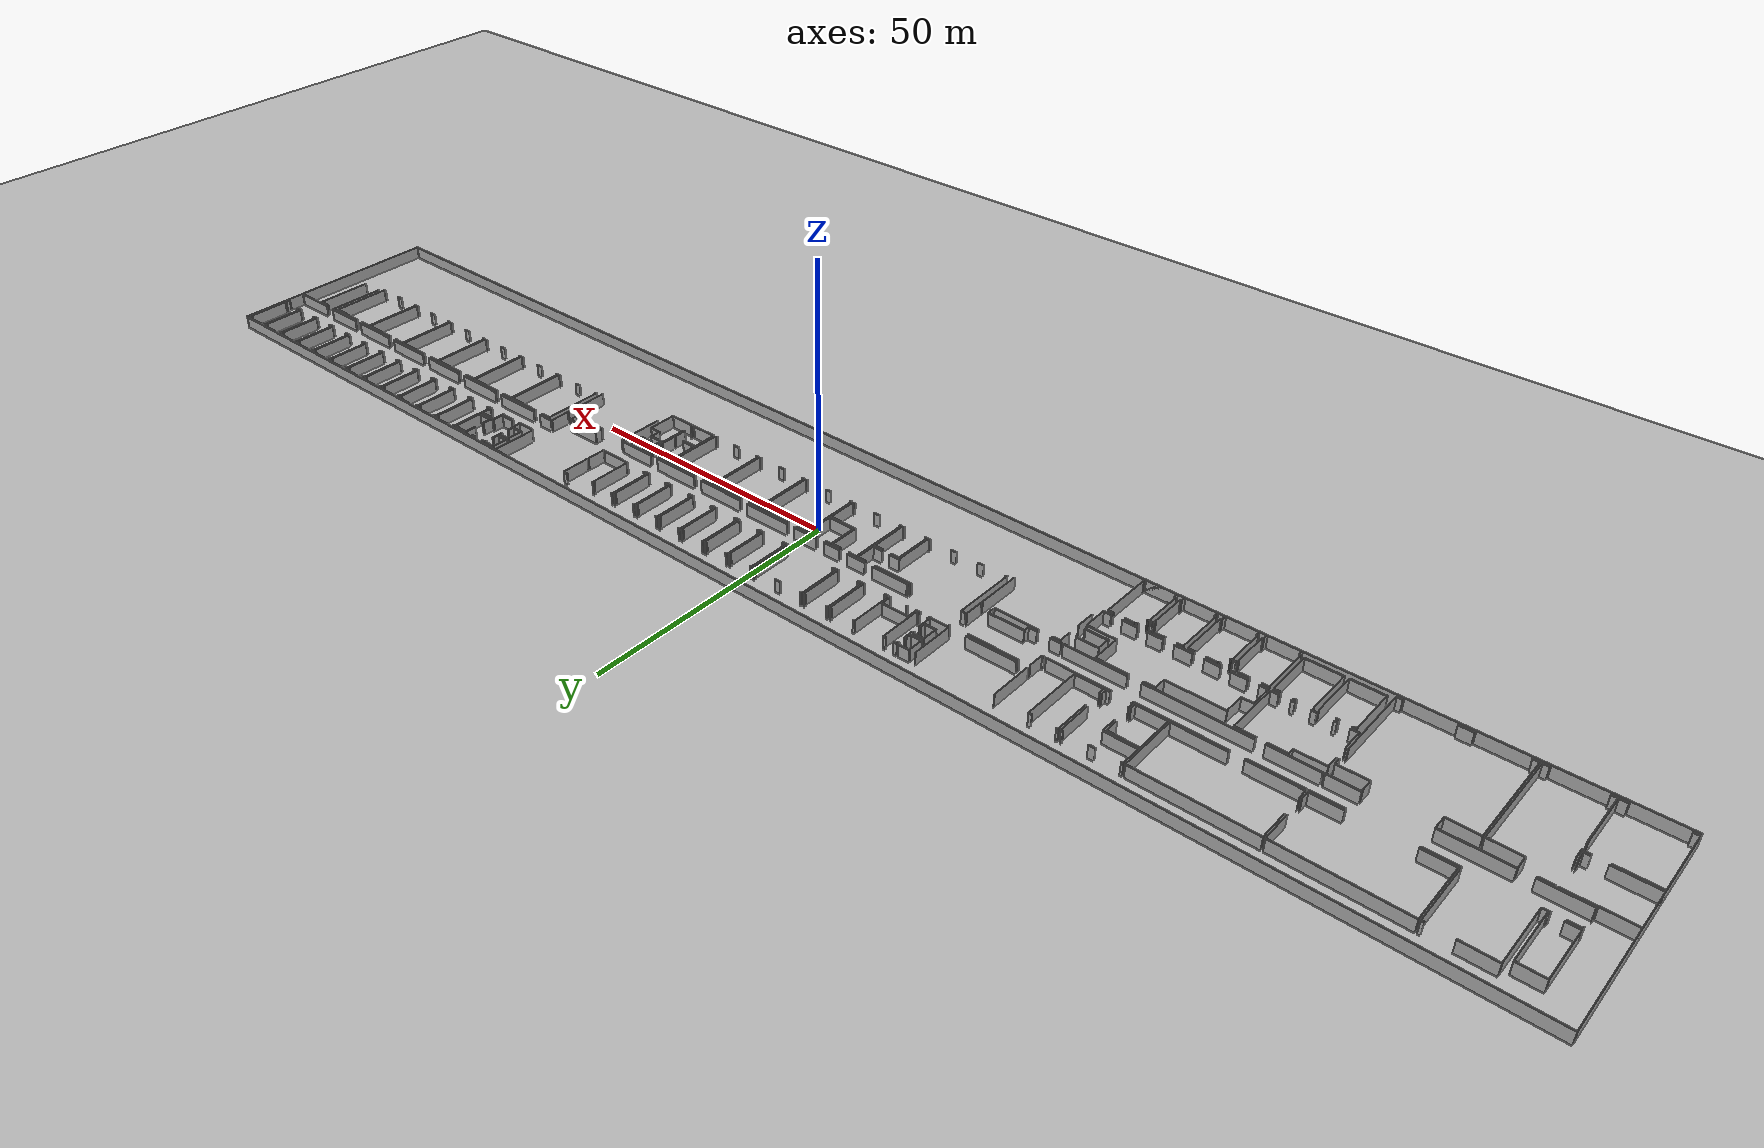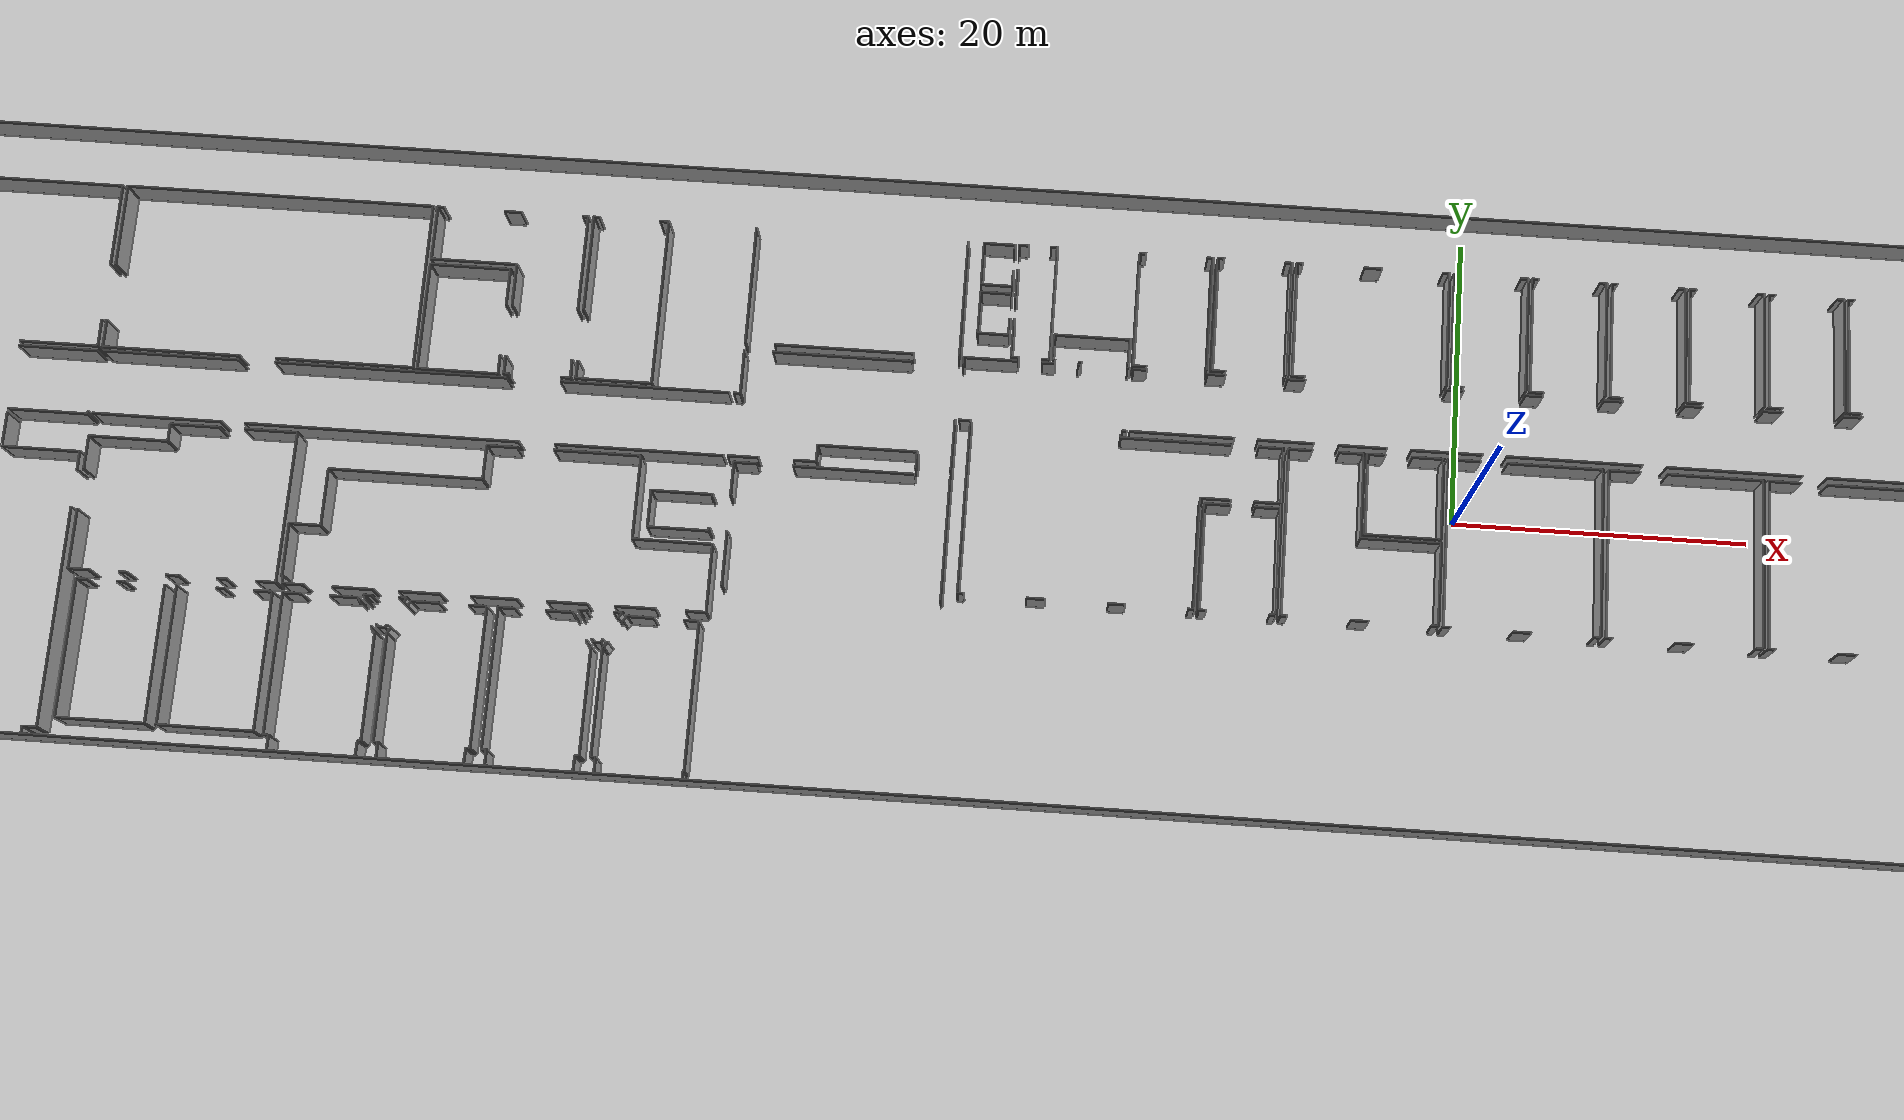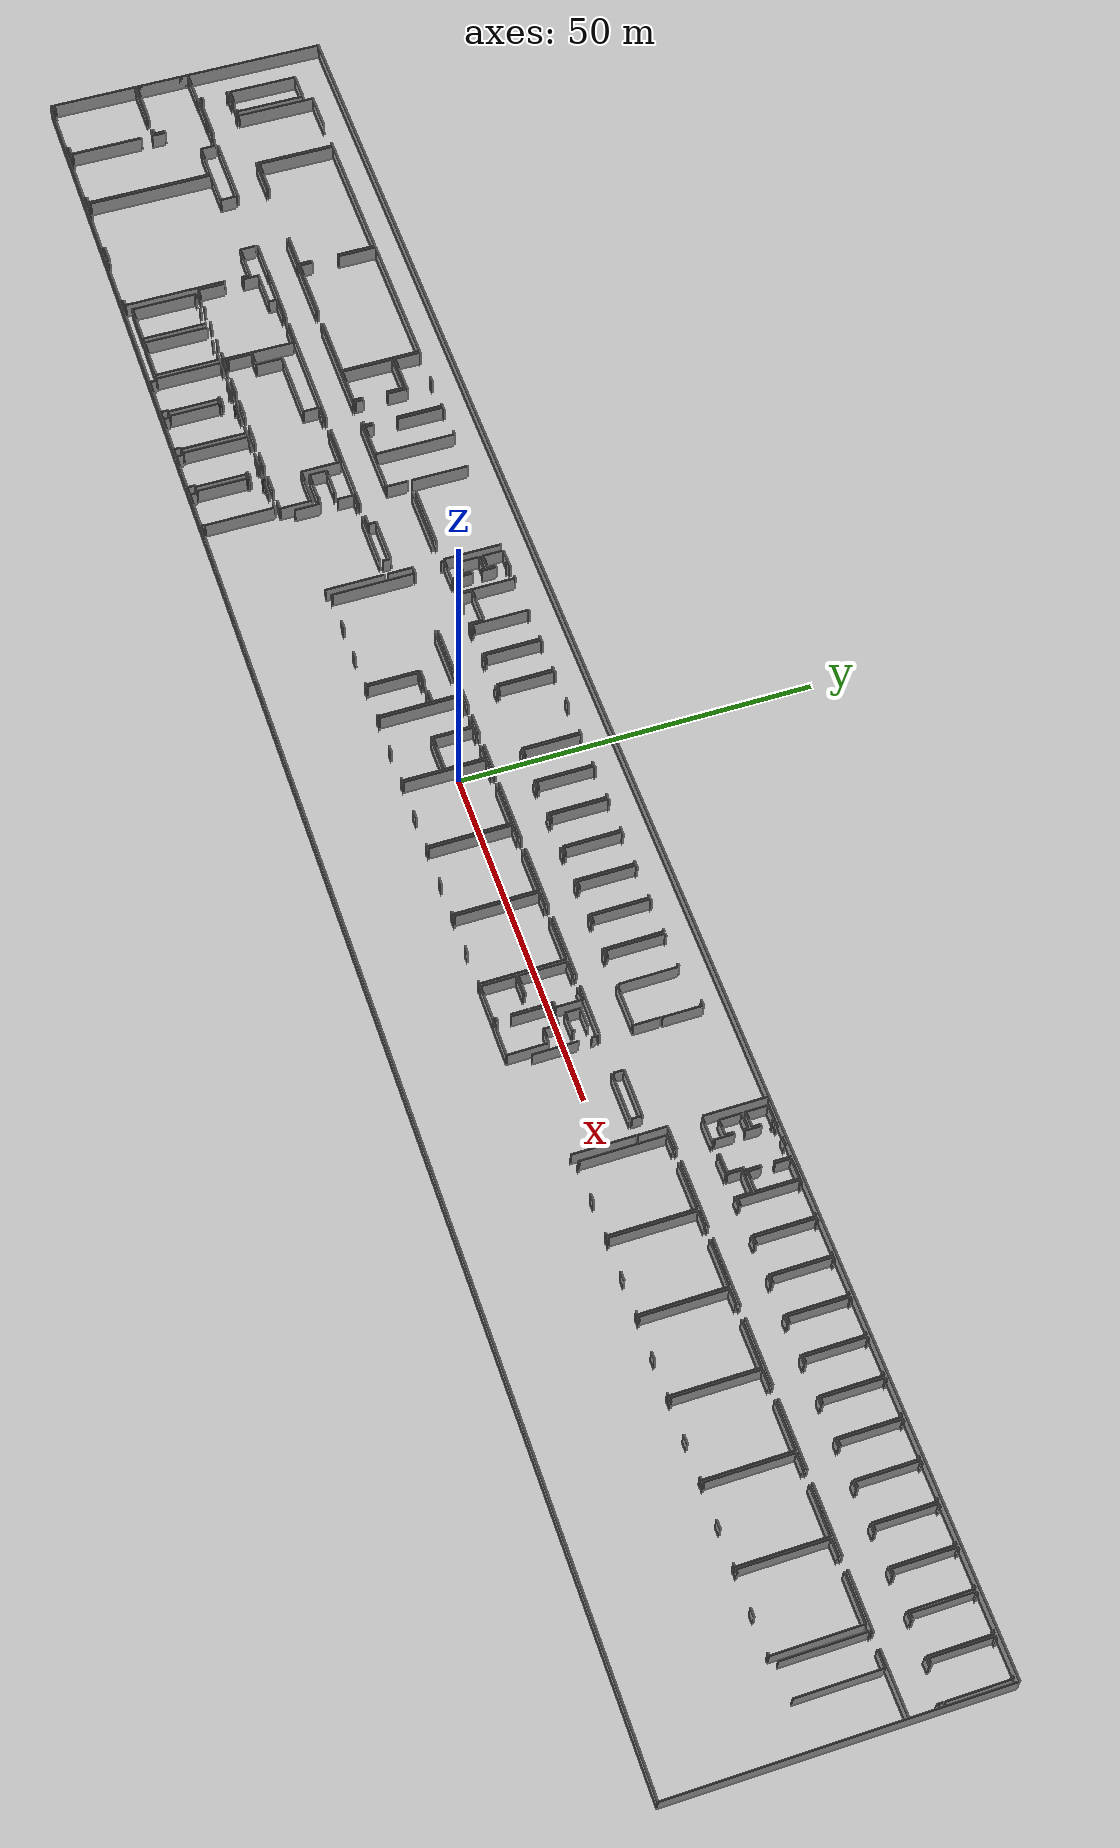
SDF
<sdf version="1.6">
  <world name="default">
    <light name="sun" type="directional">
      <cast_shadows>1</cast_shadows>
      <pose frame="">0 0 10 0 -0 0</pose>
      <diffuse>0.8 0.8 0.8 1</diffuse>
      <specular>0.1 0.1 0.1 1</specular>
      <attenuation>
        <range>1000</range>
        <constant>0.9</constant>
        <linear>0.01</linear>
        <quadratic>0.001</quadratic>
      </attenuation>
      <direction>-0.5 0.5 -1</direction>
    </light>
    <model name="ground_plane">
      <static>1</static>
      <link name="link">
        <collision name="collision">
          <geometry>
            <plane>
              <normal>0 0 1</normal>
              <size>100 100</size>
            </plane>
          </geometry>
          <surface>
            <friction>
              <ode>
                <mu>100</mu>
                <mu2>50</mu2>
              </ode>
              <torsional>
                <ode />
              </torsional>
            </friction>
            <contact>
              <ode />
            </contact>
            <bounce />
          </surface>
          <max_contacts>10</max_contacts>
        </collision>
        <visual name="visual">
          <cast_shadows>0</cast_shadows>
          <geometry>
            <plane>
              <normal>0 0 1</normal>
              <size>100 100</size>
            </plane>
          </geometry>
          <material>
            <script>
              <uri>file://media/materials/scripts/gazebo.material</uri>
              <name>Gazebo/Grey</name>
            </script>
          </material>
        </visual>
        <self_collide>0</self_collide>
        <kinematic>0</kinematic>
        <gravity>1</gravity>
      </link>
    </model>
    <gravity>0 0 -9.8</gravity>
    <magnetic_field>6e-06 2.3e-05 -4.2e-05</magnetic_field>
    <atmosphere type="adiabatic" />
    <physics default="0" name="default_physics" type="ode">
      <max_step_size>0.001</max_step_size>
      <real_time_factor>1</real_time_factor>
      <real_time_update_rate>1000</real_time_update_rate>
    </physics>
    <scene>
      <ambient>0.4 0.4 0.4 1</ambient>
      <background>0.7 0.7 0.7 1</background>
      <shadows>1</shadows>
    </scene>
    <spherical_coordinates>
      <surface_model>EARTH_WGS84</surface_model>
      <latitude_deg>0</latitude_deg>
      <longitude_deg>0</longitude_deg>
      <elevation>0</elevation>
      <heading_deg>0</heading_deg>
    </spherical_coordinates>
  <model name="50037764_PLAN2">
		<static>1</static>
		<link name="Wall_0">
			<collision name="Wall_0_Collision">
				<geometry>
					<box>
						<size>0.274899588184 0.1 2.5</size>
					</box>
				</geometry>
				<pose frame="">0.137449794092 0 1.25 0 0 0</pose>
			</collision>
			<visual name="Wall_0_Visual">
				<pose frame="">0.137449794092 0 1.25 0 0 0</pose>
				<geometry>
					<box>
						<size>0.274899588184 0.1 2.5</size>
					</box>
				</geometry>
				<material>
					<script>
						<uri>file://media/materials/scripts/gazebo.material</uri>
						<name>Gazebo/Grey</name>
					</script>
					<ambient>1 1 1 1</ambient>
				</material>
			</visual>
			<pose frame="">9.87706543291 -15.7852458183 0 0 0 3.14159265359</pose>
		</link>
		<link name="Wall_1">
			<collision name="Wall_1_Collision">
				<geometry>
					<box>
						<size>2.21048350196 0.1 2.5</size>
					</box>
				</geometry>
				<pose frame="">1.10524175098 0 1.25 0 0 0</pose>
			</collision>
			<visual name="Wall_1_Visual">
				<pose frame="">1.10524175098 0 1.25 0 0 0</pose>
				<geometry>
					<box>
						<size>2.21048350196 0.1 2.5</size>
					</box>
				</geometry>
				<material>
					<script>
						<uri>file://media/materials/scripts/gazebo.material</uri>
						<name>Gazebo/Grey</name>
					</script>
					<ambient>1 1 1 1</ambient>
				</material>
			</visual>
			<pose frame="">7.7355991662 -15.7852458183 0 0 0 3.14159265359</pose>
		</link>
		<link name="Wall_2">
			<collision name="Wall_2_Collision">
				<geometry>
					<box>
						<size>10.3727693325 0.1 2.5</size>
					</box>
				</geometry>
				<pose frame="">5.18638466623 0 1.25 0 0 0</pose>
			</collision>
			<visual name="Wall_2_Visual">
				<pose frame="">5.18638466623 0 1.25 0 0 0</pose>
				<geometry>
					<box>
						<size>10.3727693325 0.1 2.5</size>
					</box>
				</geometry>
				<material>
					<script>
						<uri>file://media/materials/scripts/gazebo.material</uri>
						<name>Gazebo/Grey</name>
					</script>
					<ambient>1 1 1 1</ambient>
				</material>
			</visual>
			<pose frame="">5.52511566424 -15.7852458183 0 0 0 1.57079632679</pose>
		</link>
		<link name="Wall_3">
			<collision name="Wall_3_Collision">
				<geometry>
					<box>
						<size>4.35449183995 0.1 2.5</size>
					</box>
				</geometry>
				<pose frame="">2.17724591998 0 1.25 0 0 0</pose>
			</collision>
			<visual name="Wall_3_Visual">
				<pose frame="">2.17724591998 0 1.25 0 0 0</pose>
				<geometry>
					<box>
						<size>4.35449183995 0.1 2.5</size>
					</box>
				</geometry>
				<material>
					<script>
						<uri>file://media/materials/scripts/gazebo.material</uri>
						<name>Gazebo/Grey</name>
					</script>
					<ambient>1 1 1 1</ambient>
				</material>
			</visual>
			<pose frame="">5.52511566424 -5.41247648584 0 0 0 0.0</pose>
		</link>
		<link name="Wall_4">
			<collision name="Wall_4_Collision">
				<geometry>
					<box>
						<size>10.3727696439 0.1 2.5</size>
					</box>
				</geometry>
				<pose frame="">5.18638482197 0 1.25 0 0 0</pose>
			</collision>
			<visual name="Wall_4_Visual">
				<pose frame="">5.18638482197 0 1.25 0 0 0</pose>
				<geometry>
					<box>
						<size>10.3727696439 0.1 2.5</size>
					</box>
				</geometry>
				<material>
					<script>
						<uri>file://media/materials/scripts/gazebo.material</uri>
						<name>Gazebo/Grey</name>
					</script>
					<ambient>1 1 1 1</ambient>
				</material>
			</visual>
			<pose frame="">9.87960750419 -5.41247648584 0 0 0 -1.5710413984</pose>
		</link>
		<link name="Wall_5">
			<collision name="Wall_5_Collision">
				<geometry>
					<box>
						<size>11.7359042148 0.1 2.5</size>
					</box>
				</geometry>
				<pose frame="">5.86795210738 0 1.25 0 0 0</pose>
			</collision>
			<visual name="Wall_5_Visual">
				<pose frame="">5.86795210738 0 1.25 0 0 0</pose>
				<geometry>
					<box>
						<size>11.7359042148 0.1 2.5</size>
					</box>
				</geometry>
				<material>
					<script>
						<uri>file://media/materials/scripts/gazebo.material</uri>
						<name>Gazebo/Grey</name>
					</script>
					<ambient>1 1 1 1</ambient>
				</material>
			</visual>
			<pose frame="">10.7937109157 -15.8582286847 0 0 0 1.57079632679</pose>
		</link>
		<link name="Wall_6">
			<collision name="Wall_6_Collision">
				<geometry>
					<box>
						<size>5.79543952412 0.1 2.5</size>
					</box>
				</geometry>
				<pose frame="">2.89771976206 0 1.25 0 0 0</pose>
			</collision>
			<visual name="Wall_6_Visual">
				<pose frame="">2.89771976206 0 1.25 0 0 0</pose>
				<geometry>
					<box>
						<size>5.79543952412 0.1 2.5</size>
					</box>
				</geometry>
				<material>
					<script>
						<uri>file://media/materials/scripts/gazebo.material</uri>
						<name>Gazebo/Grey</name>
					</script>
					<ambient>1 1 1 1</ambient>
				</material>
			</visual>
			<pose frame="">10.7937109157 -4.12232446998 0 0 0 0.0</pose>
		</link>
		<link name="Wall_7">
			<collision name="Wall_7_Collision">
				<geometry>
					<box>
						<size>0.447912959479 0.1 2.5</size>
					</box>
				</geometry>
				<pose frame="">0.22395647974 0 1.25 0 0 0</pose>
			</collision>
			<visual name="Wall_7_Visual">
				<pose frame="">0.22395647974 0 1.25 0 0 0</pose>
				<geometry>
					<box>
						<size>0.447912959479 0.1 2.5</size>
					</box>
				</geometry>
				<material>
					<script>
						<uri>file://media/materials/scripts/gazebo.material</uri>
						<name>Gazebo/Grey</name>
					</script>
					<ambient>1 1 1 1</ambient>
				</material>
			</visual>
			<pose frame="">20.7813818699 -4.12232446998 0 0 0 0.0</pose>
		</link>
		<link name="Wall_8">
			<collision name="Wall_8_Collision">
				<geometry>
					<box>
						<size>11.7359086198 0.1 2.5</size>
					</box>
				</geometry>
				<pose frame="">5.86795430989 0 1.25 0 0 0</pose>
			</collision>
			<visual name="Wall_8_Visual">
				<pose frame="">5.86795430989 0 1.25 0 0 0</pose>
				<geometry>
					<box>
						<size>11.7359086198 0.1 2.5</size>
					</box>
				</geometry>
				<material>
					<script>
						<uri>file://media/materials/scripts/gazebo.material</uri>
						<name>Gazebo/Grey</name>
					</script>
					<ambient>1 1 1 1</ambient>
				</material>
			</visual>
			<pose frame="">21.2292948294 -4.12232446998 0 0 0 -1.56992990164</pose>
		</link>
		<link name="Wall_9">
			<collision name="Wall_9_Collision">
				<geometry>
					<box>
						<size>5.38512379887 0.1 2.5</size>
					</box>
				</geometry>
				<pose frame="">2.69256189944 0 1.25 0 0 0</pose>
			</collision>
			<visual name="Wall_9_Visual">
				<pose frame="">2.69256189944 0 1.25 0 0 0</pose>
				<geometry>
					<box>
						<size>5.38512379887 0.1 2.5</size>
					</box>
				</geometry>
				<material>
					<script>
						<uri>file://media/materials/scripts/gazebo.material</uri>
						<name>Gazebo/Grey</name>
					</script>
					<ambient>1 1 1 1</ambient>
				</material>
			</visual>
			<pose frame="">42.8457979562 -15.7668158015 0 0 0 3.14159265359</pose>
		</link>
		<link name="Wall_10">
			<collision name="Wall_10_Collision">
				<geometry>
					<box>
						<size>5.39605470537 0.1 2.5</size>
					</box>
				</geometry>
				<pose frame="">2.69802735269 0 1.25 0 0 0</pose>
			</collision>
			<visual name="Wall_10_Visual">
				<pose frame="">2.69802735269 0 1.25 0 0 0</pose>
				<geometry>
					<box>
						<size>5.39605470537 0.1 2.5</size>
					</box>
				</geometry>
				<material>
					<script>
						<uri>file://media/materials/scripts/gazebo.material</uri>
						<name>Gazebo/Grey</name>
					</script>
					<ambient>1 1 1 1</ambient>
				</material>
			</visual>
			<pose frame="">26.9283644313 -15.7668158015 0 0 0 3.14159265359</pose>
		</link>
		<link name="Wall_11">
			<collision name="Wall_11_Collision">
				<geometry>
					<box>
						<size>11.6444913315 0.1 2.5</size>
					</box>
				</geometry>
				<pose frame="">5.82224566577 0 1.25 0 0 0</pose>
			</collision>
			<visual name="Wall_11_Visual">
				<pose frame="">5.82224566577 0 1.25 0 0 0</pose>
				<geometry>
					<box>
						<size>11.6444913315 0.1 2.5</size>
					</box>
				</geometry>
				<material>
					<script>
						<uri>file://media/materials/scripts/gazebo.material</uri>
						<name>Gazebo/Grey</name>
					</script>
					<ambient>1 1 1 1</ambient>
				</material>
			</visual>
			<pose frame="">21.532309726 -15.7668158015 0 0 0 1.57079632679</pose>
		</link>
		<link name="Wall_12">
			<collision name="Wall_12_Collision">
				<geometry>
					<box>
						<size>21.299252631 0.1 2.5</size>
					</box>
				</geometry>
				<pose frame="">10.6496263155 0 1.25 0 0 0</pose>
			</collision>
			<visual name="Wall_12_Visual">
				<pose frame="">10.6496263155 0 1.25 0 0 0</pose>
				<geometry>
					<box>
						<size>21.299252631 0.1 2.5</size>
					</box>
				</geometry>
				<material>
					<script>
						<uri>file://media/materials/scripts/gazebo.material</uri>
						<name>Gazebo/Grey</name>
					</script>
					<ambient>1 1 1 1</ambient>
				</material>
			</visual>
			<pose frame="">21.532309726 -4.12232446998 0 0 0 0.0</pose>
		</link>
		<link name="Wall_13">
			<collision name="Wall_13_Collision">
				<geometry>
					<box>
						<size>5.75115664243 0.1 2.5</size>
					</box>
				</geometry>
				<pose frame="">2.87557832122 0 1.25 0 0 0</pose>
			</collision>
			<visual name="Wall_13_Visual">
				<pose frame="">2.87557832122 0 1.25 0 0 0</pose>
				<geometry>
					<box>
						<size>5.75115664243 0.1 2.5</size>
					</box>
				</geometry>
				<material>
					<script>
						<uri>file://media/materials/scripts/gazebo.material</uri>
						<name>Gazebo/Grey</name>
					</script>
					<ambient>1 1 1 1</ambient>
				</material>
			</visual>
			<pose frame="">42.831562357 -4.12232446998 0 0 0 -1.57079632679</pose>
		</link>
		<link name="Wall_14">
			<collision name="Wall_14_Collision">
				<geometry>
					<box>
						<size>1.90637782522 0.1 2.5</size>
					</box>
				</geometry>
				<pose frame="">0.953188912609 0 1.25 0 0 0</pose>
			</collision>
			<visual name="Wall_14_Visual">
				<pose frame="">0.953188912609 0 1.25 0 0 0</pose>
				<geometry>
					<box>
						<size>1.90637782522 0.1 2.5</size>
					</box>
				</geometry>
				<material>
					<script>
						<uri>file://media/materials/scripts/gazebo.material</uri>
						<name>Gazebo/Grey</name>
					</script>
					<ambient>1 1 1 1</ambient>
				</material>
			</visual>
			<pose frame="">42.831562357 -13.8604911282 0 0 0 -1.56332890282</pose>
		</link>
		<link name="Wall_15">
			<collision name="Wall_15_Collision">
				<geometry>
					<box>
						<size>5.45477655193 0.1 2.5</size>
					</box>
				</geometry>
				<pose frame="">2.72738827597 0 1.25 0 0 0</pose>
			</collision>
			<visual name="Wall_15_Visual">
				<pose frame="">2.72738827597 0 1.25 0 0 0</pose>
				<geometry>
					<box>
						<size>5.45477655193 0.1 2.5</size>
					</box>
				</geometry>
				<material>
					<script>
						<uri>file://media/materials/scripts/gazebo.material</uri>
						<name>Gazebo/Grey</name>
					</script>
					<ambient>1 1 1 1</ambient>
				</material>
			</visual>
			<pose frame="">42.8989272459 -20.595861508 0 0 0 3.14159265359</pose>
		</link>
		<link name="Wall_16">
			<collision name="Wall_16_Collision">
				<geometry>
					<box>
						<size>11.1444913315 0.1 2.5</size>
					</box>
				</geometry>
				<pose frame="">5.57224566577 0 1.25 0 0 0</pose>
			</collision>
			<visual name="Wall_16_Visual">
				<pose frame="">5.57224566577 0 1.25 0 0 0</pose>
				<geometry>
					<box>
						<size>11.1444913315 0.1 2.5</size>
					</box>
				</geometry>
				<material>
					<script>
						<uri>file://media/materials/scripts/gazebo.material</uri>
						<name>Gazebo/Grey</name>
					</script>
					<ambient>1 1 1 1</ambient>
				</material>
			</visual>
			<pose frame="">26.9309065026 -20.595861508 0 0 0 3.14159265359</pose>
		</link>
		<link name="Wall_17">
			<collision name="Wall_17_Collision">
				<geometry>
					<box>
						<size>7.8188265799 0.1 2.5</size>
					</box>
				</geometry>
				<pose frame="">3.90941328995 0 1.25 0 0 0</pose>
			</collision>
			<visual name="Wall_17_Visual">
				<pose frame="">3.90941328995 0 1.25 0 0 0</pose>
				<geometry>
					<box>
						<size>7.8188265799 0.1 2.5</size>
					</box>
				</geometry>
				<material>
					<script>
						<uri>file://media/materials/scripts/gazebo.material</uri>
						<name>Gazebo/Grey</name>
					</script>
					<ambient>1 1 1 1</ambient>
				</material>
			</visual>
			<pose frame="">13.3303675835 -20.595861508 0 0 0 3.14159265359</pose>
		</link>
		<link name="Wall_18">
			<collision name="Wall_18_Collision">
				<geometry>
					<box>
						<size>0.55290050333 0.1 2.5</size>
					</box>
				</geometry>
				<pose frame="">0.276450251665 0 1.25 0 0 0</pose>
			</collision>
			<visual name="Wall_18_Visual">
				<pose frame="">0.276450251665 0 1.25 0 0 0</pose>
				<geometry>
					<box>
						<size>0.55290050333 0.1 2.5</size>
					</box>
				</geometry>
				<material>
					<script>
						<uri>file://media/materials/scripts/gazebo.material</uri>
						<name>Gazebo/Grey</name>
					</script>
					<ambient>1 1 1 1</ambient>
				</material>
			</visual>
			<pose frame="">5.51154100361 -20.595861508 0 0 0 1.57079632679</pose>
		</link>
		<link name="Wall_19">
			<collision name="Wall_19_Collision">
				<geometry>
					<box>
						<size>0.262265493924 0.1 2.5</size>
					</box>
				</geometry>
				<pose frame="">0.131132746962 0 1.25 0 0 0</pose>
			</collision>
			<visual name="Wall_19_Visual">
				<pose frame="">0.131132746962 0 1.25 0 0 0</pose>
				<geometry>
					<box>
						<size>0.262265493924 0.1 2.5</size>
					</box>
				</geometry>
				<material>
					<script>
						<uri>file://media/materials/scripts/gazebo.material</uri>
						<name>Gazebo/Grey</name>
					</script>
					<ambient>1 1 1 1</ambient>
				</material>
			</visual>
			<pose frame="">5.51154100361 -16.3523565001 0 0 0 1.57079632679</pose>
		</link>
		<link name="Wall_20">
			<collision name="Wall_20_Collision">
				<geometry>
					<box>
						<size>2.13040825665 0.1 2.5</size>
					</box>
				</geometry>
				<pose frame="">1.06520412832 0 1.25 0 0 0</pose>
			</collision>
			<visual name="Wall_20_Visual">
				<pose frame="">1.06520412832 0 1.25 0 0 0</pose>
				<geometry>
					<box>
						<size>2.13040825665 0.1 2.5</size>
					</box>
				</geometry>
				<material>
					<script>
						<uri>file://media/materials/scripts/gazebo.material</uri>
						<name>Gazebo/Grey</name>
					</script>
					<ambient>1 1 1 1</ambient>
				</material>
			</visual>
			<pose frame="">5.51154100361 -16.0900910062 0 0 0 0.0</pose>
		</link>
		<link name="Wall_21">
			<collision name="Wall_21_Collision">
				<geometry>
					<box>
						<size>1.2630026946 0.1 2.5</size>
					</box>
				</geometry>
				<pose frame="">0.631501347298 0 1.25 0 0 0</pose>
			</collision>
			<visual name="Wall_21_Visual">
				<pose frame="">0.631501347298 0 1.25 0 0 0</pose>
				<geometry>
					<box>
						<size>1.2630026946 0.1 2.5</size>
					</box>
				</geometry>
				<material>
					<script>
						<uri>file://media/materials/scripts/gazebo.material</uri>
						<name>Gazebo/Grey</name>
					</script>
					<ambient>1 1 1 1</ambient>
				</material>
			</visual>
			<pose frame="">9.54560475876 -16.0900910062 0 0 0 0.0</pose>
		</link>
		<link name="Wall_22">
			<collision name="Wall_22_Collision">
				<geometry>
					<box>
						<size>5.65737963292 0.1 2.5</size>
					</box>
				</geometry>
				<pose frame="">2.82868981646 0 1.25 0 0 0</pose>
			</collision>
			<visual name="Wall_22_Visual">
				<pose frame="">2.82868981646 0 1.25 0 0 0</pose>
				<geometry>
					<box>
						<size>5.65737963292 0.1 2.5</size>
					</box>
				</geometry>
				<material>
					<script>
						<uri>file://media/materials/scripts/gazebo.material</uri>
						<name>Gazebo/Grey</name>
					</script>
					<ambient>1 1 1 1</ambient>
				</material>
			</visual>
			<pose frame="">21.2623417561 -16.0900910062 0 0 0 0.0</pose>
		</link>
		<link name="Wall_23">
			<collision name="Wall_23_Collision">
				<geometry>
					<box>
						<size>5.44892978799 0.1 2.5</size>
					</box>
				</geometry>
				<pose frame="">2.724464894 0 1.25 0 0 0</pose>
			</collision>
			<visual name="Wall_23_Visual">
				<pose frame="">2.724464894 0 1.25 0 0 0</pose>
				<geometry>
					<box>
						<size>5.44892978799 0.1 2.5</size>
					</box>
				</geometry>
				<material>
					<script>
						<uri>file://media/materials/scripts/gazebo.material</uri>
						<name>Gazebo/Grey</name>
					</script>
					<ambient>1 1 1 1</ambient>
				</material>
			</visual>
			<pose frame="">37.4494890437 -16.0900910062 0 0 0 0.0</pose>
		</link>
		<link name="Wall_24">
			<collision name="Wall_24_Collision">
				<geometry>
					<box>
						<size>0.182013013699 0.1 2.5</size>
					</box>
				</geometry>
				<pose frame="">0.0910065068497 0 1.25 0 0 0</pose>
			</collision>
			<visual name="Wall_24_Visual">
				<pose frame="">0.0910065068497 0 1.25 0 0 0</pose>
				<geometry>
					<box>
						<size>0.182013013699 0.1 2.5</size>
					</box>
				</geometry>
				<material>
					<script>
						<uri>file://media/materials/scripts/gazebo.material</uri>
						<name>Gazebo/Grey</name>
					</script>
					<ambient>1 1 1 1</ambient>
				</material>
			</visual>
			<pose frame="">42.8984188317 -20.4138492043 0 0 0 -1.56800303797</pose>
		</link>
		<link name="Wall_25">
			<collision name="Wall_25_Collision">
				<geometry>
					<box>
						<size>1.05063805989 0.1 2.5</size>
					</box>
				</geometry>
				<pose frame="">0.525319029946 0 1.25 0 0 0</pose>
			</collision>
			<visual name="Wall_25_Visual">
				<pose frame="">0.525319029946 0 1.25 0 0 0</pose>
				<geometry>
					<box>
						<size>1.05063805989 0.1 2.5</size>
					</box>
				</geometry>
				<material>
					<script>
						<uri>file://media/materials/scripts/gazebo.material</uri>
						<name>Gazebo/Grey</name>
					</script>
					<ambient>1 1 1 1</ambient>
				</material>
			</visual>
			<pose frame="">21.2394631145 -42.151354924 0 0 0 3.14159265359</pose>
		</link>
		<link name="Wall_26">
			<collision name="Wall_26_Collision">
				<geometry>
					<box>
						<size>0.471808429508 0.1 2.5</size>
					</box>
				</geometry>
				<pose frame="">0.235904214754 0 1.25 0 0 0</pose>
			</collision>
			<visual name="Wall_26_Visual">
				<pose frame="">0.235904214754 0 1.25 0 0 0</pose>
				<geometry>
					<box>
						<size>0.471808429508 0.1 2.5</size>
					</box>
				</geometry>
				<material>
					<script>
						<uri>file://media/materials/scripts/gazebo.material</uri>
						<name>Gazebo/Grey</name>
					</script>
					<ambient>1 1 1 1</ambient>
				</material>
			</visual>
			<pose frame="">20.1888250547 -42.151354924 0 0 0 -1.57079632679</pose>
		</link>
		<link name="Wall_27">
			<collision name="Wall_27_Collision">
				<geometry>
					<box>
						<size>8.38959784432 0.1 2.5</size>
					</box>
				</geometry>
				<pose frame="">4.19479892216 0 1.25 0 0 0</pose>
			</collision>
			<visual name="Wall_27_Visual">
				<pose frame="">4.19479892216 0 1.25 0 0 0</pose>
				<geometry>
					<box>
						<size>8.38959784432 0.1 2.5</size>
					</box>
				</geometry>
				<material>
					<script>
						<uri>file://media/materials/scripts/gazebo.material</uri>
						<name>Gazebo/Grey</name>
					</script>
					<ambient>1 1 1 1</ambient>
				</material>
			</visual>
			<pose frame="">20.1888250547 -42.6231633535 0 0 0 3.14159265359</pose>
		</link>
		<link name="Wall_28">
			<collision name="Wall_28_Collision">
				<geometry>
					<box>
						<size>0.471808429508 0.1 2.5</size>
					</box>
				</geometry>
				<pose frame="">0.235904214754 0 1.25 0 0 0</pose>
			</collision>
			<visual name="Wall_28_Visual">
				<pose frame="">0.235904214754 0 1.25 0 0 0</pose>
				<geometry>
					<box>
						<size>0.471808429508 0.1 2.5</size>
					</box>
				</geometry>
				<material>
					<script>
						<uri>file://media/materials/scripts/gazebo.material</uri>
						<name>Gazebo/Grey</name>
					</script>
					<ambient>1 1 1 1</ambient>
				</material>
			</visual>
			<pose frame="">11.7992272103 -42.6231633535 0 0 0 1.57079632679</pose>
		</link>
		<link name="Wall_29">
			<collision name="Wall_29_Collision">
				<geometry>
					<box>
						<size>0.963953429254 0.1 2.5</size>
					</box>
				</geometry>
				<pose frame="">0.481976714627 0 1.25 0 0 0</pose>
			</collision>
			<visual name="Wall_29_Visual">
				<pose frame="">0.481976714627 0 1.25 0 0 0</pose>
				<geometry>
					<box>
						<size>0.963953429254 0.1 2.5</size>
					</box>
				</geometry>
				<material>
					<script>
						<uri>file://media/materials/scripts/gazebo.material</uri>
						<name>Gazebo/Grey</name>
					</script>
					<ambient>1 1 1 1</ambient>
				</material>
			</visual>
			<pose frame="">11.7992272103 -42.151354924 0 0 0 3.14159265359</pose>
		</link>
		<link name="Wall_30">
			<collision name="Wall_30_Collision">
				<geometry>
					<box>
						<size>10.885911841 0.1 2.5</size>
					</box>
				</geometry>
				<pose frame="">5.44295592048 0 1.25 0 0 0</pose>
			</collision>
			<visual name="Wall_30_Visual">
				<pose frame="">5.44295592048 0 1.25 0 0 0</pose>
				<geometry>
					<box>
						<size>10.885911841 0.1 2.5</size>
					</box>
				</geometry>
				<material>
					<script>
						<uri>file://media/materials/scripts/gazebo.material</uri>
						<name>Gazebo/Grey</name>
					</script>
					<ambient>1 1 1 1</ambient>
				</material>
			</visual>
			<pose frame="">10.8352737811 -42.151354924 0 0 0 1.57079632679</pose>
		</link>
		<link name="Wall_31">
			<collision name="Wall_31_Collision">
				<geometry>
					<box>
						<size>2.10127611978 0.1 2.5</size>
					</box>
				</geometry>
				<pose frame="">1.05063805989 0 1.25 0 0 0</pose>
			</collision>
			<visual name="Wall_31_Visual">
				<pose frame="">1.05063805989 0 1.25 0 0 0</pose>
				<geometry>
					<box>
						<size>2.10127611978 0.1 2.5</size>
					</box>
				</geometry>
				<material>
					<script>
						<uri>file://media/materials/scripts/gazebo.material</uri>
						<name>Gazebo/Grey</name>
					</script>
					<ambient>1 1 1 1</ambient>
				</material>
			</visual>
			<pose frame="">10.8352737811 -29.594793838 0 0 0 1.57079632679</pose>
		</link>
		<link name="Wall_32">
			<collision name="Wall_32_Collision">
				<geometry>
					<box>
						<size>2.47831613198 0.1 2.5</size>
					</box>
				</geometry>
				<pose frame="">1.23915806599 0 1.25 0 0 0</pose>
			</collision>
			<visual name="Wall_32_Visual">
				<pose frame="">1.23915806599 0 1.25 0 0 0</pose>
				<geometry>
					<box>
						<size>2.47831613198 0.1 2.5</size>
					</box>
				</geometry>
				<material>
					<script>
						<uri>file://media/materials/scripts/gazebo.material</uri>
						<name>Gazebo/Grey</name>
					</script>
					<ambient>1 1 1 1</ambient>
				</material>
			</visual>
			<pose frame="">10.8352737811 -20.8765061772 0 0 0 0.0</pose>
		</link>
		<link name="Wall_33">
			<collision name="Wall_33_Collision">
				<geometry>
					<box>
						<size>2.39386852407 0.1 2.5</size>
					</box>
				</geometry>
				<pose frame="">1.19693426204 0 1.25 0 0 0</pose>
			</collision>
			<visual name="Wall_33_Visual">
				<pose frame="">1.19693426204 0 1.25 0 0 0</pose>
				<geometry>
					<box>
						<size>2.39386852407 0.1 2.5</size>
					</box>
				</geometry>
				<material>
					<script>
						<uri>file://media/materials/scripts/gazebo.material</uri>
						<name>Gazebo/Grey</name>
					</script>
					<ambient>1 1 1 1</ambient>
				</material>
			</visual>
			<pose frame="">15.7844831969 -20.8765061772 0 0 0 -1.57079632679</pose>
		</link>
		<link name="Wall_34">
			<collision name="Wall_34_Collision">
				<geometry>
					<box>
						<size>5.47302862372 0.1 2.5</size>
					</box>
				</geometry>
				<pose frame="">2.73651431186 0 1.25 0 0 0</pose>
			</collision>
			<visual name="Wall_34_Visual">
				<pose frame="">2.73651431186 0 1.25 0 0 0</pose>
				<geometry>
					<box>
						<size>5.47302862372 0.1 2.5</size>
					</box>
				</geometry>
				<material>
					<script>
						<uri>file://media/materials/scripts/gazebo.material</uri>
						<name>Gazebo/Grey</name>
					</script>
					<ambient>1 1 1 1</ambient>
				</material>
			</visual>
			<pose frame="">15.7844831969 -23.2703747013 0 0 0 0.0</pose>
		</link>
		<link name="Wall_35">
			<collision name="Wall_35_Collision">
				<geometry>
					<box>
						<size>18.8809888492 0.1 2.5</size>
					</box>
				</geometry>
				<pose frame="">9.44049442462 0 1.25 0 0 0</pose>
			</collision>
			<visual name="Wall_35_Visual">
				<pose frame="">9.44049442462 0 1.25 0 0 0</pose>
				<geometry>
					<box>
						<size>18.8809888492 0.1 2.5</size>
					</box>
				</geometry>
				<material>
					<script>
						<uri>file://media/materials/scripts/gazebo.material</uri>
						<name>Gazebo/Grey</name>
					</script>
					<ambient>1 1 1 1</ambient>
				</material>
			</visual>
			<pose frame="">21.2575118206 -23.2703747013 0 0 0 -1.57175224648</pose>
		</link>
		<link name="Wall_36">
			<collision name="Wall_36_Collision">
				<geometry>
					<box>
						<size>0.999466165031 0.1 2.5</size>
					</box>
				</geometry>
				<pose frame="">0.499733082516 0 1.25 0 0 0</pose>
			</collision>
			<visual name="Wall_36_Visual">
				<pose frame="">0.499733082516 0 1.25 0 0 0</pose>
				<geometry>
					<box>
						<size>0.999466165031 0.1 2.5</size>
					</box>
				</geometry>
				<material>
					<script>
						<uri>file://media/materials/scripts/gazebo.material</uri>
						<name>Gazebo/Grey</name>
					</script>
					<ambient>1 1 1 1</ambient>
				</material>
			</visual>
			<pose frame="">10.4633941736 -29.0840917179 0 0 0 3.14159265359</pose>
		</link>
		<link name="Wall_37">
			<collision name="Wall_37_Collision">
				<geometry>
					<box>
						<size>7.14080532818 0.1 2.5</size>
					</box>
				</geometry>
				<pose frame="">3.57040266409 0 1.25 0 0 0</pose>
			</collision>
			<visual name="Wall_37_Visual">
				<pose frame="">3.57040266409 0 1.25 0 0 0</pose>
				<geometry>
					<box>
						<size>7.14080532818 0.1 2.5</size>
					</box>
				</geometry>
				<material>
					<script>
						<uri>file://media/materials/scripts/gazebo.material</uri>
						<name>Gazebo/Grey</name>
					</script>
					<ambient>1 1 1 1</ambient>
				</material>
			</visual>
			<pose frame="">7.14080532818 -29.0840917179 0 0 0 3.14159265359</pose>
		</link>
		<link name="Wall_38">
			<collision name="Wall_38_Collision">
				<geometry>
					<box>
						<size>0.748385784737 0.1 2.5</size>
					</box>
				</geometry>
				<pose frame="">0.374192892369 0 1.25 0 0 0</pose>
			</collision>
			<visual name="Wall_38_Visual">
				<pose frame="">0.374192892369 0 1.25 0 0 0</pose>
				<geometry>
					<box>
						<size>0.748385784737 0.1 2.5</size>
					</box>
				</geometry>
				<material>
					<script>
						<uri>file://media/materials/scripts/gazebo.material</uri>
						<name>Gazebo/Grey</name>
					</script>
					<ambient>1 1 1 1</ambient>
				</material>
			</visual>
			<pose frame="">0.0 -29.0840917179 0 0 0 1.57079632679</pose>
		</link>
		<link name="Wall_39">
			<collision name="Wall_39_Collision">
				<geometry>
					<box>
						<size>1.32721541512 0.1 2.5</size>
					</box>
				</geometry>
				<pose frame="">0.66360770756 0 1.25 0 0 0</pose>
			</collision>
			<visual name="Wall_39_Visual">
				<pose frame="">0.66360770756 0 1.25 0 0 0</pose>
				<geometry>
					<box>
						<size>1.32721541512 0.1 2.5</size>
					</box>
				</geometry>
				<material>
					<script>
						<uri>file://media/materials/scripts/gazebo.material</uri>
						<name>Gazebo/Grey</name>
					</script>
					<ambient>1 1 1 1</ambient>
				</material>
			</visual>
			<pose frame="">0.0 -22.3071838934 0 0 0 1.57079632679</pose>
		</link>
		<link name="Wall_40">
			<collision name="Wall_40_Collision">
				<geometry>
					<box>
						<size>5.48357821953 0.1 2.5</size>
					</box>
				</geometry>
				<pose frame="">2.74178910977 0 1.25 0 0 0</pose>
			</collision>
			<visual name="Wall_40_Visual">
				<pose frame="">2.74178910977 0 1.25 0 0 0</pose>
				<geometry>
					<box>
						<size>5.48357821953 0.1 2.5</size>
					</box>
				</geometry>
				<material>
					<script>
						<uri>file://media/materials/scripts/gazebo.material</uri>
						<name>Gazebo/Grey</name>
					</script>
					<ambient>1 1 1 1</ambient>
				</material>
			</visual>
			<pose frame="">0.0 -20.9799684783 0 0 0 0.0</pose>
		</link>
		<link name="Wall_41">
			<collision name="Wall_41_Collision">
				<geometry>
					<box>
						<size>0.071432202959 0.1 2.5</size>
					</box>
				</geometry>
				<pose frame="">0.0357161014795 0 1.25 0 0 0</pose>
			</collision>
			<visual name="Wall_41_Visual">
				<pose frame="">0.0357161014795 0 1.25 0 0 0</pose>
				<geometry>
					<box>
						<size>0.071432202959 0.1 2.5</size>
					</box>
				</geometry>
				<material>
					<script>
						<uri>file://media/materials/scripts/gazebo.material</uri>
						<name>Gazebo/Grey</name>
					</script>
					<ambient>1 1 1 1</ambient>
				</material>
			</visual>
			<pose frame="">5.48357821953 -20.9799684783 0 0 0 1.57079632679</pose>
		</link>
		<link name="Wall_42">
			<collision name="Wall_42_Collision">
				<geometry>
					<box>
						<size>4.99326351111 0.1 2.5</size>
					</box>
				</geometry>
				<pose frame="">2.49663175555 0 1.25 0 0 0</pose>
			</collision>
			<visual name="Wall_42_Visual">
				<pose frame="">2.49663175555 0 1.25 0 0 0</pose>
				<geometry>
					<box>
						<size>4.99326351111 0.1 2.5</size>
					</box>
				</geometry>
				<material>
					<script>
						<uri>file://media/materials/scripts/gazebo.material</uri>
						<name>Gazebo/Grey</name>
					</script>
					<ambient>1 1 1 1</ambient>
				</material>
			</visual>
			<pose frame="">5.48357821953 -20.9085362754 0 0 0 0.0</pose>
		</link>
		<link name="Wall_43">
			<collision name="Wall_43_Collision">
				<geometry>
					<box>
						<size>1.58249650918 0.1 2.5</size>
					</box>
				</geometry>
				<pose frame="">0.791248254592 0 1.25 0 0 0</pose>
			</collision>
			<visual name="Wall_43_Visual">
				<pose frame="">0.791248254592 0 1.25 0 0 0</pose>
				<geometry>
					<box>
						<size>1.58249650918 0.1 2.5</size>
					</box>
				</geometry>
				<material>
					<script>
						<uri>file://media/materials/scripts/gazebo.material</uri>
						<name>Gazebo/Grey</name>
					</script>
					<ambient>1 1 1 1</ambient>
				</material>
			</visual>
			<pose frame="">10.4768417306 -27.5016523463 0 0 0 -1.57929411421</pose>
		</link>
		<link name="Wall_44">
			<collision name="Wall_44_Collision">
				<geometry>
					<box>
						<size>1.36285525446 0.1 2.5</size>
					</box>
				</geometry>
				<pose frame="">0.681427627231 0 1.25 0 0 0</pose>
			</collision>
			<visual name="Wall_44_Visual">
				<pose frame="">0.681427627231 0 1.25 0 0 0</pose>
				<geometry>
					<box>
						<size>1.36285525446 0.1 2.5</size>
					</box>
				</geometry>
				<material>
					<script>
						<uri>file://media/materials/scripts/gazebo.material</uri>
						<name>Gazebo/Grey</name>
					</script>
					<ambient>1 1 1 1</ambient>
				</material>
			</visual>
			<pose frame="">10.7438608979 -42.1345772535 0 0 0 3.14159265359</pose>
		</link>
		<link name="Wall_45">
			<collision name="Wall_45_Collision">
				<geometry>
					<box>
						<size>0.481976714627 0.1 2.5</size>
					</box>
				</geometry>
				<pose frame="">0.240988357314 0 1.25 0 0 0</pose>
			</collision>
			<visual name="Wall_45_Visual">
				<pose frame="">0.240988357314 0 1.25 0 0 0</pose>
				<geometry>
					<box>
						<size>0.481976714627 0.1 2.5</size>
					</box>
				</geometry>
				<material>
					<script>
						<uri>file://media/materials/scripts/gazebo.material</uri>
						<name>Gazebo/Grey</name>
					</script>
					<ambient>1 1 1 1</ambient>
				</material>
			</visual>
			<pose frame="">9.3810056434 -42.1345772535 0 0 0 -1.57079632679</pose>
		</link>
		<link name="Wall_46">
			<collision name="Wall_46_Collision">
				<geometry>
					<box>
						<size>0.465199044181 0.1 2.5</size>
					</box>
				</geometry>
				<pose frame="">0.232599522091 0 1.25 0 0 0</pose>
			</collision>
			<visual name="Wall_46_Visual">
				<pose frame="">0.232599522091 0 1.25 0 0 0</pose>
				<geometry>
					<box>
						<size>0.465199044181 0.1 2.5</size>
					</box>
				</geometry>
				<material>
					<script>
						<uri>file://media/materials/scripts/gazebo.material</uri>
						<name>Gazebo/Grey</name>
					</script>
					<ambient>1 1 1 1</ambient>
				</material>
			</visual>
			<pose frame="">0.996136051655 -42.6165539682 0 0 0 1.57079632679</pose>
		</link>
		<link name="Wall_47">
			<collision name="Wall_47_Collision">
				<geometry>
					<box>
						<size>0.980603996136 0.1 2.5</size>
					</box>
				</geometry>
				<pose frame="">0.490301998068 0 1.25 0 0 0</pose>
			</collision>
			<visual name="Wall_47_Visual">
				<pose frame="">0.490301998068 0 1.25 0 0 0</pose>
				<geometry>
					<box>
						<size>0.980603996136 0.1 2.5</size>
					</box>
				</geometry>
				<material>
					<script>
						<uri>file://media/materials/scripts/gazebo.material</uri>
						<name>Gazebo/Grey</name>
					</script>
					<ambient>1 1 1 1</ambient>
				</material>
			</visual>
			<pose frame="">0.996136051655 -42.151354924 0 0 0 3.14159265359</pose>
		</link>
		<link name="Wall_48">
			<collision name="Wall_48_Collision">
				<geometry>
					<box>
						<size>12.8059382785 0.1 2.5</size>
					</box>
				</geometry>
				<pose frame="">6.40296913925 0 1.25 0 0 0</pose>
			</collision>
			<visual name="Wall_48_Visual">
				<pose frame="">6.40296913925 0 1.25 0 0 0</pose>
				<geometry>
					<box>
						<size>12.8059382785 0.1 2.5</size>
					</box>
				</geometry>
				<material>
					<script>
						<uri>file://media/materials/scripts/gazebo.material</uri>
						<name>Gazebo/Grey</name>
					</script>
					<ambient>1 1 1 1</ambient>
				</material>
			</visual>
			<pose frame="">0.0155320555188 -42.151354924 0 0 0 1.57079632679</pose>
		</link>
		<link name="Wall_49">
			<collision name="Wall_49_Collision">
				<geometry>
					<box>
						<size>6.95553917332 0.1 2.5</size>
					</box>
				</geometry>
				<pose frame="">3.47776958666 0 1.25 0 0 0</pose>
			</collision>
			<visual name="Wall_49_Visual">
				<pose frame="">3.47776958666 0 1.25 0 0 0</pose>
				<geometry>
					<box>
						<size>6.95553917332 0.1 2.5</size>
					</box>
				</geometry>
				<material>
					<script>
						<uri>file://media/materials/scripts/gazebo.material</uri>
						<name>Gazebo/Grey</name>
					</script>
					<ambient>1 1 1 1</ambient>
				</material>
			</visual>
			<pose frame="">0.0155320555188 -29.3454166455 0 0 0 0.0</pose>
		</link>
		<link name="Wall_50">
			<collision name="Wall_50_Collision">
				<geometry>
					<box>
						<size>1.23567542834 0.1 2.5</size>
					</box>
				</geometry>
				<pose frame="">0.61783771417 0 1.25 0 0 0</pose>
			</collision>
			<visual name="Wall_50_Visual">
				<pose frame="">0.61783771417 0 1.25 0 0 0</pose>
				<geometry>
					<box>
						<size>1.23567542834 0.1 2.5</size>
					</box>
				</geometry>
				<material>
					<script>
						<uri>file://media/materials/scripts/gazebo.material</uri>
						<name>Gazebo/Grey</name>
					</script>
					<ambient>1 1 1 1</ambient>
				</material>
			</visual>
			<pose frame="">9.49407697392 -29.3454166455 0 0 0 0.0</pose>
		</link>
		<link name="Wall_51">
			<collision name="Wall_51_Collision">
				<geometry>
					<box>
						<size>0.249122985409 0.1 2.5</size>
					</box>
				</geometry>
				<pose frame="">0.124561492704 0 1.25 0 0 0</pose>
			</collision>
			<visual name="Wall_51_Visual">
				<pose frame="">0.124561492704 0 1.25 0 0 0</pose>
				<geometry>
					<box>
						<size>0.249122985409 0.1 2.5</size>
					</box>
				</geometry>
				<material>
					<script>
						<uri>file://media/materials/scripts/gazebo.material</uri>
						<name>Gazebo/Grey</name>
					</script>
					<ambient>1 1 1 1</ambient>
				</material>
			</visual>
			<pose frame="">10.7297524023 -29.3454166455 0 0 0 -1.57079632679</pose>
		</link>
		<link name="Wall_52">
			<collision name="Wall_52_Collision">
				<geometry>
					<box>
						<size>10.8780405692 0.1 2.5</size>
					</box>
				</geometry>
				<pose frame="">5.43902028458 0 1.25 0 0 0</pose>
			</collision>
			<visual name="Wall_52_Visual">
				<pose frame="">5.43902028458 0 1.25 0 0 0</pose>
				<geometry>
					<box>
						<size>10.8780405692 0.1 2.5</size>
					</box>
				</geometry>
				<material>
					<script>
						<uri>file://media/materials/scripts/gazebo.material</uri>
						<name>Gazebo/Grey</name>
					</script>
					<ambient>1 1 1 1</ambient>
				</material>
			</visual>
			<pose frame="">10.7297524023 -31.2565458335 0 0 0 -1.56949935613</pose>
		</link>
		<link name="Wall_53">
			<collision name="Wall_53_Collision">
				<geometry>
					<box>
						<size>0.954547765519 0.1 2.5</size>
					</box>
				</geometry>
				<pose frame="">0.47727388276 0 1.25 0 0 0</pose>
			</collision>
			<visual name="Wall_53_Visual">
				<pose frame="">0.47727388276 0 1.25 0 0 0</pose>
				<geometry>
					<box>
						<size>0.954547765519 0.1 2.5</size>
					</box>
				</geometry>
				<material>
					<script>
						<uri>file://media/materials/scripts/gazebo.material</uri>
						<name>Gazebo/Grey</name>
					</script>
					<ambient>1 1 1 1</ambient>
				</material>
			</visual>
			<pose frame="">42.7791956886 -42.151354924 0 0 0 3.14159265359</pose>
		</link>
		<link name="Wall_54">
			<collision name="Wall_54_Collision">
				<geometry>
					<box>
						<size>0.468503736845 0.1 2.5</size>
					</box>
				</geometry>
				<pose frame="">0.234251868422 0 1.25 0 0 0</pose>
			</collision>
			<visual name="Wall_54_Visual">
				<pose frame="">0.234251868422 0 1.25 0 0 0</pose>
				<geometry>
					<box>
						<size>0.468503736845 0.1 2.5</size>
					</box>
				</geometry>
				<material>
					<script>
						<uri>file://media/materials/scripts/gazebo.material</uri>
						<name>Gazebo/Grey</name>
					</script>
					<ambient>1 1 1 1</ambient>
				</material>
			</visual>
			<pose frame="">41.8246479231 -42.151354924 0 0 0 -1.57079632679</pose>
		</link>
		<link name="Wall_55">
			<collision name="Wall_55_Collision">
				<geometry>
					<box>
						<size>0.472062636636 0.1 2.5</size>
					</box>
				</geometry>
				<pose frame="">0.236031318318 0 1.25 0 0 0</pose>
			</collision>
			<visual name="Wall_55_Visual">
				<pose frame="">0.236031318318 0 1.25 0 0 0</pose>
				<geometry>
					<box>
						<size>0.472062636636 0.1 2.5</size>
					</box>
				</geometry>
				<material>
					<script>
						<uri>file://media/materials/scripts/gazebo.material</uri>
						<name>Gazebo/Grey</name>
					</script>
					<ambient>1 1 1 1</ambient>
				</material>
			</visual>
			<pose frame="">33.4525903706 -42.6198586608 0 0 0 1.57079632679</pose>
		</link>
		<link name="Wall_56">
			<collision name="Wall_56_Collision">
				<geometry>
					<box>
						<size>2.47546901215 0.1 2.5</size>
					</box>
				</geometry>
				<pose frame="">1.23773450608 0 1.25 0 0 0</pose>
			</collision>
			<visual name="Wall_56_Visual">
				<pose frame="">1.23773450608 0 1.25 0 0 0</pose>
				<geometry>
					<box>
						<size>2.47546901215 0.1 2.5</size>
					</box>
				</geometry>
				<material>
					<script>
						<uri>file://media/materials/scripts/gazebo.material</uri>
						<name>Gazebo/Grey</name>
					</script>
					<ambient>1 1 1 1</ambient>
				</material>
			</visual>
			<pose frame="">33.4525903706 -42.1477960242 0 0 0 3.14159265359</pose>
		</link>
		<link name="Wall_57">
			<collision name="Wall_57_Collision">
				<geometry>
					<box>
						<size>0.489348721338 0.1 2.5</size>
					</box>
				</geometry>
				<pose frame="">0.244674360669 0 1.25 0 0 0</pose>
			</collision>
			<visual name="Wall_57_Visual">
				<pose frame="">0.244674360669 0 1.25 0 0 0</pose>
				<geometry>
					<box>
						<size>0.489348721338 0.1 2.5</size>
					</box>
				</geometry>
				<material>
					<script>
						<uri>file://media/materials/scripts/gazebo.material</uri>
						<name>Gazebo/Grey</name>
					</script>
					<ambient>1 1 1 1</ambient>
				</material>
			</visual>
			<pose frame="">30.9771213585 -42.1477960242 0 0 0 -1.57079632679</pose>
		</link>
		<link name="Wall_58">
			<collision name="Wall_58_Collision">
				<geometry>
					<box>
						<size>8.34155269714 0.1 2.5</size>
					</box>
				</geometry>
				<pose frame="">4.17077634857 0 1.25 0 0 0</pose>
			</collision>
			<visual name="Wall_58_Visual">
				<pose frame="">4.17077634857 0 1.25 0 0 0</pose>
				<geometry>
					<box>
						<size>8.34155269714 0.1 2.5</size>
					</box>
				</geometry>
				<material>
					<script>
						<uri>file://media/materials/scripts/gazebo.material</uri>
						<name>Gazebo/Grey</name>
					</script>
					<ambient>1 1 1 1</ambient>
				</material>
			</visual>
			<pose frame="">30.9771213585 -42.6371447455 0 0 0 3.14159265359</pose>
		</link>
		<link name="Wall_59">
			<collision name="Wall_59_Collision">
				<geometry>
					<box>
						<size>0.485789821547 0.1 2.5</size>
					</box>
				</geometry>
				<pose frame="">0.242894910773 0 1.25 0 0 0</pose>
			</collision>
			<visual name="Wall_59_Visual">
				<pose frame="">0.242894910773 0 1.25 0 0 0</pose>
				<geometry>
					<box>
						<size>0.485789821547 0.1 2.5</size>
					</box>
				</geometry>
				<material>
					<script>
						<uri>file://media/materials/scripts/gazebo.material</uri>
						<name>Gazebo/Grey</name>
					</script>
					<ambient>1 1 1 1</ambient>
				</material>
			</visual>
			<pose frame="">22.6355686613 -42.6371447455 0 0 0 1.57079632679</pose>
		</link>
		<link name="Wall_60">
			<collision name="Wall_60_Collision">
				<geometry>
					<box>
						<size>1.07199145864 0.1 2.5</size>
					</box>
				</geometry>
				<pose frame="">0.53599572932 0 1.25 0 0 0</pose>
			</collision>
			<visual name="Wall_60_Visual">
				<pose frame="">0.53599572932 0 1.25 0 0 0</pose>
				<geometry>
					<box>
						<size>1.07199145864 0.1 2.5</size>
					</box>
				</geometry>
				<material>
					<script>
						<uri>file://media/materials/scripts/gazebo.material</uri>
						<name>Gazebo/Grey</name>
					</script>
					<ambient>1 1 1 1</ambient>
				</material>
			</visual>
			<pose frame="">22.6355686613 -42.151354924 0 0 0 3.14159265359</pose>
		</link>
		<link name="Wall_61">
			<collision name="Wall_61_Collision">
				<geometry>
					<box>
						<size>18.879709187 0.1 2.5</size>
					</box>
				</geometry>
				<pose frame="">9.43985459352 0 1.25 0 0 0</pose>
			</collision>
			<visual name="Wall_61_Visual">
				<pose frame="">9.43985459352 0 1.25 0 0 0</pose>
				<geometry>
					<box>
						<size>18.879709187 0.1 2.5</size>
					</box>
				</geometry>
				<material>
					<script>
						<uri>file://media/materials/scripts/gazebo.material</uri>
						<name>Gazebo/Grey</name>
					</script>
					<ambient>1 1 1 1</ambient>
				</material>
			</visual>
			<pose frame="">21.5635772027 -42.151354924 0 0 0 1.57079632679</pose>
		</link>
		<link name="Wall_62">
			<collision name="Wall_62_Collision">
				<geometry>
					<box>
						<size>5.33097768061 0.1 2.5</size>
					</box>
				</geometry>
				<pose frame="">2.66548884031 0 1.25 0 0 0</pose>
			</collision>
			<visual name="Wall_62_Visual">
				<pose frame="">2.66548884031 0 1.25 0 0 0</pose>
				<geometry>
					<box>
						<size>5.33097768061 0.1 2.5</size>
					</box>
				</geometry>
				<material>
					<script>
						<uri>file://media/materials/scripts/gazebo.material</uri>
						<name>Gazebo/Grey</name>
					</script>
					<ambient>1 1 1 1</ambient>
				</material>
			</visual>
			<pose frame="">21.5635772027 -23.2716457369 0 0 0 0.0</pose>
		</link>
		<link name="Wall_63">
			<collision name="Wall_63_Collision">
				<geometry>
					<box>
						<size>2.40810412324 0.1 2.5</size>
					</box>
				</geometry>
				<pose frame="">1.20405206162 0 1.25 0 0 0</pose>
			</collision>
			<visual name="Wall_63_Visual">
				<pose frame="">1.20405206162 0 1.25 0 0 0</pose>
				<geometry>
					<box>
						<size>2.40810412324 0.1 2.5</size>
					</box>
				</geometry>
				<material>
					<script>
						<uri>file://media/materials/scripts/gazebo.material</uri>
						<name>Gazebo/Grey</name>
					</script>
					<ambient>1 1 1 1</ambient>
				</material>
			</visual>
			<pose frame="">26.8945548833 -23.2716457369 0 0 0 1.57079632679</pose>
		</link>
		<link name="Wall_64">
			<collision name="Wall_64_Collision">
				<geometry>
					<box>
						<size>2.39107224567 0.1 2.5</size>
					</box>
				</geometry>
				<pose frame="">1.19553612283 0 1.25 0 0 0</pose>
			</collision>
			<visual name="Wall_64_Visual">
				<pose frame="">1.19553612283 0 1.25 0 0 0</pose>
				<geometry>
					<box>
						<size>2.39107224567 0.1 2.5</size>
					</box>
				</geometry>
				<material>
					<script>
						<uri>file://media/materials/scripts/gazebo.material</uri>
						<name>Gazebo/Grey</name>
					</script>
					<ambient>1 1 1 1</ambient>
				</material>
			</visual>
			<pose frame="">37.4357618588 -20.8635416137 0 0 0 -1.57079632679</pose>
		</link>
		<link name="Wall_65">
			<collision name="Wall_65_Collision">
				<geometry>
					<box>
						<size>5.32462250241 0.1 2.5</size>
					</box>
				</geometry>
				<pose frame="">2.66231125121 0 1.25 0 0 0</pose>
			</collision>
			<visual name="Wall_65_Visual">
				<pose frame="">2.66231125121 0 1.25 0 0 0</pose>
				<geometry>
					<box>
						<size>5.32462250241 0.1 2.5</size>
					</box>
				</geometry>
				<material>
					<script>
						<uri>file://media/materials/scripts/gazebo.material</uri>
						<name>Gazebo/Grey</name>
					</script>
					<ambient>1 1 1 1</ambient>
				</material>
			</visual>
			<pose frame="">37.4357618588 -23.2546138594 0 0 0 0.0</pose>
		</link>
		<link name="Wall_66">
			<collision name="Wall_66_Collision">
				<geometry>
					<box>
						<size>1.28959276018 0.1 2.5</size>
					</box>
				</geometry>
				<pose frame="">0.64479638009 0 1.25 0 0 0</pose>
			</collision>
			<visual name="Wall_66_Visual">
				<pose frame="">0.64479638009 0 1.25 0 0 0</pose>
				<geometry>
					<box>
						<size>1.28959276018 0.1 2.5</size>
					</box>
				</geometry>
				<material>
					<script>
						<uri>file://media/materials/scripts/gazebo.material</uri>
						<name>Gazebo/Grey</name>
					</script>
					<ambient>1 1 1 1</ambient>
				</material>
			</visual>
			<pose frame="">42.7603843612 -23.2546138594 0 0 0 -1.57079632679</pose>
		</link>
		<link name="Wall_67">
			<collision name="Wall_67_Collision">
				<geometry>
					<box>
						<size>15.0071295895 0.1 2.5</size>
					</box>
				</geometry>
				<pose frame="">7.50356479476 0 1.25 0 0 0</pose>
			</collision>
			<visual name="Wall_67_Visual">
				<pose frame="">7.50356479476 0 1.25 0 0 0</pose>
				<geometry>
					<box>
						<size>15.0071295895 0.1 2.5</size>
					</box>
				</geometry>
				<material>
					<script>
						<uri>file://media/materials/scripts/gazebo.material</uri>
						<name>Gazebo/Grey</name>
					</script>
					<ambient>1 1 1 1</ambient>
				</material>
			</visual>
			<pose frame="">42.7603843612 -27.1442371244 0 0 0 -1.56954283376</pose>
		</link>
		<link name="Wall_68">
			<collision name="Wall_68_Collision">
				<geometry>
					<box>
						<size>11.4388123443 0.1 2.5</size>
					</box>
				</geometry>
				<pose frame="">5.71940617215 0 1.25 0 0 0</pose>
			</collision>
			<visual name="Wall_68_Visual">
				<pose frame="">5.71940617215 0 1.25 0 0 0</pose>
				<geometry>
					<box>
						<size>11.4388123443 0.1 2.5</size>
					</box>
				</geometry>
				<material>
					<script>
						<uri>file://media/materials/scripts/gazebo.material</uri>
						<name>Gazebo/Grey</name>
					</script>
					<ambient>1 1 1 1</ambient>
				</material>
			</visual>
			<pose frame="">86.1705729829 -20.5119731557 0 0 0 3.14159265359</pose>
		</link>
		<link name="Wall_69">
			<collision name="Wall_69_Collision">
				<geometry>
					<box>
						<size>18.6842239056 0.1 2.5</size>
					</box>
				</geometry>
				<pose frame="">9.34211195282 0 1.25 0 0 0</pose>
			</collision>
			<visual name="Wall_69_Visual">
				<pose frame="">9.34211195282 0 1.25 0 0 0</pose>
				<geometry>
					<box>
						<size>18.6842239056 0.1 2.5</size>
					</box>
				</geometry>
				<material>
					<script>
						<uri>file://media/materials/scripts/gazebo.material</uri>
						<name>Gazebo/Grey</name>
					</script>
					<ambient>1 1 1 1</ambient>
				</material>
			</visual>
			<pose frame="">72.2781534394 -20.5119731557 0 0 0 3.14159265359</pose>
		</link>
		<link name="Wall_70">
			<collision name="Wall_70_Collision">
				<geometry>
					<box>
						<size>8.79861711322 0.1 2.5</size>
					</box>
				</geometry>
				<pose frame="">4.39930855661 0 1.25 0 0 0</pose>
			</collision>
			<visual name="Wall_70_Visual">
				<pose frame="">4.39930855661 0 1.25 0 0 0</pose>
				<geometry>
					<box>
						<size>8.79861711322 0.1 2.5</size>
					</box>
				</geometry>
				<material>
					<script>
						<uri>file://media/materials/scripts/gazebo.material</uri>
						<name>Gazebo/Grey</name>
					</script>
					<ambient>1 1 1 1</ambient>
				</material>
			</visual>
			<pose frame="">52.0028471198 -20.5119731557 0 0 0 3.14159265359</pose>
		</link>
		<link name="Wall_71">
			<collision name="Wall_71_Collision">
				<geometry>
					<box>
						<size>9.42294981951 0.1 2.5</size>
					</box>
				</geometry>
				<pose frame="">4.71147490976 0 1.25 0 0 0</pose>
			</collision>
			<visual name="Wall_71_Visual">
				<pose frame="">4.71147490976 0 1.25 0 0 0</pose>
				<geometry>
					<box>
						<size>9.42294981951 0.1 2.5</size>
					</box>
				</geometry>
				<material>
					<script>
						<uri>file://media/materials/scripts/gazebo.material</uri>
						<name>Gazebo/Grey</name>
					</script>
					<ambient>1 1 1 1</ambient>
				</material>
			</visual>
			<pose frame="">43.2042300066 -16.0676699375 0 0 0 0.0</pose>
		</link>
		<link name="Wall_72">
			<collision name="Wall_72_Collision">
				<geometry>
					<box>
						<size>15.8955717118 0.1 2.5</size>
					</box>
				</geometry>
				<pose frame="">7.94778585592 0 1.25 0 0 0</pose>
			</collision>
			<visual name="Wall_72_Visual">
				<pose frame="">7.94778585592 0 1.25 0 0 0</pose>
				<geometry>
					<box>
						<size>15.8955717118 0.1 2.5</size>
					</box>
				</geometry>
				<material>
					<script>
						<uri>file://media/materials/scripts/gazebo.material</uri>
						<name>Gazebo/Grey</name>
					</script>
					<ambient>1 1 1 1</ambient>
				</material>
			</visual>
			<pose frame="">55.0833290965 -16.0676699375 0 0 0 0.0</pose>
		</link>
		<link name="Wall_73">
			<collision name="Wall_73_Collision">
				<geometry>
					<box>
						<size>11.5099903401 0.1 2.5</size>
					</box>
				</geometry>
				<pose frame="">5.75499517006 0 1.25 0 0 0</pose>
			</collision>
			<visual name="Wall_73_Visual">
				<pose frame="">5.75499517006 0 1.25 0 0 0</pose>
				<geometry>
					<box>
						<size>11.5099903401 0.1 2.5</size>
					</box>
				</geometry>
				<material>
					<script>
						<uri>file://media/materials/scripts/gazebo.material</uri>
						<name>Gazebo/Grey</name>
					</script>
					<ambient>1 1 1 1</ambient>
				</material>
			</visual>
			<pose frame="">74.6328740658 -16.0676699375 0 0 0 0.0</pose>
		</link>
		<link name="Wall_74">
			<collision name="Wall_74_Collision">
				<geometry>
					<box>
						<size>9.39778331384 0.1 2.5</size>
					</box>
				</geometry>
				<pose frame="">4.69889165692 0 1.25 0 0 0</pose>
			</collision>
			<visual name="Wall_74_Visual">
				<pose frame="">4.69889165692 0 1.25 0 0 0</pose>
				<geometry>
					<box>
						<size>9.39778331384 0.1 2.5</size>
					</box>
				</geometry>
				<material>
					<script>
						<uri>file://media/materials/scripts/gazebo.material</uri>
						<name>Gazebo/Grey</name>
					</script>
					<ambient>1 1 1 1</ambient>
				</material>
			</visual>
			<pose frame="">64.4925517312 -15.7861355432 0 0 0 3.14159265359</pose>
		</link>
		<link name="Wall_75">
			<collision name="Wall_75_Collision">
				<geometry>
					<box>
						<size>9.39066551426 0.1 2.5</size>
					</box>
				</geometry>
				<pose frame="">4.69533275713 0 1.25 0 0 0</pose>
			</collision>
			<visual name="Wall_75_Visual">
				<pose frame="">4.69533275713 0 1.25 0 0 0</pose>
				<geometry>
					<box>
						<size>9.39066551426 0.1 2.5</size>
					</box>
				</geometry>
				<material>
					<script>
						<uri>file://media/materials/scripts/gazebo.material</uri>
						<name>Gazebo/Grey</name>
					</script>
					<ambient>1 1 1 1</ambient>
				</material>
			</visual>
			<pose frame="">52.5765926077 -15.7861355432 0 0 0 3.14159265359</pose>
		</link>
		<link name="Wall_76">
			<collision name="Wall_76_Collision">
				<geometry>
					<box>
						<size>1.9272967614 0.1 2.5</size>
					</box>
				</geometry>
				<pose frame="">0.963648380701 0 1.25 0 0 0</pose>
			</collision>
			<visual name="Wall_76_Visual">
				<pose frame="">0.963648380701 0 1.25 0 0 0</pose>
				<geometry>
					<box>
						<size>1.9272967614 0.1 2.5</size>
					</box>
				</geometry>
				<material>
					<script>
						<uri>file://media/materials/scripts/gazebo.material</uri>
						<name>Gazebo/Grey</name>
					</script>
					<ambient>1 1 1 1</ambient>
				</material>
			</visual>
			<pose frame="">43.1859270934 -15.7861355432 0 0 0 1.57079632679</pose>
		</link>
		<link name="Wall_77">
			<collision name="Wall_77_Collision">
				<geometry>
					<box>
						<size>5.75560526717 0.1 2.5</size>
					</box>
				</geometry>
				<pose frame="">2.87780263359 0 1.25 0 0 0</pose>
			</collision>
			<visual name="Wall_77_Visual">
				<pose frame="">2.87780263359 0 1.25 0 0 0</pose>
				<geometry>
					<box>
						<size>5.75560526717 0.1 2.5</size>
					</box>
				</geometry>
				<material>
					<script>
						<uri>file://media/materials/scripts/gazebo.material</uri>
						<name>Gazebo/Grey</name>
					</script>
					<ambient>1 1 1 1</ambient>
				</material>
			</visual>
			<pose frame="">43.1859270934 -9.86188926738 0 0 0 1.57079632679</pose>
		</link>
		<link name="Wall_78">
			<collision name="Wall_78_Collision">
				<geometry>
					<box>
						<size>21.2720524684 0.1 2.5</size>
					</box>
				</geometry>
				<pose frame="">10.6360262342 0 1.25 0 0 0</pose>
			</collision>
			<visual name="Wall_78_Visual">
				<pose frame="">10.6360262342 0 1.25 0 0 0</pose>
				<geometry>
					<box>
						<size>21.2720524684 0.1 2.5</size>
					</box>
				</geometry>
				<material>
					<script>
						<uri>file://media/materials/scripts/gazebo.material</uri>
						<name>Gazebo/Grey</name>
					</script>
					<ambient>1 1 1 1</ambient>
				</material>
			</visual>
			<pose frame="">43.1859270934 -4.1062840002 0 0 0 0.0</pose>
		</link>
		<link name="Wall_79">
			<collision name="Wall_79_Collision">
				<geometry>
					<box>
						<size>11.6799027095 0.1 2.5</size>
					</box>
				</geometry>
				<pose frame="">5.83995135473 0 1.25 0 0 0</pose>
			</collision>
			<visual name="Wall_79_Visual">
				<pose frame="">5.83995135473 0 1.25 0 0 0</pose>
				<geometry>
					<box>
						<size>11.6799027095 0.1 2.5</size>
					</box>
				</geometry>
				<material>
					<script>
						<uri>file://media/materials/scripts/gazebo.material</uri>
						<name>Gazebo/Grey</name>
					</script>
					<ambient>1 1 1 1</ambient>
				</material>
			</visual>
			<pose frame="">64.4579795617 -4.1062840002 0 0 0 -1.56783635181</pose>
		</link>
		<link name="Wall_80">
			<collision name="Wall_80_Collision">
				<geometry>
					<box>
						<size>1.31374243734 0.1 2.5</size>
					</box>
				</geometry>
				<pose frame="">0.656871218669 0 1.25 0 0 0</pose>
			</collision>
			<visual name="Wall_80_Visual">
				<pose frame="">0.656871218669 0 1.25 0 0 0</pose>
				<geometry>
					<box>
						<size>1.31374243734 0.1 2.5</size>
					</box>
				</geometry>
				<material>
					<script>
						<uri>file://media/materials/scripts/gazebo.material</uri>
						<name>Gazebo/Grey</name>
					</script>
					<ambient>1 1 1 1</ambient>
				</material>
			</visual>
			<pose frame="">57.1896893589 -31.3437388784 0 0 0 3.14159265359</pose>
		</link>
		<link name="Wall_81">
			<collision name="Wall_81_Collision">
				<geometry>
					<box>
						<size>0.640093548223 0.1 2.5</size>
					</box>
				</geometry>
				<pose frame="">0.320046774112 0 1.25 0 0 0</pose>
			</collision>
			<visual name="Wall_81_Visual">
				<pose frame="">0.320046774112 0 1.25 0 0 0</pose>
				<geometry>
					<box>
						<size>0.640093548223 0.1 2.5</size>
					</box>
				</geometry>
				<material>
					<script>
						<uri>file://media/materials/scripts/gazebo.material</uri>
						<name>Gazebo/Grey</name>
					</script>
					<ambient>1 1 1 1</ambient>
				</material>
			</visual>
			<pose frame="">53.8898266307 -31.3437388784 0 0 0 3.14159265359</pose>
		</link>
		<link name="Wall_82">
			<collision name="Wall_82_Collision">
				<geometry>
					<box>
						<size>0.912095175149 0.1 2.5</size>
					</box>
				</geometry>
				<pose frame="">0.456047587574 0 1.25 0 0 0</pose>
			</collision>
			<visual name="Wall_82_Visual">
				<pose frame="">0.456047587574 0 1.25 0 0 0</pose>
				<geometry>
					<box>
						<size>0.912095175149 0.1 2.5</size>
					</box>
				</geometry>
				<material>
					<script>
						<uri>file://media/materials/scripts/gazebo.material</uri>
						<name>Gazebo/Grey</name>
					</script>
					<ambient>1 1 1 1</ambient>
				</material>
			</visual>
			<pose frame="">50.6888504754 -31.3437388784 0 0 0 3.14159265359</pose>
		</link>
		<link name="Wall_83">
			<collision name="Wall_83_Collision">
				<geometry>
					<box>
						<size>0.539681732676 0.1 2.5</size>
					</box>
				</geometry>
				<pose frame="">0.269840866338 0 1.25 0 0 0</pose>
			</collision>
			<visual name="Wall_83_Visual">
				<pose frame="">0.269840866338 0 1.25 0 0 0</pose>
				<geometry>
					<box>
						<size>0.539681732676 0.1 2.5</size>
					</box>
				</geometry>
				<material>
					<script>
						<uri>file://media/materials/scripts/gazebo.material</uri>
						<name>Gazebo/Grey</name>
					</script>
					<ambient>1 1 1 1</ambient>
				</material>
			</visual>
			<pose frame="">47.1546087752 -31.3437388784 0 0 0 3.14159265359</pose>
		</link>
		<link name="Wall_84">
			<collision name="Wall_84_Collision">
				<geometry>
					<box>
						<size>1.41644211704 0.1 2.5</size>
					</box>
				</geometry>
				<pose frame="">0.708221058518 0 1.25 0 0 0</pose>
			</collision>
			<visual name="Wall_84_Visual">
				<pose frame="">0.708221058518 0 1.25 0 0 0</pose>
				<geometry>
					<box>
						<size>1.41644211704 0.1 2.5</size>
					</box>
				</geometry>
				<material>
					<script>
						<uri>file://media/materials/scripts/gazebo.material</uri>
						<name>Gazebo/Grey</name>
					</script>
					<ambient>1 1 1 1</ambient>
				</material>
			</visual>
			<pose frame="">44.6133001169 -31.3437388784 0 0 0 3.14159265359</pose>
		</link>
		<link name="Wall_85">
			<collision name="Wall_85_Collision">
				<geometry>
					<box>
						<size>4.10061518125 0.1 2.5</size>
					</box>
				</geometry>
				<pose frame="">2.05030759062 0 1.25 0 0 0</pose>
			</collision>
			<visual name="Wall_85_Visual">
				<pose frame="">2.05030759062 0 1.25 0 0 0</pose>
				<geometry>
					<box>
						<size>4.10061518125 0.1 2.5</size>
					</box>
				</geometry>
				<material>
					<script>
						<uri>file://media/materials/scripts/gazebo.material</uri>
						<name>Gazebo/Grey</name>
					</script>
					<ambient>1 1 1 1</ambient>
				</material>
			</visual>
			<pose frame="">43.1968579999 -31.3437388784 0 0 0 1.57079632679</pose>
		</link>
		<link name="Wall_86">
			<collision name="Wall_86_Collision">
				<geometry>
					<box>
						<size>2.33997661294 0.1 2.5</size>
					</box>
				</geometry>
				<pose frame="">1.16998830647 0 1.25 0 0 0</pose>
			</collision>
			<visual name="Wall_86_Visual">
				<pose frame="">1.16998830647 0 1.25 0 0 0</pose>
				<geometry>
					<box>
						<size>2.33997661294 0.1 2.5</size>
					</box>
				</geometry>
				<material>
					<script>
						<uri>file://media/materials/scripts/gazebo.material</uri>
						<name>Gazebo/Grey</name>
					</script>
					<ambient>1 1 1 1</ambient>
				</material>
			</visual>
			<pose frame="">43.1968579999 -24.455742539 0 0 0 1.57079632679</pose>
		</link>
		<link name="Wall_87">
			<collision name="Wall_87_Collision">
				<geometry>
					<box>
						<size>5.38207331334 0.1 2.5</size>
					</box>
				</geometry>
				<pose frame="">2.69103665667 0 1.25 0 0 0</pose>
			</collision>
			<visual name="Wall_87_Visual">
				<pose frame="">2.69103665667 0 1.25 0 0 0</pose>
				<geometry>
					<box>
						<size>5.38207331334 0.1 2.5</size>
					</box>
				</geometry>
				<material>
					<script>
						<uri>file://media/materials/scripts/gazebo.material</uri>
						<name>Gazebo/Grey</name>
					</script>
					<ambient>1 1 1 1</ambient>
				</material>
			</visual>
			<pose frame="">43.1968579999 -22.1157659261 0 0 0 0.0</pose>
		</link>
		<link name="Wall_88">
			<collision name="Wall_88_Collision">
				<geometry>
					<box>
						<size>1.20824647923 0.1 2.5</size>
					</box>
				</geometry>
				<pose frame="">0.604123239616 0 1.25 0 0 0</pose>
			</collision>
			<visual name="Wall_88_Visual">
				<pose frame="">0.604123239616 0 1.25 0 0 0</pose>
				<geometry>
					<box>
						<size>1.20824647923 0.1 2.5</size>
					</box>
				</geometry>
				<material>
					<script>
						<uri>file://media/materials/scripts/gazebo.material</uri>
						<name>Gazebo/Grey</name>
					</script>
					<ambient>1 1 1 1</ambient>
				</material>
			</visual>
			<pose frame="">48.5789313132 -22.1157659261 0 0 0 1.57079632679</pose>
		</link>
		<link name="Wall_89">
			<collision name="Wall_89_Collision">
				<geometry>
					<box>
						<size>3.38476790889 0.1 2.5</size>
					</box>
				</geometry>
				<pose frame="">1.69238395445 0 1.25 0 0 0</pose>
			</collision>
			<visual name="Wall_89_Visual">
				<pose frame="">1.69238395445 0 1.25 0 0 0</pose>
				<geometry>
					<box>
						<size>3.38476790889 0.1 2.5</size>
					</box>
				</geometry>
				<material>
					<script>
						<uri>file://media/materials/scripts/gazebo.material</uri>
						<name>Gazebo/Grey</name>
					</script>
					<ambient>1 1 1 1</ambient>
				</material>
			</visual>
			<pose frame="">48.5789313132 -20.9075194468 0 0 0 0.0</pose>
		</link>
		<link name="Wall_90">
			<collision name="Wall_90_Collision">
				<geometry>
					<box>
						<size>3.60491128171 0.1 2.5</size>
					</box>
				</geometry>
				<pose frame="">1.80245564086 0 1.25 0 0 0</pose>
			</collision>
			<visual name="Wall_90_Visual">
				<pose frame="">1.80245564086 0 1.25 0 0 0</pose>
				<geometry>
					<box>
						<size>3.60491128171 0.1 2.5</size>
					</box>
				</geometry>
				<material>
					<script>
						<uri>file://media/materials/scripts/gazebo.material</uri>
						<name>Gazebo/Grey</name>
					</script>
					<ambient>1 1 1 1</ambient>
				</material>
			</visual>
			<pose frame="">53.6562102801 -20.9075194468 0 0 0 0.0</pose>
		</link>
		<link name="Wall_91">
			<collision name="Wall_91_Collision">
				<geometry>
					<box>
						<size>10.4364638927 0.1 2.5</size>
					</box>
				</geometry>
				<pose frame="">5.21823194636 0 1.25 0 0 0</pose>
			</collision>
			<visual name="Wall_91_Visual">
				<pose frame="">5.21823194636 0 1.25 0 0 0</pose>
				<geometry>
					<box>
						<size>10.4364638927 0.1 2.5</size>
					</box>
				</geometry>
				<material>
					<script>
						<uri>file://media/materials/scripts/gazebo.material</uri>
						<name>Gazebo/Grey</name>
					</script>
					<ambient>1 1 1 1</ambient>
				</material>
			</visual>
			<pose frame="">57.2611215618 -20.9075194468 0 0 0 -1.57764086355</pose>
		</link>
		<link name="Wall_92">
			<collision name="Wall_92_Collision">
				<geometry>
					<box>
						<size>5.9825105496 0.1 2.5</size>
					</box>
				</geometry>
				<pose frame="">2.9912552748 0 1.25 0 0 0</pose>
			</collision>
			<visual name="Wall_92_Visual">
				<pose frame="">2.9912552748 0 1.25 0 0 0</pose>
				<geometry>
					<box>
						<size>5.9825105496 0.1 2.5</size>
					</box>
				</geometry>
				<material>
					<script>
						<uri>file://media/materials/scripts/gazebo.material</uri>
						<name>Gazebo/Grey</name>
					</script>
					<ambient>1 1 1 1</ambient>
				</material>
			</visual>
			<pose frame="">49.8364939753 -41.402460725 0 0 0 3.14159265359</pose>
		</link>
		<link name="Wall_93">
			<collision name="Wall_93_Collision">
				<geometry>
					<box>
						<size>9.40159642076 0.1 2.5</size>
					</box>
				</geometry>
				<pose frame="">4.70079821038 0 1.25 0 0 0</pose>
			</collision>
			<visual name="Wall_93_Visual">
				<pose frame="">4.70079821038 0 1.25 0 0 0</pose>
				<geometry>
					<box>
						<size>9.40159642076 0.1 2.5</size>
					</box>
				</geometry>
				<material>
					<script>
						<uri>file://media/materials/scripts/gazebo.material</uri>
						<name>Gazebo/Grey</name>
					</script>
					<ambient>1 1 1 1</ambient>
				</material>
			</visual>
			<pose frame="">43.8539834257 -41.402460725 0 0 0 1.57079632679</pose>
		</link>
		<link name="Wall_94">
			<collision name="Wall_94_Collision">
				<geometry>
					<box>
						<size>0.744826884946 0.1 2.5</size>
					</box>
				</geometry>
				<pose frame="">0.372413442473 0 1.25 0 0 0</pose>
			</collision>
			<visual name="Wall_94_Visual">
				<pose frame="">0.372413442473 0 1.25 0 0 0</pose>
				<geometry>
					<box>
						<size>0.744826884946 0.1 2.5</size>
					</box>
				</geometry>
				<material>
					<script>
						<uri>file://media/materials/scripts/gazebo.material</uri>
						<name>Gazebo/Grey</name>
					</script>
					<ambient>1 1 1 1</ambient>
				</material>
			</visual>
			<pose frame="">43.8539834257 -32.0008643042 0 0 0 0.0</pose>
		</link>
		<link name="Wall_95">
			<collision name="Wall_95_Collision">
				<geometry>
					<box>
						<size>0.549087396411 0.1 2.5</size>
					</box>
				</geometry>
				<pose frame="">0.274543698205 0 1.25 0 0 0</pose>
			</collision>
			<visual name="Wall_95_Visual">
				<pose frame="">0.274543698205 0 1.25 0 0 0</pose>
				<geometry>
					<box>
						<size>0.549087396411 0.1 2.5</size>
					</box>
				</geometry>
				<material>
					<script>
						<uri>file://media/materials/scripts/gazebo.material</uri>
						<name>Gazebo/Grey</name>
					</script>
					<ambient>1 1 1 1</ambient>
				</material>
			</visual>
			<pose frame="">46.6004372363 -32.0008643042 0 0 0 0.0</pose>
		</link>
		<link name="Wall_96">
			<collision name="Wall_96_Collision">
				<geometry>
					<box>
						<size>9.4016096315 0.1 2.5</size>
					</box>
				</geometry>
				<pose frame="">4.70080481575 0 1.25 0 0 0</pose>
			</collision>
			<visual name="Wall_96_Visual">
				<pose frame="">4.70080481575 0 1.25 0 0 0</pose>
				<geometry>
					<box>
						<size>9.4016096315 0.1 2.5</size>
					</box>
				</geometry>
				<material>
					<script>
						<uri>file://media/materials/scripts/gazebo.material</uri>
						<name>Gazebo/Grey</name>
					</script>
					<ambient>1 1 1 1</ambient>
				</material>
			</visual>
			<pose frame="">49.8207331334 -32.0008643042 0 0 0 -1.56911992776</pose>
		</link>
		<link name="Wall_97">
			<collision name="Wall_97_Collision">
				<geometry>
					<box>
						<size>6.46016574305 0.1 2.5</size>
					</box>
				</geometry>
				<pose frame="">3.23008287152 0 1.25 0 0 0</pose>
			</collision>
			<visual name="Wall_97_Visual">
				<pose frame="">3.23008287152 0 1.25 0 0 0</pose>
				<geometry>
					<box>
						<size>6.46016574305 0.1 2.5</size>
					</box>
				</geometry>
				<material>
					<script>
						<uri>file://media/materials/scripts/gazebo.material</uri>
						<name>Gazebo/Grey</name>
					</script>
					<ambient>1 1 1 1</ambient>
				</material>
			</visual>
			<pose frame="">57.0803802939 -41.4217804667 0 0 0 3.14159265359</pose>
		</link>
		<link name="Wall_98">
			<collision name="Wall_98_Collision">
				<geometry>
					<box>
						<size>9.42549189079 0.1 2.5</size>
					</box>
				</geometry>
				<pose frame="">4.7127459454 0 1.25 0 0 0</pose>
			</collision>
			<visual name="Wall_98_Visual">
				<pose frame="">4.7127459454 0 1.25 0 0 0</pose>
				<geometry>
					<box>
						<size>9.42549189079 0.1 2.5</size>
					</box>
				</geometry>
				<material>
					<script>
						<uri>file://media/materials/scripts/gazebo.material</uri>
						<name>Gazebo/Grey</name>
					</script>
					<ambient>1 1 1 1</ambient>
				</material>
			</visual>
			<pose frame="">50.6202145508 -41.4217804667 0 0 0 1.57079632679</pose>
		</link>
		<link name="Wall_99">
			<collision name="Wall_99_Collision">
				<geometry>
					<box>
						<size>0.573491280696 0.1 2.5</size>
					</box>
				</geometry>
				<pose frame="">0.286745640348 0 1.25 0 0 0</pose>
			</collision>
			<visual name="Wall_99_Visual">
				<pose frame="">0.286745640348 0 1.25 0 0 0</pose>
				<geometry>
					<box>
						<size>0.573491280696 0.1 2.5</size>
					</box>
				</geometry>
				<material>
					<script>
						<uri>file://media/materials/scripts/gazebo.material</uri>
						<name>Gazebo/Grey</name>
					</script>
					<ambient>1 1 1 1</ambient>
				</material>
			</visual>
			<pose frame="">53.2863389089 -31.9962885759 0 0 0 0.0</pose>
		</link>
		<link name="Wall_100">
			<collision name="Wall_100_Collision">
				<geometry>
					<box>
						<size>1.24231023438 0.1 2.5</size>
					</box>
				</geometry>
				<pose frame="">0.621155117189 0 1.25 0 0 0</pose>
			</collision>
			<visual name="Wall_100_Visual">
				<pose frame="">0.621155117189 0 1.25 0 0 0</pose>
				<geometry>
					<box>
						<size>1.24231023438 0.1 2.5</size>
					</box>
				</geometry>
				<material>
					<script>
						<uri>file://media/materials/scripts/gazebo.material</uri>
						<name>Gazebo/Grey</name>
					</script>
					<ambient>1 1 1 1</ambient>
				</material>
			</visual>
			<pose frame="">55.8190045249 -31.9962885759 0 0 0 0.0</pose>
		</link>
		<link name="Wall_101">
			<collision name="Wall_101_Collision">
				<geometry>
					<box>
						<size>9.4255111733 0.1 2.5</size>
					</box>
				</geometry>
				<pose frame="">4.71275558665 0 1.25 0 0 0</pose>
			</collision>
			<visual name="Wall_101_Visual">
				<pose frame="">4.71275558665 0 1.25 0 0 0</pose>
				<geometry>
					<box>
						<size>9.4255111733 0.1 2.5</size>
					</box>
				</geometry>
				<material>
					<script>
						<uri>file://media/materials/scripts/gazebo.material</uri>
						<name>Gazebo/Grey</name>
					</script>
					<ambient>1 1 1 1</ambient>
				</material>
			</visual>
			<pose frame="">57.0613147593 -31.9962885759 0 0 0 -1.56877356673</pose>
		</link>
		<link name="Wall_102">
			<collision name="Wall_102_Collision">
				<geometry>
					<box>
						<size>1.37297269815 0.1 2.5</size>
					</box>
				</geometry>
				<pose frame="">0.686486349077 0 1.25 0 0 0</pose>
			</collision>
			<visual name="Wall_102_Visual">
				<pose frame="">0.686486349077 0 1.25 0 0 0</pose>
				<geometry>
					<box>
						<size>1.37297269815 0.1 2.5</size>
					</box>
				</geometry>
				<material>
					<script>
						<uri>file://media/materials/scripts/gazebo.material</uri>
						<name>Gazebo/Grey</name>
					</script>
					<ambient>1 1 1 1</ambient>
				</material>
			</visual>
			<pose frame="">86.0551629468 -31.3701764197 0 0 0 3.14159265359</pose>
		</link>
		<link name="Wall_103">
			<collision name="Wall_103_Collision">
				<geometry>
					<box>
						<size>2.73170979714 0.1 2.5</size>
					</box>
				</geometry>
				<pose frame="">1.36585489857 0 1.25 0 0 0</pose>
			</collision>
			<visual name="Wall_103_Visual">
				<pose frame="">1.36585489857 0 1.25 0 0 0</pose>
				<geometry>
					<box>
						<size>2.73170979714 0.1 2.5</size>
					</box>
				</geometry>
				<material>
					<script>
						<uri>file://media/materials/scripts/gazebo.material</uri>
						<name>Gazebo/Grey</name>
					</script>
					<ambient>1 1 1 1</ambient>
				</material>
			</visual>
			<pose frame="">82.6734455234 -31.3701764197 0 0 0 3.14159265359</pose>
		</link>
		<link name="Wall_104">
			<collision name="Wall_104_Collision">
				<geometry>
					<box>
						<size>2.70450963445 0.1 2.5</size>
					</box>
				</geometry>
				<pose frame="">1.35225481723 0 1.25 0 0 0</pose>
			</collision>
			<visual name="Wall_104_Visual">
				<pose frame="">1.35225481723 0 1.25 0 0 0</pose>
				<geometry>
					<box>
						<size>2.70450963445 0.1 2.5</size>
					</box>
				</geometry>
				<material>
					<script>
						<uri>file://media/materials/scripts/gazebo.material</uri>
						<name>Gazebo/Grey</name>
					</script>
					<ambient>1 1 1 1</ambient>
				</material>
			</visual>
			<pose frame="">78.133560425 -31.3701764197 0 0 0 3.14159265359</pose>
		</link>
		<link name="Wall_105">
			<collision name="Wall_105_Collision">
				<geometry>
					<box>
						<size>3.11886725304 0.1 2.5</size>
					</box>
				</geometry>
				<pose frame="">1.55943362652 0 1.25 0 0 0</pose>
			</collision>
			<visual name="Wall_105_Visual">
				<pose frame="">1.55943362652 0 1.25 0 0 0</pose>
				<geometry>
					<box>
						<size>3.11886725304 0.1 2.5</size>
					</box>
				</geometry>
				<material>
					<script>
						<uri>file://media/materials/scripts/gazebo.material</uri>
						<name>Gazebo/Grey</name>
					</script>
					<ambient>1 1 1 1</ambient>
				</material>
			</visual>
			<pose frame="">73.4126798515 -31.3701764197 0 0 0 3.14159265359</pose>
		</link>
		<link name="Wall_106">
			<collision name="Wall_106_Collision">
				<geometry>
					<box>
						<size>2.77543342315 0.1 2.5</size>
					</box>
				</geometry>
				<pose frame="">1.38771671158 0 1.25 0 0 0</pose>
			</collision>
			<visual name="Wall_106_Visual">
				<pose frame="">1.38771671158 0 1.25 0 0 0</pose>
				<geometry>
					<box>
						<size>2.77543342315 0.1 2.5</size>
					</box>
				</geometry>
				<material>
					<script>
						<uri>file://media/materials/scripts/gazebo.material</uri>
						<name>Gazebo/Grey</name>
					</script>
					<ambient>1 1 1 1</ambient>
				</material>
			</visual>
			<pose frame="">68.2494788754 -31.3701764197 0 0 0 3.14159265359</pose>
		</link>
		<link name="Wall_107">
			<collision name="Wall_107_Collision">
				<geometry>
					<box>
						<size>2.7477248462 0.1 2.5</size>
					</box>
				</geometry>
				<pose frame="">1.3738624231 0 1.25 0 0 0</pose>
			</collision>
			<visual name="Wall_107_Visual">
				<pose frame="">1.3738624231 0 1.25 0 0 0</pose>
				<geometry>
					<box>
						<size>2.7477248462 0.1 2.5</size>
					</box>
				</geometry>
				<material>
					<script>
						<uri>file://media/materials/scripts/gazebo.material</uri>
						<name>Gazebo/Grey</name>
					</script>
					<ambient>1 1 1 1</ambient>
				</material>
			</visual>
			<pose frame="">63.7510295389 -31.3701764197 0 0 0 3.14159265359</pose>
		</link>
		<link name="Wall_108">
			<collision name="Wall_108_Collision">
				<geometry>
					<box>
						<size>1.42940668056 0.1 2.5</size>
					</box>
				</geometry>
				<pose frame="">0.714703340282 0 1.25 0 0 0</pose>
			</collision>
			<visual name="Wall_108_Visual">
				<pose frame="">0.714703340282 0 1.25 0 0 0</pose>
				<geometry>
					<box>
						<size>1.42940668056 0.1 2.5</size>
					</box>
				</geometry>
				<material>
					<script>
						<uri>file://media/materials/scripts/gazebo.material</uri>
						<name>Gazebo/Grey</name>
					</script>
					<ambient>1 1 1 1</ambient>
				</material>
			</visual>
			<pose frame="">59.0586201637 -31.3701764197 0 0 0 3.14159265359</pose>
		</link>
		<link name="Wall_109">
			<collision name="Wall_109_Collision">
				<geometry>
					<box>
						<size>0.489602928466 0.1 2.5</size>
					</box>
				</geometry>
				<pose frame="">0.244801464233 0 1.25 0 0 0</pose>
			</collision>
			<visual name="Wall_109_Visual">
				<pose frame="">0.244801464233 0 1.25 0 0 0</pose>
				<geometry>
					<box>
						<size>0.489602928466 0.1 2.5</size>
					</box>
				</geometry>
				<material>
					<script>
						<uri>file://media/materials/scripts/gazebo.material</uri>
						<name>Gazebo/Grey</name>
					</script>
					<ambient>1 1 1 1</ambient>
				</material>
			</visual>
			<pose frame="">57.6292134831 -31.3701764197 0 0 0 1.57079632679</pose>
		</link>
		<link name="Wall_110">
			<collision name="Wall_110_Collision">
				<geometry>
					<box>
						<size>0.0884640805328 0.1 2.5</size>
					</box>
				</geometry>
				<pose frame="">0.0442320402664 0 1.25 0 0 0</pose>
			</collision>
			<visual name="Wall_110_Visual">
				<pose frame="">0.0442320402664 0 1.25 0 0 0</pose>
				<geometry>
					<box>
						<size>0.0884640805328 0.1 2.5</size>
					</box>
				</geometry>
				<material>
					<script>
						<uri>file://media/materials/scripts/gazebo.material</uri>
						<name>Gazebo/Grey</name>
					</script>
					<ambient>1 1 1 1</ambient>
				</material>
			</visual>
			<pose frame="">57.6292134831 -30.8805734913 0 0 0 3.14159265359</pose>
		</link>
		<link name="Wall_111">
			<collision name="Wall_111_Collision">
				<geometry>
					<box>
						<size>3.64583862932 0.1 2.5</size>
					</box>
				</geometry>
				<pose frame="">1.82291931466 0 1.25 0 0 0</pose>
			</collision>
			<visual name="Wall_111_Visual">
				<pose frame="">1.82291931466 0 1.25 0 0 0</pose>
				<geometry>
					<box>
						<size>3.64583862932 0.1 2.5</size>
					</box>
				</geometry>
				<material>
					<script>
						<uri>file://media/materials/scripts/gazebo.material</uri>
						<name>Gazebo/Grey</name>
					</script>
					<ambient>1 1 1 1</ambient>
				</material>
			</visual>
			<pose frame="">57.5407494026 -30.8805734913 0 0 0 1.57079632679</pose>
		</link>
		<link name="Wall_112">
			<collision name="Wall_112_Collision">
				<geometry>
					<box>
						<size>2.13279780365 0.1 2.5</size>
					</box>
				</geometry>
				<pose frame="">1.06639890183 0 1.25 0 0 0</pose>
			</collision>
			<visual name="Wall_112_Visual">
				<pose frame="">1.06639890183 0 1.25 0 0 0</pose>
				<geometry>
					<box>
						<size>2.13279780365 0.1 2.5</size>
					</box>
				</geometry>
				<material>
					<script>
						<uri>file://media/materials/scripts/gazebo.material</uri>
						<name>Gazebo/Grey</name>
					</script>
					<ambient>1 1 1 1</ambient>
				</material>
			</visual>
			<pose frame="">57.5407494026 -27.234734862 0 0 0 0.0</pose>
		</link>
		<link name="Wall_113">
			<collision name="Wall_113_Collision">
				<geometry>
					<box>
						<size>3.95571711831 0.1 2.5</size>
					</box>
				</geometry>
				<pose frame="">1.97785855915 0 1.25 0 0 0</pose>
			</collision>
			<visual name="Wall_113_Visual">
				<pose frame="">1.97785855915 0 1.25 0 0 0</pose>
				<geometry>
					<box>
						<size>3.95571711831 0.1 2.5</size>
					</box>
				</geometry>
				<material>
					<script>
						<uri>file://media/materials/scripts/gazebo.material</uri>
						<name>Gazebo/Grey</name>
					</script>
					<ambient>1 1 1 1</ambient>
				</material>
			</visual>
			<pose frame="">59.6735472063 -27.234734862 0 0 0 1.57079632679</pose>
		</link>
		<link name="Wall_114">
			<collision name="Wall_114_Collision">
				<geometry>
					<box>
						<size>10.470791601 0.1 2.5</size>
					</box>
				</geometry>
				<pose frame="">5.2353958005 0 1.25 0 0 0</pose>
			</collision>
			<visual name="Wall_114_Visual">
				<pose frame="">5.2353958005 0 1.25 0 0 0</pose>
				<geometry>
					<box>
						<size>10.470791601 0.1 2.5</size>
					</box>
				</geometry>
				<material>
					<script>
						<uri>file://media/materials/scripts/gazebo.material</uri>
						<name>Gazebo/Grey</name>
					</script>
					<ambient>1 1 1 1</ambient>
				</material>
			</visual>
			<pose frame="">59.6735472063 -23.2790177437 0 0 0 0.0</pose>
		</link>
		<link name="Wall_115">
			<collision name="Wall_115_Collision">
				<geometry>
					<box>
						<size>2.36565153287 0.1 2.5</size>
					</box>
				</geometry>
				<pose frame="">1.18282576643 0 1.25 0 0 0</pose>
			</collision>
			<visual name="Wall_115_Visual">
				<pose frame="">1.18282576643 0 1.25 0 0 0</pose>
				<geometry>
					<box>
						<size>2.36565153287 0.1 2.5</size>
					</box>
				</geometry>
				<material>
					<script>
						<uri>file://media/materials/scripts/gazebo.material</uri>
						<name>Gazebo/Grey</name>
					</script>
					<ambient>1 1 1 1</ambient>
				</material>
			</visual>
			<pose frame="">70.1443388073 -23.2790177437 0 0 0 1.57079632679</pose>
		</link>
		<link name="Wall_116">
			<collision name="Wall_116_Collision">
				<geometry>
					<box>
						<size>2.10229294829 0.1 2.5</size>
					</box>
				</geometry>
				<pose frame="">1.05114647415 0 1.25 0 0 0</pose>
			</collision>
			<visual name="Wall_116_Visual">
				<pose frame="">1.05114647415 0 1.25 0 0 0</pose>
				<geometry>
					<box>
						<size>2.10229294829 0.1 2.5</size>
					</box>
				</geometry>
				<material>
					<script>
						<uri>file://media/materials/scripts/gazebo.material</uri>
						<name>Gazebo/Grey</name>
					</script>
					<ambient>1 1 1 1</ambient>
				</material>
			</visual>
			<pose frame="">70.1443388073 -20.9133662108 0 0 0 0.0</pose>
		</link>
		<link name="Wall_117">
			<collision name="Wall_117_Collision">
				<geometry>
					<box>
						<size>5.90141847577 0.1 2.5</size>
					</box>
				</geometry>
				<pose frame="">2.95070923789 0 1.25 0 0 0</pose>
			</collision>
			<visual name="Wall_117_Visual">
				<pose frame="">2.95070923789 0 1.25 0 0 0</pose>
				<geometry>
					<box>
						<size>5.90141847577 0.1 2.5</size>
					</box>
				</geometry>
				<material>
					<script>
						<uri>file://media/materials/scripts/gazebo.material</uri>
						<name>Gazebo/Grey</name>
					</script>
					<ambient>1 1 1 1</ambient>
				</material>
			</visual>
			<pose frame="">74.724642839 -20.9133662108 0 0 0 0.0</pose>
		</link>
		<link name="Wall_118">
			<collision name="Wall_118_Collision">
				<geometry>
					<box>
						<size>5.77939905435 0.1 2.5</size>
					</box>
				</geometry>
				<pose frame="">2.88969952717 0 1.25 0 0 0</pose>
			</collision>
			<visual name="Wall_118_Visual">
				<pose frame="">2.88969952717 0 1.25 0 0 0</pose>
				<geometry>
					<box>
						<size>5.77939905435 0.1 2.5</size>
					</box>
				</geometry>
				<material>
					<script>
						<uri>file://media/materials/scripts/gazebo.material</uri>
						<name>Gazebo/Grey</name>
					</script>
					<ambient>1 1 1 1</ambient>
				</material>
			</visual>
			<pose frame="">80.6260613148 -20.9133662108 0 0 0 -1.57079632679</pose>
		</link>
		<link name="Wall_119">
			<collision name="Wall_119_Collision">
				<geometry>
					<box>
						<size>5.4107987188 0.1 2.5</size>
					</box>
				</geometry>
				<pose frame="">2.7053993594 0 1.25 0 0 0</pose>
			</collision>
			<visual name="Wall_119_Visual">
				<pose frame="">2.7053993594 0 1.25 0 0 0</pose>
				<geometry>
					<box>
						<size>5.4107987188 0.1 2.5</size>
					</box>
				</geometry>
				<material>
					<script>
						<uri>file://media/materials/scripts/gazebo.material</uri>
						<name>Gazebo/Grey</name>
					</script>
					<ambient>1 1 1 1</ambient>
				</material>
			</visual>
			<pose frame="">80.6260613148 -26.6927652651 0 0 0 0.0</pose>
		</link>
		<link name="Wall_120">
			<collision name="Wall_120_Collision">
				<geometry>
					<box>
						<size>4.67744696452 0.1 2.5</size>
					</box>
				</geometry>
				<pose frame="">2.33872348226 0 1.25 0 0 0</pose>
			</collision>
			<visual name="Wall_120_Visual">
				<pose frame="">2.33872348226 0 1.25 0 0 0</pose>
				<geometry>
					<box>
						<size>4.67744696452 0.1 2.5</size>
					</box>
				</geometry>
				<material>
					<script>
						<uri>file://media/materials/scripts/gazebo.material</uri>
						<name>Gazebo/Grey</name>
					</script>
					<ambient>1 1 1 1</ambient>
				</material>
			</visual>
			<pose frame="">86.0368600336 -26.6927652651 0 0 0 -1.56688330329</pose>
		</link>
		<link name="Wall_121">
			<collision name="Wall_121_Collision">
				<geometry>
					<box>
						<size>0.643652448015 0.1 2.5</size>
					</box>
				</geometry>
				<pose frame="">0.321826224007 0 1.25 0 0 0</pose>
			</collision>
			<visual name="Wall_121_Visual">
				<pose frame="">0.321826224007 0 1.25 0 0 0</pose>
				<geometry>
					<box>
						<size>0.643652448015 0.1 2.5</size>
					</box>
				</geometry>
				<material>
					<script>
						<uri>file://media/materials/scripts/gazebo.material</uri>
						<name>Gazebo/Grey</name>
					</script>
					<ambient>1 1 1 1</ambient>
				</material>
			</visual>
			<pose frame="">75.2744928568 -15.78102598 0 0 0 3.14159265359</pose>
		</link>
		<link name="Wall_122">
			<collision name="Wall_122_Collision">
				<geometry>
					<box>
						<size>0.317504702832 0.1 2.5</size>
					</box>
				</geometry>
				<pose frame="">0.158752351416 0 1.25 0 0 0</pose>
			</collision>
			<visual name="Wall_122_Visual">
				<pose frame="">0.158752351416 0 1.25 0 0 0</pose>
				<geometry>
					<box>
						<size>0.317504702832 0.1 2.5</size>
					</box>
				</geometry>
				<material>
					<script>
						<uri>file://media/materials/scripts/gazebo.material</uri>
						<name>Gazebo/Grey</name>
					</script>
					<ambient>1 1 1 1</ambient>
				</material>
			</visual>
			<pose frame="">71.0289796126 -15.78102598 0 0 0 3.14159265359</pose>
		</link>
		<link name="Wall_123">
			<collision name="Wall_123_Collision">
				<geometry>
					<box>
						<size>1.27032385988 0.1 2.5</size>
					</box>
				</geometry>
				<pose frame="">0.635161929941 0 1.25 0 0 0</pose>
			</collision>
			<visual name="Wall_123_Visual">
				<pose frame="">0.635161929941 0 1.25 0 0 0</pose>
				<geometry>
					<box>
						<size>1.27032385988 0.1 2.5</size>
					</box>
				</geometry>
				<material>
					<script>
						<uri>file://media/materials/scripts/gazebo.material</uri>
						<name>Gazebo/Grey</name>
					</script>
					<ambient>1 1 1 1</ambient>
				</material>
			</visual>
			<pose frame="">70.7114749098 -15.78102598 0 0 0 1.57079632679</pose>
		</link>
		<link name="Wall_124">
			<collision name="Wall_124_Collision">
				<geometry>
					<box>
						<size>2.95048045147 0.1 2.5</size>
					</box>
				</geometry>
				<pose frame="">1.47524022574 0 1.25 0 0 0</pose>
			</collision>
			<visual name="Wall_124_Visual">
				<pose frame="">1.47524022574 0 1.25 0 0 0</pose>
				<geometry>
					<box>
						<size>2.95048045147 0.1 2.5</size>
					</box>
				</geometry>
				<material>
					<script>
						<uri>file://media/materials/scripts/gazebo.material</uri>
						<name>Gazebo/Grey</name>
					</script>
					<ambient>1 1 1 1</ambient>
				</material>
			</visual>
			<pose frame="">70.7114749098 -10.8793024556 0 0 0 1.57079632679</pose>
		</link>
		<link name="Wall_125">
			<collision name="Wall_125_Collision">
				<geometry>
					<box>
						<size>5.91845035335 0.1 2.5</size>
					</box>
				</geometry>
				<pose frame="">2.95922517667 0 1.25 0 0 0</pose>
			</collision>
			<visual name="Wall_125_Visual">
				<pose frame="">2.95922517667 0 1.25 0 0 0</pose>
				<geometry>
					<box>
						<size>5.91845035335 0.1 2.5</size>
					</box>
				</geometry>
				<material>
					<script>
						<uri>file://media/materials/scripts/gazebo.material</uri>
						<name>Gazebo/Grey</name>
					</script>
					<ambient>1 1 1 1</ambient>
				</material>
			</visual>
			<pose frame="">70.7114749098 -7.92882200417 0 0 0 3.14159265359</pose>
		</link>
		<link name="Wall_126">
			<collision name="Wall_126_Collision">
				<geometry>
					<box>
						<size>3.79610046266 0.1 2.5</size>
					</box>
				</geometry>
				<pose frame="">1.89805023133 0 1.25 0 0 0</pose>
			</collision>
			<visual name="Wall_126_Visual">
				<pose frame="">1.89805023133 0 1.25 0 0 0</pose>
				<geometry>
					<box>
						<size>3.79610046266 0.1 2.5</size>
					</box>
				</geometry>
				<material>
					<script>
						<uri>file://media/materials/scripts/gazebo.material</uri>
						<name>Gazebo/Grey</name>
					</script>
					<ambient>1 1 1 1</ambient>
				</material>
			</visual>
			<pose frame="">64.7930245564 -7.92882200417 0 0 0 1.57079632679</pose>
		</link>
		<link name="Wall_127">
			<collision name="Wall_127_Collision">
				<geometry>
					<box>
						<size>0.415120239972 0.1 2.5</size>
					</box>
				</geometry>
				<pose frame="">0.207560119986 0 1.25 0 0 0</pose>
			</collision>
			<visual name="Wall_127_Visual">
				<pose frame="">0.207560119986 0 1.25 0 0 0</pose>
				<geometry>
					<box>
						<size>0.415120239972 0.1 2.5</size>
					</box>
				</geometry>
				<material>
					<script>
						<uri>file://media/materials/scripts/gazebo.material</uri>
						<name>Gazebo/Grey</name>
					</script>
					<ambient>1 1 1 1</ambient>
				</material>
			</visual>
			<pose frame="">64.7930245564 -4.13272154151 0 0 0 0.0</pose>
		</link>
		<link name="Wall_128">
			<collision name="Wall_128_Collision">
				<geometry>
					<box>
						<size>1.19960343688 0.1 2.5</size>
					</box>
				</geometry>
				<pose frame="">0.59980171844 0 1.25 0 0 0</pose>
			</collision>
			<visual name="Wall_128_Visual">
				<pose frame="">0.59980171844 0 1.25 0 0 0</pose>
				<geometry>
					<box>
						<size>1.19960343688 0.1 2.5</size>
					</box>
				</geometry>
				<material>
					<script>
						<uri>file://media/materials/scripts/gazebo.material</uri>
						<name>Gazebo/Grey</name>
					</script>
					<ambient>1 1 1 1</ambient>
				</material>
			</visual>
			<pose frame="">69.4206111139 -4.13272154151 0 0 0 0.0</pose>
		</link>
		<link name="Wall_129">
			<collision name="Wall_129_Collision">
				<geometry>
					<box>
						<size>0.375718135137 0.1 2.5</size>
					</box>
				</geometry>
				<pose frame="">0.187859067568 0 1.25 0 0 0</pose>
			</collision>
			<visual name="Wall_129_Visual">
				<pose frame="">0.187859067568 0 1.25 0 0 0</pose>
				<geometry>
					<box>
						<size>0.375718135137 0.1 2.5</size>
					</box>
				</geometry>
				<material>
					<script>
						<uri>file://media/materials/scripts/gazebo.material</uri>
						<name>Gazebo/Grey</name>
					</script>
					<ambient>1 1 1 1</ambient>
				</material>
			</visual>
			<pose frame="">74.8690324877 -4.13272154151 0 0 0 0.0</pose>
		</link>
		<link name="Wall_130">
			<collision name="Wall_130_Collision">
				<geometry>
					<box>
						<size>6.75852864914 0.1 2.5</size>
					</box>
				</geometry>
				<pose frame="">3.37926432457 0 1.25 0 0 0</pose>
			</collision>
			<visual name="Wall_130_Visual">
				<pose frame="">3.37926432457 0 1.25 0 0 0</pose>
				<geometry>
					<box>
						<size>6.75852864914 0.1 2.5</size>
					</box>
				</geometry>
				<material>
					<script>
						<uri>file://media/materials/scripts/gazebo.material</uri>
						<name>Gazebo/Grey</name>
					</script>
					<ambient>1 1 1 1</ambient>
				</material>
			</visual>
			<pose frame="">75.2447506228 -4.13272154151 0 0 0 -1.57079632679</pose>
		</link>
		<link name="Wall_131">
			<collision name="Wall_131_Collision">
				<geometry>
					<box>
						<size>1.29753447554 0.1 2.5</size>
					</box>
				</geometry>
				<pose frame="">0.648767237772 0 1.25 0 0 0</pose>
			</collision>
			<visual name="Wall_131_Visual">
				<pose frame="">0.648767237772 0 1.25 0 0 0</pose>
				<geometry>
					<box>
						<size>1.29753447554 0.1 2.5</size>
					</box>
				</geometry>
				<material>
					<script>
						<uri>file://media/materials/scripts/gazebo.material</uri>
						<name>Gazebo/Grey</name>
					</script>
					<ambient>1 1 1 1</ambient>
				</material>
			</visual>
			<pose frame="">75.2447506228 -14.4838324267 0 0 0 -1.5478722044</pose>
		</link>
		<link name="Wall_132">
			<collision name="Wall_132_Collision">
				<geometry>
					<box>
						<size>5.53891911129 0.1 2.5</size>
					</box>
				</geometry>
				<pose frame="">2.76945955565 0 1.25 0 0 0</pose>
			</collision>
			<visual name="Wall_132_Visual">
				<pose frame="">2.76945955565 0 1.25 0 0 0</pose>
				<geometry>
					<box>
						<size>5.53891911129 0.1 2.5</size>
					</box>
				</geometry>
				<material>
					<script>
						<uri>file://media/materials/scripts/gazebo.material</uri>
						<name>Gazebo/Grey</name>
					</script>
					<ambient>1 1 1 1</ambient>
				</material>
			</visual>
			<pose frame="">70.3171996543 -15.8301133764 0 0 0 3.14159265359</pose>
		</link>
		<link name="Wall_133">
			<collision name="Wall_133_Collision">
				<geometry>
					<box>
						<size>7.51743860898 0.1 2.5</size>
					</box>
				</geometry>
				<pose frame="">3.75871930449 0 1.25 0 0 0</pose>
			</collision>
			<visual name="Wall_133_Visual">
				<pose frame="">3.75871930449 0 1.25 0 0 0</pose>
				<geometry>
					<box>
						<size>7.51743860898 0.1 2.5</size>
					</box>
				</geometry>
				<material>
					<script>
						<uri>file://media/materials/scripts/gazebo.material</uri>
						<name>Gazebo/Grey</name>
					</script>
					<ambient>1 1 1 1</ambient>
				</material>
			</visual>
			<pose frame="">64.778280543 -15.8301133764 0 0 0 1.57079632679</pose>
		</link>
		<link name="Wall_134">
			<collision name="Wall_134_Collision">
				<geometry>
					<box>
						<size>5.53230972596 0.1 2.5</size>
					</box>
				</geometry>
				<pose frame="">2.76615486298 0 1.25 0 0 0</pose>
			</collision>
			<visual name="Wall_134_Visual">
				<pose frame="">2.76615486298 0 1.25 0 0 0</pose>
				<geometry>
					<box>
						<size>5.53230972596 0.1 2.5</size>
					</box>
				</geometry>
				<material>
					<script>
						<uri>file://media/materials/scripts/gazebo.material</uri>
						<name>Gazebo/Grey</name>
					</script>
					<ambient>1 1 1 1</ambient>
				</material>
			</visual>
			<pose frame="">64.778280543 -8.3126747674 0 0 0 0.0</pose>
		</link>
		<link name="Wall_135">
			<collision name="Wall_135_Collision">
				<geometry>
					<box>
						<size>2.58444760791 0.1 2.5</size>
					</box>
				</geometry>
				<pose frame="">1.29222380396 0 1.25 0 0 0</pose>
			</collision>
			<visual name="Wall_135_Visual">
				<pose frame="">1.29222380396 0 1.25 0 0 0</pose>
				<geometry>
					<box>
						<size>2.58444760791 0.1 2.5</size>
					</box>
				</geometry>
				<material>
					<script>
						<uri>file://media/materials/scripts/gazebo.material</uri>
						<name>Gazebo/Grey</name>
					</script>
					<ambient>1 1 1 1</ambient>
				</material>
			</visual>
			<pose frame="">70.310590269 -8.3126747674 0 0 0 -1.57079632679</pose>
		</link>
		<link name="Wall_136">
			<collision name="Wall_136_Collision">
				<geometry>
					<box>
						<size>1.35285563881 0.1 2.5</size>
					</box>
				</geometry>
				<pose frame="">0.676427819407 0 1.25 0 0 0</pose>
			</collision>
			<visual name="Wall_136_Visual">
				<pose frame="">0.676427819407 0 1.25 0 0 0</pose>
				<geometry>
					<box>
						<size>1.35285563881 0.1 2.5</size>
					</box>
				</geometry>
				<material>
					<script>
						<uri>file://media/materials/scripts/gazebo.material</uri>
						<name>Gazebo/Grey</name>
					</script>
					<ambient>1 1 1 1</ambient>
				</material>
			</visual>
			<pose frame="">70.310590269 -14.4772738828 0 0 0 -1.56591080063</pose>
		</link>
		<link name="Wall_137">
			<collision name="Wall_137_Collision">
				<geometry>
					<box>
						<size>5.1754029183 0.1 2.5</size>
					</box>
				</geometry>
				<pose frame="">2.58770145915 0 1.25 0 0 0</pose>
			</collision>
			<visual name="Wall_137_Visual">
				<pose frame="">2.58770145915 0 1.25 0 0 0</pose>
				<geometry>
					<box>
						<size>5.1754029183 0.1 2.5</size>
					</box>
				</geometry>
				<material>
					<script>
						<uri>file://media/materials/scripts/gazebo.material</uri>
						<name>Gazebo/Grey</name>
					</script>
					<ambient>1 1 1 1</ambient>
				</material>
			</visual>
			<pose frame="">80.8126493467 -15.7751537953 0 0 0 3.14159265359</pose>
		</link>
		<link name="Wall_138">
			<collision name="Wall_138_Collision">
				<geometry>
					<box>
						<size>1.27146779196 0.1 2.5</size>
					</box>
				</geometry>
				<pose frame="">0.635733895978 0 1.25 0 0 0</pose>
			</collision>
			<visual name="Wall_138_Visual">
				<pose frame="">0.635733895978 0 1.25 0 0 0</pose>
				<geometry>
					<box>
						<size>1.27146779196 0.1 2.5</size>
					</box>
				</geometry>
				<material>
					<script>
						<uri>file://media/materials/scripts/gazebo.material</uri>
						<name>Gazebo/Grey</name>
					</script>
					<ambient>1 1 1 1</ambient>
				</material>
			</visual>
			<pose frame="">75.6372464284 -15.7751537953 0 0 0 1.57079632679</pose>
		</link>
		<link name="Wall_139">
			<collision name="Wall_139_Collision">
				<geometry>
					<box>
						<size>6.78760994458 0.1 2.5</size>
					</box>
				</geometry>
				<pose frame="">3.39380497229 0 1.25 0 0 0</pose>
			</collision>
			<visual name="Wall_139_Visual">
				<pose frame="">3.39380497229 0 1.25 0 0 0</pose>
				<geometry>
					<box>
						<size>6.78760994458 0.1 2.5</size>
					</box>
				</geometry>
				<material>
					<script>
						<uri>file://media/materials/scripts/gazebo.material</uri>
						<name>Gazebo/Grey</name>
					</script>
					<ambient>1 1 1 1</ambient>
				</material>
			</visual>
			<pose frame="">75.6372464284 -10.9003762265 0 0 0 1.57079632679</pose>
		</link>
		<link name="Wall_140">
			<collision name="Wall_140_Collision">
				<geometry>
					<box>
						<size>0.39529208399 0.1 2.5</size>
					</box>
				</geometry>
				<pose frame="">0.197646041995 0 1.25 0 0 0</pose>
			</collision>
			<visual name="Wall_140_Visual">
				<pose frame="">0.197646041995 0 1.25 0 0 0</pose>
				<geometry>
					<box>
						<size>0.39529208399 0.1 2.5</size>
					</box>
				</geometry>
				<material>
					<script>
						<uri>file://media/materials/scripts/gazebo.material</uri>
						<name>Gazebo/Grey</name>
					</script>
					<ambient>1 1 1 1</ambient>
				</material>
			</visual>
			<pose frame="">75.6372464284 -4.11276628197 0 0 0 0.0</pose>
		</link>
		<link name="Wall_141">
			<collision name="Wall_141_Collision">
				<geometry>
					<box>
						<size>0.599674614876 0.1 2.5</size>
					</box>
				</geometry>
				<pose frame="">0.299837307438 0 1.25 0 0 0</pose>
			</collision>
			<visual name="Wall_141_Visual">
				<pose frame="">0.299837307438 0 1.25 0 0 0</pose>
				<geometry>
					<box>
						<size>0.599674614876 0.1 2.5</size>
					</box>
				</geometry>
				<material>
					<script>
						<uri>file://media/materials/scripts/gazebo.material</uri>
						<name>Gazebo/Grey</name>
					</script>
					<ambient>1 1 1 1</ambient>
				</material>
			</visual>
			<pose frame="">80.2310234379 -4.11276628197 0 0 0 0.0</pose>
		</link>
		<link name="Wall_142">
			<collision name="Wall_142_Collision">
				<geometry>
					<box>
						<size>11.6624014794 0.1 2.5</size>
					</box>
				</geometry>
				<pose frame="">5.83120073971 0 1.25 0 0 0</pose>
			</collision>
			<visual name="Wall_142_Visual">
				<pose frame="">5.83120073971 0 1.25 0 0 0</pose>
				<geometry>
					<box>
						<size>11.6624014794 0.1 2.5</size>
					</box>
				</geometry>
				<material>
					<script>
						<uri>file://media/materials/scripts/gazebo.material</uri>
						<name>Gazebo/Grey</name>
					</script>
					<ambient>1 1 1 1</ambient>
				</material>
			</visual>
			<pose frame="">80.8306980528 -4.11276628197 0 0 0 -1.57234392515</pose>
		</link>
		<link name="Wall_143">
			<collision name="Wall_143_Collision">
				<geometry>
					<box>
						<size>0.546291118003 0.1 2.5</size>
					</box>
				</geometry>
				<pose frame="">0.273145559001 0 1.25 0 0 0</pose>
			</collision>
			<visual name="Wall_143_Visual">
				<pose frame="">0.273145559001 0 1.25 0 0 0</pose>
				<geometry>
					<box>
						<size>0.546291118003 0.1 2.5</size>
					</box>
				</geometry>
				<material>
					<script>
						<uri>file://media/materials/scripts/gazebo.material</uri>
						<name>Gazebo/Grey</name>
					</script>
					<ambient>1 1 1 1</ambient>
				</material>
			</visual>
			<pose frame="">64.8728455946 -33.875641873 0 0 0 3.14159265359</pose>
		</link>
		<link name="Wall_144">
			<collision name="Wall_144_Collision">
				<geometry>
					<box>
						<size>0.191516350281 0.1 2.5</size>
					</box>
				</geometry>
				<pose frame="">0.0957581751406 0 1.25 0 0 0</pose>
			</collision>
			<visual name="Wall_144_Visual">
				<pose frame="">0.0957581751406 0 1.25 0 0 0</pose>
				<geometry>
					<box>
						<size>0.191516350281 0.1 2.5</size>
					</box>
				</geometry>
				<material>
					<script>
						<uri>file://media/materials/scripts/gazebo.material</uri>
						<name>Gazebo/Grey</name>
					</script>
					<ambient>1 1 1 1</ambient>
				</material>
			</visual>
			<pose frame="">64.3265544766 -33.875641873 0 0 0 2.09027171334</pose>
		</link>
		<link name="Wall_145">
			<collision name="Wall_145_Collision">
				<geometry>
					<box>
						<size>0.420065645272 0.1 2.5</size>
					</box>
				</geometry>
				<pose frame="">0.210032822636 0 1.25 0 0 0</pose>
			</collision>
			<visual name="Wall_145_Visual">
				<pose frame="">0.210032822636 0 1.25 0 0 0</pose>
				<geometry>
					<box>
						<size>0.420065645272 0.1 2.5</size>
					</box>
				</geometry>
				<material>
					<script>
						<uri>file://media/materials/scripts/gazebo.material</uri>
						<name>Gazebo/Grey</name>
					</script>
					<ambient>1 1 1 1</ambient>
				</material>
			</visual>
			<pose frame="">63.3577711119 -32.1597437592 0 0 0 2.0344439358</pose>
		</link>
		<link name="Wall_146">
			<collision name="Wall_146_Collision">
				<geometry>
					<box>
						<size>0.534902600011 0.1 2.5</size>
					</box>
				</geometry>
				<pose frame="">0.267451300005 0 1.25 0 0 0</pose>
			</collision>
			<visual name="Wall_146_Visual">
				<pose frame="">0.267451300005 0 1.25 0 0 0</pose>
				<geometry>
					<box>
						<size>0.534902600011 0.1 2.5</size>
					</box>
				</geometry>
				<material>
					<script>
						<uri>file://media/materials/scripts/gazebo.material</uri>
						<name>Gazebo/Grey</name>
					</script>
					<ambient>1 1 1 1</ambient>
				</material>
			</visual>
			<pose frame="">63.1699120443 -31.7840256241 0 0 0 0.0137823972197</pose>
		</link>
		<link name="Wall_147">
			<collision name="Wall_147_Collision">
				<geometry>
					<box>
						<size>0.537168774722 0.1 2.5</size>
					</box>
				</geometry>
				<pose frame="">0.268584387361 0 1.25 0 0 0</pose>
			</collision>
			<visual name="Wall_147_Visual">
				<pose frame="">0.268584387361 0 1.25 0 0 0</pose>
				<geometry>
					<box>
						<size>0.537168774722 0.1 2.5</size>
					</box>
				</geometry>
				<material>
					<script>
						<uri>file://media/materials/scripts/gazebo.material</uri>
						<name>Gazebo/Grey</name>
					</script>
					<ambient>1 1 1 1</ambient>
				</material>
			</visual>
			<pose frame="">65.5185316996 -31.7860592811 0 0 0 0.0104113606659</pose>
		</link>
		<link name="Wall_148">
			<collision name="Wall_148_Collision">
				<geometry>
					<box>
						<size>0.349320554235 0.1 2.5</size>
					</box>
				</geometry>
				<pose frame="">0.174660277117 0 1.25 0 0 0</pose>
			</collision>
			<visual name="Wall_148_Visual">
				<pose frame="">0.174660277117 0 1.25 0 0 0</pose>
				<geometry>
					<box>
						<size>0.349320554235 0.1 2.5</size>
					</box>
				</geometry>
				<material>
					<script>
						<uri>file://media/materials/scripts/gazebo.material</uri>
						<name>Gazebo/Grey</name>
					</script>
					<ambient>1 1 1 1</ambient>
				</material>
			</visual>
			<pose frame="">66.055671361 -31.7804667243 0 0 0 -2.01296286545</pose>
		</link>
		<link name="Wall_149">
			<collision name="Wall_149_Collision">
				<geometry>
					<box>
						<size>0.232560623758 0.1 2.5</size>
					</box>
				</geometry>
				<pose frame="">0.116280311879 0 1.25 0 0 0</pose>
			</collision>
			<visual name="Wall_149_Visual">
				<pose frame="">0.116280311879 0 1.25 0 0 0</pose>
				<geometry>
					<box>
						<size>0.232560623758 0.1 2.5</size>
					</box>
				</geometry>
				<material>
					<script>
						<uri>file://media/materials/scripts/gazebo.material</uri>
						<name>Gazebo/Grey</name>
					</script>
					<ambient>1 1 1 1</ambient>
				</material>
			</visual>
			<pose frame="">65.0052875083 -33.6844781128 0 0 0 -2.17668665233</pose>
		</link>
		<link name="Wall_150">
			<collision name="Wall_150_Collision">
				<geometry>
					<box>
						<size>0.497068807409 0.1 2.5</size>
					</box>
				</geometry>
				<pose frame="">0.248534403705 0 1.25 0 0 0</pose>
			</collision>
			<visual name="Wall_150_Visual">
				<pose frame="">0.248534403705 0 1.25 0 0 0</pose>
				<geometry>
					<box>
						<size>0.497068807409 0.1 2.5</size>
					</box>
				</geometry>
				<material>
					<script>
						<uri>file://media/materials/scripts/gazebo.material</uri>
						<name>Gazebo/Grey</name>
					</script>
					<ambient>1 1 1 1</ambient>
				</material>
			</visual>
			<pose frame="">79.2802887793 -33.9005541715 0 0 0 -3.12215776076</pose>
		</link>
		<link name="Wall_151">
			<collision name="Wall_151_Collision">
				<geometry>
					<box>
						<size>0.244101459801 0.1 2.5</size>
					</box>
				</geometry>
				<pose frame="">0.122050729901 0 1.25 0 0 0</pose>
			</collision>
			<visual name="Wall_151_Visual">
				<pose frame="">0.122050729901 0 1.25 0 0 0</pose>
				<geometry>
					<box>
						<size>0.244101459801 0.1 2.5</size>
					</box>
				</geometry>
				<material>
					<script>
						<uri>file://media/materials/scripts/gazebo.material</uri>
						<name>Gazebo/Grey</name>
					</script>
					<ambient>1 1 1 1</ambient>
				</material>
			</visual>
			<pose frame="">78.7833138441 -33.9102140424 0 0 0 2.10389322175</pose>
		</link>
		<link name="Wall_152">
			<collision name="Wall_152_Collision">
				<geometry>
					<box>
						<size>0.45085882679 0.1 2.5</size>
					</box>
				</geometry>
				<pose frame="">0.225429413395 0 1.25 0 0 0</pose>
			</collision>
			<visual name="Wall_152_Visual">
				<pose frame="">0.225429413395 0 1.25 0 0 0</pose>
				<geometry>
					<box>
						<size>0.45085882679 0.1 2.5</size>
					</box>
				</geometry>
				<material>
					<script>
						<uri>file://media/materials/scripts/gazebo.material</uri>
						<name>Gazebo/Grey</name>
					</script>
					<ambient>1 1 1 1</ambient>
				</material>
			</visual>
			<pose frame="">77.7990238446 -32.1899944074 0 0 0 2.12939564214</pose>
		</link>
		<link name="Wall_153">
			<collision name="Wall_153_Collision">
				<geometry>
					<box>
						<size>0.535442828477 0.1 2.5</size>
					</box>
				</geometry>
				<pose frame="">0.267721414239 0 1.25 0 0 0</pose>
			</collision>
			<visual name="Wall_153_Visual">
				<pose frame="">0.267721414239 0 1.25 0 0 0</pose>
				<geometry>
					<box>
						<size>0.535442828477 0.1 2.5</size>
					</box>
				</geometry>
				<material>
					<script>
						<uri>file://media/materials/scripts/gazebo.material</uri>
						<name>Gazebo/Grey</name>
					</script>
					<ambient>1 1 1 1</ambient>
				</material>
			</visual>
			<pose frame="">77.5600691443 -31.807666887 0 0 0 0.0175670436099</pose>
		</link>
		<link name="Wall_154">
			<collision name="Wall_154_Collision">
				<geometry>
					<box>
						<size>0.601459436834 0.1 2.5</size>
					</box>
				</geometry>
				<pose frame="">0.300729718417 0 1.25 0 0 0</pose>
			</collision>
			<visual name="Wall_154_Visual">
				<pose frame="">0.300729718417 0 1.25 0 0 0</pose>
				<geometry>
					<box>
						<size>0.601459436834 0.1 2.5</size>
					</box>
				</geometry>
				<material>
					<script>
						<uri>file://media/materials/scripts/gazebo.material</uri>
						<name>Gazebo/Grey</name>
					</script>
					<ambient>1 1 1 1</ambient>
				</material>
			</visual>
			<pose frame="">79.9112308709 -31.7886013524 0 0 0 -0.00422651752117</pose>
		</link>
		<link name="Wall_155">
			<collision name="Wall_155_Collision">
				<geometry>
					<box>
						<size>0.467302402422 0.1 2.5</size>
					</box>
				</geometry>
				<pose frame="">0.233651201211 0 1.25 0 0 0</pose>
			</collision>
			<visual name="Wall_155_Visual">
				<pose frame="">0.233651201211 0 1.25 0 0 0</pose>
				<geometry>
					<box>
						<size>0.467302402422 0.1 2.5</size>
					</box>
				</geometry>
				<material>
					<script>
						<uri>file://media/materials/scripts/gazebo.material</uri>
						<name>Gazebo/Grey</name>
					</script>
					<ambient>1 1 1 1</ambient>
				</material>
			</visual>
			<pose frame="">80.5126849357 -31.7911434237 0 0 0 -2.12409065212</pose>
		</link>
		<link name="Wall_156">
			<collision name="Wall_156_Collision">
				<geometry>
					<box>
						<size>0.244446954201 0.1 2.5</size>
					</box>
				</geometry>
				<pose frame="">0.122223477101 0 1.25 0 0 0</pose>
			</collision>
			<visual name="Wall_156_Visual">
				<pose frame="">0.122223477101 0 1.25 0 0 0</pose>
				<geometry>
					<box>
						<size>0.244446954201 0.1 2.5</size>
					</box>
				</geometry>
				<material>
					<script>
						<uri>file://media/materials/scripts/gazebo.material</uri>
						<name>Gazebo/Grey</name>
					</script>
					<ambient>1 1 1 1</ambient>
				</material>
			</visual>
			<pose frame="">79.4071381362 -33.6915959123 0 0 0 -2.11638788724</pose>
		</link>
		<link name="Wall_157">
			<collision name="Wall_157_Collision">
				<geometry>
					<box>
						<size>5.86430423509 0.1 2.5</size>
					</box>
				</geometry>
				<pose frame="">2.93215211755 0 1.25 0 0 0</pose>
			</collision>
			<visual name="Wall_157_Visual">
				<pose frame="">2.93215211755 0 1.25 0 0 0</pose>
				<geometry>
					<box>
						<size>5.86430423509 0.1 2.5</size>
					</box>
				</geometry>
				<material>
					<script>
						<uri>file://media/materials/scripts/gazebo.material</uri>
						<name>Gazebo/Grey</name>
					</script>
					<ambient>1 1 1 1</ambient>
				</material>
			</visual>
			<pose frame="">63.963800905 -42.6424830952 0 0 0 3.14159265359</pose>
		</link>
		<link name="Wall_158">
			<collision name="Wall_158_Collision">
				<geometry>
					<box>
						<size>1.02369210433 0.1 2.5</size>
					</box>
				</geometry>
				<pose frame="">0.511846052163 0 1.25 0 0 0</pose>
			</collision>
			<visual name="Wall_158_Visual">
				<pose frame="">0.511846052163 0 1.25 0 0 0</pose>
				<geometry>
					<box>
						<size>1.02369210433 0.1 2.5</size>
					</box>
				</geometry>
				<material>
					<script>
						<uri>file://media/materials/scripts/gazebo.material</uri>
						<name>Gazebo/Grey</name>
					</script>
					<ambient>1 1 1 1</ambient>
				</material>
			</visual>
			<pose frame="">58.0994966699 -42.6424830952 0 0 0 1.57079632679</pose>
		</link>
		<link name="Wall_159">
			<collision name="Wall_159_Collision">
				<geometry>
					<box>
						<size>0.353856322131 0.1 2.5</size>
					</box>
				</geometry>
				<pose frame="">0.176928161066 0 1.25 0 0 0</pose>
			</collision>
			<visual name="Wall_159_Visual">
				<pose frame="">0.176928161066 0 1.25 0 0 0</pose>
				<geometry>
					<box>
						<size>0.353856322131 0.1 2.5</size>
					</box>
				</geometry>
				<material>
					<script>
						<uri>file://media/materials/scripts/gazebo.material</uri>
						<name>Gazebo/Grey</name>
					</script>
					<ambient>1 1 1 1</ambient>
				</material>
			</visual>
			<pose frame="">58.0994966699 -41.6187909909 0 0 0 3.14159265359</pose>
		</link>
		<link name="Wall_160">
			<collision name="Wall_160_Collision">
				<geometry>
					<box>
						<size>9.62936600742 0.1 2.5</size>
					</box>
				</geometry>
				<pose frame="">4.81468300371 0 1.25 0 0 0</pose>
			</collision>
			<visual name="Wall_160_Visual">
				<pose frame="">4.81468300371 0 1.25 0 0 0</pose>
				<geometry>
					<box>
						<size>9.62936600742 0.1 2.5</size>
					</box>
				</geometry>
				<material>
					<script>
						<uri>file://media/materials/scripts/gazebo.material</uri>
						<name>Gazebo/Grey</name>
					</script>
					<ambient>1 1 1 1</ambient>
				</material>
			</visual>
			<pose frame="">57.7456403478 -41.6187909909 0 0 0 1.57079632679</pose>
		</link>
		<link name="Wall_161">
			<collision name="Wall_161_Collision">
				<geometry>
					<box>
						<size>1.2651888759 0.1 2.5</size>
					</box>
				</geometry>
				<pose frame="">0.632594437948 0 1.25 0 0 0</pose>
			</collision>
			<visual name="Wall_161_Visual">
				<pose frame="">0.632594437948 0 1.25 0 0 0</pose>
				<geometry>
					<box>
						<size>1.2651888759 0.1 2.5</size>
					</box>
				</geometry>
				<material>
					<script>
						<uri>file://media/materials/scripts/gazebo.material</uri>
						<name>Gazebo/Grey</name>
					</script>
					<ambient>1 1 1 1</ambient>
				</material>
			</visual>
			<pose frame="">57.7456403478 -31.9894249835 0 0 0 0.0</pose>
		</link>
		<link name="Wall_162">
			<collision name="Wall_162_Collision">
				<geometry>
					<box>
						<size>1.89638517464 0.1 2.5</size>
					</box>
				</geometry>
				<pose frame="">0.94819258732 0 1.25 0 0 0</pose>
			</collision>
			<visual name="Wall_162_Visual">
				<pose frame="">0.94819258732 0 1.25 0 0 0</pose>
				<geometry>
					<box>
						<size>1.89638517464 0.1 2.5</size>
					</box>
				</geometry>
				<material>
					<script>
						<uri>file://media/materials/scripts/gazebo.material</uri>
						<name>Gazebo/Grey</name>
					</script>
					<ambient>1 1 1 1</ambient>
				</material>
			</visual>
			<pose frame="">60.9412781534 -31.9894249835 0 0 0 0.0</pose>
		</link>
		<link name="Wall_163">
			<collision name="Wall_163_Collision">
				<geometry>
					<box>
						<size>0.365776851202 0.1 2.5</size>
					</box>
				</geometry>
				<pose frame="">0.182888425601 0 1.25 0 0 0</pose>
			</collision>
			<visual name="Wall_163_Visual">
				<pose frame="">0.182888425601 0 1.25 0 0 0</pose>
				<geometry>
					<box>
						<size>0.365776851202 0.1 2.5</size>
					</box>
				</geometry>
				<material>
					<script>
						<uri>file://media/materials/scripts/gazebo.material</uri>
						<name>Gazebo/Grey</name>
					</script>
					<ambient>1 1 1 1</ambient>
				</material>
			</visual>
			<pose frame="">62.8376633281 -31.9894249835 0 0 0 -1.07699616757</pose>
		</link>
		<link name="Wall_164">
			<collision name="Wall_164_Collision">
				<geometry>
					<box>
						<size>0.380723954161 0.1 2.5</size>
					</box>
				</geometry>
				<pose frame="">0.19036197708 0 1.25 0 0 0</pose>
			</collision>
			<visual name="Wall_164_Visual">
				<pose frame="">0.19036197708 0 1.25 0 0 0</pose>
				<geometry>
					<box>
						<size>0.380723954161 0.1 2.5</size>
					</box>
				</geometry>
				<material>
					<script>
						<uri>file://media/materials/scripts/gazebo.material</uri>
						<name>Gazebo/Grey</name>
					</script>
					<ambient>1 1 1 1</ambient>
				</material>
			</visual>
			<pose frame="">63.9228735574 -33.8814886369 0 0 0 -1.0731015273</pose>
		</link>
		<link name="Wall_165">
			<collision name="Wall_165_Collision">
				<geometry>
					<box>
						<size>0.115053651857 0.1 2.5</size>
					</box>
				</geometry>
				<pose frame="">0.0575268259284 0 1.25 0 0 0</pose>
			</collision>
			<visual name="Wall_165_Visual">
				<pose frame="">0.0575268259284 0 1.25 0 0 0</pose>
				<geometry>
					<box>
						<size>0.115053651857 0.1 2.5</size>
					</box>
				</geometry>
				<material>
					<script>
						<uri>file://media/materials/scripts/gazebo.material</uri>
						<name>Gazebo/Grey</name>
					</script>
					<ambient>1 1 1 1</ambient>
				</material>
			</visual>
			<pose frame="">64.1046316539 -34.2160252173 0 0 0 -0.0840586628236</pose>
		</link>
		<link name="Wall_166">
			<collision name="Wall_166_Collision">
				<geometry>
					<box>
						<size>7.32980832783 0.1 2.5</size>
					</box>
				</geometry>
				<pose frame="">3.66490416391 0 1.25 0 0 0</pose>
			</collision>
			<visual name="Wall_166_Visual">
				<pose frame="">3.66490416391 0 1.25 0 0 0</pose>
				<geometry>
					<box>
						<size>7.32980832783 0.1 2.5</size>
					</box>
				</geometry>
				<material>
					<script>
						<uri>file://media/materials/scripts/gazebo.material</uri>
						<name>Gazebo/Grey</name>
					</script>
					<ambient>1 1 1 1</ambient>
				</material>
			</visual>
			<pose frame="">64.2192790686 -34.2256850882 0 0 0 -1.57079632679</pose>
		</link>
		<link name="Wall_167">
			<collision name="Wall_167_Collision">
				<geometry>
					<box>
						<size>0.219889165692 0.1 2.5</size>
					</box>
				</geometry>
				<pose frame="">0.109944582846 0 1.25 0 0 0</pose>
			</collision>
			<visual name="Wall_167_Visual">
				<pose frame="">0.109944582846 0 1.25 0 0 0</pose>
				<geometry>
					<box>
						<size>0.219889165692 0.1 2.5</size>
					</box>
				</geometry>
				<material>
					<script>
						<uri>file://media/materials/scripts/gazebo.material</uri>
						<name>Gazebo/Grey</name>
					</script>
					<ambient>1 1 1 1</ambient>
				</material>
			</visual>
			<pose frame="">64.2192790686 -41.555493416 0 0 0 3.14159265359</pose>
		</link>
		<link name="Wall_168">
			<collision name="Wall_168_Collision">
				<geometry>
					<box>
						<size>1.08757213068 0.1 2.5</size>
					</box>
				</geometry>
				<pose frame="">0.543786065342 0 1.25 0 0 0</pose>
			</collision>
			<visual name="Wall_168_Visual">
				<pose frame="">0.543786065342 0 1.25 0 0 0</pose>
				<geometry>
					<box>
						<size>1.08757213068 0.1 2.5</size>
					</box>
				</geometry>
				<material>
					<script>
						<uri>file://media/materials/scripts/gazebo.material</uri>
						<name>Gazebo/Grey</name>
					</script>
					<ambient>1 1 1 1</ambient>
				</material>
			</visual>
			<pose frame="">63.9993899029 -41.555493416 0 0 0 -1.60352551461</pose>
		</link>
		<link name="Wall_169">
			<collision name="Wall_169_Collision">
				<geometry>
					<box>
						<size>5.79338044639 0.1 2.5</size>
					</box>
				</geometry>
				<pose frame="">2.89669022319 0 1.25 0 0 0</pose>
			</collision>
			<visual name="Wall_169_Visual">
				<pose frame="">2.89669022319 0 1.25 0 0 0</pose>
				<geometry>
					<box>
						<size>5.79338044639 0.1 2.5</size>
					</box>
				</geometry>
				<material>
					<script>
						<uri>file://media/materials/scripts/gazebo.material</uri>
						<name>Gazebo/Grey</name>
					</script>
					<ambient>1 1 1 1</ambient>
				</material>
			</visual>
			<pose frame="">71.1375260562 -42.6389241954 0 0 0 3.14159265359</pose>
		</link>
		<link name="Wall_170">
			<collision name="Wall_170_Collision">
				<geometry>
					<box>
						<size>1.04301184605 0.1 2.5</size>
					</box>
				</geometry>
				<pose frame="">0.521505923026 0 1.25 0 0 0</pose>
			</collision>
			<visual name="Wall_170_Visual">
				<pose frame="">0.521505923026 0 1.25 0 0 0</pose>
				<geometry>
					<box>
						<size>1.04301184605 0.1 2.5</size>
					</box>
				</geometry>
				<material>
					<script>
						<uri>file://media/materials/scripts/gazebo.material</uri>
						<name>Gazebo/Grey</name>
					</script>
					<ambient>1 1 1 1</ambient>
				</material>
			</visual>
			<pose frame="">65.3441456098 -42.6389241954 0 0 0 1.57079632679</pose>
		</link>
		<link name="Wall_171">
			<collision name="Wall_171_Collision">
				<geometry>
					<box>
						<size>0.307844831969 0.1 2.5</size>
					</box>
				</geometry>
				<pose frame="">0.153922415985 0 1.25 0 0 0</pose>
			</collision>
			<visual name="Wall_171_Visual">
				<pose frame="">0.153922415985 0 1.25 0 0 0</pose>
				<geometry>
					<box>
						<size>0.307844831969 0.1 2.5</size>
					</box>
				</geometry>
				<material>
					<script>
						<uri>file://media/materials/scripts/gazebo.material</uri>
						<name>Gazebo/Grey</name>
					</script>
					<ambient>1 1 1 1</ambient>
				</material>
			</visual>
			<pose frame="">65.3441456098 -41.5959123494 0 0 0 3.14159265359</pose>
		</link>
		<link name="Wall_172">
			<collision name="Wall_172_Collision">
				<geometry>
					<box>
						<size>7.34963648381 0.1 2.5</size>
					</box>
				</geometry>
				<pose frame="">3.6748182419 0 1.25 0 0 0</pose>
			</collision>
			<visual name="Wall_172_Visual">
				<pose frame="">3.6748182419 0 1.25 0 0 0</pose>
				<geometry>
					<box>
						<size>7.34963648381 0.1 2.5</size>
					</box>
				</geometry>
				<material>
					<script>
						<uri>file://media/materials/scripts/gazebo.material</uri>
						<name>Gazebo/Grey</name>
					</script>
					<ambient>1 1 1 1</ambient>
				</material>
			</visual>
			<pose frame="">65.0363007779 -41.5959123494 0 0 0 1.57079632679</pose>
		</link>
		<link name="Wall_173">
			<collision name="Wall_173_Collision">
				<geometry>
					<box>
						<size>0.456439498956 0.1 2.5</size>
					</box>
				</geometry>
				<pose frame="">0.228219749478 0 1.25 0 0 0</pose>
			</collision>
			<visual name="Wall_173_Visual">
				<pose frame="">0.228219749478 0 1.25 0 0 0</pose>
				<geometry>
					<box>
						<size>0.456439498956 0.1 2.5</size>
					</box>
				</geometry>
				<material>
					<script>
						<uri>file://media/materials/scripts/gazebo.material</uri>
						<name>Gazebo/Grey</name>
					</script>
					<ambient>1 1 1 1</ambient>
				</material>
			</visual>
			<pose frame="">65.0363007779 -34.2462758656 0 0 0 0.96595613648</pose>
		</link>
		<link name="Wall_174">
			<collision name="Wall_174_Collision">
				<geometry>
					<box>
						<size>0.420731919487 0.1 2.5</size>
					</box>
				</geometry>
				<pose frame="">0.210365959743 0 1.25 0 0 0</pose>
			</collision>
			<visual name="Wall_174_Visual">
				<pose frame="">0.210365959743 0 1.25 0 0 0</pose>
				<geometry>
					<box>
						<size>0.420731919487 0.1 2.5</size>
					</box>
				</geometry>
				<material>
					<script>
						<uri>file://media/materials/scripts/gazebo.material</uri>
						<name>Gazebo/Grey</name>
					</script>
					<ambient>1 1 1 1</ambient>
				</material>
			</visual>
			<pose frame="">66.1804870609 -32.3537037979 0 0 0 1.06146777915</pose>
		</link>
		<link name="Wall_175">
			<collision name="Wall_175_Collision">
				<geometry>
					<box>
						<size>1.88596268239 0.1 2.5</size>
					</box>
				</geometry>
				<pose frame="">0.942981341197 0 1.25 0 0 0</pose>
			</collision>
			<visual name="Wall_175_Visual">
				<pose frame="">0.942981341197 0 1.25 0 0 0</pose>
				<geometry>
					<box>
						<size>1.88596268239 0.1 2.5</size>
					</box>
				</geometry>
				<material>
					<script>
						<uri>file://media/materials/scripts/gazebo.material</uri>
						<name>Gazebo/Grey</name>
					</script>
					<ambient>1 1 1 1</ambient>
				</material>
			</visual>
			<pose frame="">66.3856322131 -31.9863744979 0 0 0 0.0</pose>
		</link>
		<link name="Wall_176">
			<collision name="Wall_176_Collision">
				<geometry>
					<box>
						<size>1.19223143017 0.1 2.5</size>
					</box>
				</geometry>
				<pose frame="">0.596115715085 0 1.25 0 0 0</pose>
			</collision>
			<visual name="Wall_176_Visual">
				<pose frame="">0.596115715085 0 1.25 0 0 0</pose>
				<geometry>
					<box>
						<size>1.19223143017 0.1 2.5</size>
					</box>
				</geometry>
				<material>
					<script>
						<uri>file://media/materials/scripts/gazebo.material</uri>
						<name>Gazebo/Grey</name>
					</script>
					<ambient>1 1 1 1</ambient>
				</material>
			</visual>
			<pose frame="">70.2516142153 -31.9863744979 0 0 0 0.0</pose>
		</link>
		<link name="Wall_177">
			<collision name="Wall_177_Collision">
				<geometry>
					<box>
						<size>9.59148914536 0.1 2.5</size>
					</box>
				</geometry>
				<pose frame="">4.79574457268 0 1.25 0 0 0</pose>
			</collision>
			<visual name="Wall_177_Visual">
				<pose frame="">4.79574457268 0 1.25 0 0 0</pose>
				<geometry>
					<box>
						<size>9.59148914536 0.1 2.5</size>
					</box>
				</geometry>
				<material>
					<script>
						<uri>file://media/materials/scripts/gazebo.material</uri>
						<name>Gazebo/Grey</name>
					</script>
					<ambient>1 1 1 1</ambient>
				</material>
			</visual>
			<pose frame="">71.4438456454 -31.9863744979 0 0 0 -1.57079632679</pose>
		</link>
		<link name="Wall_178">
			<collision name="Wall_178_Collision">
				<geometry>
					<box>
						<size>0.260816513295 0.1 2.5</size>
					</box>
				</geometry>
				<pose frame="">0.130408256648 0 1.25 0 0 0</pose>
			</collision>
			<visual name="Wall_178_Visual">
				<pose frame="">0.130408256648 0 1.25 0 0 0</pose>
				<geometry>
					<box>
						<size>0.260816513295 0.1 2.5</size>
					</box>
				</geometry>
				<material>
					<script>
						<uri>file://media/materials/scripts/gazebo.material</uri>
						<name>Gazebo/Grey</name>
					</script>
					<ambient>1 1 1 1</ambient>
				</material>
			</visual>
			<pose frame="">71.4438456454 -41.5778636433 0 0 0 3.14159265359</pose>
		</link>
		<link name="Wall_179">
			<collision name="Wall_179_Collision">
				<geometry>
					<box>
						<size>1.06203579281 0.1 2.5</size>
					</box>
				</geometry>
				<pose frame="">0.531017896407 0 1.25 0 0 0</pose>
			</collision>
			<visual name="Wall_179_Visual">
				<pose frame="">0.531017896407 0 1.25 0 0 0</pose>
				<geometry>
					<box>
						<size>1.06203579281 0.1 2.5</size>
					</box>
				</geometry>
				<material>
					<script>
						<uri>file://media/materials/scripts/gazebo.material</uri>
						<name>Gazebo/Grey</name>
					</script>
					<ambient>1 1 1 1</ambient>
				</material>
			</visual>
			<pose frame="">71.1830291321 -41.5778636433 0 0 0 -1.61365458962</pose>
		</link>
		<link name="Wall_180">
			<collision name="Wall_180_Collision">
				<geometry>
					<box>
						<size>5.83024047994 0.1 2.5</size>
					</box>
				</geometry>
				<pose frame="">2.91512023997 0 1.25 0 0 0</pose>
			</collision>
			<visual name="Wall_180_Visual">
				<pose frame="">2.91512023997 0 1.25 0 0 0</pose>
				<geometry>
					<box>
						<size>5.83024047994 0.1 2.5</size>
					</box>
				</geometry>
				<material>
					<script>
						<uri>file://media/materials/scripts/gazebo.material</uri>
						<name>Gazebo/Grey</name>
					</script>
					<ambient>1 1 1 1</ambient>
				</material>
			</visual>
			<pose frame="">78.3628552545 -42.6544308302 0 0 0 3.14159265359</pose>
		</link>
		<link name="Wall_181">
			<collision name="Wall_181_Collision">
				<geometry>
					<box>
						<size>1.05851848086 0.1 2.5</size>
					</box>
				</geometry>
				<pose frame="">0.529259240429 0 1.25 0 0 0</pose>
			</collision>
			<visual name="Wall_181_Visual">
				<pose frame="">0.529259240429 0 1.25 0 0 0</pose>
				<geometry>
					<box>
						<size>1.05851848086 0.1 2.5</size>
					</box>
				</geometry>
				<material>
					<script>
						<uri>file://media/materials/scripts/gazebo.material</uri>
						<name>Gazebo/Grey</name>
					</script>
					<ambient>1 1 1 1</ambient>
				</material>
			</visual>
			<pose frame="">72.5326147745 -42.6544308302 0 0 0 1.57079632679</pose>
		</link>
		<link name="Wall_182">
			<collision name="Wall_182_Collision">
				<geometry>
					<box>
						<size>0.339366515837 0.1 2.5</size>
					</box>
				</geometry>
				<pose frame="">0.169683257919 0 1.25 0 0 0</pose>
			</collision>
			<visual name="Wall_182_Visual">
				<pose frame="">0.169683257919 0 1.25 0 0 0</pose>
				<geometry>
					<box>
						<size>0.339366515837 0.1 2.5</size>
					</box>
				</geometry>
				<material>
					<script>
						<uri>file://media/materials/scripts/gazebo.material</uri>
						<name>Gazebo/Grey</name>
					</script>
					<ambient>1 1 1 1</ambient>
				</material>
			</visual>
			<pose frame="">72.5326147745 -41.5959123494 0 0 0 3.14159265359</pose>
		</link>
		<link name="Wall_183">
			<collision name="Wall_183_Collision">
				<geometry>
					<box>
						<size>9.60674157303 0.1 2.5</size>
					</box>
				</geometry>
				<pose frame="">4.80337078652 0 1.25 0 0 0</pose>
			</collision>
			<visual name="Wall_183_Visual">
				<pose frame="">4.80337078652 0 1.25 0 0 0</pose>
				<geometry>
					<box>
						<size>9.60674157303 0.1 2.5</size>
					</box>
				</geometry>
				<material>
					<script>
						<uri>file://media/materials/scripts/gazebo.material</uri>
						<name>Gazebo/Grey</name>
					</script>
					<ambient>1 1 1 1</ambient>
				</material>
			</visual>
			<pose frame="">72.1932482587 -41.5959123494 0 0 0 1.57079632679</pose>
		</link>
		<link name="Wall_184">
			<collision name="Wall_184_Collision">
				<geometry>
					<box>
						<size>1.17240327419 0.1 2.5</size>
					</box>
				</geometry>
				<pose frame="">0.586201637094 0 1.25 0 0 0</pose>
			</collision>
			<visual name="Wall_184_Visual">
				<pose frame="">0.586201637094 0 1.25 0 0 0</pose>
				<geometry>
					<box>
						<size>1.17240327419 0.1 2.5</size>
					</box>
				</geometry>
				<material>
					<script>
						<uri>file://media/materials/scripts/gazebo.material</uri>
						<name>Gazebo/Grey</name>
					</script>
					<ambient>1 1 1 1</ambient>
				</material>
			</visual>
			<pose frame="">72.1932482587 -31.9891707763 0 0 0 0.0</pose>
		</link>
		<link name="Wall_185">
			<collision name="Wall_185_Collision">
				<geometry>
					<box>
						<size>1.87554019015 0.1 2.5</size>
					</box>
				</geometry>
				<pose frame="">0.937770095073 0 1.25 0 0 0</pose>
			</collision>
			<visual name="Wall_185_Visual">
				<pose frame="">0.937770095073 0 1.25 0 0 0</pose>
				<geometry>
					<box>
						<size>1.87554019015 0.1 2.5</size>
					</box>
				</geometry>
				<material>
					<script>
						<uri>file://media/materials/scripts/gazebo.material</uri>
						<name>Gazebo/Grey</name>
					</script>
					<ambient>1 1 1 1</ambient>
				</material>
			</visual>
			<pose frame="">75.3901571 -31.9891707763 0 0 0 0.0</pose>
		</link>
		<link name="Wall_186">
			<collision name="Wall_186_Collision">
				<geometry>
					<box>
						<size>0.369707104682 0.1 2.5</size>
					</box>
				</geometry>
				<pose frame="">0.184853552341 0 1.25 0 0 0</pose>
			</collision>
			<visual name="Wall_186_Visual">
				<pose frame="">0.184853552341 0 1.25 0 0 0</pose>
				<geometry>
					<box>
						<size>0.369707104682 0.1 2.5</size>
					</box>
				</geometry>
				<material>
					<script>
						<uri>file://media/materials/scripts/gazebo.material</uri>
						<name>Gazebo/Grey</name>
					</script>
					<ambient>1 1 1 1</ambient>
				</material>
			</visual>
			<pose frame="">77.2656972902 -31.9891707763 0 0 0 -1.08193105641</pose>
		</link>
		<link name="Wall_187">
			<collision name="Wall_187_Collision">
				<geometry>
					<box>
						<size>0.503761631162 0.1 2.5</size>
					</box>
				</geometry>
				<pose frame="">0.251880815581 0 1.25 0 0 0</pose>
			</collision>
			<visual name="Wall_187_Visual">
				<pose frame="">0.251880815581 0 1.25 0 0 0</pose>
				<geometry>
					<box>
						<size>0.503761631162 0.1 2.5</size>
					</box>
				</geometry>
				<material>
					<script>
						<uri>file://media/materials/scripts/gazebo.material</uri>
						<name>Gazebo/Grey</name>
					</script>
					<ambient>1 1 1 1</ambient>
				</material>
			</visual>
			<pose frame="">78.2865931161 -33.8049722914 0 0 0 -0.988391985266</pose>
		</link>
		<link name="Wall_188">
			<collision name="Wall_188_Collision">
				<geometry>
					<box>
						<size>0.0983781585236 0.1 2.5</size>
					</box>
				</geometry>
				<pose frame="">0.0491890792618 0 1.25 0 0 0</pose>
			</collision>
			<visual name="Wall_188_Visual">
				<pose frame="">0.0491890792618 0 1.25 0 0 0</pose>
				<geometry>
					<box>
						<size>0.0983781585236 0.1 2.5</size>
					</box>
				</geometry>
				<material>
					<script>
						<uri>file://media/materials/scripts/gazebo.material</uri>
						<name>Gazebo/Grey</name>
					</script>
					<ambient>1 1 1 1</ambient>
				</material>
			</visual>
			<pose frame="">78.5636788856 -34.2256850882 0 0 0 0.0</pose>
		</link>
		<link name="Wall_189">
			<collision name="Wall_189_Collision">
				<geometry>
					<box>
						<size>7.33514667751 0.1 2.5</size>
					</box>
				</geometry>
				<pose frame="">3.66757333876 0 1.25 0 0 0</pose>
			</collision>
			<visual name="Wall_189_Visual">
				<pose frame="">3.66757333876 0 1.25 0 0 0</pose>
				<geometry>
					<box>
						<size>7.33514667751 0.1 2.5</size>
					</box>
				</geometry>
				<material>
					<script>
						<uri>file://media/materials/scripts/gazebo.material</uri>
						<name>Gazebo/Grey</name>
					</script>
					<ambient>1 1 1 1</ambient>
				</material>
			</visual>
			<pose frame="">78.6620570441 -34.2256850882 0 0 0 -1.57079632679</pose>
		</link>
		<link name="Wall_190">
			<collision name="Wall_190_Collision">
				<geometry>
					<box>
						<size>0.281153083532 0.1 2.5</size>
					</box>
				</geometry>
				<pose frame="">0.140576541766 0 1.25 0 0 0</pose>
			</collision>
			<visual name="Wall_190_Visual">
				<pose frame="">0.140576541766 0 1.25 0 0 0</pose>
				<geometry>
					<box>
						<size>0.281153083532 0.1 2.5</size>
					</box>
				</geometry>
				<material>
					<script>
						<uri>file://media/materials/scripts/gazebo.material</uri>
						<name>Gazebo/Grey</name>
					</script>
					<ambient>1 1 1 1</ambient>
				</material>
			</visual>
			<pose frame="">78.6620570441 -41.5608317657 0 0 0 3.14159265359</pose>
		</link>
		<link name="Wall_191">
			<collision name="Wall_191_Collision">
				<geometry>
					<box>
						<size>1.09374799186 0.1 2.5</size>
					</box>
				</geometry>
				<pose frame="">0.546873995932 0 1.25 0 0 0</pose>
			</collision>
			<visual name="Wall_191_Visual">
				<pose frame="">0.546873995932 0 1.25 0 0 0</pose>
				<geometry>
					<box>
						<size>1.09374799186 0.1 2.5</size>
					</box>
				</geometry>
				<material>
					<script>
						<uri>file://media/materials/scripts/gazebo.material</uri>
						<name>Gazebo/Grey</name>
					</script>
					<ambient>1 1 1 1</ambient>
				</material>
			</visual>
			<pose frame="">78.3809039605 -41.5608317657 0 0 0 -1.58729878024</pose>
		</link>
		<link name="Wall_192">
			<collision name="Wall_192_Collision">
				<geometry>
					<box>
						<size>5.82642737302 0.1 2.5</size>
					</box>
				</geometry>
				<pose frame="">2.91321368651 0 1.25 0 0 0</pose>
			</collision>
			<visual name="Wall_192_Visual">
				<pose frame="">2.91321368651 0 1.25 0 0 0</pose>
				<geometry>
					<box>
						<size>5.82642737302 0.1 2.5</size>
					</box>
				</geometry>
				<material>
					<script>
						<uri>file://media/materials/scripts/gazebo.material</uri>
						<name>Gazebo/Grey</name>
					</script>
					<ambient>1 1 1 1</ambient>
				</material>
			</visual>
			<pose frame="">85.5714067822 -42.6569729015 0 0 0 3.14159265359</pose>
		</link>
		<link name="Wall_193">
			<collision name="Wall_193_Collision">
				<geometry>
					<box>
						<size>1.06080634501 0.1 2.5</size>
					</box>
				</geometry>
				<pose frame="">0.530403172505 0 1.25 0 0 0</pose>
			</collision>
			<visual name="Wall_193_Visual">
				<pose frame="">0.530403172505 0 1.25 0 0 0</pose>
				<geometry>
					<box>
						<size>1.06080634501 0.1 2.5</size>
					</box>
				</geometry>
				<material>
					<script>
						<uri>file://media/materials/scripts/gazebo.material</uri>
						<name>Gazebo/Grey</name>
					</script>
					<ambient>1 1 1 1</ambient>
				</material>
			</visual>
			<pose frame="">79.7449794092 -42.6569729015 0 0 0 1.57079632679</pose>
		</link>
		<link name="Wall_194">
			<collision name="Wall_194_Collision">
				<geometry>
					<box>
						<size>0.316742081448 0.1 2.5</size>
					</box>
				</geometry>
				<pose frame="">0.158371040724 0 1.25 0 0 0</pose>
			</collision>
			<visual name="Wall_194_Visual">
				<pose frame="">0.158371040724 0 1.25 0 0 0</pose>
				<geometry>
					<box>
						<size>0.316742081448 0.1 2.5</size>
					</box>
				</geometry>
				<material>
					<script>
						<uri>file://media/materials/scripts/gazebo.material</uri>
						<name>Gazebo/Grey</name>
					</script>
					<ambient>1 1 1 1</ambient>
				</material>
			</visual>
			<pose frame="">79.7449794092 -41.5961665565 0 0 0 3.14159265359</pose>
		</link>
		<link name="Wall_195">
			<collision name="Wall_195_Collision">
				<geometry>
					<box>
						<size>7.34912806955 0.1 2.5</size>
					</box>
				</geometry>
				<pose frame="">3.67456403478 0 1.25 0 0 0</pose>
			</collision>
			<visual name="Wall_195_Visual">
				<pose frame="">3.67456403478 0 1.25 0 0 0</pose>
				<geometry>
					<box>
						<size>7.34912806955 0.1 2.5</size>
					</box>
				</geometry>
				<material>
					<script>
						<uri>file://media/materials/scripts/gazebo.material</uri>
						<name>Gazebo/Grey</name>
					</script>
					<ambient>1 1 1 1</ambient>
				</material>
			</visual>
			<pose frame="">79.4282373278 -41.5961665565 0 0 0 1.57079632679</pose>
		</link>
		<link name="Wall_196">
			<collision name="Wall_196_Collision">
				<geometry>
					<box>
						<size>0.0929539917168 0.1 2.5</size>
					</box>
				</geometry>
				<pose frame="">0.0464769958584 0 1.25 0 0 0</pose>
			</collision>
			<visual name="Wall_196_Visual">
				<pose frame="">0.0464769958584 0 1.25 0 0 0</pose>
				<geometry>
					<box>
						<size>0.0929539917168 0.1 2.5</size>
					</box>
				</geometry>
				<material>
					<script>
						<uri>file://media/materials/scripts/gazebo.material</uri>
						<name>Gazebo/Grey</name>
					</script>
					<ambient>1 1 1 1</ambient>
				</material>
			</visual>
			<pose frame="">79.4282373278 -34.247038487 0 0 0 0.0602011404824</pose>
		</link>
		<link name="Wall_197">
			<collision name="Wall_197_Collision">
				<geometry>
					<box>
						<size>0.47696634876 0.1 2.5</size>
					</box>
				</geometry>
				<pose frame="">0.23848317438 0 1.25 0 0 0</pose>
			</collision>
			<visual name="Wall_197_Visual">
				<pose frame="">0.23848317438 0 1.25 0 0 0</pose>
				<geometry>
					<box>
						<size>0.47696634876 0.1 2.5</size>
					</box>
				</geometry>
				<material>
					<script>
						<uri>file://media/materials/scripts/gazebo.material</uri>
						<name>Gazebo/Grey</name>
					</script>
					<ambient>1 1 1 1</ambient>
				</material>
			</visual>
			<pose frame="">79.5210229295 -34.2414459301 0 0 0 1.05588103281</pose>
		</link>
		<link name="Wall_198">
			<collision name="Wall_198_Collision">
				<geometry>
					<box>
						<size>0.431053893101 0.1 2.5</size>
					</box>
				</geometry>
				<pose frame="">0.21552694655 0 1.25 0 0 0</pose>
			</collision>
			<visual name="Wall_198_Visual">
				<pose frame="">0.21552694655 0 1.25 0 0 0</pose>
				<geometry>
					<box>
						<size>0.431053893101 0.1 2.5</size>
					</box>
				</geometry>
				<material>
					<script>
						<uri>file://media/materials/scripts/gazebo.material</uri>
						<name>Gazebo/Grey</name>
					</script>
					<ambient>1 1 1 1</ambient>
				</material>
			</visual>
			<pose frame="">80.6141135797 -32.3694646398 0 0 0 1.01338473359</pose>
		</link>
		<link name="Wall_199">
			<collision name="Wall_199_Collision">
				<geometry>
					<box>
						<size>1.80537902283 0.1 2.5</size>
					</box>
				</geometry>
				<pose frame="">0.902689511414 0 1.25 0 0 0</pose>
			</collision>
			<visual name="Wall_199_Visual">
				<pose frame="">0.902689511414 0 1.25 0 0 0</pose>
				<geometry>
					<box>
						<size>1.80537902283 0.1 2.5</size>
					</box>
				</geometry>
				<material>
					<script>
						<uri>file://media/materials/scripts/gazebo.material</uri>
						<name>Gazebo/Grey</name>
					</script>
					<ambient>1 1 1 1</ambient>
				</material>
			</visual>
			<pose frame="">80.8421373735 -32.0036605826 0 0 0 0.0</pose>
		</link>
		<link name="Wall_200">
			<collision name="Wall_200_Collision">
				<geometry>
					<box>
						<size>1.00538919111 0.1 2.5</size>
					</box>
				</geometry>
				<pose frame="">0.502694595556 0 1.25 0 0 0</pose>
			</collision>
			<visual name="Wall_200_Visual">
				<pose frame="">0.502694595556 0 1.25 0 0 0</pose>
				<geometry>
					<box>
						<size>1.00538919111 0.1 2.5</size>
					</box>
				</geometry>
				<material>
					<script>
						<uri>file://media/materials/scripts/gazebo.material</uri>
						<name>Gazebo/Grey</name>
					</script>
					<ambient>1 1 1 1</ambient>
				</material>
			</visual>
			<pose frame="">84.6430423509 -32.0036605826 0 0 0 0.0</pose>
		</link>
		<link name="Wall_201">
			<collision name="Wall_201_Collision">
				<geometry>
					<box>
						<size>10.1146474147 0.1 2.5</size>
					</box>
				</geometry>
				<pose frame="">5.05732370736 0 1.25 0 0 0</pose>
			</collision>
			<visual name="Wall_201_Visual">
				<pose frame="">5.05732370736 0 1.25 0 0 0</pose>
				<geometry>
					<box>
						<size>10.1146474147 0.1 2.5</size>
					</box>
				</geometry>
				<material>
					<script>
						<uri>file://media/materials/scripts/gazebo.material</uri>
						<name>Gazebo/Grey</name>
					</script>
					<ambient>1 1 1 1</ambient>
				</material>
			</visual>
			<pose frame="">85.648431542 -32.0036605826 0 0 0 -1.57079632679</pose>
		</link>
		<link name="Wall_202">
			<collision name="Wall_202_Collision">
				<geometry>
					<box>
						<size>0.0770247597743 0.1 2.5</size>
					</box>
				</geometry>
				<pose frame="">0.0385123798871 0 1.25 0 0 0</pose>
			</collision>
			<visual name="Wall_202_Visual">
				<pose frame="">0.0385123798871 0 1.25 0 0 0</pose>
				<geometry>
					<box>
						<size>0.0770247597743 0.1 2.5</size>
					</box>
				</geometry>
				<material>
					<script>
						<uri>file://media/materials/scripts/gazebo.material</uri>
						<name>Gazebo/Grey</name>
					</script>
					<ambient>1 1 1 1</ambient>
				</material>
			</visual>
			<pose frame="">85.648431542 -42.1183079974 0 0 0 3.14159265359</pose>
		</link>
		<link name="Wall_203">
			<collision name="Wall_203_Collision">
				<geometry>
					<box>
						<size>0.538664904164 0.1 2.5</size>
					</box>
				</geometry>
				<pose frame="">0.269332452082 0 1.25 0 0 0</pose>
			</collision>
			<visual name="Wall_203_Visual">
				<pose frame="">0.269332452082 0 1.25 0 0 0</pose>
				<geometry>
					<box>
						<size>0.538664904164 0.1 2.5</size>
					</box>
				</geometry>
				<material>
					<script>
						<uri>file://media/materials/scripts/gazebo.material</uri>
						<name>Gazebo/Grey</name>
					</script>
					<ambient>1 1 1 1</ambient>
				</material>
			</visual>
			<pose frame="">85.5714067822 -42.1183079974 0 0 0 -1.57079632679</pose>
		</link>
		<link name="Wall_204">
			<collision name="Wall_204_Collision">
				<geometry>
					<box>
						<size>1.18063958513 0.1 2.5</size>
					</box>
				</geometry>
				<pose frame="">0.590319792567 0 1.25 0 0 0</pose>
			</collision>
			<visual name="Wall_204_Visual">
				<pose frame="">0.590319792567 0 1.25 0 0 0</pose>
				<geometry>
					<box>
						<size>1.18063958513 0.1 2.5</size>
					</box>
				</geometry>
				<material>
					<script>
						<uri>file://media/materials/scripts/gazebo.material</uri>
						<name>Gazebo/Grey</name>
					</script>
					<ambient>1 1 1 1</ambient>
				</material>
			</visual>
			<pose frame="">99.2213127256 -20.51248157 0 0 0 1.57079632679</pose>
		</link>
		<link name="Wall_205">
			<collision name="Wall_205_Collision">
				<geometry>
					<box>
						<size>6.74792821191 0.1 2.5</size>
					</box>
				</geometry>
				<pose frame="">3.37396410595 0 1.25 0 0 0</pose>
			</collision>
			<visual name="Wall_205_Visual">
				<pose frame="">3.37396410595 0 1.25 0 0 0</pose>
				<geometry>
					<box>
						<size>6.74792821191 0.1 2.5</size>
					</box>
				</geometry>
				<material>
					<script>
						<uri>file://media/materials/scripts/gazebo.material</uri>
						<name>Gazebo/Grey</name>
					</script>
					<ambient>1 1 1 1</ambient>
				</material>
			</visual>
			<pose frame="">99.2213127256 -19.3318419848 0 0 0 3.14159265359</pose>
		</link>
		<link name="Wall_206">
			<collision name="Wall_206_Collision">
				<geometry>
					<box>
						<size>1.15521887234 0.1 2.5</size>
					</box>
				</geometry>
				<pose frame="">0.577609436169 0 1.25 0 0 0</pose>
			</collision>
			<visual name="Wall_206_Visual">
				<pose frame="">0.577609436169 0 1.25 0 0 0</pose>
				<geometry>
					<box>
						<size>1.15521887234 0.1 2.5</size>
					</box>
				</geometry>
				<material>
					<script>
						<uri>file://media/materials/scripts/gazebo.material</uri>
						<name>Gazebo/Grey</name>
					</script>
					<ambient>1 1 1 1</ambient>
				</material>
			</visual>
			<pose frame="">92.4733845137 -19.3318419848 0 0 0 -1.57079632679</pose>
		</link>
		<link name="Wall_207">
			<collision name="Wall_207_Collision">
				<geometry>
					<box>
						<size>1.53719050282 0.1 2.5</size>
					</box>
				</geometry>
				<pose frame="">0.768595251411 0 1.25 0 0 0</pose>
			</collision>
			<visual name="Wall_207_Visual">
				<pose frame="">0.768595251411 0 1.25 0 0 0</pose>
				<geometry>
					<box>
						<size>1.53719050282 0.1 2.5</size>
					</box>
				</geometry>
				<material>
					<script>
						<uri>file://media/materials/scripts/gazebo.material</uri>
						<name>Gazebo/Grey</name>
					</script>
					<ambient>1 1 1 1</ambient>
				</material>
			</visual>
			<pose frame="">92.4733845137 -20.4870608572 0 0 0 3.14159265359</pose>
		</link>
		<link name="Wall_208">
			<collision name="Wall_208_Collision">
				<geometry>
					<box>
						<size>2.09288728456 0.1 2.5</size>
					</box>
				</geometry>
				<pose frame="">1.04644364228 0 1.25 0 0 0</pose>
			</collision>
			<visual name="Wall_208_Visual">
				<pose frame="">1.04644364228 0 1.25 0 0 0</pose>
				<geometry>
					<box>
						<size>2.09288728456 0.1 2.5</size>
					</box>
				</geometry>
				<material>
					<script>
						<uri>file://media/materials/scripts/gazebo.material</uri>
						<name>Gazebo/Grey</name>
					</script>
					<ambient>1 1 1 1</ambient>
				</material>
			</visual>
			<pose frame="">88.5420712797 -20.4870608572 0 0 0 3.14159265359</pose>
		</link>
		<link name="Wall_209">
			<collision name="Wall_209_Collision">
				<geometry>
					<box>
						<size>0.451980273527 0.1 2.5</size>
					</box>
				</geometry>
				<pose frame="">0.225990136763 0 1.25 0 0 0</pose>
			</collision>
			<visual name="Wall_209_Visual">
				<pose frame="">0.225990136763 0 1.25 0 0 0</pose>
				<geometry>
					<box>
						<size>0.451980273527 0.1 2.5</size>
					</box>
				</geometry>
				<material>
					<script>
						<uri>file://media/materials/scripts/gazebo.material</uri>
						<name>Gazebo/Grey</name>
					</script>
					<ambient>1 1 1 1</ambient>
				</material>
			</visual>
			<pose frame="">86.4491839951 -16.0609080279 0 0 0 0.0</pose>
		</link>
		<link name="Wall_210">
			<collision name="Wall_210_Collision">
				<geometry>
					<box>
						<size>3.08823529412 0.1 2.5</size>
					</box>
				</geometry>
				<pose frame="">1.54411764706 0 1.25 0 0 0</pose>
			</collision>
			<visual name="Wall_210_Visual">
				<pose frame="">1.54411764706 0 1.25 0 0 0</pose>
				<geometry>
					<box>
						<size>3.08823529412 0.1 2.5</size>
					</box>
				</geometry>
				<material>
					<script>
						<uri>file://media/materials/scripts/gazebo.material</uri>
						<name>Gazebo/Grey</name>
					</script>
					<ambient>1 1 1 1</ambient>
				</material>
			</visual>
			<pose frame="">86.9011642686 -16.0609080279 0 0 0 1.57079632679</pose>
		</link>
		<link name="Wall_211">
			<collision name="Wall_211_Collision">
				<geometry>
					<box>
						<size>9.51065127866 0.1 2.5</size>
					</box>
				</geometry>
				<pose frame="">4.75532563933 0 1.25 0 0 0</pose>
			</collision>
			<visual name="Wall_211_Visual">
				<pose frame="">4.75532563933 0 1.25 0 0 0</pose>
				<geometry>
					<box>
						<size>9.51065127866 0.1 2.5</size>
					</box>
				</geometry>
				<material>
					<script>
						<uri>file://media/materials/scripts/gazebo.material</uri>
						<name>Gazebo/Grey</name>
					</script>
					<ambient>1 1 1 1</ambient>
				</material>
			</visual>
			<pose frame="">88.8633890894 -12.9726727337 0 0 0 0.0</pose>
		</link>
		<link name="Wall_212">
			<collision name="Wall_212_Collision">
				<geometry>
					<box>
						<size>3.62835113588 0.1 2.5</size>
					</box>
				</geometry>
				<pose frame="">1.81417556794 0 1.25 0 0 0</pose>
			</collision>
			<visual name="Wall_212_Visual">
				<pose frame="">1.81417556794 0 1.25 0 0 0</pose>
				<geometry>
					<box>
						<size>3.62835113588 0.1 2.5</size>
					</box>
				</geometry>
				<material>
					<script>
						<uri>file://media/materials/scripts/gazebo.material</uri>
						<name>Gazebo/Grey</name>
					</script>
					<ambient>1 1 1 1</ambient>
				</material>
			</visual>
			<pose frame="">101.608571864 -16.8841832325 0 0 0 -1.57619107583</pose>
		</link>
		<link name="Wall_213">
			<collision name="Wall_213_Collision">
				<geometry>
					<box>
						<size>9.51319334994 0.1 2.5</size>
					</box>
				</geometry>
				<pose frame="">4.75659667497 0 1.25 0 0 0</pose>
			</collision>
			<visual name="Wall_213_Visual">
				<pose frame="">4.75659667497 0 1.25 0 0 0</pose>
				<geometry>
					<box>
						<size>9.51319334994 0.1 2.5</size>
					</box>
				</geometry>
				<material>
					<script>
						<uri>file://media/materials/scripts/gazebo.material</uri>
						<name>Gazebo/Grey</name>
					</script>
					<ambient>1 1 1 1</ambient>
				</material>
			</visual>
			<pose frame="">98.4256444151 -12.4344654024 0 0 0 3.14159265359</pose>
		</link>
		<link name="Wall_214">
			<collision name="Wall_214_Collision">
				<geometry>
					<box>
						<size>8.29780365041 0.1 2.5</size>
					</box>
				</geometry>
				<pose frame="">4.14890182521 0 1.25 0 0 0</pose>
			</collision>
			<visual name="Wall_214_Visual">
				<pose frame="">4.14890182521 0 1.25 0 0 0</pose>
				<geometry>
					<box>
						<size>8.29780365041 0.1 2.5</size>
					</box>
				</geometry>
				<material>
					<script>
						<uri>file://media/materials/scripts/gazebo.material</uri>
						<name>Gazebo/Grey</name>
					</script>
					<ambient>1 1 1 1</ambient>
				</material>
			</visual>
			<pose frame="">86.907773654 -12.4344654024 0 0 0 1.57079632679</pose>
		</link>
		<link name="Wall_215">
			<collision name="Wall_215_Collision">
				<geometry>
					<box>
						<size>8.29780412157 0.1 2.5</size>
					</box>
				</geometry>
				<pose frame="">4.14890206079 0 1.25 0 0 0</pose>
			</collision>
			<visual name="Wall_215_Visual">
				<pose frame="">4.14890206079 0 1.25 0 0 0</pose>
				<geometry>
					<box>
						<size>8.29780412157 0.1 2.5</size>
					</box>
				</geometry>
				<material>
					<script>
						<uri>file://media/materials/scripts/gazebo.material</uri>
						<name>Gazebo/Grey</name>
					</script>
					<ambient>1 1 1 1</ambient>
				</material>
			</visual>
			<pose frame="">101.56205196 -4.136661752 0 0 0 -1.57045933662</pose>
		</link>
		<link name="Wall_216">
			<collision name="Wall_216_Collision">
				<geometry>
					<box>
						<size>3.75158879455 0.1 2.5</size>
					</box>
				</geometry>
				<pose frame="">1.87579439727 0 1.25 0 0 0</pose>
			</collision>
			<visual name="Wall_216_Visual">
				<pose frame="">1.87579439727 0 1.25 0 0 0</pose>
				<geometry>
					<box>
						<size>3.75158879455 0.1 2.5</size>
					</box>
				</geometry>
				<material>
					<script>
						<uri>file://media/materials/scripts/gazebo.material</uri>
						<name>Gazebo/Grey</name>
					</script>
					<ambient>1 1 1 1</ambient>
				</material>
			</visual>
			<pose frame="">86.9222634603 -29.4908231227 0 0 0 1.57079632679</pose>
		</link>
		<link name="Wall_217">
			<collision name="Wall_217_Collision">
				<geometry>
					<box>
						<size>2.36183842595 0.1 2.5</size>
					</box>
				</geometry>
				<pose frame="">1.18091921297 0 1.25 0 0 0</pose>
			</collision>
			<visual name="Wall_217_Visual">
				<pose frame="">1.18091921297 0 1.25 0 0 0</pose>
				<geometry>
					<box>
						<size>2.36183842595 0.1 2.5</size>
					</box>
				</geometry>
				<material>
					<script>
						<uri>file://media/materials/scripts/gazebo.material</uri>
						<name>Gazebo/Grey</name>
					</script>
					<ambient>1 1 1 1</ambient>
				</material>
			</visual>
			<pose frame="">86.9222634603 -23.2703747013 0 0 0 1.57079632679</pose>
		</link>
		<link name="Wall_218">
			<collision name="Wall_218_Collision">
				<geometry>
					<box>
						<size>1.58269357873 0.1 2.5</size>
					</box>
				</geometry>
				<pose frame="">0.791346789364 0 1.25 0 0 0</pose>
			</collision>
			<visual name="Wall_218_Visual">
				<pose frame="">0.791346789364 0 1.25 0 0 0</pose>
				<geometry>
					<box>
						<size>1.58269357873 0.1 2.5</size>
					</box>
				</geometry>
				<material>
					<script>
						<uri>file://media/materials/scripts/gazebo.material</uri>
						<name>Gazebo/Grey</name>
					</script>
					<ambient>1 1 1 1</ambient>
				</material>
			</visual>
			<pose frame="">86.9222634603 -20.9085362754 0 0 0 0.0</pose>
		</link>
		<link name="Wall_219">
			<collision name="Wall_219_Collision">
				<geometry>
					<box>
						<size>8.23249783924 0.1 2.5</size>
					</box>
				</geometry>
				<pose frame="">4.11624891962 0 1.25 0 0 0</pose>
			</collision>
			<visual name="Wall_219_Visual">
				<pose frame="">4.11624891962 0 1.25 0 0 0</pose>
				<geometry>
					<box>
						<size>8.23249783924 0.1 2.5</size>
					</box>
				</geometry>
				<material>
					<script>
						<uri>file://media/materials/scripts/gazebo.material</uri>
						<name>Gazebo/Grey</name>
					</script>
					<ambient>1 1 1 1</ambient>
				</material>
			</visual>
			<pose frame="">90.9527174742 -20.9085362754 0 0 0 0.0</pose>
		</link>
		<link name="Wall_220">
			<collision name="Wall_220_Collision">
				<geometry>
					<box>
						<size>8.58228685109 0.1 2.5</size>
					</box>
				</geometry>
				<pose frame="">4.29114342554 0 1.25 0 0 0</pose>
			</collision>
			<visual name="Wall_220_Visual">
				<pose frame="">4.29114342554 0 1.25 0 0 0</pose>
				<geometry>
					<box>
						<size>8.58228685109 0.1 2.5</size>
					</box>
				</geometry>
				<material>
					<script>
						<uri>file://media/materials/scripts/gazebo.material</uri>
						<name>Gazebo/Grey</name>
					</script>
					<ambient>1 1 1 1</ambient>
				</material>
			</visual>
			<pose frame="">101.58416798 -20.9085362754 0 0 0 -1.57082594677</pose>
		</link>
		<link name="Wall_221">
			<collision name="Wall_221_Collision">
				<geometry>
					<box>
						<size>4.16518379175 0.1 2.5</size>
					</box>
				</geometry>
				<pose frame="">2.08259189588 0 1.25 0 0 0</pose>
			</collision>
			<visual name="Wall_221_Visual">
				<pose frame="">2.08259189588 0 1.25 0 0 0</pose>
				<geometry>
					<box>
						<size>4.16518379175 0.1 2.5</size>
					</box>
				</geometry>
				<material>
					<script>
						<uri>file://media/materials/scripts/gazebo.material</uri>
						<name>Gazebo/Grey</name>
					</script>
					<ambient>1 1 1 1</ambient>
				</material>
			</visual>
			<pose frame="">85.7142711882 -25.7870252682 0 0 0 3.14159265359</pose>
		</link>
		<link name="Wall_222">
			<collision name="Wall_222_Collision">
				<geometry>
					<box>
						<size>2.52758147338 0.1 2.5</size>
					</box>
				</geometry>
				<pose frame="">1.26379073669 0 1.25 0 0 0</pose>
			</collision>
			<visual name="Wall_222_Visual">
				<pose frame="">1.26379073669 0 1.25 0 0 0</pose>
				<geometry>
					<box>
						<size>2.52758147338 0.1 2.5</size>
					</box>
				</geometry>
				<material>
					<script>
						<uri>file://media/materials/scripts/gazebo.material</uri>
						<name>Gazebo/Grey</name>
					</script>
					<ambient>1 1 1 1</ambient>
				</material>
			</visual>
			<pose frame="">81.5490873964 -25.7870252682 0 0 0 1.57079632679</pose>
		</link>
		<link name="Wall_223">
			<collision name="Wall_223_Collision">
				<geometry>
					<box>
						<size>4.14764349992 0.1 2.5</size>
					</box>
				</geometry>
				<pose frame="">2.07382174996 0 1.25 0 0 0</pose>
			</collision>
			<visual name="Wall_223_Visual">
				<pose frame="">2.07382174996 0 1.25 0 0 0</pose>
				<geometry>
					<box>
						<size>4.14764349992 0.1 2.5</size>
					</box>
				</geometry>
				<material>
					<script>
						<uri>file://media/materials/scripts/gazebo.material</uri>
						<name>Gazebo/Grey</name>
					</script>
					<ambient>1 1 1 1</ambient>
				</material>
			</visual>
			<pose frame="">81.5490873964 -23.2594437948 0 0 0 0.0</pose>
		</link>
		<link name="Wall_224">
			<collision name="Wall_224_Collision">
				<geometry>
					<box>
						<size>0.170572982866 0.1 2.5</size>
					</box>
				</geometry>
				<pose frame="">0.0852864914332 0 1.25 0 0 0</pose>
			</collision>
			<visual name="Wall_224_Visual">
				<pose frame="">0.0852864914332 0 1.25 0 0 0</pose>
				<geometry>
					<box>
						<size>0.170572982866 0.1 2.5</size>
					</box>
				</geometry>
				<material>
					<script>
						<uri>file://media/materials/scripts/gazebo.material</uri>
						<name>Gazebo/Grey</name>
					</script>
					<ambient>1 1 1 1</ambient>
				</material>
			</visual>
			<pose frame="">85.6967308963 -23.2594437948 0 0 0 -1.57079632679</pose>
		</link>
		<link name="Wall_225">
			<collision name="Wall_225_Collision">
				<geometry>
					<box>
						<size>0.218307096242 0.1 2.5</size>
					</box>
				</geometry>
				<pose frame="">0.109153548121 0 1.25 0 0 0</pose>
			</collision>
			<visual name="Wall_225_Visual">
				<pose frame="">0.109153548121 0 1.25 0 0 0</pose>
				<geometry>
					<box>
						<size>0.218307096242 0.1 2.5</size>
					</box>
				</geometry>
				<material>
					<script>
						<uri>file://media/materials/scripts/gazebo.material</uri>
						<name>Gazebo/Grey</name>
					</script>
					<ambient>1 1 1 1</ambient>
				</material>
			</visual>
			<pose frame="">85.6967308963 -25.5694239666 0 0 0 -1.49036275679</pose>
		</link>
		<link name="Wall_226">
			<collision name="Wall_226_Collision">
				<geometry>
					<box>
						<size>0.286999847476 0.1 2.5</size>
					</box>
				</geometry>
				<pose frame="">0.143499923738 0 1.25 0 0 0</pose>
			</collision>
			<visual name="Wall_226_Visual">
				<pose frame="">0.143499923738 0 1.25 0 0 0</pose>
				<geometry>
					<box>
						<size>0.286999847476 0.1 2.5</size>
					</box>
				</geometry>
				<material>
					<script>
						<uri>file://media/materials/scripts/gazebo.material</uri>
						<name>Gazebo/Grey</name>
					</script>
					<ambient>1 1 1 1</ambient>
				</material>
			</visual>
			<pose frame="">113.254308811 -16.8977833138 0 0 0 3.14159265359</pose>
		</link>
		<link name="Wall_227">
			<collision name="Wall_227_Collision">
				<geometry>
					<box>
						<size>0.80939549545 0.1 2.5</size>
					</box>
				</geometry>
				<pose frame="">0.404697747725 0 1.25 0 0 0</pose>
			</collision>
			<visual name="Wall_227_Visual">
				<pose frame="">0.404697747725 0 1.25 0 0 0</pose>
				<geometry>
					<box>
						<size>0.80939549545 0.1 2.5</size>
					</box>
				</geometry>
				<material>
					<script>
						<uri>file://media/materials/scripts/gazebo.material</uri>
						<name>Gazebo/Grey</name>
					</script>
					<ambient>1 1 1 1</ambient>
				</material>
			</visual>
			<pose frame="">102.694036301 -16.8977833138 0 0 0 3.14159265359</pose>
		</link>
		<link name="Wall_228">
			<collision name="Wall_228_Collision">
				<geometry>
					<box>
						<size>0.537775179216 0.1 2.5</size>
					</box>
				</geometry>
				<pose frame="">0.268887589608 0 1.25 0 0 0</pose>
			</collision>
			<visual name="Wall_228_Visual">
				<pose frame="">0.268887589608 0 1.25 0 0 0</pose>
				<geometry>
					<box>
						<size>0.537775179216 0.1 2.5</size>
					</box>
				</geometry>
				<material>
					<script>
						<uri>file://media/materials/scripts/gazebo.material</uri>
						<name>Gazebo/Grey</name>
					</script>
					<ambient>1 1 1 1</ambient>
				</material>
			</visual>
			<pose frame="">101.884640805 -12.9867812293 0 0 0 1.57079632679</pose>
		</link>
		<link name="Wall_229">
			<collision name="Wall_229_Collision">
				<geometry>
					<box>
						<size>3.67736031318 0.1 2.5</size>
					</box>
				</geometry>
				<pose frame="">1.83868015659 0 1.25 0 0 0</pose>
			</collision>
			<visual name="Wall_229_Visual">
				<pose frame="">1.83868015659 0 1.25 0 0 0</pose>
				<geometry>
					<box>
						<size>3.67736031318 0.1 2.5</size>
					</box>
				</geometry>
				<material>
					<script>
						<uri>file://media/materials/scripts/gazebo.material</uri>
						<name>Gazebo/Grey</name>
					</script>
					<ambient>1 1 1 1</ambient>
				</material>
			</visual>
			<pose frame="">101.884640805 -12.4490060501 0 0 0 0.0</pose>
		</link>
		<link name="Wall_230">
			<collision name="Wall_230_Collision">
				<geometry>
					<box>
						<size>0.901164268646 0.1 2.5</size>
					</box>
				</geometry>
				<pose frame="">0.450582134323 0 1.25 0 0 0</pose>
			</collision>
			<visual name="Wall_230_Visual">
				<pose frame="">0.450582134323 0 1.25 0 0 0</pose>
				<geometry>
					<box>
						<size>0.901164268646 0.1 2.5</size>
					</box>
				</geometry>
				<material>
					<script>
						<uri>file://media/materials/scripts/gazebo.material</uri>
						<name>Gazebo/Grey</name>
					</script>
					<ambient>1 1 1 1</ambient>
				</material>
			</visual>
			<pose frame="">107.211042758 -12.4490060501 0 0 0 0.0</pose>
		</link>
		<link name="Wall_231">
			<collision name="Wall_231_Collision">
				<geometry>
					<box>
						<size>0.230820072195 0.1 2.5</size>
					</box>
				</geometry>
				<pose frame="">0.115410036097 0 1.25 0 0 0</pose>
			</collision>
			<visual name="Wall_231_Visual">
				<pose frame="">0.115410036097 0 1.25 0 0 0</pose>
				<geometry>
					<box>
						<size>0.230820072195 0.1 2.5</size>
					</box>
				</geometry>
				<material>
					<script>
						<uri>file://media/materials/scripts/gazebo.material</uri>
						<name>Gazebo/Grey</name>
					</script>
					<ambient>1 1 1 1</ambient>
				</material>
			</visual>
			<pose frame="">109.650668565 -12.4490060501 0 0 0 0.0</pose>
		</link>
		<link name="Wall_232">
			<collision name="Wall_232_Collision">
				<geometry>
					<box>
						<size>0.192689003 0.1 2.5</size>
					</box>
				</geometry>
				<pose frame="">0.0963445014998 0 1.25 0 0 0</pose>
			</collision>
			<visual name="Wall_232_Visual">
				<pose frame="">0.0963445014998 0 1.25 0 0 0</pose>
				<geometry>
					<box>
						<size>0.192689003 0.1 2.5</size>
					</box>
				</geometry>
				<material>
					<script>
						<uri>file://media/materials/scripts/gazebo.material</uri>
						<name>Gazebo/Grey</name>
					</script>
					<ambient>1 1 1 1</ambient>
				</material>
			</visual>
			<pose frame="">113.049163659 -12.4490060501 0 0 0 0.0</pose>
		</link>
		<link name="Wall_233">
			<collision name="Wall_233_Collision">
				<geometry>
					<box>
						<size>0.492399206874 0.1 2.5</size>
					</box>
				</geometry>
				<pose frame="">0.246199603437 0 1.25 0 0 0</pose>
			</collision>
			<visual name="Wall_233_Visual">
				<pose frame="">0.246199603437 0 1.25 0 0 0</pose>
				<geometry>
					<box>
						<size>0.492399206874 0.1 2.5</size>
					</box>
				</geometry>
				<material>
					<script>
						<uri>file://media/materials/scripts/gazebo.material</uri>
						<name>Gazebo/Grey</name>
					</script>
					<ambient>1 1 1 1</ambient>
				</material>
			</visual>
			<pose frame="">107.705729829 -12.2101021913 0 0 0 3.14159265359</pose>
		</link>
		<link name="Wall_234">
			<collision name="Wall_234_Collision">
				<geometry>
					<box>
						<size>0.496720728049 0.1 2.5</size>
					</box>
				</geometry>
				<pose frame="">0.248360364025 0 1.25 0 0 0</pose>
			</collision>
			<visual name="Wall_234_Visual">
				<pose frame="">0.248360364025 0 1.25 0 0 0</pose>
				<geometry>
					<box>
						<size>0.496720728049 0.1 2.5</size>
					</box>
				</geometry>
				<material>
					<script>
						<uri>file://media/materials/scripts/gazebo.material</uri>
						<name>Gazebo/Grey</name>
					</script>
					<ambient>1 1 1 1</ambient>
				</material>
			</visual>
			<pose frame="">105.599115359 -12.2101021913 0 0 0 3.14159265359</pose>
		</link>
		<link name="Wall_235">
			<collision name="Wall_235_Collision">
				<geometry>
					<box>
						<size>2.77431491179 0.1 2.5</size>
					</box>
				</geometry>
				<pose frame="">1.3871574559 0 1.25 0 0 0</pose>
			</collision>
			<visual name="Wall_235_Visual">
				<pose frame="">1.3871574559 0 1.25 0 0 0</pose>
				<geometry>
					<box>
						<size>2.77431491179 0.1 2.5</size>
					</box>
				</geometry>
				<material>
					<script>
						<uri>file://media/materials/scripts/gazebo.material</uri>
						<name>Gazebo/Grey</name>
					</script>
					<ambient>1 1 1 1</ambient>
				</material>
			</visual>
			<pose frame="">105.102394631 -12.2101021913 0 0 0 1.57079632679</pose>
		</link>
		<link name="Wall_236">
			<collision name="Wall_236_Collision">
				<geometry>
					<box>
						<size>2.08536275357 0.1 2.5</size>
					</box>
				</geometry>
				<pose frame="">1.04268137679 0 1.25 0 0 0</pose>
			</collision>
			<visual name="Wall_236_Visual">
				<pose frame="">1.04268137679 0 1.25 0 0 0</pose>
				<geometry>
					<box>
						<size>2.08536275357 0.1 2.5</size>
					</box>
				</geometry>
				<material>
					<script>
						<uri>file://media/materials/scripts/gazebo.material</uri>
						<name>Gazebo/Grey</name>
					</script>
					<ambient>1 1 1 1</ambient>
				</material>
			</visual>
			<pose frame="">105.102394631 -8.02549697494 0 0 0 1.57079632679</pose>
		</link>
		<link name="Wall_237">
			<collision name="Wall_237_Collision">
				<geometry>
					<box>
						<size>0.417636890538 0.1 2.5</size>
					</box>
				</geometry>
				<pose frame="">0.208818445269 0 1.25 0 0 0</pose>
			</collision>
			<visual name="Wall_237_Visual">
				<pose frame="">0.208818445269 0 1.25 0 0 0</pose>
				<geometry>
					<box>
						<size>0.417636890538 0.1 2.5</size>
					</box>
				</geometry>
				<material>
					<script>
						<uri>file://media/materials/scripts/gazebo.material</uri>
						<name>Gazebo/Grey</name>
					</script>
					<ambient>1 1 1 1</ambient>
				</material>
			</visual>
			<pose frame="">105.102394631 -4.53230972596 0 0 0 1.57079632679</pose>
		</link>
		<link name="Wall_238">
			<collision name="Wall_238_Collision">
				<geometry>
					<box>
						<size>0.624841120545 0.1 2.5</size>
					</box>
				</geometry>
				<pose frame="">0.312420560273 0 1.25 0 0 0</pose>
			</collision>
			<visual name="Wall_238_Visual">
				<pose frame="">0.312420560273 0 1.25 0 0 0</pose>
				<geometry>
					<box>
						<size>0.624841120545 0.1 2.5</size>
					</box>
				</geometry>
				<material>
					<script>
						<uri>file://media/materials/scripts/gazebo.material</uri>
						<name>Gazebo/Grey</name>
					</script>
					<ambient>1 1 1 1</ambient>
				</material>
			</visual>
			<pose frame="">105.102394631 -4.11467283543 0 0 0 0.0</pose>
		</link>
		<link name="Wall_239">
			<collision name="Wall_239_Collision">
				<geometry>
					<box>
						<size>0.450455030759 0.1 2.5</size>
					</box>
				</geometry>
				<pose frame="">0.22522751538 0 1.25 0 0 0</pose>
			</collision>
			<visual name="Wall_239_Visual">
				<pose frame="">0.22522751538 0 1.25 0 0 0</pose>
				<geometry>
					<box>
						<size>0.450455030759 0.1 2.5</size>
					</box>
				</geometry>
				<material>
					<script>
						<uri>file://media/materials/scripts/gazebo.material</uri>
						<name>Gazebo/Grey</name>
					</script>
					<ambient>1 1 1 1</ambient>
				</material>
			</visual>
			<pose frame="">107.255020591 -4.11467283543 0 0 0 0.0</pose>
		</link>
		<link name="Wall_240">
			<collision name="Wall_240_Collision">
				<geometry>
					<box>
						<size>8.09542935983 0.1 2.5</size>
					</box>
				</geometry>
				<pose frame="">4.04771467992 0 1.25 0 0 0</pose>
			</collision>
			<visual name="Wall_240_Visual">
				<pose frame="">4.04771467992 0 1.25 0 0 0</pose>
				<geometry>
					<box>
						<size>8.09542935983 0.1 2.5</size>
					</box>
				</geometry>
				<material>
					<script>
						<uri>file://media/materials/scripts/gazebo.material</uri>
						<name>Gazebo/Grey</name>
					</script>
					<ambient>1 1 1 1</ambient>
				</material>
			</visual>
			<pose frame="">107.705475622 -4.11467283543 0 0 0 -1.57076492548</pose>
		</link>
		<link name="Wall_241">
			<collision name="Wall_241_Collision">
				<geometry>
					<box>
						<size>2.13889877472 0.1 2.5</size>
					</box>
				</geometry>
				<pose frame="">1.06944938736 0 1.25 0 0 0</pose>
			</collision>
			<visual name="Wall_241_Visual">
				<pose frame="">1.06944938736 0 1.25 0 0 0</pose>
				<geometry>
					<box>
						<size>2.13889877472 0.1 2.5</size>
					</box>
				</geometry>
				<material>
					<script>
						<uri>file://media/materials/scripts/gazebo.material</uri>
						<name>Gazebo/Grey</name>
					</script>
					<ambient>1 1 1 1</ambient>
				</material>
			</visual>
			<pose frame="">104.807005948 -7.13554324063 0 0 0 3.14159265359</pose>
		</link>
		<link name="Wall_242">
			<collision name="Wall_242_Collision">
				<geometry>
					<box>
						<size>2.99163658549 0.1 2.5</size>
					</box>
				</geometry>
				<pose frame="">1.49581829274 0 1.25 0 0 0</pose>
			</collision>
			<visual name="Wall_242_Visual">
				<pose frame="">1.49581829274 0 1.25 0 0 0</pose>
				<geometry>
					<box>
						<size>2.99163658549 0.1 2.5</size>
					</box>
				</geometry>
				<material>
					<script>
						<uri>file://media/materials/scripts/gazebo.material</uri>
						<name>Gazebo/Grey</name>
					</script>
					<ambient>1 1 1 1</ambient>
				</material>
			</visual>
			<pose frame="">102.668107174 -7.13554324063 0 0 0 1.57079632679</pose>
		</link>
		<link name="Wall_243">
			<collision name="Wall_243_Collision">
				<geometry>
					<box>
						<size>2.13889877472 0.1 2.5</size>
					</box>
				</geometry>
				<pose frame="">1.06944938736 0 1.25 0 0 0</pose>
			</collision>
			<visual name="Wall_243_Visual">
				<pose frame="">1.06944938736 0 1.25 0 0 0</pose>
				<geometry>
					<box>
						<size>2.13889877472 0.1 2.5</size>
					</box>
				</geometry>
				<material>
					<script>
						<uri>file://media/materials/scripts/gazebo.material</uri>
						<name>Gazebo/Grey</name>
					</script>
					<ambient>1 1 1 1</ambient>
				</material>
			</visual>
			<pose frame="">102.668107174 -4.14390665514 0 0 0 0.0</pose>
		</link>
		<link name="Wall_244">
			<collision name="Wall_244_Collision">
				<geometry>
					<box>
						<size>0.332426661244 0.1 2.5</size>
					</box>
				</geometry>
				<pose frame="">0.166213330622 0 1.25 0 0 0</pose>
			</collision>
			<visual name="Wall_244_Visual">
				<pose frame="">0.166213330622 0 1.25 0 0 0</pose>
				<geometry>
					<box>
						<size>0.332426661244 0.1 2.5</size>
					</box>
				</geometry>
				<material>
					<script>
						<uri>file://media/materials/scripts/gazebo.material</uri>
						<name>Gazebo/Grey</name>
					</script>
					<ambient>1 1 1 1</ambient>
				</material>
			</visual>
			<pose frame="">104.807005948 -4.14390665514 0 0 0 -1.57079632679</pose>
		</link>
		<link name="Wall_245">
			<collision name="Wall_245_Collision">
				<geometry>
					<box>
						<size>1.14156794957 0.1 2.5</size>
					</box>
				</geometry>
				<pose frame="">0.570783974783 0 1.25 0 0 0</pose>
			</collision>
			<visual name="Wall_245_Visual">
				<pose frame="">0.570783974783 0 1.25 0 0 0</pose>
				<geometry>
					<box>
						<size>1.14156794957 0.1 2.5</size>
					</box>
				</geometry>
				<material>
					<script>
						<uri>file://media/materials/scripts/gazebo.material</uri>
						<name>Gazebo/Grey</name>
					</script>
					<ambient>1 1 1 1</ambient>
				</material>
			</visual>
			<pose frame="">104.807005948 -5.99397529107 0 0 0 -1.57079632679</pose>
		</link>
		<link name="Wall_246">
			<collision name="Wall_246_Collision">
				<geometry>
					<box>
						<size>2.1050892267 0.1 2.5</size>
					</box>
				</geometry>
				<pose frame="">1.05254461335 0 1.25 0 0 0</pose>
			</collision>
			<visual name="Wall_246_Visual">
				<pose frame="">1.05254461335 0 1.25 0 0 0</pose>
				<geometry>
					<box>
						<size>2.1050892267 0.1 2.5</size>
					</box>
				</geometry>
				<material>
					<script>
						<uri>file://media/materials/scripts/gazebo.material</uri>
						<name>Gazebo/Grey</name>
					</script>
					<ambient>1 1 1 1</ambient>
				</material>
			</visual>
			<pose frame="">104.79887132 -10.6364583863 0 0 0 3.14159265359</pose>
		</link>
		<link name="Wall_247">
			<collision name="Wall_247_Collision">
				<geometry>
					<box>
						<size>2.94702323453 0.1 2.5</size>
					</box>
				</geometry>
				<pose frame="">1.47351161727 0 1.25 0 0 0</pose>
			</collision>
			<visual name="Wall_247_Visual">
				<pose frame="">1.47351161727 0 1.25 0 0 0</pose>
				<geometry>
					<box>
						<size>2.94702323453 0.1 2.5</size>
					</box>
				</geometry>
				<material>
					<script>
						<uri>file://media/materials/scripts/gazebo.material</uri>
						<name>Gazebo/Grey</name>
					</script>
					<ambient>1 1 1 1</ambient>
				</material>
			</visual>
			<pose frame="">102.693782094 -10.6364583863 0 0 0 1.57079632679</pose>
		</link>
		<link name="Wall_248">
			<collision name="Wall_248_Collision">
				<geometry>
					<box>
						<size>2.0987340485 0.1 2.5</size>
					</box>
				</geometry>
				<pose frame="">1.04936702425 0 1.25 0 0 0</pose>
			</collision>
			<visual name="Wall_248_Visual">
				<pose frame="">1.04936702425 0 1.25 0 0 0</pose>
				<geometry>
					<box>
						<size>2.0987340485 0.1 2.5</size>
					</box>
				</geometry>
				<material>
					<script>
						<uri>file://media/materials/scripts/gazebo.material</uri>
						<name>Gazebo/Grey</name>
					</script>
					<ambient>1 1 1 1</ambient>
				</material>
			</visual>
			<pose frame="">102.693782094 -7.68943515176 0 0 0 0.0</pose>
		</link>
		<link name="Wall_249">
			<collision name="Wall_249_Collision">
				<geometry>
					<box>
						<size>0.307895673395 0.1 2.5</size>
					</box>
				</geometry>
				<pose frame="">0.153947836697 0 1.25 0 0 0</pose>
			</collision>
			<visual name="Wall_249_Visual">
				<pose frame="">0.153947836697 0 1.25 0 0 0</pose>
				<geometry>
					<box>
						<size>0.307895673395 0.1 2.5</size>
					</box>
				</geometry>
				<material>
					<script>
						<uri>file://media/materials/scripts/gazebo.material</uri>
						<name>Gazebo/Grey</name>
					</script>
					<ambient>1 1 1 1</ambient>
				</material>
			</visual>
			<pose frame="">104.792516142 -7.68943515176 0 0 0 -1.57079632679</pose>
		</link>
		<link name="Wall_250">
			<collision name="Wall_250_Collision">
				<geometry>
					<box>
						<size>1.18856241733 0.1 2.5</size>
					</box>
				</geometry>
				<pose frame="">0.594281208665 0 1.25 0 0 0</pose>
			</collision>
			<visual name="Wall_250_Visual">
				<pose frame="">0.594281208665 0 1.25 0 0 0</pose>
				<geometry>
					<box>
						<size>1.18856241733 0.1 2.5</size>
					</box>
				</geometry>
				<material>
					<script>
						<uri>file://media/materials/scripts/gazebo.material</uri>
						<name>Gazebo/Grey</name>
					</script>
					<ambient>1 1 1 1</ambient>
				</material>
			</visual>
			<pose frame="">104.792516142 -9.44791295948 0 0 0 -1.56544935604</pose>
		</link>
		<link name="Wall_251">
			<collision name="Wall_251_Collision">
				<geometry>
					<box>
						<size>0.202857288118 0.1 2.5</size>
					</box>
				</geometry>
				<pose frame="">0.101428644059 0 1.25 0 0 0</pose>
			</collision>
			<visual name="Wall_251_Visual">
				<pose frame="">0.101428644059 0 1.25 0 0 0</pose>
				<geometry>
					<box>
						<size>0.202857288118 0.1 2.5</size>
					</box>
				</geometry>
				<material>
					<script>
						<uri>file://media/materials/scripts/gazebo.material</uri>
						<name>Gazebo/Grey</name>
					</script>
					<ambient>1 1 1 1</ambient>
				</material>
			</visual>
			<pose frame="">109.893182165 -12.2341501856 0 0 0 3.14159265359</pose>
		</link>
		<link name="Wall_252">
			<collision name="Wall_252_Collision">
				<geometry>
					<box>
						<size>0.14515227007 0.1 2.5</size>
					</box>
				</geometry>
				<pose frame="">0.0725761350348 0 1.25 0 0 0</pose>
			</collision>
			<visual name="Wall_252_Visual">
				<pose frame="">0.0725761350348 0 1.25 0 0 0</pose>
				<geometry>
					<box>
						<size>0.14515227007 0.1 2.5</size>
					</box>
				</geometry>
				<material>
					<script>
						<uri>file://media/materials/scripts/gazebo.material</uri>
						<name>Gazebo/Grey</name>
					</script>
					<ambient>1 1 1 1</ambient>
				</material>
			</visual>
			<pose frame="">108.105343434 -12.2341501856 0 0 0 3.14159265359</pose>
		</link>
		<link name="Wall_253">
			<collision name="Wall_253_Collision">
				<geometry>
					<box>
						<size>1.81994509126 0.1 2.5</size>
					</box>
				</geometry>
				<pose frame="">0.90997254563 0 1.25 0 0 0</pose>
			</collision>
			<visual name="Wall_253_Visual">
				<pose frame="">0.90997254563 0 1.25 0 0 0</pose>
				<geometry>
					<box>
						<size>1.81994509126 0.1 2.5</size>
					</box>
				</geometry>
				<material>
					<script>
						<uri>file://media/materials/scripts/gazebo.material</uri>
						<name>Gazebo/Grey</name>
					</script>
					<ambient>1 1 1 1</ambient>
				</material>
			</visual>
			<pose frame="">107.960191164 -12.2341501856 0 0 0 1.57079632679</pose>
		</link>
		<link name="Wall_254">
			<collision name="Wall_254_Collision">
				<geometry>
					<box>
						<size>5.16345518328 0.1 2.5</size>
					</box>
				</geometry>
				<pose frame="">2.58172759164 0 1.25 0 0 0</pose>
			</collision>
			<visual name="Wall_254_Visual">
				<pose frame="">2.58172759164 0 1.25 0 0 0</pose>
				<geometry>
					<box>
						<size>5.16345518328 0.1 2.5</size>
					</box>
				</geometry>
				<material>
					<script>
						<uri>file://media/materials/scripts/gazebo.material</uri>
						<name>Gazebo/Grey</name>
					</script>
					<ambient>1 1 1 1</ambient>
				</material>
			</visual>
			<pose frame="">107.960191164 -10.4142050943 0 0 0 0.0</pose>
		</link>
		<link name="Wall_255">
			<collision name="Wall_255_Collision">
				<geometry>
					<box>
						<size>1.82006446275 0.1 2.5</size>
					</box>
				</geometry>
				<pose frame="">0.910032231377 0 1.25 0 0 0</pose>
			</collision>
			<visual name="Wall_255_Visual">
				<pose frame="">0.910032231377 0 1.25 0 0 0</pose>
				<geometry>
					<box>
						<size>1.82006446275 0.1 2.5</size>
					</box>
				</geometry>
				<material>
					<script>
						<uri>file://media/materials/scripts/gazebo.material</uri>
						<name>Gazebo/Grey</name>
					</script>
					<ambient>1 1 1 1</ambient>
				</material>
			</visual>
			<pose frame="">113.123646347 -10.4142050943 0 0 0 -1.58224945972</pose>
		</link>
		<link name="Wall_256">
			<collision name="Wall_256_Collision">
				<geometry>
					<box>
						<size>0.416137068483 0.1 2.5</size>
					</box>
				</geometry>
				<pose frame="">0.208068534242 0 1.25 0 0 0</pose>
			</collision>
			<visual name="Wall_256_Visual">
				<pose frame="">0.208068534242 0 1.25 0 0 0</pose>
				<geometry>
					<box>
						<size>0.416137068483 0.1 2.5</size>
					</box>
				</geometry>
				<material>
					<script>
						<uri>file://media/materials/scripts/gazebo.material</uri>
						<name>Gazebo/Grey</name>
					</script>
					<ambient>1 1 1 1</ambient>
				</material>
			</visual>
			<pose frame="">118.498347654 -28.9018252072 0 0 0 3.14159265359</pose>
		</link>
		<link name="Wall_257">
			<collision name="Wall_257_Collision">
				<geometry>
					<box>
						<size>1.14698256139 0.1 2.5</size>
					</box>
				</geometry>
				<pose frame="">0.573491280696 0 1.25 0 0 0</pose>
			</collision>
			<visual name="Wall_257_Visual">
				<pose frame="">0.573491280696 0 1.25 0 0 0</pose>
				<geometry>
					<box>
						<size>1.14698256139 0.1 2.5</size>
					</box>
				</geometry>
				<material>
					<script>
						<uri>file://media/materials/scripts/gazebo.material</uri>
						<name>Gazebo/Grey</name>
					</script>
					<ambient>1 1 1 1</ambient>
				</material>
			</visual>
			<pose frame="">113.875336824 -28.9018252072 0 0 0 3.14159265359</pose>
		</link>
		<link name="Wall_258">
			<collision name="Wall_258_Collision">
				<geometry>
					<box>
						<size>1.23290457064 0.1 2.5</size>
					</box>
				</geometry>
				<pose frame="">0.616452285322 0 1.25 0 0 0</pose>
			</collision>
			<visual name="Wall_258_Visual">
				<pose frame="">0.616452285322 0 1.25 0 0 0</pose>
				<geometry>
					<box>
						<size>1.23290457064 0.1 2.5</size>
					</box>
				</geometry>
				<material>
					<script>
						<uri>file://media/materials/scripts/gazebo.material</uri>
						<name>Gazebo/Grey</name>
					</script>
					<ambient>1 1 1 1</ambient>
				</material>
			</visual>
			<pose frame="">108.504448625 -28.9018252072 0 0 0 3.14159265359</pose>
		</link>
		<link name="Wall_259">
			<collision name="Wall_259_Collision">
				<geometry>
					<box>
						<size>0.429864253394 0.1 2.5</size>
					</box>
				</geometry>
				<pose frame="">0.214932126697 0 1.25 0 0 0</pose>
			</collision>
			<visual name="Wall_259_Visual">
				<pose frame="">0.214932126697 0 1.25 0 0 0</pose>
				<geometry>
					<box>
						<size>0.429864253394 0.1 2.5</size>
					</box>
				</geometry>
				<material>
					<script>
						<uri>file://media/materials/scripts/gazebo.material</uri>
						<name>Gazebo/Grey</name>
					</script>
					<ambient>1 1 1 1</ambient>
				</material>
			</visual>
			<pose frame="">103.085769485 -28.9018252072 0 0 0 3.14159265359</pose>
		</link>
		<link name="Wall_260">
			<collision name="Wall_260_Collision">
				<geometry>
					<box>
						<size>11.738624231 0.1 2.5</size>
					</box>
				</geometry>
				<pose frame="">5.86931211551 0 1.25 0 0 0</pose>
			</collision>
			<visual name="Wall_260_Visual">
				<pose frame="">5.86931211551 0 1.25 0 0 0</pose>
				<geometry>
					<box>
						<size>11.738624231 0.1 2.5</size>
					</box>
				</geometry>
				<material>
					<script>
						<uri>file://media/materials/scripts/gazebo.material</uri>
						<name>Gazebo/Grey</name>
					</script>
					<ambient>1 1 1 1</ambient>
				</material>
			</visual>
			<pose frame="">102.655905232 -28.9018252072 0 0 0 1.57079632679</pose>
		</link>
		<link name="Wall_261">
			<collision name="Wall_261_Collision">
				<geometry>
					<box>
						<size>0.214855864558 0.1 2.5</size>
					</box>
				</geometry>
				<pose frame="">0.107427932279 0 1.25 0 0 0</pose>
			</collision>
			<visual name="Wall_261_Visual">
				<pose frame="">0.107427932279 0 1.25 0 0 0</pose>
				<geometry>
					<box>
						<size>0.214855864558 0.1 2.5</size>
					</box>
				</geometry>
				<material>
					<script>
						<uri>file://media/materials/scripts/gazebo.material</uri>
						<name>Gazebo/Grey</name>
					</script>
					<ambient>1 1 1 1</ambient>
				</material>
			</visual>
			<pose frame="">112.887742132 -17.1632009762 0 0 0 -1.57079632679</pose>
		</link>
		<link name="Wall_262">
			<collision name="Wall_262_Collision">
				<geometry>
					<box>
						<size>7.55808632874 0.1 2.5</size>
					</box>
				</geometry>
				<pose frame="">3.77904316437 0 1.25 0 0 0</pose>
			</collision>
			<visual name="Wall_262_Visual">
				<pose frame="">3.77904316437 0 1.25 0 0 0</pose>
				<geometry>
					<box>
						<size>7.55808632874 0.1 2.5</size>
					</box>
				</geometry>
				<material>
					<script>
						<uri>file://media/materials/scripts/gazebo.material</uri>
						<name>Gazebo/Grey</name>
					</script>
					<ambient>1 1 1 1</ambient>
				</material>
			</visual>
			<pose frame="">112.887742132 -17.3780568407 0 0 0 0.0</pose>
		</link>
		<link name="Wall_263">
			<collision name="Wall_263_Collision">
				<geometry>
					<box>
						<size>1.65310895318 0.1 2.5</size>
					</box>
				</geometry>
				<pose frame="">0.826554476588 0 1.25 0 0 0</pose>
			</collision>
			<visual name="Wall_263_Visual">
				<pose frame="">0.826554476588 0 1.25 0 0 0</pose>
				<geometry>
					<box>
						<size>1.65310895318 0.1 2.5</size>
					</box>
				</geometry>
				<material>
					<script>
						<uri>file://media/materials/scripts/gazebo.material</uri>
						<name>Gazebo/Grey</name>
					</script>
					<ambient>1 1 1 1</ambient>
				</material>
			</visual>
			<pose frame="">122.254003762 -17.3780568407 0 0 0 0.0</pose>
		</link>
		<link name="Wall_264">
			<collision name="Wall_264_Collision">
				<geometry>
					<box>
						<size>3.84976358737 0.1 2.5</size>
					</box>
				</geometry>
				<pose frame="">1.92488179369 0 1.25 0 0 0</pose>
			</collision>
			<visual name="Wall_264_Visual">
				<pose frame="">1.92488179369 0 1.25 0 0 0</pose>
				<geometry>
					<box>
						<size>3.84976358737 0.1 2.5</size>
					</box>
				</geometry>
				<material>
					<script>
						<uri>file://media/materials/scripts/gazebo.material</uri>
						<name>Gazebo/Grey</name>
					</script>
					<ambient>1 1 1 1</ambient>
				</material>
			</visual>
			<pose frame="">123.907112715 -17.3780568407 0 0 0 -1.57079632679</pose>
		</link>
		<link name="Wall_265">
			<collision name="Wall_265_Collision">
				<geometry>
					<box>
						<size>1.77614520311 0.1 2.5</size>
					</box>
				</geometry>
				<pose frame="">0.888072601556 0 1.25 0 0 0</pose>
			</collision>
			<visual name="Wall_265_Visual">
				<pose frame="">0.888072601556 0 1.25 0 0 0</pose>
				<geometry>
					<box>
						<size>1.77614520311 0.1 2.5</size>
					</box>
				</geometry>
				<material>
					<script>
						<uri>file://media/materials/scripts/gazebo.material</uri>
						<name>Gazebo/Grey</name>
					</script>
					<ambient>1 1 1 1</ambient>
				</material>
			</visual>
			<pose frame="">123.907112715 -21.2278204281 0 0 0 3.14159265359</pose>
		</link>
		<link name="Wall_266">
			<collision name="Wall_266_Collision">
				<geometry>
					<box>
						<size>2.03467385225 0.1 2.5</size>
					</box>
				</geometry>
				<pose frame="">1.01733692613 0 1.25 0 0 0</pose>
			</collision>
			<visual name="Wall_266_Visual">
				<pose frame="">1.01733692613 0 1.25 0 0 0</pose>
				<geometry>
					<box>
						<size>2.03467385225 0.1 2.5</size>
					</box>
				</geometry>
				<material>
					<script>
						<uri>file://media/materials/scripts/gazebo.material</uri>
						<name>Gazebo/Grey</name>
					</script>
					<ambient>1 1 1 1</ambient>
				</material>
			</visual>
			<pose frame="">120.559459047 -21.2278204281 0 0 0 3.14159265359</pose>
		</link>
		<link name="Wall_267">
			<collision name="Wall_267_Collision">
				<geometry>
					<box>
						<size>7.67405031865 0.1 2.5</size>
					</box>
				</geometry>
				<pose frame="">3.83702515932 0 1.25 0 0 0</pose>
			</collision>
			<visual name="Wall_267_Visual">
				<pose frame="">3.83702515932 0 1.25 0 0 0</pose>
				<geometry>
					<box>
						<size>7.67405031865 0.1 2.5</size>
					</box>
				</geometry>
				<material>
					<script>
						<uri>file://media/materials/scripts/gazebo.material</uri>
						<name>Gazebo/Grey</name>
					</script>
					<ambient>1 1 1 1</ambient>
				</material>
			</visual>
			<pose frame="">118.524785195 -21.2278204281 0 0 0 -1.57424139068</pose>
		</link>
		<link name="Wall_268">
			<collision name="Wall_268_Collision">
				<geometry>
					<box>
						<size>5.89633433321 0.1 2.5</size>
					</box>
				</geometry>
				<pose frame="">2.94816716661 0 1.25 0 0 0</pose>
			</collision>
			<visual name="Wall_268_Visual">
				<pose frame="">2.94816716661 0 1.25 0 0 0</pose>
				<geometry>
					<box>
						<size>5.89633433321 0.1 2.5</size>
					</box>
				</geometry>
				<material>
					<script>
						<uri>file://media/materials/scripts/gazebo.material</uri>
						<name>Gazebo/Grey</name>
					</script>
					<ambient>1 1 1 1</ambient>
				</material>
			</visual>
			<pose frame="">178.520209467 -12.4780873456 0 0 0 3.14159265359</pose>
		</link>
		<link name="Wall_269">
			<collision name="Wall_269_Collision">
				<geometry>
					<box>
						<size>1.21333062179 0.1 2.5</size>
					</box>
				</geometry>
				<pose frame="">0.606665310895 0 1.25 0 0 0</pose>
			</collision>
			<visual name="Wall_269_Visual">
				<pose frame="">0.606665310895 0 1.25 0 0 0</pose>
				<geometry>
					<box>
						<size>1.21333062179 0.1 2.5</size>
					</box>
				</geometry>
				<material>
					<script>
						<uri>file://media/materials/scripts/gazebo.material</uri>
						<name>Gazebo/Grey</name>
					</script>
					<ambient>1 1 1 1</ambient>
				</material>
			</visual>
			<pose frame="">168.37124409 -12.4780873456 0 0 0 3.14159265359</pose>
		</link>
		<link name="Wall_270">
			<collision name="Wall_270_Collision">
				<geometry>
					<box>
						<size>1.20621282221 0.1 2.5</size>
					</box>
				</geometry>
				<pose frame="">0.603106411104 0 1.25 0 0 0</pose>
			</collision>
			<visual name="Wall_270_Visual">
				<pose frame="">0.603106411104 0 1.25 0 0 0</pose>
				<geometry>
					<box>
						<size>1.20621282221 0.1 2.5</size>
					</box>
				</geometry>
				<material>
					<script>
						<uri>file://media/materials/scripts/gazebo.material</uri>
						<name>Gazebo/Grey</name>
					</script>
					<ambient>1 1 1 1</ambient>
				</material>
			</visual>
			<pose frame="">162.987137119 -12.4780873456 0 0 0 3.14159265359</pose>
		</link>
		<link name="Wall_271">
			<collision name="Wall_271_Collision">
				<geometry>
					<box>
						<size>1.23849712746 0.1 2.5</size>
					</box>
				</geometry>
				<pose frame="">0.61924856373 0 1.25 0 0 0</pose>
			</collision>
			<visual name="Wall_271_Visual">
				<pose frame="">0.61924856373 0 1.25 0 0 0</pose>
				<geometry>
					<box>
						<size>1.23849712746 0.1 2.5</size>
					</box>
				</geometry>
				<material>
					<script>
						<uri>file://media/materials/scripts/gazebo.material</uri>
						<name>Gazebo/Grey</name>
					</script>
					<ambient>1 1 1 1</ambient>
				</material>
			</visual>
			<pose frame="">157.565153287 -12.4780873456 0 0 0 3.14159265359</pose>
		</link>
		<link name="Wall_272">
			<collision name="Wall_272_Collision">
				<geometry>
					<box>
						<size>1.18689308048 0.1 2.5</size>
					</box>
				</geometry>
				<pose frame="">0.593446540241 0 1.25 0 0 0</pose>
			</collision>
			<visual name="Wall_272_Visual">
				<pose frame="">0.593446540241 0 1.25 0 0 0</pose>
				<geometry>
					<box>
						<size>1.18689308048 0.1 2.5</size>
					</box>
				</geometry>
				<material>
					<script>
						<uri>file://media/materials/scripts/gazebo.material</uri>
						<name>Gazebo/Grey</name>
					</script>
					<ambient>1 1 1 1</ambient>
				</material>
			</visual>
			<pose frame="">152.171386446 -12.4780873456 0 0 0 3.14159265359</pose>
		</link>
		<link name="Wall_273">
			<collision name="Wall_273_Collision">
				<geometry>
					<box>
						<size>1.23875133459 0.1 2.5</size>
					</box>
				</geometry>
				<pose frame="">0.619375667294 0 1.25 0 0 0</pose>
			</collision>
			<visual name="Wall_273_Visual">
				<pose frame="">0.619375667294 0 1.25 0 0 0</pose>
				<geometry>
					<box>
						<size>1.23875133459 0.1 2.5</size>
					</box>
				</geometry>
				<material>
					<script>
						<uri>file://media/materials/scripts/gazebo.material</uri>
						<name>Gazebo/Grey</name>
					</script>
					<ambient>1 1 1 1</ambient>
				</material>
			</visual>
			<pose frame="">146.759316691 -12.4780873456 0 0 0 3.14159265359</pose>
		</link>
		<link name="Wall_274">
			<collision name="Wall_274_Collision">
				<geometry>
					<box>
						<size>1.17291168844 0.1 2.5</size>
					</box>
				</geometry>
				<pose frame="">0.586455844222 0 1.25 0 0 0</pose>
			</collision>
			<visual name="Wall_274_Visual">
				<pose frame="">0.586455844222 0 1.25 0 0 0</pose>
				<geometry>
					<box>
						<size>1.17291168844 0.1 2.5</size>
					</box>
				</geometry>
				<material>
					<script>
						<uri>file://media/materials/scripts/gazebo.material</uri>
						<name>Gazebo/Grey</name>
					</script>
					<ambient>1 1 1 1</ambient>
				</material>
			</visual>
			<pose frame="">141.341145966 -12.4780873456 0 0 0 3.14159265359</pose>
		</link>
		<link name="Wall_275">
			<collision name="Wall_275_Collision">
				<geometry>
					<box>
						<size>1.13350958361 0.1 2.5</size>
					</box>
				</geometry>
				<pose frame="">0.566754791804 0 1.25 0 0 0</pose>
			</collision>
			<visual name="Wall_275_Visual">
				<pose frame="">0.566754791804 0 1.25 0 0 0</pose>
				<geometry>
					<box>
						<size>1.13350958361 0.1 2.5</size>
					</box>
				</geometry>
				<material>
					<script>
						<uri>file://media/materials/scripts/gazebo.material</uri>
						<name>Gazebo/Grey</name>
					</script>
					<ambient>1 1 1 1</ambient>
				</material>
			</visual>
			<pose frame="">135.953225888 -12.4780873456 0 0 0 3.14159265359</pose>
		</link>
		<link name="Wall_276">
			<collision name="Wall_276_Collision">
				<geometry>
					<box>
						<size>1.23442981341 0.1 2.5</size>
					</box>
				</geometry>
				<pose frame="">0.617214906706 0 1.25 0 0 0</pose>
			</collision>
			<visual name="Wall_276_Visual">
				<pose frame="">0.617214906706 0 1.25 0 0 0</pose>
				<geometry>
					<box>
						<size>1.23442981341 0.1 2.5</size>
					</box>
				</geometry>
				<material>
					<script>
						<uri>file://media/materials/scripts/gazebo.material</uri>
						<name>Gazebo/Grey</name>
					</script>
					<ambient>1 1 1 1</ambient>
				</material>
			</visual>
			<pose frame="">125.183232498 -12.4780873456 0 0 0 3.14159265359</pose>
		</link>
		<link name="Wall_277">
			<collision name="Wall_277_Collision">
				<geometry>
					<box>
						<size>1.23671767756 0.1 2.5</size>
					</box>
				</geometry>
				<pose frame="">0.618358838782 0 1.25 0 0 0</pose>
			</collision>
			<visual name="Wall_277_Visual">
				<pose frame="">0.618358838782 0 1.25 0 0 0</pose>
				<geometry>
					<box>
						<size>1.23671767756 0.1 2.5</size>
					</box>
				</geometry>
				<material>
					<script>
						<uri>file://media/materials/scripts/gazebo.material</uri>
						<name>Gazebo/Grey</name>
					</script>
					<ambient>1 1 1 1</ambient>
				</material>
			</visual>
			<pose frame="">119.735065331 -12.4780873456 0 0 0 3.14159265359</pose>
		</link>
		<link name="Wall_278">
			<collision name="Wall_278_Collision">
				<geometry>
					<box>
						<size>0.909807310997 0.1 2.5</size>
					</box>
				</geometry>
				<pose frame="">0.454903655499 0 1.25 0 0 0</pose>
			</collision>
			<visual name="Wall_278_Visual">
				<pose frame="">0.454903655499 0 1.25 0 0 0</pose>
				<geometry>
					<box>
						<size>0.909807310997 0.1 2.5</size>
					</box>
				</geometry>
				<material>
					<script>
						<uri>file://media/materials/scripts/gazebo.material</uri>
						<name>Gazebo/Grey</name>
					</script>
					<ambient>1 1 1 1</ambient>
				</material>
			</visual>
			<pose frame="">114.366464996 -12.4780873456 0 0 0 3.14159265359</pose>
		</link>
		<link name="Wall_279">
			<collision name="Wall_279_Collision">
				<geometry>
					<box>
						<size>7.09644618435 0.1 2.5</size>
					</box>
				</geometry>
				<pose frame="">3.54822309218 0 1.25 0 0 0</pose>
			</collision>
			<visual name="Wall_279_Visual">
				<pose frame="">3.54822309218 0 1.25 0 0 0</pose>
				<geometry>
					<box>
						<size>7.09644618435 0.1 2.5</size>
					</box>
				</geometry>
				<material>
					<script>
						<uri>file://media/materials/scripts/gazebo.material</uri>
						<name>Gazebo/Grey</name>
					</script>
					<ambient>1 1 1 1</ambient>
				</material>
			</visual>
			<pose frame="">113.456657685 -16.8886826987 0 0 0 0.0</pose>
		</link>
		<link name="Wall_280">
			<collision name="Wall_280_Collision">
				<geometry>
					<box>
						<size>3.78107682139 0.1 2.5</size>
					</box>
				</geometry>
				<pose frame="">1.8905384107 0 1.25 0 0 0</pose>
			</collision>
			<visual name="Wall_280_Visual">
				<pose frame="">1.8905384107 0 1.25 0 0 0</pose>
				<geometry>
					<box>
						<size>3.78107682139 0.1 2.5</size>
					</box>
				</geometry>
				<material>
					<script>
						<uri>file://media/materials/scripts/gazebo.material</uri>
						<name>Gazebo/Grey</name>
					</script>
					<ambient>1 1 1 1</ambient>
				</material>
			</visual>
			<pose frame="">122.148762011 -16.8886826987 0 0 0 0.0</pose>
		</link>
		<link name="Wall_281">
			<collision name="Wall_281_Collision">
				<geometry>
					<box>
						<size>3.2530886166 0.1 2.5</size>
					</box>
				</geometry>
				<pose frame="">1.6265443083 0 1.25 0 0 0</pose>
			</collision>
			<visual name="Wall_281_Visual">
				<pose frame="">1.6265443083 0 1.25 0 0 0</pose>
				<geometry>
					<box>
						<size>3.2530886166 0.1 2.5</size>
					</box>
				</geometry>
				<material>
					<script>
						<uri>file://media/materials/scripts/gazebo.material</uri>
						<name>Gazebo/Grey</name>
					</script>
					<ambient>1 1 1 1</ambient>
				</material>
			</visual>
			<pose frame="">127.630484519 -16.8886826987 0 0 0 0.0</pose>
		</link>
		<link name="Wall_282">
			<collision name="Wall_282_Collision">
				<geometry>
					<box>
						<size>4.8027352687 0.1 2.5</size>
					</box>
				</geometry>
				<pose frame="">2.40136763435 0 1.25 0 0 0</pose>
			</collision>
			<visual name="Wall_282_Visual">
				<pose frame="">2.40136763435 0 1.25 0 0 0</pose>
				<geometry>
					<box>
						<size>4.8027352687 0.1 2.5</size>
					</box>
				</geometry>
				<material>
					<script>
						<uri>file://media/materials/scripts/gazebo.material</uri>
						<name>Gazebo/Grey</name>
					</script>
					<ambient>1 1 1 1</ambient>
				</material>
			</visual>
			<pose frame="">132.553459759 -16.8886826987 0 0 0 0.0</pose>
		</link>
		<link name="Wall_283">
			<collision name="Wall_283_Collision">
				<geometry>
					<box>
						<size>9.1628959276 0.1 2.5</size>
					</box>
				</geometry>
				<pose frame="">4.5814479638 0 1.25 0 0 0</pose>
			</collision>
			<visual name="Wall_283_Visual">
				<pose frame="">4.5814479638 0 1.25 0 0 0</pose>
				<geometry>
					<box>
						<size>9.1628959276 0.1 2.5</size>
					</box>
				</geometry>
				<material>
					<script>
						<uri>file://media/materials/scripts/gazebo.material</uri>
						<name>Gazebo/Grey</name>
					</script>
					<ambient>1 1 1 1</ambient>
				</material>
			</visual>
			<pose frame="">138.999135696 -16.8886826987 0 0 0 0.0</pose>
		</link>
		<link name="Wall_284">
			<collision name="Wall_284_Collision">
				<geometry>
					<box>
						<size>9.12756113681 0.1 2.5</size>
					</box>
				</geometry>
				<pose frame="">4.56378056841 0 1.25 0 0 0</pose>
			</collision>
			<visual name="Wall_284_Visual">
				<pose frame="">4.56378056841 0 1.25 0 0 0</pose>
				<geometry>
					<box>
						<size>9.12756113681 0.1 2.5</size>
					</box>
				</geometry>
				<material>
					<script>
						<uri>file://media/materials/scripts/gazebo.material</uri>
						<name>Gazebo/Grey</name>
					</script>
					<ambient>1 1 1 1</ambient>
				</material>
			</visual>
			<pose frame="">149.804463877 -16.8886826987 0 0 0 0.0</pose>
		</link>
		<link name="Wall_285">
			<collision name="Wall_285_Collision">
				<geometry>
					<box>
						<size>9.1110376735 0.1 2.5</size>
					</box>
				</geometry>
				<pose frame="">4.55551883675 0 1.25 0 0 0</pose>
			</collision>
			<visual name="Wall_285_Visual">
				<pose frame="">4.55551883675 0 1.25 0 0 0</pose>
				<geometry>
					<box>
						<size>9.1110376735 0.1 2.5</size>
					</box>
				</geometry>
				<material>
					<script>
						<uri>file://media/materials/scripts/gazebo.material</uri>
						<name>Gazebo/Grey</name>
					</script>
					<ambient>1 1 1 1</ambient>
				</material>
			</visual>
			<pose frame="">160.620468758 -16.8886826987 0 0 0 0.0</pose>
		</link>
		<link name="Wall_286">
			<collision name="Wall_286_Collision">
				<geometry>
					<box>
						<size>7.1165475396 0.1 2.5</size>
					</box>
				</geometry>
				<pose frame="">3.5582737698 0 1.25 0 0 0</pose>
			</collision>
			<visual name="Wall_286_Visual">
				<pose frame="">3.5582737698 0 1.25 0 0 0</pose>
				<geometry>
					<box>
						<size>7.1165475396 0.1 2.5</size>
					</box>
				</geometry>
				<material>
					<script>
						<uri>file://media/materials/scripts/gazebo.material</uri>
						<name>Gazebo/Grey</name>
					</script>
					<ambient>1 1 1 1</ambient>
				</material>
			</visual>
			<pose frame="">171.403935126 -16.8886826987 0 0 0 -0.00876236772157</pose>
		</link>
		<link name="Wall_287">
			<collision name="Wall_287_Collision">
				<geometry>
					<box>
						<size>0.903960547054 0.1 2.5</size>
					</box>
				</geometry>
				<pose frame="">0.451980273527 0 1.25 0 0 0</pose>
			</collision>
			<visual name="Wall_287_Visual">
				<pose frame="">0.451980273527 0 1.25 0 0 0</pose>
				<geometry>
					<box>
						<size>0.903960547054 0.1 2.5</size>
					</box>
				</geometry>
				<material>
					<script>
						<uri>file://media/materials/scripts/gazebo.material</uri>
						<name>Gazebo/Grey</name>
					</script>
					<ambient>1 1 1 1</ambient>
				</material>
			</visual>
			<pose frame="">114.328842341 -12.2341501856 0 0 0 3.14159265359</pose>
		</link>
		<link name="Wall_288">
			<collision name="Wall_288_Collision">
				<geometry>
					<box>
						<size>8.09748843358 0.1 2.5</size>
					</box>
				</geometry>
				<pose frame="">4.04874421679 0 1.25 0 0 0</pose>
			</collision>
			<visual name="Wall_288_Visual">
				<pose frame="">4.04874421679 0 1.25 0 0 0</pose>
				<geometry>
					<box>
						<size>8.09748843358 0.1 2.5</size>
					</box>
				</geometry>
				<material>
					<script>
						<uri>file://media/materials/scripts/gazebo.material</uri>
						<name>Gazebo/Grey</name>
					</script>
					<ambient>1 1 1 1</ambient>
				</material>
			</visual>
			<pose frame="">113.424881794 -12.2341501856 0 0 0 1.57079632679</pose>
		</link>
		<link name="Wall_289">
			<collision name="Wall_289_Collision">
				<geometry>
					<box>
						<size>0.42401748945 0.1 2.5</size>
					</box>
				</geometry>
				<pose frame="">0.212008744725 0 1.25 0 0 0</pose>
			</collision>
			<visual name="Wall_289_Visual">
				<pose frame="">0.212008744725 0 1.25 0 0 0</pose>
				<geometry>
					<box>
						<size>0.42401748945 0.1 2.5</size>
					</box>
				</geometry>
				<material>
					<script>
						<uri>file://media/materials/scripts/gazebo.material</uri>
						<name>Gazebo/Grey</name>
					</script>
					<ambient>1 1 1 1</ambient>
				</material>
			</visual>
			<pose frame="">113.424881794 -4.136661752 0 0 0 0.0</pose>
		</link>
		<link name="Wall_290">
			<collision name="Wall_290_Collision">
				<geometry>
					<box>
						<size>0.415628654227 0.1 2.5</size>
					</box>
				</geometry>
				<pose frame="">0.207814327114 0 1.25 0 0 0</pose>
			</collision>
			<visual name="Wall_290_Visual">
				<pose frame="">0.207814327114 0 1.25 0 0 0</pose>
				<geometry>
					<box>
						<size>0.415628654227 0.1 2.5</size>
					</box>
				</geometry>
				<material>
					<script>
						<uri>file://media/materials/scripts/gazebo.material</uri>
						<name>Gazebo/Grey</name>
					</script>
					<ambient>1 1 1 1</ambient>
				</material>
			</visual>
			<pose frame="">118.060094565 -4.136661752 0 0 0 0.0</pose>
		</link>
		<link name="Wall_291">
			<collision name="Wall_291_Collision">
				<geometry>
					<box>
						<size>8.09757002885 0.1 2.5</size>
					</box>
				</geometry>
				<pose frame="">4.04878501442 0 1.25 0 0 0</pose>
			</collision>
			<visual name="Wall_291_Visual">
				<pose frame="">4.04878501442 0 1.25 0 0 0</pose>
				<geometry>
					<box>
						<size>8.09757002885 0.1 2.5</size>
					</box>
				</geometry>
				<material>
					<script>
						<uri>file://media/materials/scripts/gazebo.material</uri>
						<name>Gazebo/Grey</name>
					</script>
					<ambient>1 1 1 1</ambient>
				</material>
			</visual>
			<pose frame="">118.475723219 -4.136661752 0 0 0 -1.56630711074</pose>
		</link>
		<link name="Wall_292">
			<collision name="Wall_292_Collision">
				<geometry>
					<box>
						<size>0.901164268646 0.1 2.5</size>
					</box>
				</geometry>
				<pose frame="">0.450582134323 0 1.25 0 0 0</pose>
			</collision>
			<visual name="Wall_292_Visual">
				<pose frame="">0.450582134323 0 1.25 0 0 0</pose>
				<geometry>
					<box>
						<size>0.901164268646 0.1 2.5</size>
					</box>
				</geometry>
				<material>
					<script>
						<uri>file://media/materials/scripts/gazebo.material</uri>
						<name>Gazebo/Grey</name>
					</script>
					<ambient>1 1 1 1</ambient>
				</material>
			</visual>
			<pose frame="">119.717525039 -12.2106360262 0 0 0 3.14159265359</pose>
		</link>
		<link name="Wall_293">
			<collision name="Wall_293_Collision">
				<geometry>
					<box>
						<size>8.09563272154 0.1 2.5</size>
					</box>
				</geometry>
				<pose frame="">4.04781636077 0 1.25 0 0 0</pose>
			</collision>
			<visual name="Wall_293_Visual">
				<pose frame="">4.04781636077 0 1.25 0 0 0</pose>
				<geometry>
					<box>
						<size>8.09563272154 0.1 2.5</size>
					</box>
				</geometry>
				<material>
					<script>
						<uri>file://media/materials/scripts/gazebo.material</uri>
						<name>Gazebo/Grey</name>
					</script>
					<ambient>1 1 1 1</ambient>
				</material>
			</visual>
			<pose frame="">118.816360771 -12.2106360262 0 0 0 1.57079632679</pose>
		</link>
		<link name="Wall_294">
			<collision name="Wall_294_Collision">
				<geometry>
					<box>
						<size>0.421221211043 0.1 2.5</size>
					</box>
				</geometry>
				<pose frame="">0.210610605521 0 1.25 0 0 0</pose>
			</collision>
			<visual name="Wall_294_Visual">
				<pose frame="">0.210610605521 0 1.25 0 0 0</pose>
				<geometry>
					<box>
						<size>0.421221211043 0.1 2.5</size>
					</box>
				</geometry>
				<material>
					<script>
						<uri>file://media/materials/scripts/gazebo.material</uri>
						<name>Gazebo/Grey</name>
					</script>
					<ambient>1 1 1 1</ambient>
				</material>
			</visual>
			<pose frame="">118.816360771 -4.11500330469 0 0 0 0.0</pose>
		</link>
		<link name="Wall_295">
			<collision name="Wall_295_Collision">
				<geometry>
					<box>
						<size>0.45528496619 0.1 2.5</size>
					</box>
				</geometry>
				<pose frame="">0.227642483095 0 1.25 0 0 0</pose>
			</collision>
			<visual name="Wall_295_Visual">
				<pose frame="">0.227642483095 0 1.25 0 0 0</pose>
				<geometry>
					<box>
						<size>0.45528496619 0.1 2.5</size>
					</box>
				</geometry>
				<material>
					<script>
						<uri>file://media/materials/scripts/gazebo.material</uri>
						<name>Gazebo/Grey</name>
					</script>
					<ambient>1 1 1 1</ambient>
				</material>
			</visual>
			<pose frame="">123.443184707 -4.11500330469 0 0 0 0.0</pose>
		</link>
		<link name="Wall_296">
			<collision name="Wall_296_Collision">
				<geometry>
					<box>
						<size>8.09564191707 0.1 2.5</size>
					</box>
				</geometry>
				<pose frame="">4.04782095854 0 1.25 0 0 0</pose>
			</collision>
			<visual name="Wall_296_Visual">
				<pose frame="">4.04782095854 0 1.25 0 0 0</pose>
				<geometry>
					<box>
						<size>8.09564191707 0.1 2.5</size>
					</box>
				</geometry>
				<material>
					<script>
						<uri>file://media/materials/scripts/gazebo.material</uri>
						<name>Gazebo/Grey</name>
					</script>
					<ambient>1 1 1 1</ambient>
				</material>
			</visual>
			<pose frame="">123.898469673 -4.11500330469 0 0 0 -1.56928910268</pose>
		</link>
		<link name="Wall_297">
			<collision name="Wall_297_Collision">
				<geometry>
					<box>
						<size>0.859220092531 0.1 2.5</size>
					</box>
				</geometry>
				<pose frame="">0.429610046266 0 1.25 0 0 0</pose>
			</collision>
			<visual name="Wall_297_Visual">
				<pose frame="">0.429610046266 0 1.25 0 0 0</pose>
				<geometry>
					<box>
						<size>0.859220092531 0.1 2.5</size>
					</box>
				</geometry>
				<material>
					<script>
						<uri>file://media/materials/scripts/gazebo.material</uri>
						<name>Gazebo/Grey</name>
					</script>
					<ambient>1 1 1 1</ambient>
				</material>
			</visual>
			<pose frame="">125.109258224 -12.2253546189 0 0 0 3.14159265359</pose>
		</link>
		<link name="Wall_298">
			<collision name="Wall_298_Collision">
				<geometry>
					<box>
						<size>8.12214652499 0.1 2.5</size>
					</box>
				</geometry>
				<pose frame="">4.06107326249 0 1.25 0 0 0</pose>
			</collision>
			<visual name="Wall_298_Visual">
				<pose frame="">4.06107326249 0 1.25 0 0 0</pose>
				<geometry>
					<box>
						<size>8.12214652499 0.1 2.5</size>
					</box>
				</geometry>
				<material>
					<script>
						<uri>file://media/materials/scripts/gazebo.material</uri>
						<name>Gazebo/Grey</name>
					</script>
					<ambient>1 1 1 1</ambient>
				</material>
			</visual>
			<pose frame="">124.250038131 -12.2253546189 0 0 0 1.57079632679</pose>
		</link>
		<link name="Wall_299">
			<collision name="Wall_299_Collision">
				<geometry>
					<box>
						<size>0.404951954853 0.1 2.5</size>
					</box>
				</geometry>
				<pose frame="">0.202475977426 0 1.25 0 0 0</pose>
			</collision>
			<visual name="Wall_299_Visual">
				<pose frame="">0.202475977426 0 1.25 0 0 0</pose>
				<geometry>
					<box>
						<size>0.404951954853 0.1 2.5</size>
					</box>
				</geometry>
				<material>
					<script>
						<uri>file://media/materials/scripts/gazebo.material</uri>
						<name>Gazebo/Grey</name>
					</script>
					<ambient>1 1 1 1</ambient>
				</material>
			</visual>
			<pose frame="">124.250038131 -4.10320809395 0 0 0 0.0</pose>
		</link>
		<link name="Wall_300">
			<collision name="Wall_300_Collision">
				<geometry>
					<box>
						<size>1.20417916518 0.1 2.5</size>
					</box>
				</geometry>
				<pose frame="">0.602089582592 0 1.25 0 0 0</pose>
			</collision>
			<visual name="Wall_300_Visual">
				<pose frame="">0.602089582592 0 1.25 0 0 0</pose>
				<geometry>
					<box>
						<size>1.20417916518 0.1 2.5</size>
					</box>
				</geometry>
				<material>
					<script>
						<uri>file://media/materials/scripts/gazebo.material</uri>
						<name>Gazebo/Grey</name>
					</script>
					<ambient>1 1 1 1</ambient>
				</material>
			</visual>
			<pose frame="">128.869490061 -4.10320809395 0 0 0 0.0</pose>
		</link>
		<link name="Wall_301">
			<collision name="Wall_301_Collision">
				<geometry>
					<box>
						<size>0.429864253394 0.1 2.5</size>
					</box>
				</geometry>
				<pose frame="">0.214932126697 0 1.25 0 0 0</pose>
			</collision>
			<visual name="Wall_301_Visual">
				<pose frame="">0.214932126697 0 1.25 0 0 0</pose>
				<geometry>
					<box>
						<size>0.429864253394 0.1 2.5</size>
					</box>
				</geometry>
				<material>
					<script>
						<uri>file://media/materials/scripts/gazebo.material</uri>
						<name>Gazebo/Grey</name>
					</script>
					<ambient>1 1 1 1</ambient>
				</material>
			</visual>
			<pose frame="">134.2881692 -4.10320809395 0 0 0 0.0</pose>
		</link>
		<link name="Wall_302">
			<collision name="Wall_302_Collision">
				<geometry>
					<box>
						<size>8.12221795526 0.1 2.5</size>
					</box>
				</geometry>
				<pose frame="">4.06110897763 0 1.25 0 0 0</pose>
			</collision>
			<visual name="Wall_302_Visual">
				<pose frame="">4.06110897763 0 1.25 0 0 0</pose>
				<geometry>
					<box>
						<size>8.12221795526 0.1 2.5</size>
					</box>
				</geometry>
				<material>
					<script>
						<uri>file://media/materials/scripts/gazebo.material</uri>
						<name>Gazebo/Grey</name>
					</script>
					<ambient>1 1 1 1</ambient>
				</material>
			</visual>
			<pose frame="">134.718033454 -4.10320809395 0 0 0 -1.56660241631</pose>
		</link>
		<link name="Wall_303">
			<collision name="Wall_303_Collision">
				<geometry>
					<box>
						<size>0.859474299659 0.1 2.5</size>
					</box>
				</geometry>
				<pose frame="">0.42973714983 0 1.25 0 0 0</pose>
			</collision>
			<visual name="Wall_303_Visual">
				<pose frame="">0.42973714983 0 1.25 0 0 0</pose>
				<geometry>
					<box>
						<size>0.859474299659 0.1 2.5</size>
					</box>
				</geometry>
				<material>
					<script>
						<uri>file://media/materials/scripts/gazebo.material</uri>
						<name>Gazebo/Grey</name>
					</script>
					<ambient>1 1 1 1</ambient>
				</material>
			</visual>
			<pose frame="">135.915349026 -12.2473435355 0 0 0 3.14159265359</pose>
		</link>
		<link name="Wall_304">
			<collision name="Wall_304_Collision">
				<geometry>
					<box>
						<size>8.114621994 0.1 2.5</size>
					</box>
				</geometry>
				<pose frame="">4.057310997 0 1.25 0 0 0</pose>
			</collision>
			<visual name="Wall_304_Visual">
				<pose frame="">4.057310997 0 1.25 0 0 0</pose>
				<geometry>
					<box>
						<size>8.114621994 0.1 2.5</size>
					</box>
				</geometry>
				<material>
					<script>
						<uri>file://media/materials/scripts/gazebo.material</uri>
						<name>Gazebo/Grey</name>
					</script>
					<ambient>1 1 1 1</ambient>
				</material>
			</visual>
			<pose frame="">135.055874727 -12.2473435355 0 0 0 1.57079632679</pose>
		</link>
		<link name="Wall_305">
			<collision name="Wall_305_Collision">
				<geometry>
					<box>
						<size>0.430626874778 0.1 2.5</size>
					</box>
				</geometry>
				<pose frame="">0.215313437389 0 1.25 0 0 0</pose>
			</collision>
			<visual name="Wall_305_Visual">
				<pose frame="">0.215313437389 0 1.25 0 0 0</pose>
				<geometry>
					<box>
						<size>0.430626874778 0.1 2.5</size>
					</box>
				</geometry>
				<material>
					<script>
						<uri>file://media/materials/scripts/gazebo.material</uri>
						<name>Gazebo/Grey</name>
					</script>
					<ambient>1 1 1 1</ambient>
				</material>
			</visual>
			<pose frame="">135.055874727 -4.13272154151 0 0 0 0.0</pose>
		</link>
		<link name="Wall_306">
			<collision name="Wall_306_Collision">
				<geometry>
					<box>
						<size>0.481976714627 0.1 2.5</size>
					</box>
				</geometry>
				<pose frame="">0.240988357314 0 1.25 0 0 0</pose>
			</collision>
			<visual name="Wall_306_Visual">
				<pose frame="">0.240988357314 0 1.25 0 0 0</pose>
				<geometry>
					<box>
						<size>0.481976714627 0.1 2.5</size>
					</box>
				</geometry>
				<material>
					<script>
						<uri>file://media/materials/scripts/gazebo.material</uri>
						<name>Gazebo/Grey</name>
					</script>
					<ambient>1 1 1 1</ambient>
				</material>
			</visual>
			<pose frame="">139.658040571 -4.13272154151 0 0 0 0.0</pose>
		</link>
		<link name="Wall_307">
			<collision name="Wall_307_Collision">
				<geometry>
					<box>
						<size>8.1146224758 0.1 2.5</size>
					</box>
				</geometry>
				<pose frame="">4.0573112379 0 1.25 0 0 0</pose>
			</collision>
			<visual name="Wall_307_Visual">
				<pose frame="">4.0573112379 0 1.25 0 0 0</pose>
				<geometry>
					<box>
						<size>8.1146224758 0.1 2.5</size>
					</box>
				</geometry>
				<material>
					<script>
						<uri>file://media/materials/scripts/gazebo.material</uri>
						<name>Gazebo/Grey</name>
					</script>
					<ambient>1 1 1 1</ambient>
				</material>
			</visual>
			<pose frame="">140.140017286 -4.13272154151 0 0 0 -1.57114092428</pose>
		</link>
		<link name="Wall_308">
			<collision name="Wall_308_Collision">
				<geometry>
					<box>
						<size>0.935990645178 0.1 2.5</size>
					</box>
				</geometry>
				<pose frame="">0.467995322589 0 1.25 0 0 0</pose>
			</collision>
			<visual name="Wall_308_Visual">
				<pose frame="">0.467995322589 0 1.25 0 0 0</pose>
				<geometry>
					<box>
						<size>0.935990645178 0.1 2.5</size>
					</box>
				</geometry>
				<material>
					<script>
						<uri>file://media/materials/scripts/gazebo.material</uri>
						<name>Gazebo/Grey</name>
					</script>
					<ambient>1 1 1 1</ambient>
				</material>
			</visual>
			<pose frame="">141.3637704 -12.2341501856 0 0 0 3.14159265359</pose>
		</link>
		<link name="Wall_309">
			<collision name="Wall_309_Collision">
				<geometry>
					<box>
						<size>8.13045909807 0.1 2.5</size>
					</box>
				</geometry>
				<pose frame="">4.06522954904 0 1.25 0 0 0</pose>
			</collision>
			<visual name="Wall_309_Visual">
				<pose frame="">4.06522954904 0 1.25 0 0 0</pose>
				<geometry>
					<box>
						<size>8.13045909807 0.1 2.5</size>
					</box>
				</geometry>
				<material>
					<script>
						<uri>file://media/materials/scripts/gazebo.material</uri>
						<name>Gazebo/Grey</name>
					</script>
					<ambient>1 1 1 1</ambient>
				</material>
			</visual>
			<pose frame="">140.427779755 -12.2341501856 0 0 0 1.57079632679</pose>
		</link>
		<link name="Wall_310">
			<collision name="Wall_310_Collision">
				<geometry>
					<box>
						<size>0.434694188825 0.1 2.5</size>
					</box>
				</geometry>
				<pose frame="">0.217347094413 0 1.25 0 0 0</pose>
			</collision>
			<visual name="Wall_310_Visual">
				<pose frame="">0.217347094413 0 1.25 0 0 0</pose>
				<geometry>
					<box>
						<size>0.434694188825 0.1 2.5</size>
					</box>
				</geometry>
				<material>
					<script>
						<uri>file://media/materials/scripts/gazebo.material</uri>
						<name>Gazebo/Grey</name>
					</script>
					<ambient>1 1 1 1</ambient>
				</material>
			</visual>
			<pose frame="">140.427779755 -4.1036910875 0 0 0 0.0</pose>
		</link>
		<link name="Wall_311">
			<collision name="Wall_311_Collision">
				<geometry>
					<box>
						<size>0.465199044181 0.1 2.5</size>
					</box>
				</geometry>
				<pose frame="">0.232599522091 0 1.25 0 0 0</pose>
			</collision>
			<visual name="Wall_311_Visual">
				<pose frame="">0.232599522091 0 1.25 0 0 0</pose>
				<geometry>
					<box>
						<size>0.465199044181 0.1 2.5</size>
					</box>
				</geometry>
				<material>
					<script>
						<uri>file://media/materials/scripts/gazebo.material</uri>
						<name>Gazebo/Grey</name>
					</script>
					<ambient>1 1 1 1</ambient>
				</material>
			</visual>
			<pose frame="">145.059687834 -4.1036910875 0 0 0 0.0</pose>
		</link>
		<link name="Wall_312">
			<collision name="Wall_312_Collision">
				<geometry>
					<box>
						<size>8.13046024657 0.1 2.5</size>
					</box>
				</geometry>
				<pose frame="">4.06523012328 0 1.25 0 0 0</pose>
			</collision>
			<visual name="Wall_312_Visual">
				<pose frame="">4.06523012328 0 1.25 0 0 0</pose>
				<geometry>
					<box>
						<size>8.13046024657 0.1 2.5</size>
					</box>
				</geometry>
				<material>
					<script>
						<uri>file://media/materials/scripts/gazebo.material</uri>
						<name>Gazebo/Grey</name>
					</script>
					<ambient>1 1 1 1</ambient>
				</material>
			</visual>
			<pose frame="">145.524886878 -4.1036910875 0 0 0 -1.57132784915</pose>
		</link>
		<link name="Wall_313">
			<collision name="Wall_313_Collision">
				<geometry>
					<box>
						<size>0.824139508872 0.1 2.5</size>
					</box>
				</geometry>
				<pose frame="">0.412069754436 0 1.25 0 0 0</pose>
			</collision>
			<visual name="Wall_313_Visual">
				<pose frame="">0.412069754436 0 1.25 0 0 0</pose>
				<geometry>
					<box>
						<size>0.824139508872 0.1 2.5</size>
					</box>
				</geometry>
				<material>
					<script>
						<uri>file://media/materials/scripts/gazebo.material</uri>
						<name>Gazebo/Grey</name>
					</script>
					<ambient>1 1 1 1</ambient>
				</material>
			</visual>
			<pose frame="">146.709237887 -12.226320606 0 0 0 3.14159265359</pose>
		</link>
		<link name="Wall_314">
			<collision name="Wall_314_Collision">
				<geometry>
					<box>
						<size>8.11853678377 0.1 2.5</size>
					</box>
				</geometry>
				<pose frame="">4.05926839189 0 1.25 0 0 0</pose>
			</collision>
			<visual name="Wall_314_Visual">
				<pose frame="">4.05926839189 0 1.25 0 0 0</pose>
				<geometry>
					<box>
						<size>8.11853678377 0.1 2.5</size>
					</box>
				</geometry>
				<material>
					<script>
						<uri>file://media/materials/scripts/gazebo.material</uri>
						<name>Gazebo/Grey</name>
					</script>
					<ambient>1 1 1 1</ambient>
				</material>
			</visual>
			<pose frame="">145.885098378 -12.226320606 0 0 0 1.57079632679</pose>
		</link>
		<link name="Wall_315">
			<collision name="Wall_315_Collision">
				<geometry>
					<box>
						<size>0.379531242056 0.1 2.5</size>
					</box>
				</geometry>
				<pose frame="">0.189765621028 0 1.25 0 0 0</pose>
			</collision>
			<visual name="Wall_315_Visual">
				<pose frame="">0.189765621028 0 1.25 0 0 0</pose>
				<geometry>
					<box>
						<size>0.379531242056 0.1 2.5</size>
					</box>
				</geometry>
				<material>
					<script>
						<uri>file://media/materials/scripts/gazebo.material</uri>
						<name>Gazebo/Grey</name>
					</script>
					<ambient>1 1 1 1</ambient>
				</material>
			</visual>
			<pose frame="">145.885098378 -4.10778382226 0 0 0 0.0</pose>
		</link>
		<link name="Wall_316">
			<collision name="Wall_316_Collision">
				<geometry>
					<box>
						<size>0.440795159896 0.1 2.5</size>
					</box>
				</geometry>
				<pose frame="">0.220397579948 0 1.25 0 0 0</pose>
			</collision>
			<visual name="Wall_316_Visual">
				<pose frame="">0.220397579948 0 1.25 0 0 0</pose>
				<geometry>
					<box>
						<size>0.440795159896 0.1 2.5</size>
					</box>
				</geometry>
				<material>
					<script>
						<uri>file://media/materials/scripts/gazebo.material</uri>
						<name>Gazebo/Grey</name>
					</script>
					<ambient>1 1 1 1</ambient>
				</material>
			</visual>
			<pose frame="">150.490823123 -4.10778382226 0 0 0 0.0</pose>
		</link>
		<link name="Wall_317">
			<collision name="Wall_317_Collision">
				<geometry>
					<box>
						<size>8.11864645203 0.1 2.5</size>
					</box>
				</geometry>
				<pose frame="">4.05932322601 0 1.25 0 0 0</pose>
			</collision>
			<visual name="Wall_317_Visual">
				<pose frame="">4.05932322601 0 1.25 0 0 0</pose>
				<geometry>
					<box>
						<size>8.11864645203 0.1 2.5</size>
					</box>
				</geometry>
				<material>
					<script>
						<uri>file://media/materials/scripts/gazebo.material</uri>
						<name>Gazebo/Grey</name>
					</script>
					<ambient>1 1 1 1</ambient>
				</material>
			</visual>
			<pose frame="">150.931618283 -4.10778382226 0 0 0 -1.56559859174</pose>
		</link>
		<link name="Wall_318">
			<collision name="Wall_318_Collision">
				<geometry>
					<box>
						<size>0.890233362143 0.1 2.5</size>
					</box>
				</geometry>
				<pose frame="">0.445116681072 0 1.25 0 0 0</pose>
			</collision>
			<visual name="Wall_318_Visual">
				<pose frame="">0.445116681072 0 1.25 0 0 0</pose>
				<geometry>
					<box>
						<size>0.890233362143 0.1 2.5</size>
					</box>
				</geometry>
				<material>
					<script>
						<uri>file://media/materials/scripts/gazebo.material</uri>
						<name>Gazebo/Grey</name>
					</script>
					<ambient>1 1 1 1</ambient>
				</material>
			</visual>
			<pose frame="">152.138339519 -12.216762418 0 0 0 3.14159265359</pose>
		</link>
		<link name="Wall_319">
			<collision name="Wall_319_Collision">
				<geometry>
					<box>
						<size>8.09443794804 0.1 2.5</size>
					</box>
				</geometry>
				<pose frame="">4.04721897402 0 1.25 0 0 0</pose>
			</collision>
			<visual name="Wall_319_Visual">
				<pose frame="">4.04721897402 0 1.25 0 0 0</pose>
				<geometry>
					<box>
						<size>8.09443794804 0.1 2.5</size>
					</box>
				</geometry>
				<material>
					<script>
						<uri>file://media/materials/scripts/gazebo.material</uri>
						<name>Gazebo/Grey</name>
					</script>
					<ambient>1 1 1 1</ambient>
				</material>
			</visual>
			<pose frame="">151.248106157 -12.216762418 0 0 0 1.57079632679</pose>
		</link>
		<link name="Wall_320">
			<collision name="Wall_320_Collision">
				<geometry>
					<box>
						<size>0.451980273527 0.1 2.5</size>
					</box>
				</geometry>
				<pose frame="">0.225990136763 0 1.25 0 0 0</pose>
			</collision>
			<visual name="Wall_320_Visual">
				<pose frame="">0.225990136763 0 1.25 0 0 0</pose>
				<geometry>
					<box>
						<size>0.451980273527 0.1 2.5</size>
					</box>
				</geometry>
				<material>
					<script>
						<uri>file://media/materials/scripts/gazebo.material</uri>
						<name>Gazebo/Grey</name>
					</script>
					<ambient>1 1 1 1</ambient>
				</material>
			</visual>
			<pose frame="">151.248106157 -4.12232446998 0 0 0 0.0</pose>
		</link>
		<link name="Wall_321">
			<collision name="Wall_321_Collision">
				<geometry>
					<box>
						<size>0.420458589659 0.1 2.5</size>
					</box>
				</geometry>
				<pose frame="">0.210229294829 0 1.25 0 0 0</pose>
			</collision>
			<visual name="Wall_321_Visual">
				<pose frame="">0.210229294829 0 1.25 0 0 0</pose>
				<geometry>
					<box>
						<size>0.420458589659 0.1 2.5</size>
					</box>
				</geometry>
				<material>
					<script>
						<uri>file://media/materials/scripts/gazebo.material</uri>
						<name>Gazebo/Grey</name>
					</script>
					<ambient>1 1 1 1</ambient>
				</material>
			</visual>
			<pose frame="">155.89552087 -4.12232446998 0 0 0 0.0</pose>
		</link>
		<link name="Wall_322">
			<collision name="Wall_322_Collision">
				<geometry>
					<box>
						<size>8.09444371206 0.1 2.5</size>
					</box>
				</geometry>
				<pose frame="">4.04722185603 0 1.25 0 0 0</pose>
			</collision>
			<visual name="Wall_322_Visual">
				<pose frame="">4.04722185603 0 1.25 0 0 0</pose>
				<geometry>
					<box>
						<size>8.09444371206 0.1 2.5</size>
					</box>
				</geometry>
				<material>
					<script>
						<uri>file://media/materials/scripts/gazebo.material</uri>
						<name>Gazebo/Grey</name>
					</script>
					<ambient>1 1 1 1</ambient>
				</material>
			</visual>
			<pose frame="">156.31597946 -4.12232446998 0 0 0 -1.56960293124</pose>
		</link>
		<link name="Wall_323">
			<collision name="Wall_323_Collision">
				<geometry>
					<box>
						<size>0.912095175149 0.1 2.5</size>
					</box>
				</geometry>
				<pose frame="">0.456047587574 0 1.25 0 0 0</pose>
			</collision>
			<visual name="Wall_323_Visual">
				<pose frame="">0.456047587574 0 1.25 0 0 0</pose>
				<geometry>
					<box>
						<size>0.912095175149 0.1 2.5</size>
					</box>
				</geometry>
				<material>
					<script>
						<uri>file://media/materials/scripts/gazebo.material</uri>
						<name>Gazebo/Grey</name>
					</script>
					<ambient>1 1 1 1</ambient>
				</material>
			</visual>
			<pose frame="">157.567441151 -12.216762418 0 0 0 3.14159265359</pose>
		</link>
		<link name="Wall_324">
			<collision name="Wall_324_Collision">
				<geometry>
					<box>
						<size>8.08487976003 0.1 2.5</size>
					</box>
				</geometry>
				<pose frame="">4.04243988001 0 1.25 0 0 0</pose>
			</collision>
			<visual name="Wall_324_Visual">
				<pose frame="">4.04243988001 0 1.25 0 0 0</pose>
				<geometry>
					<box>
						<size>8.08487976003 0.1 2.5</size>
					</box>
				</geometry>
				<material>
					<script>
						<uri>file://media/materials/scripts/gazebo.material</uri>
						<name>Gazebo/Grey</name>
					</script>
					<ambient>1 1 1 1</ambient>
				</material>
			</visual>
			<pose frame="">156.655345976 -12.216762418 0 0 0 1.57079632679</pose>
		</link>
		<link name="Wall_325">
			<collision name="Wall_325_Collision">
				<geometry>
					<box>
						<size>0.42528852509 0.1 2.5</size>
					</box>
				</geometry>
				<pose frame="">0.212644262545 0 1.25 0 0 0</pose>
			</collision>
			<visual name="Wall_325_Visual">
				<pose frame="">0.212644262545 0 1.25 0 0 0</pose>
				<geometry>
					<box>
						<size>0.42528852509 0.1 2.5</size>
					</box>
				</geometry>
				<material>
					<script>
						<uri>file://media/materials/scripts/gazebo.material</uri>
						<name>Gazebo/Grey</name>
					</script>
					<ambient>1 1 1 1</ambient>
				</material>
			</visual>
			<pose frame="">156.655345976 -4.13188265799 0 0 0 0.0</pose>
		</link>
		<link name="Wall_326">
			<collision name="Wall_326_Collision">
				<geometry>
					<box>
						<size>0.433423153185 0.1 2.5</size>
					</box>
				</geometry>
				<pose frame="">0.216711576593 0 1.25 0 0 0</pose>
			</collision>
			<visual name="Wall_326_Visual">
				<pose frame="">0.216711576593 0 1.25 0 0 0</pose>
				<geometry>
					<box>
						<size>0.433423153185 0.1 2.5</size>
					</box>
				</geometry>
				<material>
					<script>
						<uri>file://media/materials/scripts/gazebo.material</uri>
						<name>Gazebo/Grey</name>
					</script>
					<ambient>1 1 1 1</ambient>
				</material>
			</visual>
			<pose frame="">161.322843053 -4.13188265799 0 0 0 0.0</pose>
		</link>
		<link name="Wall_327">
			<collision name="Wall_327_Collision">
				<geometry>
					<box>
						<size>8.08495808962 0.1 2.5</size>
					</box>
				</geometry>
				<pose frame="">4.04247904481 0 1.25 0 0 0</pose>
			</collision>
			<visual name="Wall_327_Visual">
				<pose frame="">4.04247904481 0 1.25 0 0 0</pose>
				<geometry>
					<box>
						<size>8.08495808962 0.1 2.5</size>
					</box>
				</geometry>
				<material>
					<script>
						<uri>file://media/materials/scripts/gazebo.material</uri>
						<name>Gazebo/Grey</name>
					</script>
					<ambient>1 1 1 1</ambient>
				</material>
			</visual>
			<pose frame="">161.756266206 -4.13188265799 0 0 0 -1.56639443473</pose>
		</link>
		<link name="Wall_328">
			<collision name="Wall_328_Collision">
				<geometry>
					<box>
						<size>0.890233362143 0.1 2.5</size>
					</box>
				</geometry>
				<pose frame="">0.445116681072 0 1.25 0 0 0</pose>
			</collision>
			<visual name="Wall_328_Visual">
				<pose frame="">0.445116681072 0 1.25 0 0 0</pose>
				<geometry>
					<box>
						<size>0.890233362143 0.1 2.5</size>
					</box>
				</geometry>
				<material>
					<script>
						<uri>file://media/materials/scripts/gazebo.material</uri>
						<name>Gazebo/Grey</name>
					</script>
					<ambient>1 1 1 1</ambient>
				</material>
			</visual>
			<pose frame="">162.941634043 -12.2215160913 0 0 0 3.14159265359</pose>
		</link>
		<link name="Wall_329">
			<collision name="Wall_329_Collision">
				<geometry>
					<box>
						<size>8.09926788347 0.1 2.5</size>
					</box>
				</geometry>
				<pose frame="">4.04963394174 0 1.25 0 0 0</pose>
			</collision>
			<visual name="Wall_329_Visual">
				<pose frame="">4.04963394174 0 1.25 0 0 0</pose>
				<geometry>
					<box>
						<size>8.09926788347 0.1 2.5</size>
					</box>
				</geometry>
				<material>
					<script>
						<uri>file://media/materials/scripts/gazebo.material</uri>
						<name>Gazebo/Grey</name>
					</script>
					<ambient>1 1 1 1</ambient>
				</material>
			</visual>
			<pose frame="">162.051400681 -12.2215160913 0 0 0 1.57079632679</pose>
		</link>
		<link name="Wall_330">
			<collision name="Wall_330_Collision">
				<geometry>
					<box>
						<size>0.449183995119 0.1 2.5</size>
					</box>
				</geometry>
				<pose frame="">0.22459199756 0 1.25 0 0 0</pose>
			</collision>
			<visual name="Wall_330_Visual">
				<pose frame="">0.22459199756 0 1.25 0 0 0</pose>
				<geometry>
					<box>
						<size>0.449183995119 0.1 2.5</size>
					</box>
				</geometry>
				<material>
					<script>
						<uri>file://media/materials/scripts/gazebo.material</uri>
						<name>Gazebo/Grey</name>
					</script>
					<ambient>1 1 1 1</ambient>
				</material>
			</visual>
			<pose frame="">162.051400681 -4.12224820784 0 0 0 0.0</pose>
		</link>
		<link name="Wall_331">
			<collision name="Wall_331_Collision">
				<geometry>
					<box>
						<size>0.368346128425 0.1 2.5</size>
					</box>
				</geometry>
				<pose frame="">0.184173064213 0 1.25 0 0 0</pose>
			</collision>
			<visual name="Wall_331_Visual">
				<pose frame="">0.184173064213 0 1.25 0 0 0</pose>
				<geometry>
					<box>
						<size>0.368346128425 0.1 2.5</size>
					</box>
				</geometry>
				<material>
					<script>
						<uri>file://media/materials/scripts/gazebo.material</uri>
						<name>Gazebo/Grey</name>
					</script>
					<ambient>1 1 1 1</ambient>
				</material>
			</visual>
			<pose frame="">166.728049214 -4.12224820784 0 0 0 0.0</pose>
		</link>
		<link name="Wall_332">
			<collision name="Wall_332_Collision">
				<geometry>
					<box>
						<size>8.09960802235 0.1 2.5</size>
					</box>
				</geometry>
				<pose frame="">4.04980401117 0 1.25 0 0 0</pose>
			</collision>
			<visual name="Wall_332_Visual">
				<pose frame="">4.04980401117 0 1.25 0 0 0</pose>
				<geometry>
					<box>
						<size>8.09960802235 0.1 2.5</size>
					</box>
				</geometry>
				<material>
					<script>
						<uri>file://media/materials/scripts/gazebo.material</uri>
						<name>Gazebo/Grey</name>
					</script>
					<ambient>1 1 1 1</ambient>
				</material>
			</visual>
			<pose frame="">167.096395343 -4.12224820784 0 0 0 -1.56163174497</pose>
		</link>
		<link name="Wall_333">
			<collision name="Wall_333_Collision">
				<geometry>
					<box>
						<size>0.869134170522 0.1 2.5</size>
					</box>
				</geometry>
				<pose frame="">0.434567085261 0 1.25 0 0 0</pose>
			</collision>
			<visual name="Wall_333_Visual">
				<pose frame="">0.434567085261 0 1.25 0 0 0</pose>
				<geometry>
					<box>
						<size>0.869134170522 0.1 2.5</size>
					</box>
				</geometry>
				<material>
					<script>
						<uri>file://media/materials/scripts/gazebo.material</uri>
						<name>Gazebo/Grey</name>
					</script>
					<ambient>1 1 1 1</ambient>
				</material>
			</visual>
			<pose frame="">168.340993441 -12.216762418 0 0 0 3.14159265359</pose>
		</link>
		<link name="Wall_334">
			<collision name="Wall_334_Collision">
				<geometry>
					<box>
						<size>8.09657328791 0.1 2.5</size>
					</box>
				</geometry>
				<pose frame="">4.04828664396 0 1.25 0 0 0</pose>
			</collision>
			<visual name="Wall_334_Visual">
				<pose frame="">4.04828664396 0 1.25 0 0 0</pose>
				<geometry>
					<box>
						<size>8.09657328791 0.1 2.5</size>
					</box>
				</geometry>
				<material>
					<script>
						<uri>file://media/materials/scripts/gazebo.material</uri>
						<name>Gazebo/Grey</name>
					</script>
					<ambient>1 1 1 1</ambient>
				</material>
			</visual>
			<pose frame="">167.471859271 -12.216762418 0 0 0 1.57079632679</pose>
		</link>
		<link name="Wall_335">
			<collision name="Wall_335_Collision">
				<geometry>
					<box>
						<size>0.368600335553 0.1 2.5</size>
					</box>
				</geometry>
				<pose frame="">0.184300167777 0 1.25 0 0 0</pose>
			</collision>
			<visual name="Wall_335_Visual">
				<pose frame="">0.184300167777 0 1.25 0 0 0</pose>
				<geometry>
					<box>
						<size>0.368600335553 0.1 2.5</size>
					</box>
				</geometry>
				<material>
					<script>
						<uri>file://media/materials/scripts/gazebo.material</uri>
						<name>Gazebo/Grey</name>
					</script>
					<ambient>1 1 1 1</ambient>
				</material>
			</visual>
			<pose frame="">167.471859271 -4.1201891301 0 0 0 0.0</pose>
		</link>
		<link name="Wall_336">
			<collision name="Wall_336_Collision">
				<geometry>
					<box>
						<size>0.468249529717 0.1 2.5</size>
					</box>
				</geometry>
				<pose frame="">0.234124764858 0 1.25 0 0 0</pose>
			</collision>
			<visual name="Wall_336_Visual">
				<pose frame="">0.234124764858 0 1.25 0 0 0</pose>
				<geometry>
					<box>
						<size>0.468249529717 0.1 2.5</size>
					</box>
				</geometry>
				<material>
					<script>
						<uri>file://media/materials/scripts/gazebo.material</uri>
						<name>Gazebo/Grey</name>
					</script>
					<ambient>1 1 1 1</ambient>
				</material>
			</visual>
			<pose frame="">172.122578677 -4.1201891301 0 0 0 0.0</pose>
		</link>
		<link name="Wall_337">
			<collision name="Wall_337_Collision">
				<geometry>
					<box>
						<size>8.09666427833 0.1 2.5</size>
					</box>
				</geometry>
				<pose frame="">4.04833213917 0 1.25 0 0 0</pose>
			</collision>
			<visual name="Wall_337_Visual">
				<pose frame="">4.04833213917 0 1.25 0 0 0</pose>
				<geometry>
					<box>
						<size>8.09666427833 0.1 2.5</size>
					</box>
				</geometry>
				<material>
					<script>
						<uri>file://media/materials/scripts/gazebo.material</uri>
						<name>Gazebo/Grey</name>
					</script>
					<ambient>1 1 1 1</ambient>
				</material>
			</visual>
			<pose frame="">172.590828207 -4.1201891301 0 0 0 -1.56605543366</pose>
		</link>
		<link name="Wall_338">
			<collision name="Wall_338_Collision">
				<geometry>
					<box>
						<size>0.417153896995 0.1 2.5</size>
					</box>
				</geometry>
				<pose frame="">0.208576948498 0 1.25 0 0 0</pose>
			</collision>
			<visual name="Wall_338_Visual">
				<pose frame="">0.208576948498 0 1.25 0 0 0</pose>
				<geometry>
					<box>
						<size>0.417153896995 0.1 2.5</size>
					</box>
				</geometry>
				<material>
					<script>
						<uri>file://media/materials/scripts/gazebo.material</uri>
						<name>Gazebo/Grey</name>
					</script>
					<ambient>1 1 1 1</ambient>
				</material>
			</visual>
			<pose frame="">123.928720321 -28.9119934923 0 0 0 3.14159265359</pose>
		</link>
		<link name="Wall_339">
			<collision name="Wall_339_Collision">
				<geometry>
					<box>
						<size>0.465453251309 0.1 2.5</size>
					</box>
				</geometry>
				<pose frame="">0.232726625655 0 1.25 0 0 0</pose>
			</collision>
			<visual name="Wall_339_Visual">
				<pose frame="">0.232726625655 0 1.25 0 0 0</pose>
				<geometry>
					<box>
						<size>0.465453251309 0.1 2.5</size>
					</box>
				</geometry>
				<material>
					<script>
						<uri>file://media/materials/scripts/gazebo.material</uri>
						<name>Gazebo/Grey</name>
					</script>
					<ambient>1 1 1 1</ambient>
				</material>
			</visual>
			<pose frame="">119.273425187 -28.9119934923 0 0 0 3.14159265359</pose>
		</link>
		<link name="Wall_340">
			<collision name="Wall_340_Collision">
				<geometry>
					<box>
						<size>7.334129849 0.1 2.5</size>
					</box>
				</geometry>
				<pose frame="">3.6670649245 0 1.25 0 0 0</pose>
			</collision>
			<visual name="Wall_340_Visual">
				<pose frame="">3.6670649245 0 1.25 0 0 0</pose>
				<geometry>
					<box>
						<size>7.334129849 0.1 2.5</size>
					</box>
				</geometry>
				<material>
					<script>
						<uri>file://media/materials/scripts/gazebo.material</uri>
						<name>Gazebo/Grey</name>
					</script>
					<ambient>1 1 1 1</ambient>
				</material>
			</visual>
			<pose frame="">118.807971936 -28.9119934923 0 0 0 1.57079632679</pose>
		</link>
		<link name="Wall_341">
			<collision name="Wall_341_Collision">
				<geometry>
					<box>
						<size>1.7669937465 0.1 2.5</size>
					</box>
				</geometry>
				<pose frame="">0.883496873252 0 1.25 0 0 0</pose>
			</collision>
			<visual name="Wall_341_Visual">
				<pose frame="">0.883496873252 0 1.25 0 0 0</pose>
				<geometry>
					<box>
						<size>1.7669937465 0.1 2.5</size>
					</box>
				</geometry>
				<material>
					<script>
						<uri>file://media/materials/scripts/gazebo.material</uri>
						<name>Gazebo/Grey</name>
					</script>
					<ambient>1 1 1 1</ambient>
				</material>
			</visual>
			<pose frame="">118.807971936 -21.5778636433 0 0 0 0.0</pose>
		</link>
		<link name="Wall_342">
			<collision name="Wall_342_Collision">
				<geometry>
					<box>
						<size>1.68615587981 0.1 2.5</size>
					</box>
				</geometry>
				<pose frame="">0.843077939905 0 1.25 0 0 0</pose>
			</collision>
			<visual name="Wall_342_Visual">
				<pose frame="">0.843077939905 0 1.25 0 0 0</pose>
				<geometry>
					<box>
						<size>1.68615587981 0.1 2.5</size>
					</box>
				</geometry>
				<material>
					<script>
						<uri>file://media/materials/scripts/gazebo.material</uri>
						<name>Gazebo/Grey</name>
					</script>
					<ambient>1 1 1 1</ambient>
				</material>
			</visual>
			<pose frame="">122.203670751 -21.5778636433 0 0 0 0.0</pose>
		</link>
		<link name="Wall_343">
			<collision name="Wall_343_Collision">
				<geometry>
					<box>
						<size>7.33423297702 0.1 2.5</size>
					</box>
				</geometry>
				<pose frame="">3.66711648851 0 1.25 0 0 0</pose>
			</collision>
			<visual name="Wall_343_Visual">
				<pose frame="">3.66711648851 0 1.25 0 0 0</pose>
				<geometry>
					<box>
						<size>7.33423297702 0.1 2.5</size>
					</box>
				</geometry>
				<material>
					<script>
						<uri>file://media/materials/scripts/gazebo.material</uri>
						<name>Gazebo/Grey</name>
					</script>
					<ambient>1 1 1 1</ambient>
				</material>
			</visual>
			<pose frame="">123.889826631 -21.5778636433 0 0 0 -1.56549326743</pose>
		</link>
		<link name="Wall_344">
			<collision name="Wall_344_Collision">
				<geometry>
					<box>
						<size>0.439524124256 0.1 2.5</size>
					</box>
				</geometry>
				<pose frame="">0.219762062128 0 1.25 0 0 0</pose>
			</collision>
			<visual name="Wall_344_Visual">
				<pose frame="">0.219762062128 0 1.25 0 0 0</pose>
				<geometry>
					<box>
						<size>0.439524124256 0.1 2.5</size>
					</box>
				</geometry>
				<material>
					<script>
						<uri>file://media/materials/scripts/gazebo.material</uri>
						<name>Gazebo/Grey</name>
					</script>
					<ambient>1 1 1 1</ambient>
				</material>
			</visual>
			<pose frame="">134.746758859 -28.9119934923 0 0 0 3.14159265359</pose>
		</link>
		<link name="Wall_345">
			<collision name="Wall_345_Collision">
				<geometry>
					<box>
						<size>1.19451929432 0.1 2.5</size>
					</box>
				</geometry>
				<pose frame="">0.597259647161 0 1.25 0 0 0</pose>
			</collision>
			<visual name="Wall_345_Visual">
				<pose frame="">0.597259647161 0 1.25 0 0 0</pose>
				<geometry>
					<box>
						<size>1.19451929432 0.1 2.5</size>
					</box>
				</geometry>
				<material>
					<script>
						<uri>file://media/materials/scripts/gazebo.material</uri>
						<name>Gazebo/Grey</name>
					</script>
					<ambient>1 1 1 1</ambient>
				</material>
			</visual>
			<pose frame="">130.111800295 -28.9119934923 0 0 0 3.14159265359</pose>
		</link>
		<link name="Wall_346">
			<collision name="Wall_346_Collision">
				<geometry>
					<box>
						<size>0.420458589659 0.1 2.5</size>
					</box>
				</geometry>
				<pose frame="">0.210229294829 0 1.25 0 0 0</pose>
			</collision>
			<visual name="Wall_346_Visual">
				<pose frame="">0.210229294829 0 1.25 0 0 0</pose>
				<geometry>
					<box>
						<size>0.420458589659 0.1 2.5</size>
					</box>
				</geometry>
				<material>
					<script>
						<uri>file://media/materials/scripts/gazebo.material</uri>
						<name>Gazebo/Grey</name>
					</script>
					<ambient>1 1 1 1</ambient>
				</material>
			</visual>
			<pose frame="">124.674055621 -28.9119934923 0 0 0 3.14159265359</pose>
		</link>
		<link name="Wall_347">
			<collision name="Wall_347_Collision">
				<geometry>
					<box>
						<size>11.5322843053 0.1 2.5</size>
					</box>
				</geometry>
				<pose frame="">5.76614215263 0 1.25 0 0 0</pose>
			</collision>
			<visual name="Wall_347_Visual">
				<pose frame="">5.76614215263 0 1.25 0 0 0</pose>
				<geometry>
					<box>
						<size>11.5322843053 0.1 2.5</size>
					</box>
				</geometry>
				<material>
					<script>
						<uri>file://media/materials/scripts/gazebo.material</uri>
						<name>Gazebo/Grey</name>
					</script>
					<ambient>1 1 1 1</ambient>
				</material>
			</visual>
			<pose frame="">124.253597031 -28.9119934923 0 0 0 1.57079632679</pose>
		</link>
		<link name="Wall_348">
			<collision name="Wall_348_Collision">
				<geometry>
					<box>
						<size>1.60760587727 0.1 2.5</size>
					</box>
				</geometry>
				<pose frame="">0.803802938634 0 1.25 0 0 0</pose>
			</collision>
			<visual name="Wall_348_Visual">
				<pose frame="">0.803802938634 0 1.25 0 0 0</pose>
				<geometry>
					<box>
						<size>1.60760587727 0.1 2.5</size>
					</box>
				</geometry>
				<material>
					<script>
						<uri>file://media/materials/scripts/gazebo.material</uri>
						<name>Gazebo/Grey</name>
					</script>
					<ambient>1 1 1 1</ambient>
				</material>
			</visual>
			<pose frame="">124.253597031 -17.379709187 0 0 0 0.0</pose>
		</link>
		<link name="Wall_349">
			<collision name="Wall_349_Collision">
				<geometry>
					<box>
						<size>1.67141186639 0.1 2.5</size>
					</box>
				</geometry>
				<pose frame="">0.835705933194 0 1.25 0 0 0</pose>
			</collision>
			<visual name="Wall_349_Visual">
				<pose frame="">0.835705933194 0 1.25 0 0 0</pose>
				<geometry>
					<box>
						<size>1.67141186639 0.1 2.5</size>
					</box>
				</geometry>
				<material>
					<script>
						<uri>file://media/materials/scripts/gazebo.material</uri>
						<name>Gazebo/Grey</name>
					</script>
					<ambient>1 1 1 1</ambient>
				</material>
			</visual>
			<pose frame="">127.691240022 -17.379709187 0 0 0 0.0</pose>
		</link>
		<link name="Wall_350">
			<collision name="Wall_350_Collision">
				<geometry>
					<box>
						<size>5.85609334486 0.1 2.5</size>
					</box>
				</geometry>
				<pose frame="">2.92804667243 0 1.25 0 0 0</pose>
			</collision>
			<visual name="Wall_350_Visual">
				<pose frame="">2.92804667243 0 1.25 0 0 0</pose>
				<geometry>
					<box>
						<size>5.85609334486 0.1 2.5</size>
					</box>
				</geometry>
				<material>
					<script>
						<uri>file://media/materials/scripts/gazebo.material</uri>
						<name>Gazebo/Grey</name>
					</script>
					<ambient>1 1 1 1</ambient>
				</material>
			</visual>
			<pose frame="">129.362651889 -17.379709187 0 0 0 -1.57079632679</pose>
		</link>
		<link name="Wall_351">
			<collision name="Wall_351_Collision">
				<geometry>
					<box>
						<size>5.4026640907 0.1 2.5</size>
					</box>
				</geometry>
				<pose frame="">2.70133204535 0 1.25 0 0 0</pose>
			</collision>
			<visual name="Wall_351_Visual">
				<pose frame="">2.70133204535 0 1.25 0 0 0</pose>
				<geometry>
					<box>
						<size>5.4026640907 0.1 2.5</size>
					</box>
				</geometry>
				<material>
					<script>
						<uri>file://media/materials/scripts/gazebo.material</uri>
						<name>Gazebo/Grey</name>
					</script>
					<ambient>1 1 1 1</ambient>
				</material>
			</visual>
			<pose frame="">129.362651889 -23.2358025319 0 0 0 0.0</pose>
		</link>
		<link name="Wall_352">
			<collision name="Wall_352_Collision">
				<geometry>
					<box>
						<size>5.67622129463 0.1 2.5</size>
					</box>
				</geometry>
				<pose frame="">2.83811064731 0 1.25 0 0 0</pose>
			</collision>
			<visual name="Wall_352_Visual">
				<pose frame="">2.83811064731 0 1.25 0 0 0</pose>
				<geometry>
					<box>
						<size>5.67622129463 0.1 2.5</size>
					</box>
				</geometry>
				<material>
					<script>
						<uri>file://media/materials/scripts/gazebo.material</uri>
						<name>Gazebo/Grey</name>
					</script>
					<ambient>1 1 1 1</ambient>
				</material>
			</visual>
			<pose frame="">134.765315979 -23.2358025319 0 0 0 -1.5740656062</pose>
		</link>
		<link name="Wall_353">
			<collision name="Wall_353_Collision">
				<geometry>
					<box>
						<size>5.13117087803 0.1 2.5</size>
					</box>
				</geometry>
				<pose frame="">2.56558543902 0 1.25 0 0 0</pose>
			</collision>
			<visual name="Wall_353_Visual">
				<pose frame="">2.56558543902 0 1.25 0 0 0</pose>
				<geometry>
					<box>
						<size>5.13117087803 0.1 2.5</size>
					</box>
				</geometry>
				<material>
					<script>
						<uri>file://media/materials/scripts/gazebo.material</uri>
						<name>Gazebo/Grey</name>
					</script>
					<ambient>1 1 1 1</ambient>
				</material>
			</visual>
			<pose frame="">134.739895267 -22.9770196756 0 0 0 3.14159265359</pose>
		</link>
		<link name="Wall_354">
			<collision name="Wall_354_Collision">
				<geometry>
					<box>
						<size>5.60923280289 0.1 2.5</size>
					</box>
				</geometry>
				<pose frame="">2.80461640144 0 1.25 0 0 0</pose>
			</collision>
			<visual name="Wall_354_Visual">
				<pose frame="">2.80461640144 0 1.25 0 0 0</pose>
				<geometry>
					<box>
						<size>5.60923280289 0.1 2.5</size>
					</box>
				</geometry>
				<material>
					<script>
						<uri>file://media/materials/scripts/gazebo.material</uri>
						<name>Gazebo/Grey</name>
					</script>
					<ambient>1 1 1 1</ambient>
				</material>
			</visual>
			<pose frame="">129.608724389 -22.9770196756 0 0 0 1.57079632679</pose>
		</link>
		<link name="Wall_355">
			<collision name="Wall_355_Collision">
				<geometry>
					<box>
						<size>1.21256800041 0.1 2.5</size>
					</box>
				</geometry>
				<pose frame="">0.606284000203 0 1.25 0 0 0</pose>
			</collision>
			<visual name="Wall_355_Visual">
				<pose frame="">0.606284000203 0 1.25 0 0 0</pose>
				<geometry>
					<box>
						<size>1.21256800041 0.1 2.5</size>
					</box>
				</geometry>
				<material>
					<script>
						<uri>file://media/materials/scripts/gazebo.material</uri>
						<name>Gazebo/Grey</name>
					</script>
					<ambient>1 1 1 1</ambient>
				</material>
			</visual>
			<pose frame="">129.608724389 -17.3677868727 0 0 0 0.0</pose>
		</link>
		<link name="Wall_356">
			<collision name="Wall_356_Collision">
				<geometry>
					<box>
						<size>2.08551527785 0.1 2.5</size>
					</box>
				</geometry>
				<pose frame="">1.04275763892 0 1.25 0 0 0</pose>
			</collision>
			<visual name="Wall_356_Visual">
				<pose frame="">1.04275763892 0 1.25 0 0 0</pose>
				<geometry>
					<box>
						<size>2.08551527785 0.1 2.5</size>
					</box>
				</geometry>
				<material>
					<script>
						<uri>file://media/materials/scripts/gazebo.material</uri>
						<name>Gazebo/Grey</name>
					</script>
					<ambient>1 1 1 1</ambient>
				</material>
			</visual>
			<pose frame="">132.64192384 -17.3677868727 0 0 0 0.0</pose>
		</link>
		<link name="Wall_357">
			<collision name="Wall_357_Collision">
				<geometry>
					<box>
						<size>5.60924663325 0.1 2.5</size>
					</box>
				</geometry>
				<pose frame="">2.80462331663 0 1.25 0 0 0</pose>
			</collision>
			<visual name="Wall_357_Visual">
				<pose frame="">2.80462331663 0 1.25 0 0 0</pose>
				<geometry>
					<box>
						<size>5.60924663325 0.1 2.5</size>
					</box>
				</geometry>
				<material>
					<script>
						<uri>file://media/materials/scripts/gazebo.material</uri>
						<name>Gazebo/Grey</name>
					</script>
					<ambient>1 1 1 1</ambient>
				</material>
			</visual>
			<pose frame="">134.727439117 -17.3677868727 0 0 0 -1.5685756793</pose>
		</link>
		<link name="Wall_358">
			<collision name="Wall_358_Collision">
				<geometry>
					<box>
						<size>0.426305353602 0.1 2.5</size>
					</box>
				</geometry>
				<pose frame="">0.213152676801 0 1.25 0 0 0</pose>
			</collision>
			<visual name="Wall_358_Visual">
				<pose frame="">0.213152676801 0 1.25 0 0 0</pose>
				<geometry>
					<box>
						<size>0.426305353602 0.1 2.5</size>
					</box>
				</geometry>
				<material>
					<script>
						<uri>file://media/materials/scripts/gazebo.material</uri>
						<name>Gazebo/Grey</name>
					</script>
					<ambient>1 1 1 1</ambient>
				</material>
			</visual>
			<pose frame="">145.540901927 -28.9440235904 0 0 0 3.14159265359</pose>
		</link>
		<link name="Wall_359">
			<collision name="Wall_359_Collision">
				<geometry>
					<box>
						<size>1.20036605826 0.1 2.5</size>
					</box>
				</geometry>
				<pose frame="">0.600183029132 0 1.25 0 0 0</pose>
			</collision>
			<visual name="Wall_359_Visual">
				<pose frame="">0.600183029132 0 1.25 0 0 0</pose>
				<geometry>
					<box>
						<size>1.20036605826 0.1 2.5</size>
					</box>
				</geometry>
				<material>
					<script>
						<uri>file://media/materials/scripts/gazebo.material</uri>
						<name>Gazebo/Grey</name>
					</script>
					<ambient>1 1 1 1</ambient>
				</material>
			</visual>
			<pose frame="">140.942294982 -28.9440235904 0 0 0 3.14159265359</pose>
		</link>
		<link name="Wall_360">
			<collision name="Wall_360_Collision">
				<geometry>
					<box>
						<size>0.49036554985 0.1 2.5</size>
					</box>
				</geometry>
				<pose frame="">0.245182774925 0 1.25 0 0 0</pose>
			</collision>
			<visual name="Wall_360_Visual">
				<pose frame="">0.245182774925 0 1.25 0 0 0</pose>
				<geometry>
					<box>
						<size>0.49036554985 0.1 2.5</size>
					</box>
				</geometry>
				<material>
					<script>
						<uri>file://media/materials/scripts/gazebo.material</uri>
						<name>Gazebo/Grey</name>
					</script>
					<ambient>1 1 1 1</ambient>
				</material>
			</visual>
			<pose frame="">135.544715034 -28.9440235904 0 0 0 3.14159265359</pose>
		</link>
		<link name="Wall_361">
			<collision name="Wall_361_Collision">
				<geometry>
					<box>
						<size>11.5840917179 0.1 2.5</size>
					</box>
				</geometry>
				<pose frame="">5.79204585897 0 1.25 0 0 0</pose>
			</collision>
			<visual name="Wall_361_Visual">
				<pose frame="">5.79204585897 0 1.25 0 0 0</pose>
				<geometry>
					<box>
						<size>11.5840917179 0.1 2.5</size>
					</box>
				</geometry>
				<material>
					<script>
						<uri>file://media/materials/scripts/gazebo.material</uri>
						<name>Gazebo/Grey</name>
					</script>
					<ambient>1 1 1 1</ambient>
				</material>
			</visual>
			<pose frame="">135.054349484 -28.9440235904 0 0 0 1.57079632679</pose>
		</link>
		<link name="Wall_362">
			<collision name="Wall_362_Collision">
				<geometry>
					<box>
						<size>2.20575524938 0.1 2.5</size>
					</box>
				</geometry>
				<pose frame="">1.10287762469 0 1.25 0 0 0</pose>
			</collision>
			<visual name="Wall_362_Visual">
				<pose frame="">1.10287762469 0 1.25 0 0 0</pose>
				<geometry>
					<box>
						<size>2.20575524938 0.1 2.5</size>
					</box>
				</geometry>
				<material>
					<script>
						<uri>file://media/materials/scripts/gazebo.material</uri>
						<name>Gazebo/Grey</name>
					</script>
					<ambient>1 1 1 1</ambient>
				</material>
			</visual>
			<pose frame="">135.054349484 -17.3599318725 0 0 0 0.0</pose>
		</link>
		<link name="Wall_363">
			<collision name="Wall_363_Collision">
				<geometry>
					<box>
						<size>6.42050943108 0.1 2.5</size>
					</box>
				</geometry>
				<pose frame="">3.21025471554 0 1.25 0 0 0</pose>
			</collision>
			<visual name="Wall_363_Visual">
				<pose frame="">3.21025471554 0 1.25 0 0 0</pose>
				<geometry>
					<box>
						<size>6.42050943108 0.1 2.5</size>
					</box>
				</geometry>
				<material>
					<script>
						<uri>file://media/materials/scripts/gazebo.material</uri>
						<name>Gazebo/Grey</name>
					</script>
					<ambient>1 1 1 1</ambient>
				</material>
			</visual>
			<pose frame="">139.07488942 -17.3599318725 0 0 0 0.0</pose>
		</link>
		<link name="Wall_364">
			<collision name="Wall_364_Collision">
				<geometry>
					<box>
						<size>11.5841810871 0.1 2.5</size>
					</box>
				</geometry>
				<pose frame="">5.79209054356 0 1.25 0 0 0</pose>
			</collision>
			<visual name="Wall_364_Visual">
				<pose frame="">5.79209054356 0 1.25 0 0 0</pose>
				<geometry>
					<box>
						<size>11.5841810871 0.1 2.5</size>
					</box>
				</geometry>
				<material>
					<script>
						<uri>file://media/materials/scripts/gazebo.material</uri>
						<name>Gazebo/Grey</name>
					</script>
					<ambient>1 1 1 1</ambient>
				</material>
			</visual>
			<pose frame="">145.495398851 -17.3599318725 0 0 0 -1.56686828108</pose>
		</link>
		<link name="Wall_365">
			<collision name="Wall_365_Collision">
				<geometry>
					<box>
						<size>0.434948395953 0.1 2.5</size>
					</box>
				</geometry>
				<pose frame="">0.217474197977 0 1.25 0 0 0</pose>
			</collision>
			<visual name="Wall_365_Visual">
				<pose frame="">0.217474197977 0 1.25 0 0 0</pose>
				<geometry>
					<box>
						<size>0.434948395953 0.1 2.5</size>
					</box>
				</geometry>
				<material>
					<script>
						<uri>file://media/materials/scripts/gazebo.material</uri>
						<name>Gazebo/Grey</name>
					</script>
					<ambient>1 1 1 1</ambient>
				</material>
			</visual>
			<pose frame="">156.347501144 -28.9521582185 0 0 0 3.14159265359</pose>
		</link>
		<link name="Wall_366">
			<collision name="Wall_366_Collision">
				<geometry>
					<box>
						<size>1.20494178657 0.1 2.5</size>
					</box>
				</geometry>
				<pose frame="">0.602470893284 0 1.25 0 0 0</pose>
			</collision>
			<visual name="Wall_366_Visual">
				<pose frame="">0.602470893284 0 1.25 0 0 0</pose>
				<geometry>
					<box>
						<size>1.20494178657 0.1 2.5</size>
					</box>
				</geometry>
				<material>
					<script>
						<uri>file://media/materials/scripts/gazebo.material</uri>
						<name>Gazebo/Grey</name>
					</script>
					<ambient>1 1 1 1</ambient>
				</material>
			</visual>
			<pose frame="">151.732624943 -28.9521582185 0 0 0 3.14159265359</pose>
		</link>
		<link name="Wall_367">
			<collision name="Wall_367_Collision">
				<geometry>
					<box>
						<size>0.465453251309 0.1 2.5</size>
					</box>
				</geometry>
				<pose frame="">0.232726625655 0 1.25 0 0 0</pose>
			</collision>
			<visual name="Wall_367_Visual">
				<pose frame="">0.232726625655 0 1.25 0 0 0</pose>
				<geometry>
					<box>
						<size>0.465453251309 0.1 2.5</size>
					</box>
				</geometry>
				<material>
					<script>
						<uri>file://media/materials/scripts/gazebo.material</uri>
						<name>Gazebo/Grey</name>
					</script>
					<ambient>1 1 1 1</ambient>
				</material>
			</visual>
			<pose frame="">146.339366516 -28.9521582185 0 0 0 3.14159265359</pose>
		</link>
		<link name="Wall_368">
			<collision name="Wall_368_Collision">
				<geometry>
					<box>
						<size>11.5814988052 0.1 2.5</size>
					</box>
				</geometry>
				<pose frame="">5.79074940261 0 1.25 0 0 0</pose>
			</collision>
			<visual name="Wall_368_Visual">
				<pose frame="">5.79074940261 0 1.25 0 0 0</pose>
				<geometry>
					<box>
						<size>11.5814988052 0.1 2.5</size>
					</box>
				</geometry>
				<material>
					<script>
						<uri>file://media/materials/scripts/gazebo.material</uri>
						<name>Gazebo/Grey</name>
					</script>
					<ambient>1 1 1 1</ambient>
				</material>
			</visual>
			<pose frame="">145.873913265 -28.9521582185 0 0 0 1.57079632679</pose>
		</link>
		<link name="Wall_369">
			<collision name="Wall_369_Collision">
				<geometry>
					<box>
						<size>2.17728405104 0.1 2.5</size>
					</box>
				</geometry>
				<pose frame="">1.08864202552 0 1.25 0 0 0</pose>
			</collision>
			<visual name="Wall_369_Visual">
				<pose frame="">1.08864202552 0 1.25 0 0 0</pose>
				<geometry>
					<box>
						<size>2.17728405104 0.1 2.5</size>
					</box>
				</geometry>
				<material>
					<script>
						<uri>file://media/materials/scripts/gazebo.material</uri>
						<name>Gazebo/Grey</name>
					</script>
					<ambient>1 1 1 1</ambient>
				</material>
			</visual>
			<pose frame="">145.873913265 -17.3706594133 0 0 0 0.0</pose>
		</link>
		<link name="Wall_370">
			<collision name="Wall_370_Collision">
				<geometry>
					<box>
						<size>6.42127205247 0.1 2.5</size>
					</box>
				</geometry>
				<pose frame="">3.21063602623 0 1.25 0 0 0</pose>
			</collision>
			<visual name="Wall_370_Visual">
				<pose frame="">3.21063602623 0 1.25 0 0 0</pose>
				<geometry>
					<box>
						<size>6.42127205247 0.1 2.5</size>
					</box>
				</geometry>
				<material>
					<script>
						<uri>file://media/materials/scripts/gazebo.material</uri>
						<name>Gazebo/Grey</name>
					</script>
					<ambient>1 1 1 1</ambient>
				</material>
			</visual>
			<pose frame="">149.894707408 -17.3706594133 0 0 0 0.0</pose>
		</link>
		<link name="Wall_371">
			<collision name="Wall_371_Collision">
				<geometry>
					<box>
						<size>11.5815417019 0.1 2.5</size>
					</box>
				</geometry>
				<pose frame="">5.79077085093 0 1.25 0 0 0</pose>
			</collision>
			<visual name="Wall_371_Visual">
				<pose frame="">5.79077085093 0 1.25 0 0 0</pose>
				<geometry>
					<box>
						<size>11.5815417019 0.1 2.5</size>
					</box>
				</geometry>
				<material>
					<script>
						<uri>file://media/materials/scripts/gazebo.material</uri>
						<name>Gazebo/Grey</name>
					</script>
					<ambient>1 1 1 1</ambient>
				</material>
			</visual>
			<pose frame="">156.31597946 -17.3706594133 0 0 0 -1.56807460601</pose>
		</link>
		<link name="Wall_372">
			<collision name="Wall_372_Collision">
				<geometry>
					<box>
						<size>0.393766841222 0.1 2.5</size>
					</box>
				</geometry>
				<pose frame="">0.196883420611 0 1.25 0 0 0</pose>
			</collision>
			<visual name="Wall_372_Visual">
				<pose frame="">0.196883420611 0 1.25 0 0 0</pose>
				<geometry>
					<box>
						<size>0.393766841222 0.1 2.5</size>
					</box>
				</geometry>
				<material>
					<script>
						<uri>file://media/materials/scripts/gazebo.material</uri>
						<name>Gazebo/Grey</name>
					</script>
					<ambient>1 1 1 1</ambient>
				</material>
			</visual>
			<pose frame="">167.128933855 -28.941227312 0 0 0 3.14159265359</pose>
		</link>
		<link name="Wall_373">
			<collision name="Wall_373_Collision">
				<geometry>
					<box>
						<size>1.19960343688 0.1 2.5</size>
					</box>
				</geometry>
				<pose frame="">0.59980171844 0 1.25 0 0 0</pose>
			</collision>
			<visual name="Wall_373_Visual">
				<pose frame="">0.59980171844 0 1.25 0 0 0</pose>
				<geometry>
					<box>
						<size>1.19960343688 0.1 2.5</size>
					</box>
				</geometry>
				<material>
					<script>
						<uri>file://media/materials/scripts/gazebo.material</uri>
						<name>Gazebo/Grey</name>
					</script>
					<ambient>1 1 1 1</ambient>
				</material>
			</visual>
			<pose frame="">162.544054095 -28.941227312 0 0 0 3.14159265359</pose>
		</link>
		<link name="Wall_374">
			<collision name="Wall_374_Collision">
				<geometry>
					<box>
						<size>0.462656972901 0.1 2.5</size>
					</box>
				</geometry>
				<pose frame="">0.231328486451 0 1.25 0 0 0</pose>
			</collision>
			<visual name="Wall_374_Visual">
				<pose frame="">0.231328486451 0 1.25 0 0 0</pose>
				<geometry>
					<box>
						<size>0.462656972901 0.1 2.5</size>
					</box>
				</geometry>
				<material>
					<script>
						<uri>file://media/materials/scripts/gazebo.material</uri>
						<name>Gazebo/Grey</name>
					</script>
					<ambient>1 1 1 1</ambient>
				</material>
			</visual>
			<pose frame="">157.131730134 -28.941227312 0 0 0 3.14159265359</pose>
		</link>
		<link name="Wall_375">
			<collision name="Wall_375_Collision">
				<geometry>
					<box>
						<size>11.5734404393 0.1 2.5</size>
					</box>
				</geometry>
				<pose frame="">5.78672021963 0 1.25 0 0 0</pose>
			</collision>
			<visual name="Wall_375_Visual">
				<pose frame="">5.78672021963 0 1.25 0 0 0</pose>
				<geometry>
					<box>
						<size>11.5734404393 0.1 2.5</size>
					</box>
				</geometry>
				<material>
					<script>
						<uri>file://media/materials/scripts/gazebo.material</uri>
						<name>Gazebo/Grey</name>
					</script>
					<ambient>1 1 1 1</ambient>
				</material>
			</visual>
			<pose frame="">156.669073161 -28.941227312 0 0 0 1.57079632679</pose>
		</link>
		<link name="Wall_376">
			<collision name="Wall_376_Collision">
				<geometry>
					<box>
						<size>2.20397579948 0.1 2.5</size>
					</box>
				</geometry>
				<pose frame="">1.10198789974 0 1.25 0 0 0</pose>
			</collision>
			<visual name="Wall_376_Visual">
				<pose frame="">1.10198789974 0 1.25 0 0 0</pose>
				<geometry>
					<box>
						<size>2.20397579948 0.1 2.5</size>
					</box>
				</geometry>
				<material>
					<script>
						<uri>file://media/materials/scripts/gazebo.material</uri>
						<name>Gazebo/Grey</name>
					</script>
					<ambient>1 1 1 1</ambient>
				</material>
			</visual>
			<pose frame="">156.669073161 -17.3677868727 0 0 0 0.0</pose>
		</link>
		<link name="Wall_377">
			<collision name="Wall_377_Collision">
				<geometry>
					<box>
						<size>6.45457318623 0.1 2.5</size>
					</box>
				</geometry>
				<pose frame="">3.22728659312 0 1.25 0 0 0</pose>
			</collision>
			<visual name="Wall_377_Visual">
				<pose frame="">3.22728659312 0 1.25 0 0 0</pose>
				<geometry>
					<box>
						<size>6.45457318623 0.1 2.5</size>
					</box>
				</geometry>
				<material>
					<script>
						<uri>file://media/materials/scripts/gazebo.material</uri>
						<name>Gazebo/Grey</name>
					</script>
					<ambient>1 1 1 1</ambient>
				</material>
			</visual>
			<pose frame="">160.674360669 -17.3677868727 0 0 0 0.0</pose>
		</link>
		<link name="Wall_378">
			<collision name="Wall_378_Collision">
				<geometry>
					<box>
						<size>11.5734404393 0.1 2.5</size>
					</box>
				</geometry>
				<pose frame="">5.78672021963 0 1.25 0 0 0</pose>
			</collision>
			<visual name="Wall_378_Visual">
				<pose frame="">5.78672021963 0 1.25 0 0 0</pose>
				<geometry>
					<box>
						<size>11.5734404393 0.1 2.5</size>
					</box>
				</geometry>
				<material>
					<script>
						<uri>file://media/materials/scripts/gazebo.material</uri>
						<name>Gazebo/Grey</name>
					</script>
					<ambient>1 1 1 1</ambient>
				</material>
			</visual>
			<pose frame="">167.128933855 -17.3677868727 0 0 0 -1.57079632679</pose>
		</link>
		<link name="Wall_379">
			<collision name="Wall_379_Collision">
				<geometry>
					<box>
						<size>6.54357110173 0.1 2.5</size>
					</box>
				</geometry>
				<pose frame="">3.27178555087 0 1.25 0 0 0</pose>
			</collision>
			<visual name="Wall_379_Visual">
				<pose frame="">3.27178555087 0 1.25 0 0 0</pose>
				<geometry>
					<box>
						<size>6.54357110173 0.1 2.5</size>
					</box>
				</geometry>
				<material>
					<script>
						<uri>file://media/materials/scripts/gazebo.material</uri>
						<name>Gazebo/Grey</name>
					</script>
					<ambient>1 1 1 1</ambient>
				</material>
			</visual>
			<pose frame="">167.538715746 -23.9208907418 0 0 0 1.57079632679</pose>
		</link>
		<link name="Wall_380">
			<collision name="Wall_380_Collision">
				<geometry>
					<box>
						<size>2.16609893741 0.1 2.5</size>
					</box>
				</geometry>
				<pose frame="">1.08304946871 0 1.25 0 0 0</pose>
			</collision>
			<visual name="Wall_380_Visual">
				<pose frame="">1.08304946871 0 1.25 0 0 0</pose>
				<geometry>
					<box>
						<size>2.16609893741 0.1 2.5</size>
					</box>
				</geometry>
				<material>
					<script>
						<uri>file://media/materials/scripts/gazebo.material</uri>
						<name>Gazebo/Grey</name>
					</script>
					<ambient>1 1 1 1</ambient>
				</material>
			</visual>
			<pose frame="">167.538715746 -17.37731964 0 0 0 0.0</pose>
		</link>
		<link name="Wall_381">
			<collision name="Wall_381_Collision">
				<geometry>
					<box>
						<size>1.8524073415 0.1 2.5</size>
					</box>
				</geometry>
				<pose frame="">0.926203670751 0 1.25 0 0 0</pose>
			</collision>
			<visual name="Wall_381_Visual">
				<pose frame="">0.926203670751 0 1.25 0 0 0</pose>
				<geometry>
					<box>
						<size>1.8524073415 0.1 2.5</size>
					</box>
				</geometry>
				<material>
					<script>
						<uri>file://media/materials/scripts/gazebo.material</uri>
						<name>Gazebo/Grey</name>
					</script>
					<ambient>1 1 1 1</ambient>
				</material>
			</visual>
			<pose frame="">171.48324775 -17.37731964 0 0 0 0.0</pose>
		</link>
		<link name="Wall_382">
			<collision name="Wall_382_Collision">
				<geometry>
					<box>
						<size>3.5301998068 0.1 2.5</size>
					</box>
				</geometry>
				<pose frame="">1.7650999034 0 1.25 0 0 0</pose>
			</collision>
			<visual name="Wall_382_Visual">
				<pose frame="">1.7650999034 0 1.25 0 0 0</pose>
				<geometry>
					<box>
						<size>3.5301998068 0.1 2.5</size>
					</box>
				</geometry>
				<material>
					<script>
						<uri>file://media/materials/scripts/gazebo.material</uri>
						<name>Gazebo/Grey</name>
					</script>
					<ambient>1 1 1 1</ambient>
				</material>
			</visual>
			<pose frame="">173.335655092 -17.37731964 0 0 0 -1.57079632679</pose>
		</link>
		<link name="Wall_383">
			<collision name="Wall_383_Collision">
				<geometry>
					<box>
						<size>0.777619604454 0.1 2.5</size>
					</box>
				</geometry>
				<pose frame="">0.388809802227 0 1.25 0 0 0</pose>
			</collision>
			<visual name="Wall_383_Visual">
				<pose frame="">0.388809802227 0 1.25 0 0 0</pose>
				<geometry>
					<box>
						<size>0.777619604454 0.1 2.5</size>
					</box>
				</geometry>
				<material>
					<script>
						<uri>file://media/materials/scripts/gazebo.material</uri>
						<name>Gazebo/Grey</name>
					</script>
					<ambient>1 1 1 1</ambient>
				</material>
			</visual>
			<pose frame="">173.335655092 -20.9075194468 0 0 0 3.14159265359</pose>
		</link>
		<link name="Wall_384">
			<collision name="Wall_384_Collision">
				<geometry>
					<box>
						<size>3.00650770248 0.1 2.5</size>
					</box>
				</geometry>
				<pose frame="">1.50325385124 0 1.25 0 0 0</pose>
			</collision>
			<visual name="Wall_384_Visual">
				<pose frame="">1.50325385124 0 1.25 0 0 0</pose>
				<geometry>
					<box>
						<size>3.00650770248 0.1 2.5</size>
					</box>
				</geometry>
				<material>
					<script>
						<uri>file://media/materials/scripts/gazebo.material</uri>
						<name>Gazebo/Grey</name>
					</script>
					<ambient>1 1 1 1</ambient>
				</material>
			</visual>
			<pose frame="">172.558035487 -20.9075194468 0 0 0 -1.57079632679</pose>
		</link>
		<link name="Wall_385">
			<collision name="Wall_385_Collision">
				<geometry>
					<box>
						<size>2.7739166718 0.1 2.5</size>
					</box>
				</geometry>
				<pose frame="">1.3869583359 0 1.25 0 0 0</pose>
			</collision>
			<visual name="Wall_385_Visual">
				<pose frame="">1.3869583359 0 1.25 0 0 0</pose>
				<geometry>
					<box>
						<size>2.7739166718 0.1 2.5</size>
					</box>
				</geometry>
				<material>
					<script>
						<uri>file://media/materials/scripts/gazebo.material</uri>
						<name>Gazebo/Grey</name>
					</script>
					<ambient>1 1 1 1</ambient>
				</material>
			</visual>
			<pose frame="">170.312623926 -23.9140271493 0 0 0 -3.13911831846</pose>
		</link>
		<link name="Wall_386">
			<collision name="Wall_386_Collision">
				<geometry>
					<box>
						<size>5.01754029183 0.1 2.5</size>
					</box>
				</geometry>
				<pose frame="">2.50877014591 0 1.25 0 0 0</pose>
			</collision>
			<visual name="Wall_386_Visual">
				<pose frame="">2.50877014591 0 1.25 0 0 0</pose>
				<geometry>
					<box>
						<size>5.01754029183 0.1 2.5</size>
					</box>
				</geometry>
				<material>
					<script>
						<uri>file://media/materials/scripts/gazebo.material</uri>
						<name>Gazebo/Grey</name>
					</script>
					<ambient>1 1 1 1</ambient>
				</material>
			</visual>
			<pose frame="">172.542020438 -28.9297879913 0 0 0 3.14159265359</pose>
		</link>
		<link name="Wall_387">
			<collision name="Wall_387_Collision">
				<geometry>
					<box>
						<size>4.77756876303 0.1 2.5</size>
					</box>
				</geometry>
				<pose frame="">2.38878438151 0 1.25 0 0 0</pose>
			</collision>
			<visual name="Wall_387_Visual">
				<pose frame="">2.38878438151 0 1.25 0 0 0</pose>
				<geometry>
					<box>
						<size>4.77756876303 0.1 2.5</size>
					</box>
				</geometry>
				<material>
					<script>
						<uri>file://media/materials/scripts/gazebo.material</uri>
						<name>Gazebo/Grey</name>
					</script>
					<ambient>1 1 1 1</ambient>
				</material>
			</visual>
			<pose frame="">167.524480146 -28.9297879913 0 0 0 1.57079632679</pose>
		</link>
		<link name="Wall_388">
			<collision name="Wall_388_Collision">
				<geometry>
					<box>
						<size>2.78051756571 0.1 2.5</size>
					</box>
				</geometry>
				<pose frame="">1.39025878286 0 1.25 0 0 0</pose>
			</collision>
			<visual name="Wall_388_Visual">
				<pose frame="">1.39025878286 0 1.25 0 0 0</pose>
				<geometry>
					<box>
						<size>2.78051756571 0.1 2.5</size>
					</box>
				</geometry>
				<material>
					<script>
						<uri>file://media/materials/scripts/gazebo.material</uri>
						<name>Gazebo/Grey</name>
					</script>
					<ambient>1 1 1 1</ambient>
				</material>
			</visual>
			<pose frame="">167.524480146 -24.1522192282 0 0 0 0.0</pose>
		</link>
		<link name="Wall_389">
			<collision name="Wall_389_Collision">
				<geometry>
					<box>
						<size>2.4241191723 0.1 2.5</size>
					</box>
				</geometry>
				<pose frame="">1.21205958615 0 1.25 0 0 0</pose>
			</collision>
			<visual name="Wall_389_Visual">
				<pose frame="">1.21205958615 0 1.25 0 0 0</pose>
				<geometry>
					<box>
						<size>2.4241191723 0.1 2.5</size>
					</box>
				</geometry>
				<material>
					<script>
						<uri>file://media/materials/scripts/gazebo.material</uri>
						<name>Gazebo/Grey</name>
					</script>
					<ambient>1 1 1 1</ambient>
				</material>
			</visual>
			<pose frame="">172.552951345 -24.1522192282 0 0 0 -1.57079632679</pose>
		</link>
		<link name="Wall_390">
			<collision name="Wall_390_Collision">
				<geometry>
					<box>
						<size>0.560124972051 0.1 2.5</size>
					</box>
				</geometry>
				<pose frame="">0.280062486025 0 1.25 0 0 0</pose>
			</collision>
			<visual name="Wall_390_Visual">
				<pose frame="">0.280062486025 0 1.25 0 0 0</pose>
				<geometry>
					<box>
						<size>0.560124972051 0.1 2.5</size>
					</box>
				</geometry>
				<material>
					<script>
						<uri>file://media/materials/scripts/gazebo.material</uri>
						<name>Gazebo/Grey</name>
					</script>
					<ambient>1 1 1 1</ambient>
				</material>
			</visual>
			<pose frame="">172.552951345 -28.3697696883 0 0 0 -1.59031268651</pose>
		</link>
		<link name="Wall_391">
			<collision name="Wall_391_Collision">
				<geometry>
					<box>
						<size>5.06914433881 0.1 2.5</size>
					</box>
				</geometry>
				<pose frame="">2.5345721694 0 1.25 0 0 0</pose>
			</collision>
			<visual name="Wall_391_Visual">
				<pose frame="">2.5345721694 0 1.25 0 0 0</pose>
				<geometry>
					<box>
						<size>5.06914433881 0.1 2.5</size>
					</box>
				</geometry>
				<material>
					<script>
						<uri>file://media/materials/scripts/gazebo.material</uri>
						<name>Gazebo/Grey</name>
					</script>
					<ambient>1 1 1 1</ambient>
				</material>
			</visual>
			<pose frame="">177.925873201 -28.9465656617 0 0 0 3.14159265359</pose>
		</link>
		<link name="Wall_392">
			<collision name="Wall_392_Collision">
				<geometry>
					<box>
						<size>0.55671361025 0.1 2.5</size>
					</box>
				</geometry>
				<pose frame="">0.278356805125 0 1.25 0 0 0</pose>
			</collision>
			<visual name="Wall_392_Visual">
				<pose frame="">0.278356805125 0 1.25 0 0 0</pose>
				<geometry>
					<box>
						<size>0.55671361025 0.1 2.5</size>
					</box>
				</geometry>
				<material>
					<script>
						<uri>file://media/materials/scripts/gazebo.material</uri>
						<name>Gazebo/Grey</name>
					</script>
					<ambient>1 1 1 1</ambient>
				</material>
			</visual>
			<pose frame="">172.856728863 -28.9465656617 0 0 0 1.57079632679</pose>
		</link>
		<link name="Wall_393">
			<collision name="Wall_393_Collision">
				<geometry>
					<box>
						<size>5.28471198332 0.1 2.5</size>
					</box>
				</geometry>
				<pose frame="">2.64235599166 0 1.25 0 0 0</pose>
			</collision>
			<visual name="Wall_393_Visual">
				<pose frame="">2.64235599166 0 1.25 0 0 0</pose>
				<geometry>
					<box>
						<size>5.28471198332 0.1 2.5</size>
					</box>
				</geometry>
				<material>
					<script>
						<uri>file://media/materials/scripts/gazebo.material</uri>
						<name>Gazebo/Grey</name>
					</script>
					<ambient>1 1 1 1</ambient>
				</material>
			</visual>
			<pose frame="">172.856728863 -26.6185367838 0 0 0 1.57079632679</pose>
		</link>
		<link name="Wall_394">
			<collision name="Wall_394_Collision">
				<geometry>
					<box>
						<size>2.94524378464 0.1 2.5</size>
					</box>
				</geometry>
				<pose frame="">1.47262189232 0 1.25 0 0 0</pose>
			</collision>
			<visual name="Wall_394_Visual">
				<pose frame="">1.47262189232 0 1.25 0 0 0</pose>
				<geometry>
					<box>
						<size>2.94524378464 0.1 2.5</size>
					</box>
				</geometry>
				<material>
					<script>
						<uri>file://media/materials/scripts/gazebo.material</uri>
						<name>Gazebo/Grey</name>
					</script>
					<ambient>1 1 1 1</ambient>
				</material>
			</visual>
			<pose frame="">172.856728863 -21.3338248004 0 0 0 0.0</pose>
		</link>
		<link name="Wall_395">
			<collision name="Wall_395_Collision">
				<geometry>
					<box>
						<size>2.0260308099 0.1 2.5</size>
					</box>
				</geometry>
				<pose frame="">1.01301540495 0 1.25 0 0 0</pose>
			</collision>
			<visual name="Wall_395_Visual">
				<pose frame="">1.01301540495 0 1.25 0 0 0</pose>
				<geometry>
					<box>
						<size>2.0260308099 0.1 2.5</size>
					</box>
				</geometry>
				<material>
					<script>
						<uri>file://media/materials/scripts/gazebo.material</uri>
						<name>Gazebo/Grey</name>
					</script>
					<ambient>1 1 1 1</ambient>
				</material>
			</visual>
			<pose frame="">175.801972647 -21.3338248004 0 0 0 -1.57079632679</pose>
		</link>
		<link name="Wall_396">
			<collision name="Wall_396_Collision">
				<geometry>
					<box>
						<size>2.0832274137 0.1 2.5</size>
					</box>
				</geometry>
				<pose frame="">1.04161370685 0 1.25 0 0 0</pose>
			</collision>
			<visual name="Wall_396_Visual">
				<pose frame="">1.04161370685 0 1.25 0 0 0</pose>
				<geometry>
					<box>
						<size>2.0832274137 0.1 2.5</size>
					</box>
				</geometry>
				<material>
					<script>
						<uri>file://media/materials/scripts/gazebo.material</uri>
						<name>Gazebo/Grey</name>
					</script>
					<ambient>1 1 1 1</ambient>
				</material>
			</visual>
			<pose frame="">175.801972647 -23.3598556104 0 0 0 0.0</pose>
		</link>
		<link name="Wall_397">
			<collision name="Wall_397_Collision">
				<geometry>
					<box>
						<size>5.5868581065 0.1 2.5</size>
					</box>
				</geometry>
				<pose frame="">2.79342905325 0 1.25 0 0 0</pose>
			</collision>
			<visual name="Wall_397_Visual">
				<pose frame="">2.79342905325 0 1.25 0 0 0</pose>
				<geometry>
					<box>
						<size>5.5868581065 0.1 2.5</size>
					</box>
				</geometry>
				<material>
					<script>
						<uri>file://media/materials/scripts/gazebo.material</uri>
						<name>Gazebo/Grey</name>
					</script>
					<ambient>1 1 1 1</ambient>
				</material>
			</visual>
			<pose frame="">177.885200061 -23.3598556104 0 0 0 -1.56351611688</pose>
		</link>
		<link name="Wall_398">
			<collision name="Wall_398_Collision">
				<geometry>
					<box>
						<size>1.37376074025 0.1 2.5</size>
					</box>
				</geometry>
				<pose frame="">0.686880370126 0 1.25 0 0 0</pose>
			</collision>
			<visual name="Wall_398_Visual">
				<pose frame="">0.686880370126 0 1.25 0 0 0</pose>
				<geometry>
					<box>
						<size>1.37376074025 0.1 2.5</size>
					</box>
				</geometry>
				<material>
					<script>
						<uri>file://media/materials/scripts/gazebo.material</uri>
						<name>Gazebo/Grey</name>
					</script>
					<ambient>1 1 1 1</ambient>
				</material>
			</visual>
			<pose frame="">191.109054858 -17.126925619 0 0 0 1.57079632679</pose>
		</link>
		<link name="Wall_399">
			<collision name="Wall_399_Collision">
				<geometry>
					<box>
						<size>6.71488128527 0.1 2.5</size>
					</box>
				</geometry>
				<pose frame="">3.35744064264 0 1.25 0 0 0</pose>
			</collision>
			<visual name="Wall_399_Visual">
				<pose frame="">3.35744064264 0 1.25 0 0 0</pose>
				<geometry>
					<box>
						<size>6.71488128527 0.1 2.5</size>
					</box>
				</geometry>
				<material>
					<script>
						<uri>file://media/materials/scripts/gazebo.material</uri>
						<name>Gazebo/Grey</name>
					</script>
					<ambient>1 1 1 1</ambient>
				</material>
			</visual>
			<pose frame="">191.109054858 -15.7531648787 0 0 0 3.14159265359</pose>
		</link>
		<link name="Wall_400">
			<collision name="Wall_400_Collision">
				<geometry>
					<box>
						<size>1.35179724439 0.1 2.5</size>
					</box>
				</geometry>
				<pose frame="">0.675898622197 0 1.25 0 0 0</pose>
			</collision>
			<visual name="Wall_400_Visual">
				<pose frame="">0.675898622197 0 1.25 0 0 0</pose>
				<geometry>
					<box>
						<size>1.35179724439 0.1 2.5</size>
					</box>
				</geometry>
				<material>
					<script>
						<uri>file://media/materials/scripts/gazebo.material</uri>
						<name>Gazebo/Grey</name>
					</script>
					<ambient>1 1 1 1</ambient>
				</material>
			</visual>
			<pose frame="">184.394173573 -15.7531648787 0 0 0 -1.57079632679</pose>
		</link>
		<link name="Wall_401">
			<collision name="Wall_401_Collision">
				<geometry>
					<box>
						<size>0.164853322487 0.1 2.5</size>
					</box>
				</geometry>
				<pose frame="">0.0824266612436 0 1.25 0 0 0</pose>
			</collision>
			<visual name="Wall_401_Visual">
				<pose frame="">0.0824266612436 0 1.25 0 0 0</pose>
				<geometry>
					<box>
						<size>0.164853322487 0.1 2.5</size>
					</box>
				</geometry>
				<material>
					<script>
						<uri>file://media/materials/scripts/gazebo.material</uri>
						<name>Gazebo/Grey</name>
					</script>
					<ambient>1 1 1 1</ambient>
				</material>
			</visual>
			<pose frame="">178.800345722 -17.1049621231 0 0 0 1.57079632679</pose>
		</link>
		<link name="Wall_402">
			<collision name="Wall_402_Collision">
				<geometry>
					<box>
						<size>3.61388479333 0.1 2.5</size>
					</box>
				</geometry>
				<pose frame="">1.80694239666 0 1.25 0 0 0</pose>
			</collision>
			<visual name="Wall_402_Visual">
				<pose frame="">1.80694239666 0 1.25 0 0 0</pose>
				<geometry>
					<box>
						<size>3.61388479333 0.1 2.5</size>
					</box>
				</geometry>
				<material>
					<script>
						<uri>file://media/materials/scripts/gazebo.material</uri>
						<name>Gazebo/Grey</name>
					</script>
					<ambient>1 1 1 1</ambient>
				</material>
			</visual>
			<pose frame="">178.800345722 -12.504957039 0 0 0 1.57079632679</pose>
		</link>
		<link name="Wall_403">
			<collision name="Wall_403_Collision">
				<geometry>
					<box>
						<size>3.80410867517 0.1 2.5</size>
					</box>
				</geometry>
				<pose frame="">1.90205433759 0 1.25 0 0 0</pose>
			</collision>
			<visual name="Wall_403_Visual">
				<pose frame="">1.90205433759 0 1.25 0 0 0</pose>
				<geometry>
					<box>
						<size>3.80410867517 0.1 2.5</size>
					</box>
				</geometry>
				<material>
					<script>
						<uri>file://media/materials/scripts/gazebo.material</uri>
						<name>Gazebo/Grey</name>
					</script>
					<ambient>1 1 1 1</ambient>
				</material>
			</visual>
			<pose frame="">193.436829529 -13.3228176318 0 0 0 -1.57019490752</pose>
		</link>
		<link name="Wall_404">
			<collision name="Wall_404_Collision">
				<geometry>
					<box>
						<size>5.48515430373 0.1 2.5</size>
					</box>
				</geometry>
				<pose frame="">2.74257715186 0 1.25 0 0 0</pose>
			</collision>
			<visual name="Wall_404_Visual">
				<pose frame="">2.74257715186 0 1.25 0 0 0</pose>
				<geometry>
					<box>
						<size>5.48515430373 0.1 2.5</size>
					</box>
				</geometry>
				<material>
					<script>
						<uri>file://media/materials/scripts/gazebo.material</uri>
						<name>Gazebo/Grey</name>
					</script>
					<ambient>1 1 1 1</ambient>
				</material>
			</visual>
			<pose frame="">178.83771417 -8.63216228583 0 0 0 1.57079632679</pose>
		</link>
		<link name="Wall_405">
			<collision name="Wall_405_Collision">
				<geometry>
					<box>
						<size>0.865575270731 0.1 2.5</size>
					</box>
				</geometry>
				<pose frame="">0.432787635365 0 1.25 0 0 0</pose>
			</collision>
			<visual name="Wall_405_Visual">
				<pose frame="">0.432787635365 0 1.25 0 0 0</pose>
				<geometry>
					<box>
						<size>0.865575270731 0.1 2.5</size>
					</box>
				</geometry>
				<material>
					<script>
						<uri>file://media/materials/scripts/gazebo.material</uri>
						<name>Gazebo/Grey</name>
					</script>
					<ambient>1 1 1 1</ambient>
				</material>
			</visual>
			<pose frame="">178.83771417 -3.1470079821 0 0 0 3.14159265359</pose>
		</link>
		<link name="Wall_406">
			<collision name="Wall_406_Collision">
				<geometry>
					<box>
						<size>8.63216953238 0.1 2.5</size>
					</box>
				</geometry>
				<pose frame="">4.31608476619 0 1.25 0 0 0</pose>
			</collision>
			<visual name="Wall_406_Visual">
				<pose frame="">4.31608476619 0 1.25 0 0 0</pose>
				<geometry>
					<box>
						<size>8.63216953238 0.1 2.5</size>
					</box>
				</geometry>
				<material>
					<script>
						<uri>file://media/materials/scripts/gazebo.material</uri>
						<name>Gazebo/Grey</name>
					</script>
					<ambient>1 1 1 1</ambient>
				</material>
			</visual>
			<pose frame="">193.431999593 -0.0 0 0 0 -1.57209207484</pose>
		</link>
		<link name="Wall_407">
			<collision name="Wall_407_Collision">
				<geometry>
					<box>
						<size>6.11724032742 0.1 2.5</size>
					</box>
				</geometry>
				<pose frame="">3.05862016371 0 1.25 0 0 0</pose>
			</collision>
			<visual name="Wall_407_Visual">
				<pose frame="">3.05862016371 0 1.25 0 0 0</pose>
				<geometry>
					<box>
						<size>6.11724032742 0.1 2.5</size>
					</box>
				</geometry>
				<material>
					<script>
						<uri>file://media/materials/scripts/gazebo.material</uri>
						<name>Gazebo/Grey</name>
					</script>
					<ambient>1 1 1 1</ambient>
				</material>
			</visual>
			<pose frame="">178.82347857 -25.8838781839 0 0 0 1.57079632679</pose>
		</link>
		<link name="Wall_408">
			<collision name="Wall_408_Collision">
				<geometry>
					<box>
						<size>0.679749860186 0.1 2.5</size>
					</box>
				</geometry>
				<pose frame="">0.339874930093 0 1.25 0 0 0</pose>
			</collision>
			<visual name="Wall_408_Visual">
				<pose frame="">0.339874930093 0 1.25 0 0 0</pose>
				<geometry>
					<box>
						<size>0.679749860186 0.1 2.5</size>
					</box>
				</geometry>
				<material>
					<script>
						<uri>file://media/materials/scripts/gazebo.material</uri>
						<name>Gazebo/Grey</name>
					</script>
					<ambient>1 1 1 1</ambient>
				</material>
			</visual>
			<pose frame="">178.82347857 -18.0374701307 0 0 0 1.57079632679</pose>
		</link>
		<link name="Wall_409">
			<collision name="Wall_409_Collision">
				<geometry>
					<box>
						<size>6.6914942295 0.1 2.5</size>
					</box>
				</geometry>
				<pose frame="">3.34574711475 0 1.25 0 0 0</pose>
			</collision>
			<visual name="Wall_409_Visual">
				<pose frame="">3.34574711475 0 1.25 0 0 0</pose>
				<geometry>
					<box>
						<size>6.6914942295 0.1 2.5</size>
					</box>
				</geometry>
				<material>
					<script>
						<uri>file://media/materials/scripts/gazebo.material</uri>
						<name>Gazebo/Grey</name>
					</script>
					<ambient>1 1 1 1</ambient>
				</material>
			</visual>
			<pose frame="">184.381717423 -17.3577202705 0 0 0 0.0</pose>
		</link>
		<link name="Wall_410">
			<collision name="Wall_410_Collision">
				<geometry>
					<box>
						<size>8.52616282477 0.1 2.5</size>
					</box>
				</geometry>
				<pose frame="">4.26308141239 0 1.25 0 0 0</pose>
			</collision>
			<visual name="Wall_410_Visual">
				<pose frame="">4.26308141239 0 1.25 0 0 0</pose>
				<geometry>
					<box>
						<size>8.52616282477 0.1 2.5</size>
					</box>
				</geometry>
				<material>
					<script>
						<uri>file://media/materials/scripts/gazebo.material</uri>
						<name>Gazebo/Grey</name>
					</script>
					<ambient>1 1 1 1</ambient>
				</material>
			</visual>
			<pose frame="">193.424373379 -17.3577202705 0 0 0 -1.56972298835</pose>
		</link>
		<link name="Wall_411">
			<collision name="Wall_411_Collision">
				<geometry>
					<box>
						<size>2.76958665921 0.1 2.5</size>
					</box>
				</geometry>
				<pose frame="">1.3847933296 0 1.25 0 0 0</pose>
			</collision>
			<visual name="Wall_411_Visual">
				<pose frame="">1.3847933296 0 1.25 0 0 0</pose>
				<geometry>
					<box>
						<size>2.76958665921 0.1 2.5</size>
					</box>
				</geometry>
				<material>
					<script>
						<uri>file://media/materials/scripts/gazebo.material</uri>
						<name>Gazebo/Grey</name>
					</script>
					<ambient>1 1 1 1</ambient>
				</material>
			</visual>
			<pose frame="">177.206721236 -20.0503330113 0 0 0 3.14159265359</pose>
		</link>
		<link name="Wall_412">
			<collision name="Wall_412_Collision">
				<geometry>
					<box>
						<size>2.11169861203 0.1 2.5</size>
					</box>
				</geometry>
				<pose frame="">1.05584930601 0 1.25 0 0 0</pose>
			</collision>
			<visual name="Wall_412_Visual">
				<pose frame="">1.05584930601 0 1.25 0 0 0</pose>
				<geometry>
					<box>
						<size>2.11169861203 0.1 2.5</size>
					</box>
				</geometry>
				<material>
					<script>
						<uri>file://media/materials/scripts/gazebo.material</uri>
						<name>Gazebo/Grey</name>
					</script>
					<ambient>1 1 1 1</ambient>
				</material>
			</visual>
			<pose frame="">174.437134577 -20.0503330113 0 0 0 1.57079632679</pose>
		</link>
		<link name="Wall_413">
			<collision name="Wall_413_Collision">
				<geometry>
					<box>
						<size>2.74086125375 0.1 2.5</size>
					</box>
				</geometry>
				<pose frame="">1.37043062687 0 1.25 0 0 0</pose>
			</collision>
			<visual name="Wall_413_Visual">
				<pose frame="">1.37043062687 0 1.25 0 0 0</pose>
				<geometry>
					<box>
						<size>2.74086125375 0.1 2.5</size>
					</box>
				</geometry>
				<material>
					<script>
						<uri>file://media/materials/scripts/gazebo.material</uri>
						<name>Gazebo/Grey</name>
					</script>
					<ambient>1 1 1 1</ambient>
				</material>
			</visual>
			<pose frame="">174.437134577 -17.9386343993 0 0 0 0.0</pose>
		</link>
		<link name="Wall_414">
			<collision name="Wall_414_Collision">
				<geometry>
					<box>
						<size>0.309182129964 0.1 2.5</size>
					</box>
				</geometry>
				<pose frame="">0.154591064982 0 1.25 0 0 0</pose>
			</collision>
			<visual name="Wall_414_Visual">
				<pose frame="">0.154591064982 0 1.25 0 0 0</pose>
				<geometry>
					<box>
						<size>0.309182129964 0.1 2.5</size>
					</box>
				</geometry>
				<material>
					<script>
						<uri>file://media/materials/scripts/gazebo.material</uri>
						<name>Gazebo/Grey</name>
					</script>
					<ambient>1 1 1 1</ambient>
				</material>
			</visual>
			<pose frame="">177.177995831 -19.7424881794 0 0 0 -1.47775442832</pose>
		</link>
		<link name="Wall_415">
			<collision name="Wall_415_Collision">
				<geometry>
					<box>
						<size>0.485535614419 0.1 2.5</size>
					</box>
				</geometry>
				<pose frame="">0.242767807209 0 1.25 0 0 0</pose>
			</collision>
			<visual name="Wall_415_Visual">
				<pose frame="">0.242767807209 0 1.25 0 0 0</pose>
				<geometry>
					<box>
						<size>0.485535614419 0.1 2.5</size>
					</box>
				</geometry>
				<material>
					<script>
						<uri>file://media/materials/scripts/gazebo.material</uri>
						<name>Gazebo/Grey</name>
					</script>
					<ambient>1 1 1 1</ambient>
				</material>
			</visual>
			<pose frame="">270.316437033 -9.70862778992 0 0 0 3.14159265359</pose>
		</link>
		<link name="Wall_416">
			<collision name="Wall_416_Collision">
				<geometry>
					<box>
						<size>0.835248360364 0.1 2.5</size>
					</box>
				</geometry>
				<pose frame="">0.417624180182 0 1.25 0 0 0</pose>
			</collision>
			<visual name="Wall_416_Visual">
				<pose frame="">0.417624180182 0 1.25 0 0 0</pose>
				<geometry>
					<box>
						<size>0.835248360364 0.1 2.5</size>
					</box>
				</geometry>
				<material>
					<script>
						<uri>file://media/materials/scripts/gazebo.material</uri>
						<name>Gazebo/Grey</name>
					</script>
					<ambient>1 1 1 1</ambient>
				</material>
			</visual>
			<pose frame="">269.830901418 -9.70862778992 0 0 0 1.57079632679</pose>
		</link>
		<link name="Wall_417">
			<collision name="Wall_417_Collision">
				<geometry>
					<box>
						<size>1.19223143017 0.1 2.5</size>
					</box>
				</geometry>
				<pose frame="">0.596115715085 0 1.25 0 0 0</pose>
			</collision>
			<visual name="Wall_417_Visual">
				<pose frame="">0.596115715085 0 1.25 0 0 0</pose>
				<geometry>
					<box>
						<size>1.19223143017 0.1 2.5</size>
					</box>
				</geometry>
				<material>
					<script>
						<uri>file://media/materials/scripts/gazebo.material</uri>
						<name>Gazebo/Grey</name>
					</script>
					<ambient>1 1 1 1</ambient>
				</material>
			</visual>
			<pose frame="">265.672072805 -8.87337942956 0 0 0 3.14159265359</pose>
		</link>
		<link name="Wall_418">
			<collision name="Wall_418_Collision">
				<geometry>
					<box>
						<size>1.25324114088 0.1 2.5</size>
					</box>
				</geometry>
				<pose frame="">0.626620570441 0 1.25 0 0 0</pose>
			</collision>
			<visual name="Wall_418_Visual">
				<pose frame="">0.626620570441 0 1.25 0 0 0</pose>
				<geometry>
					<box>
						<size>1.25324114088 0.1 2.5</size>
					</box>
				</geometry>
				<material>
					<script>
						<uri>file://media/materials/scripts/gazebo.material</uri>
						<name>Gazebo/Grey</name>
					</script>
					<ambient>1 1 1 1</ambient>
				</material>
			</visual>
			<pose frame="">260.280339621 -8.87337942956 0 0 0 3.14159265359</pose>
		</link>
		<link name="Wall_419">
			<collision name="Wall_419_Collision">
				<geometry>
					<box>
						<size>1.22019421425 0.1 2.5</size>
					</box>
				</geometry>
				<pose frame="">0.610097107123 0 1.25 0 0 0</pose>
			</collision>
			<visual name="Wall_419_Visual">
				<pose frame="">0.610097107123 0 1.25 0 0 0</pose>
				<geometry>
					<box>
						<size>1.22019421425 0.1 2.5</size>
					</box>
				</geometry>
				<material>
					<script>
						<uri>file://media/materials/scripts/gazebo.material</uri>
						<name>Gazebo/Grey</name>
					</script>
					<ambient>1 1 1 1</ambient>
				</material>
			</visual>
			<pose frame="">254.863185724 -8.87337942956 0 0 0 3.14159265359</pose>
		</link>
		<link name="Wall_420">
			<collision name="Wall_420_Collision">
				<geometry>
					<box>
						<size>1.18206314505 0.1 2.5</size>
					</box>
				</geometry>
				<pose frame="">0.591031572525 0 1.25 0 0 0</pose>
			</collision>
			<visual name="Wall_420_Visual">
				<pose frame="">0.591031572525 0 1.25 0 0 0</pose>
				<geometry>
					<box>
						<size>1.18206314505 0.1 2.5</size>
					</box>
				</geometry>
				<material>
					<script>
						<uri>file://media/materials/scripts/gazebo.material</uri>
						<name>Gazebo/Grey</name>
					</script>
					<ambient>1 1 1 1</ambient>
				</material>
			</visual>
			<pose frame="">249.440947684 -8.87337942956 0 0 0 3.14159265359</pose>
		</link>
		<link name="Wall_421">
			<collision name="Wall_421_Collision">
				<geometry>
					<box>
						<size>1.18765570187 0.1 2.5</size>
					</box>
				</geometry>
				<pose frame="">0.593827850933 0 1.25 0 0 0</pose>
			</collision>
			<visual name="Wall_421_Visual">
				<pose frame="">0.593827850933 0 1.25 0 0 0</pose>
				<geometry>
					<box>
						<size>1.18765570187 0.1 2.5</size>
					</box>
				</geometry>
				<material>
					<script>
						<uri>file://media/materials/scripts/gazebo.material</uri>
						<name>Gazebo/Grey</name>
					</script>
					<ambient>1 1 1 1</ambient>
				</material>
			</visual>
			<pose frame="">244.038537801 -8.87337942956 0 0 0 3.14159265359</pose>
		</link>
		<link name="Wall_422">
			<collision name="Wall_422_Collision">
				<geometry>
					<box>
						<size>1.15740505364 0.1 2.5</size>
					</box>
				</geometry>
				<pose frame="">0.578702526819 0 1.25 0 0 0</pose>
			</collision>
			<visual name="Wall_422_Visual">
				<pose frame="">0.578702526819 0 1.25 0 0 0</pose>
				<geometry>
					<box>
						<size>1.15740505364 0.1 2.5</size>
					</box>
				</geometry>
				<material>
					<script>
						<uri>file://media/materials/scripts/gazebo.material</uri>
						<name>Gazebo/Grey</name>
					</script>
					<ambient>1 1 1 1</ambient>
				</material>
			</visual>
			<pose frame="">238.608927754 -8.87337942956 0 0 0 3.14159265359</pose>
		</link>
		<link name="Wall_423">
			<collision name="Wall_423_Collision">
				<geometry>
					<box>
						<size>1.15384615385 0.1 2.5</size>
					</box>
				</geometry>
				<pose frame="">0.576923076923 0 1.25 0 0 0</pose>
			</collision>
			<visual name="Wall_423_Visual">
				<pose frame="">0.576923076923 0 1.25 0 0 0</pose>
				<geometry>
					<box>
						<size>1.15384615385 0.1 2.5</size>
					</box>
				</geometry>
				<material>
					<script>
						<uri>file://media/materials/scripts/gazebo.material</uri>
						<name>Gazebo/Grey</name>
					</script>
					<ambient>1 1 1 1</ambient>
				</material>
			</visual>
			<pose frame="">233.223041334 -8.87337942956 0 0 0 3.14159265359</pose>
		</link>
		<link name="Wall_424">
			<collision name="Wall_424_Collision">
				<geometry>
					<box>
						<size>1.22324469978 0.1 2.5</size>
					</box>
				</geometry>
				<pose frame="">0.611622349891 0 1.25 0 0 0</pose>
			</collision>
			<visual name="Wall_424_Visual">
				<pose frame="">0.611622349891 0 1.25 0 0 0</pose>
				<geometry>
					<box>
						<size>1.22324469978 0.1 2.5</size>
					</box>
				</geometry>
				<material>
					<script>
						<uri>file://media/materials/scripts/gazebo.material</uri>
						<name>Gazebo/Grey</name>
					</script>
					<ambient>1 1 1 1</ambient>
				</material>
			</visual>
			<pose frame="">227.818343586 -8.87337942956 0 0 0 3.14159265359</pose>
		</link>
		<link name="Wall_425">
			<collision name="Wall_425_Collision">
				<geometry>
					<box>
						<size>1.20062026539 0.1 2.5</size>
					</box>
				</geometry>
				<pose frame="">0.600310132696 0 1.25 0 0 0</pose>
			</collision>
			<visual name="Wall_425_Visual">
				<pose frame="">0.600310132696 0 1.25 0 0 0</pose>
				<geometry>
					<box>
						<size>1.20062026539 0.1 2.5</size>
					</box>
				</geometry>
				<material>
					<script>
						<uri>file://media/materials/scripts/gazebo.material</uri>
						<name>Gazebo/Grey</name>
					</script>
					<ambient>1 1 1 1</ambient>
				</material>
			</visual>
			<pose frame="">222.413900046 -8.87337942956 0 0 0 3.14159265359</pose>
		</link>
		<link name="Wall_426">
			<collision name="Wall_426_Collision">
				<geometry>
					<box>
						<size>1.16274340333 0.1 2.5</size>
					</box>
				</geometry>
				<pose frame="">0.581371701663 0 1.25 0 0 0</pose>
			</collision>
			<visual name="Wall_426_Visual">
				<pose frame="">0.581371701663 0 1.25 0 0 0</pose>
				<geometry>
					<box>
						<size>1.16274340333 0.1 2.5</size>
					</box>
				</geometry>
				<material>
					<script>
						<uri>file://media/materials/scripts/gazebo.material</uri>
						<name>Gazebo/Grey</name>
					</script>
					<ambient>1 1 1 1</ambient>
				</material>
			</visual>
			<pose frame="">217.011490162 -8.87337942956 0 0 0 3.14159265359</pose>
		</link>
		<link name="Wall_427">
			<collision name="Wall_427_Collision">
				<geometry>
					<box>
						<size>1.19655295134 0.1 2.5</size>
					</box>
				</geometry>
				<pose frame="">0.598276475672 0 1.25 0 0 0</pose>
			</collision>
			<visual name="Wall_427_Visual">
				<pose frame="">0.598276475672 0 1.25 0 0 0</pose>
				<geometry>
					<box>
						<size>1.19655295134 0.1 2.5</size>
					</box>
				</geometry>
				<material>
					<script>
						<uri>file://media/materials/scripts/gazebo.material</uri>
						<name>Gazebo/Grey</name>
					</script>
					<ambient>1 1 1 1</ambient>
				</material>
			</visual>
			<pose frame="">211.590014744 -8.87337942956 0 0 0 3.14159265359</pose>
		</link>
		<link name="Wall_428">
			<collision name="Wall_428_Collision">
				<geometry>
					<box>
						<size>1.24383547715 0.1 2.5</size>
					</box>
				</geometry>
				<pose frame="">0.621917738573 0 1.25 0 0 0</pose>
			</collision>
			<visual name="Wall_428_Visual">
				<pose frame="">0.621917738573 0 1.25 0 0 0</pose>
				<geometry>
					<box>
						<size>1.24383547715 0.1 2.5</size>
					</box>
				</geometry>
				<material>
					<script>
						<uri>file://media/materials/scripts/gazebo.material</uri>
						<name>Gazebo/Grey</name>
					</script>
					<ambient>1 1 1 1</ambient>
				</material>
			</visual>
			<pose frame="">206.165997255 -8.87337942956 0 0 0 3.14159265359</pose>
		</link>
		<link name="Wall_429">
			<collision name="Wall_429_Collision">
				<geometry>
					<box>
						<size>2.86847323199 0.1 2.5</size>
					</box>
				</geometry>
				<pose frame="">1.43423661599 0 1.25 0 0 0</pose>
			</collision>
			<visual name="Wall_429_Visual">
				<pose frame="">1.43423661599 0 1.25 0 0 0</pose>
				<geometry>
					<box>
						<size>2.86847323199 0.1 2.5</size>
					</box>
				</geometry>
				<material>
					<script>
						<uri>file://media/materials/scripts/gazebo.material</uri>
						<name>Gazebo/Grey</name>
					</script>
					<ambient>1 1 1 1</ambient>
				</material>
			</visual>
			<pose frame="">201.901418476 -8.87337942956 0 0 0 3.14159265359</pose>
		</link>
		<link name="Wall_430">
			<collision name="Wall_430_Collision">
				<geometry>
					<box>
						<size>3.4839086888 0.1 2.5</size>
					</box>
				</geometry>
				<pose frame="">1.7419543444 0 1.25 0 0 0</pose>
			</collision>
			<visual name="Wall_430_Visual">
				<pose frame="">1.7419543444 0 1.25 0 0 0</pose>
				<geometry>
					<box>
						<size>3.4839086888 0.1 2.5</size>
					</box>
				</geometry>
				<material>
					<script>
						<uri>file://media/materials/scripts/gazebo.material</uri>
						<name>Gazebo/Grey</name>
					</script>
					<ambient>1 1 1 1</ambient>
				</material>
			</visual>
			<pose frame="">197.208754893 -8.87337942956 0 0 0 3.14159265359</pose>
		</link>
		<link name="Wall_431">
			<collision name="Wall_431_Collision">
				<geometry>
					<box>
						<size>3.04743505008 0.1 2.5</size>
					</box>
				</geometry>
				<pose frame="">1.52371752504 0 1.25 0 0 0</pose>
			</collision>
			<visual name="Wall_431_Visual">
				<pose frame="">1.52371752504 0 1.25 0 0 0</pose>
				<geometry>
					<box>
						<size>3.04743505008 0.1 2.5</size>
					</box>
				</geometry>
				<material>
					<script>
						<uri>file://media/materials/scripts/gazebo.material</uri>
						<name>Gazebo/Grey</name>
					</script>
					<ambient>1 1 1 1</ambient>
				</material>
			</visual>
			<pose frame="">193.724846205 -13.3189536835 0 0 0 0.0</pose>
		</link>
		<link name="Wall_432">
			<collision name="Wall_432_Collision">
				<geometry>
					<box>
						<size>9.21475418171 0.1 2.5</size>
					</box>
				</geometry>
				<pose frame="">4.60737709085 0 1.25 0 0 0</pose>
			</collision>
			<visual name="Wall_432_Visual">
				<pose frame="">4.60737709085 0 1.25 0 0 0</pose>
				<geometry>
					<box>
						<size>9.21475418171 0.1 2.5</size>
					</box>
				</geometry>
				<material>
					<script>
						<uri>file://media/materials/scripts/gazebo.material</uri>
						<name>Gazebo/Grey</name>
					</script>
					<ambient>1 1 1 1</ambient>
				</material>
			</visual>
			<pose frame="">198.422085515 -13.3189536835 0 0 0 0.0</pose>
		</link>
		<link name="Wall_433">
			<collision name="Wall_433_Collision">
				<geometry>
					<box>
						<size>9.21348314607 0.1 2.5</size>
					</box>
				</geometry>
				<pose frame="">4.60674157303 0 1.25 0 0 0</pose>
			</collision>
			<visual name="Wall_433_Visual">
				<pose frame="">4.60674157303 0 1.25 0 0 0</pose>
				<geometry>
					<box>
						<size>9.21348314607 0.1 2.5</size>
					</box>
				</geometry>
				<material>
					<script>
						<uri>file://media/materials/scripts/gazebo.material</uri>
						<name>Gazebo/Grey</name>
					</script>
					<ambient>1 1 1 1</ambient>
				</material>
			</visual>
			<pose frame="">209.244445574 -13.3189536835 0 0 0 0.0</pose>
		</link>
		<link name="Wall_434">
			<collision name="Wall_434_Collision">
				<geometry>
					<box>
						<size>9.06960191164 0.1 2.5</size>
					</box>
				</geometry>
				<pose frame="">4.53480095582 0 1.25 0 0 0</pose>
			</collision>
			<visual name="Wall_434_Visual">
				<pose frame="">4.53480095582 0 1.25 0 0 0</pose>
				<geometry>
					<box>
						<size>9.06960191164 0.1 2.5</size>
					</box>
				</geometry>
				<material>
					<script>
						<uri>file://media/materials/scripts/gazebo.material</uri>
						<name>Gazebo/Grey</name>
					</script>
					<ambient>1 1 1 1</ambient>
				</material>
			</visual>
			<pose frame="">220.09273476 -13.3189536835 0 0 0 0.0</pose>
		</link>
		<link name="Wall_435">
			<collision name="Wall_435_Collision">
				<geometry>
					<box>
						<size>9.17611469826 0.1 2.5</size>
					</box>
				</geometry>
				<pose frame="">4.58805734913 0 1.25 0 0 0</pose>
			</collision>
			<visual name="Wall_435_Visual">
				<pose frame="">4.58805734913 0 1.25 0 0 0</pose>
				<geometry>
					<box>
						<size>9.17611469826 0.1 2.5</size>
					</box>
				</geometry>
				<material>
					<script>
						<uri>file://media/materials/scripts/gazebo.material</uri>
						<name>Gazebo/Grey</name>
					</script>
					<ambient>1 1 1 1</ambient>
				</material>
			</visual>
			<pose frame="">230.870100158 -13.3189536835 0 0 0 0.0</pose>
		</link>
		<link name="Wall_436">
			<collision name="Wall_436_Collision">
				<geometry>
					<box>
						<size>9.1865371905 0.1 2.5</size>
					</box>
				</geometry>
				<pose frame="">4.59326859525 0 1.25 0 0 0</pose>
			</collision>
			<visual name="Wall_436_Visual">
				<pose frame="">4.59326859525 0 1.25 0 0 0</pose>
				<geometry>
					<box>
						<size>9.1865371905 0.1 2.5</size>
					</box>
				</geometry>
				<material>
					<script>
						<uri>file://media/materials/scripts/gazebo.material</uri>
						<name>Gazebo/Grey</name>
					</script>
					<ambient>1 1 1 1</ambient>
				</material>
			</visual>
			<pose frame="">241.685596624 -13.3189536835 0 0 0 0.0</pose>
		</link>
		<link name="Wall_437">
			<collision name="Wall_437_Collision">
				<geometry>
					<box>
						<size>7.68468147847 0.1 2.5</size>
					</box>
				</geometry>
				<pose frame="">3.84234073923 0 1.25 0 0 0</pose>
			</collision>
			<visual name="Wall_437_Visual">
				<pose frame="">3.84234073923 0 1.25 0 0 0</pose>
				<geometry>
					<box>
						<size>7.68468147847 0.1 2.5</size>
					</box>
				</geometry>
				<material>
					<script>
						<uri>file://media/materials/scripts/gazebo.material</uri>
						<name>Gazebo/Grey</name>
					</script>
					<ambient>1 1 1 1</ambient>
				</material>
			</visual>
			<pose frame="">252.481264935 -13.3189536835 0 0 0 0.0</pose>
		</link>
		<link name="Wall_438">
			<collision name="Wall_438_Collision">
				<geometry>
					<box>
						<size>8.24416896981 0.1 2.5</size>
					</box>
				</geometry>
				<pose frame="">4.12208448491 0 1.25 0 0 0</pose>
			</collision>
			<visual name="Wall_438_Visual">
				<pose frame="">4.12208448491 0 1.25 0 0 0</pose>
				<geometry>
					<box>
						<size>8.24416896981 0.1 2.5</size>
					</box>
				</geometry>
				<material>
					<script>
						<uri>file://media/materials/scripts/gazebo.material</uri>
						<name>Gazebo/Grey</name>
					</script>
					<ambient>1 1 1 1</ambient>
				</material>
			</visual>
			<pose frame="">262.072499873 -13.3189536835 0 0 0 0.00749908853195</pose>
		</link>
		<link name="Wall_439">
			<collision name="Wall_439_Collision">
				<geometry>
					<box>
						<size>2.61629976105 0.1 2.5</size>
					</box>
				</geometry>
				<pose frame="">1.30814988052 0 1.25 0 0 0</pose>
			</collision>
			<visual name="Wall_439_Visual">
				<pose frame="">1.30814988052 0 1.25 0 0 0</pose>
				<geometry>
					<box>
						<size>2.61629976105 0.1 2.5</size>
					</box>
				</geometry>
				<material>
					<script>
						<uri>file://media/materials/scripts/gazebo.material</uri>
						<name>Gazebo/Grey</name>
					</script>
					<ambient>1 1 1 1</ambient>
				</material>
			</visual>
			<pose frame="">201.576033352 -8.58287152372 0 0 0 3.14159265359</pose>
		</link>
		<link name="Wall_440">
			<collision name="Wall_440_Collision">
				<geometry>
					<box>
						<size>0.276068940973 0.1 2.5</size>
					</box>
				</geometry>
				<pose frame="">0.138034470487 0 1.25 0 0 0</pose>
			</collision>
			<visual name="Wall_440_Visual">
				<pose frame="">0.138034470487 0 1.25 0 0 0</pose>
				<geometry>
					<box>
						<size>0.276068940973 0.1 2.5</size>
					</box>
				</geometry>
				<material>
					<script>
						<uri>file://media/materials/scripts/gazebo.material</uri>
						<name>Gazebo/Grey</name>
					</script>
					<ambient>1 1 1 1</ambient>
				</material>
			</visual>
			<pose frame="">197.215618486 -8.58287152372 0 0 0 3.14159265359</pose>
		</link>
		<link name="Wall_441">
			<collision name="Wall_441_Collision">
				<geometry>
					<box>
						<size>2.76152829325 0.1 2.5</size>
					</box>
				</geometry>
				<pose frame="">1.38076414663 0 1.25 0 0 0</pose>
			</collision>
			<visual name="Wall_441_Visual">
				<pose frame="">1.38076414663 0 1.25 0 0 0</pose>
				<geometry>
					<box>
						<size>2.76152829325 0.1 2.5</size>
					</box>
				</geometry>
				<material>
					<script>
						<uri>file://media/materials/scripts/gazebo.material</uri>
						<name>Gazebo/Grey</name>
					</script>
					<ambient>1 1 1 1</ambient>
				</material>
			</visual>
			<pose frame="">196.939549545 -8.58287152372 0 0 0 1.57079632679</pose>
		</link>
		<link name="Wall_442">
			<collision name="Wall_442_Collision">
				<geometry>
					<box>
						<size>2.15618485942 0.1 2.5</size>
					</box>
				</geometry>
				<pose frame="">1.07809242971 0 1.25 0 0 0</pose>
			</collision>
			<visual name="Wall_442_Visual">
				<pose frame="">1.07809242971 0 1.25 0 0 0</pose>
				<geometry>
					<box>
						<size>2.15618485942 0.1 2.5</size>
					</box>
				</geometry>
				<material>
					<script>
						<uri>file://media/materials/scripts/gazebo.material</uri>
						<name>Gazebo/Grey</name>
					</script>
					<ambient>1 1 1 1</ambient>
				</material>
			</visual>
			<pose frame="">196.939549545 -4.46527530632 0 0 0 1.57079632679</pose>
		</link>
		<link name="Wall_443">
			<collision name="Wall_443_Collision">
				<geometry>
					<box>
						<size>0.391809446337 0.1 2.5</size>
					</box>
				</geometry>
				<pose frame="">0.195904723168 0 1.25 0 0 0</pose>
			</collision>
			<visual name="Wall_443_Visual">
				<pose frame="">0.195904723168 0 1.25 0 0 0</pose>
				<geometry>
					<box>
						<size>0.391809446337 0.1 2.5</size>
					</box>
				</geometry>
				<material>
					<script>
						<uri>file://media/materials/scripts/gazebo.material</uri>
						<name>Gazebo/Grey</name>
					</script>
					<ambient>1 1 1 1</ambient>
				</material>
			</visual>
			<pose frame="">196.939549545 -0.920865321064 0 0 0 1.57079632679</pose>
		</link>
		<link name="Wall_444">
			<collision name="Wall_444_Collision">
				<geometry>
					<box>
						<size>0.699069601912 0.1 2.5</size>
					</box>
				</geometry>
				<pose frame="">0.349534800956 0 1.25 0 0 0</pose>
			</collision>
			<visual name="Wall_444_Visual">
				<pose frame="">0.349534800956 0 1.25 0 0 0</pose>
				<geometry>
					<box>
						<size>0.699069601912 0.1 2.5</size>
					</box>
				</geometry>
				<material>
					<script>
						<uri>file://media/materials/scripts/gazebo.material</uri>
						<name>Gazebo/Grey</name>
					</script>
					<ambient>1 1 1 1</ambient>
				</material>
			</visual>
			<pose frame="">196.939549545 -0.529055874727 0 0 0 0.0</pose>
		</link>
		<link name="Wall_445">
			<collision name="Wall_445_Collision">
				<geometry>
					<box>
						<size>1.20417916518 0.1 2.5</size>
					</box>
				</geometry>
				<pose frame="">0.602089582592 0 1.25 0 0 0</pose>
			</collision>
			<visual name="Wall_445_Visual">
				<pose frame="">0.602089582592 0 1.25 0 0 0</pose>
				<geometry>
					<box>
						<size>1.20417916518 0.1 2.5</size>
					</box>
				</geometry>
				<material>
					<script>
						<uri>file://media/materials/scripts/gazebo.material</uri>
						<name>Gazebo/Grey</name>
					</script>
					<ambient>1 1 1 1</ambient>
				</material>
			</visual>
			<pose frame="">199.100818547 -0.529055874727 0 0 0 0.0</pose>
		</link>
		<link name="Wall_446">
			<collision name="Wall_446_Collision">
				<geometry>
					<box>
						<size>0.104987543851 0.1 2.5</size>
					</box>
				</geometry>
				<pose frame="">0.0524937719254 0 1.25 0 0 0</pose>
			</collision>
			<visual name="Wall_446_Visual">
				<pose frame="">0.0524937719254 0 1.25 0 0 0</pose>
				<geometry>
					<box>
						<size>0.104987543851 0.1 2.5</size>
					</box>
				</geometry>
				<material>
					<script>
						<uri>file://media/materials/scripts/gazebo.material</uri>
						<name>Gazebo/Grey</name>
					</script>
					<ambient>1 1 1 1</ambient>
				</material>
			</visual>
			<pose frame="">201.862778992 -0.529055874727 0 0 0 0.0</pose>
		</link>
		<link name="Wall_447">
			<collision name="Wall_447_Collision">
				<geometry>
					<box>
						<size>2.05465453251 0.1 2.5</size>
					</box>
				</geometry>
				<pose frame="">1.02732726626 0 1.25 0 0 0</pose>
			</collision>
			<visual name="Wall_447_Visual">
				<pose frame="">1.02732726626 0 1.25 0 0 0</pose>
				<geometry>
					<box>
						<size>2.05465453251 0.1 2.5</size>
					</box>
				</geometry>
				<material>
					<script>
						<uri>file://media/materials/scripts/gazebo.material</uri>
						<name>Gazebo/Grey</name>
					</script>
					<ambient>1 1 1 1</ambient>
				</material>
			</visual>
			<pose frame="">201.967766536 -0.529055874727 0 0 0 -1.57079632679</pose>
		</link>
		<link name="Wall_448">
			<collision name="Wall_448_Collision">
				<geometry>
					<box>
						<size>2.07702475977 0.1 2.5</size>
					</box>
				</geometry>
				<pose frame="">1.03851237989 0 1.25 0 0 0</pose>
			</collision>
			<visual name="Wall_448_Visual">
				<pose frame="">1.03851237989 0 1.25 0 0 0</pose>
				<geometry>
					<box>
						<size>2.07702475977 0.1 2.5</size>
					</box>
				</geometry>
				<material>
					<script>
						<uri>file://media/materials/scripts/gazebo.material</uri>
						<name>Gazebo/Grey</name>
					</script>
					<ambient>1 1 1 1</ambient>
				</material>
			</visual>
			<pose frame="">201.967766536 -4.41151049875 0 0 0 -1.57079632679</pose>
		</link>
		<link name="Wall_449">
			<collision name="Wall_449_Collision">
				<geometry>
					<box>
						<size>0.363007778738 0.1 2.5</size>
					</box>
				</geometry>
				<pose frame="">0.181503889369 0 1.25 0 0 0</pose>
			</collision>
			<visual name="Wall_449_Visual">
				<pose frame="">0.181503889369 0 1.25 0 0 0</pose>
				<geometry>
					<box>
						<size>0.363007778738 0.1 2.5</size>
					</box>
				</geometry>
				<material>
					<script>
						<uri>file://media/materials/scripts/gazebo.material</uri>
						<name>Gazebo/Grey</name>
					</script>
					<ambient>1 1 1 1</ambient>
				</material>
			</visual>
			<pose frame="">201.967766536 -6.48853525853 0 0 0 3.14159265359</pose>
		</link>
		<link name="Wall_450">
			<collision name="Wall_450_Collision">
				<geometry>
					<box>
						<size>2.09453325125 0.1 2.5</size>
					</box>
				</geometry>
				<pose frame="">1.04726662563 0 1.25 0 0 0</pose>
			</collision>
			<visual name="Wall_450_Visual">
				<pose frame="">1.04726662563 0 1.25 0 0 0</pose>
				<geometry>
					<box>
						<size>2.09453325125 0.1 2.5</size>
					</box>
				</geometry>
				<material>
					<script>
						<uri>file://media/materials/scripts/gazebo.material</uri>
						<name>Gazebo/Grey</name>
					</script>
					<ambient>1 1 1 1</ambient>
				</material>
			</visual>
			<pose frame="">201.604758757 -6.48853525853 0 0 0 -1.58451122294</pose>
		</link>
		<link name="Wall_451">
			<collision name="Wall_451_Collision">
				<geometry>
					<box>
						<size>2.16940363008 0.1 2.5</size>
					</box>
				</geometry>
				<pose frame="">1.08470181504 0 1.25 0 0 0</pose>
			</collision>
			<visual name="Wall_451_Visual">
				<pose frame="">1.08470181504 0 1.25 0 0 0</pose>
				<geometry>
					<box>
						<size>2.16940363008 0.1 2.5</size>
					</box>
				</geometry>
				<material>
					<script>
						<uri>file://media/materials/scripts/gazebo.material</uri>
						<name>Gazebo/Grey</name>
					</script>
					<ambient>1 1 1 1</ambient>
				</material>
			</visual>
			<pose frame="">196.711779958 -3.50114393208 0 0 0 3.14159265359</pose>
		</link>
		<link name="Wall_452">
			<collision name="Wall_452_Collision">
				<geometry>
					<box>
						<size>2.94341349331 0.1 2.5</size>
					</box>
				</geometry>
				<pose frame="">1.47170674666 0 1.25 0 0 0</pose>
			</collision>
			<visual name="Wall_452_Visual">
				<pose frame="">1.47170674666 0 1.25 0 0 0</pose>
				<geometry>
					<box>
						<size>2.94341349331 0.1 2.5</size>
					</box>
				</geometry>
				<material>
					<script>
						<uri>file://media/materials/scripts/gazebo.material</uri>
						<name>Gazebo/Grey</name>
					</script>
					<ambient>1 1 1 1</ambient>
				</material>
			</visual>
			<pose frame="">194.542376328 -3.50114393208 0 0 0 1.57079632679</pose>
		</link>
		<link name="Wall_453">
			<collision name="Wall_453_Collision">
				<geometry>
					<box>
						<size>2.15974375921 0.1 2.5</size>
					</box>
				</geometry>
				<pose frame="">1.07987187961 0 1.25 0 0 0</pose>
			</collision>
			<visual name="Wall_453_Visual">
				<pose frame="">1.07987187961 0 1.25 0 0 0</pose>
				<geometry>
					<box>
						<size>2.15974375921 0.1 2.5</size>
					</box>
				</geometry>
				<material>
					<script>
						<uri>file://media/materials/scripts/gazebo.material</uri>
						<name>Gazebo/Grey</name>
					</script>
					<ambient>1 1 1 1</ambient>
				</material>
			</visual>
			<pose frame="">194.542376328 -0.557730438762 0 0 0 0.0</pose>
		</link>
		<link name="Wall_454">
			<collision name="Wall_454_Collision">
				<geometry>
					<box>
						<size>0.315369362957 0.1 2.5</size>
					</box>
				</geometry>
				<pose frame="">0.157684681478 0 1.25 0 0 0</pose>
			</collision>
			<visual name="Wall_454_Visual">
				<pose frame="">0.157684681478 0 1.25 0 0 0</pose>
				<geometry>
					<box>
						<size>0.315369362957 0.1 2.5</size>
					</box>
				</geometry>
				<material>
					<script>
						<uri>file://media/materials/scripts/gazebo.material</uri>
						<name>Gazebo/Grey</name>
					</script>
					<ambient>1 1 1 1</ambient>
				</material>
			</visual>
			<pose frame="">196.702120087 -0.557730438762 0 0 0 -1.57079632679</pose>
		</link>
		<link name="Wall_455">
			<collision name="Wall_455_Collision">
				<geometry>
					<box>
						<size>1.16303772726 0.1 2.5</size>
					</box>
				</geometry>
				<pose frame="">0.581518863629 0 1.25 0 0 0</pose>
			</collision>
			<visual name="Wall_455_Visual">
				<pose frame="">0.581518863629 0 1.25 0 0 0</pose>
				<geometry>
					<box>
						<size>1.16303772726 0.1 2.5</size>
					</box>
				</geometry>
				<material>
					<script>
						<uri>file://media/materials/scripts/gazebo.material</uri>
						<name>Gazebo/Grey</name>
					</script>
					<ambient>1 1 1 1</ambient>
				</material>
			</visual>
			<pose frame="">196.702120087 -2.33814632162 0 0 0 -1.56249050687</pose>
		</link>
		<link name="Wall_456">
			<collision name="Wall_456_Collision">
				<geometry>
					<box>
						<size>2.12034165438 0.1 2.5</size>
					</box>
				</geometry>
				<pose frame="">1.06017082719 0 1.25 0 0 0</pose>
			</collision>
			<visual name="Wall_456_Visual">
				<pose frame="">1.06017082719 0 1.25 0 0 0</pose>
				<geometry>
					<box>
						<size>2.12034165438 0.1 2.5</size>
					</box>
				</geometry>
				<material>
					<script>
						<uri>file://media/materials/scripts/gazebo.material</uri>
						<name>Gazebo/Grey</name>
					</script>
					<ambient>1 1 1 1</ambient>
				</material>
			</visual>
			<pose frame="">196.681783517 -7.02704763842 0 0 0 3.14159265359</pose>
		</link>
		<link name="Wall_457">
			<collision name="Wall_457_Collision">
				<geometry>
					<box>
						<size>2.99072143983 0.1 2.5</size>
					</box>
				</geometry>
				<pose frame="">1.49536071991 0 1.25 0 0 0</pose>
			</collision>
			<visual name="Wall_457_Visual">
				<pose frame="">1.49536071991 0 1.25 0 0 0</pose>
				<geometry>
					<box>
						<size>2.99072143983 0.1 2.5</size>
					</box>
				</geometry>
				<material>
					<script>
						<uri>file://media/materials/scripts/gazebo.material</uri>
						<name>Gazebo/Grey</name>
					</script>
					<ambient>1 1 1 1</ambient>
				</material>
			</visual>
			<pose frame="">194.561441863 -7.02704763842 0 0 0 1.57079632679</pose>
		</link>
		<link name="Wall_458">
			<collision name="Wall_458_Collision">
				<geometry>
					<box>
						<size>2.15033809548 0.1 2.5</size>
					</box>
				</geometry>
				<pose frame="">1.07516904774 0 1.25 0 0 0</pose>
			</collision>
			<visual name="Wall_458_Visual">
				<pose frame="">1.07516904774 0 1.25 0 0 0</pose>
				<geometry>
					<box>
						<size>2.15033809548 0.1 2.5</size>
					</box>
				</geometry>
				<material>
					<script>
						<uri>file://media/materials/scripts/gazebo.material</uri>
						<name>Gazebo/Grey</name>
					</script>
					<ambient>1 1 1 1</ambient>
				</material>
			</visual>
			<pose frame="">194.561441863 -4.03632619859 0 0 0 0.0</pose>
		</link>
		<link name="Wall_459">
			<collision name="Wall_459_Collision">
				<geometry>
					<box>
						<size>0.363134882302 0.1 2.5</size>
					</box>
				</geometry>
				<pose frame="">0.181567441151 0 1.25 0 0 0</pose>
			</collision>
			<visual name="Wall_459_Visual">
				<pose frame="">0.181567441151 0 1.25 0 0 0</pose>
				<geometry>
					<box>
						<size>0.363134882302 0.1 2.5</size>
					</box>
				</geometry>
				<material>
					<script>
						<uri>file://media/materials/scripts/gazebo.material</uri>
						<name>Gazebo/Grey</name>
					</script>
					<ambient>1 1 1 1</ambient>
				</material>
			</visual>
			<pose frame="">196.711779958 -4.03632619859 0 0 0 -1.57079632679</pose>
		</link>
		<link name="Wall_460">
			<collision name="Wall_460_Collision">
				<geometry>
					<box>
						<size>1.17576020017 0.1 2.5</size>
					</box>
				</geometry>
				<pose frame="">0.587880100086 0 1.25 0 0 0</pose>
			</collision>
			<visual name="Wall_460_Visual">
				<pose frame="">0.587880100086 0 1.25 0 0 0</pose>
				<geometry>
					<box>
						<size>1.17576020017 0.1 2.5</size>
					</box>
				</geometry>
				<material>
					<script>
						<uri>file://media/materials/scripts/gazebo.material</uri>
						<name>Gazebo/Grey</name>
					</script>
					<ambient>1 1 1 1</ambient>
				</material>
			</visual>
			<pose frame="">196.711779958 -5.85167014083 0 0 0 -1.59631147527</pose>
		</link>
		<link name="Wall_461">
			<collision name="Wall_461_Collision">
				<geometry>
					<box>
						<size>2.76170623824 0.1 2.5</size>
					</box>
				</geometry>
				<pose frame="">1.38085311912 0 1.25 0 0 0</pose>
			</collision>
			<visual name="Wall_461_Visual">
				<pose frame="">1.38085311912 0 1.25 0 0 0</pose>
				<geometry>
					<box>
						<size>2.76170623824 0.1 2.5</size>
					</box>
				</geometry>
				<material>
					<script>
						<uri>file://media/materials/scripts/gazebo.material</uri>
						<name>Gazebo/Grey</name>
					</script>
					<ambient>1 1 1 1</ambient>
				</material>
			</visual>
			<pose frame="">205.006812751 -6.20565356653 0 0 0 3.14159265359</pose>
		</link>
		<link name="Wall_462">
			<collision name="Wall_462_Collision">
				<geometry>
					<box>
						<size>1.80619248564 0.1 2.5</size>
					</box>
				</geometry>
				<pose frame="">0.903096242819 0 1.25 0 0 0</pose>
			</collision>
			<visual name="Wall_462_Visual">
				<pose frame="">0.903096242819 0 1.25 0 0 0</pose>
				<geometry>
					<box>
						<size>1.80619248564 0.1 2.5</size>
					</box>
				</geometry>
				<material>
					<script>
						<uri>file://media/materials/scripts/gazebo.material</uri>
						<name>Gazebo/Grey</name>
					</script>
					<ambient>1 1 1 1</ambient>
				</material>
			</visual>
			<pose frame="">202.245106513 -6.20565356653 0 0 0 1.57079632679</pose>
		</link>
		<link name="Wall_463">
			<collision name="Wall_463_Collision">
				<geometry>
					<box>
						<size>2.07272865931 0.1 2.5</size>
					</box>
				</geometry>
				<pose frame="">1.03636432966 0 1.25 0 0 0</pose>
			</collision>
			<visual name="Wall_463_Visual">
				<pose frame="">1.03636432966 0 1.25 0 0 0</pose>
				<geometry>
					<box>
						<size>2.07272865931 0.1 2.5</size>
					</box>
				</geometry>
				<material>
					<script>
						<uri>file://media/materials/scripts/gazebo.material</uri>
						<name>Gazebo/Grey</name>
					</script>
					<ambient>1 1 1 1</ambient>
				</material>
			</visual>
			<pose frame="">202.245106513 -2.60353856322 0 0 0 1.57079632679</pose>
		</link>
		<link name="Wall_464">
			<collision name="Wall_464_Collision">
				<geometry>
					<box>
						<size>2.79068585083 0.1 2.5</size>
					</box>
				</geometry>
				<pose frame="">1.39534292542 0 1.25 0 0 0</pose>
			</collision>
			<visual name="Wall_464_Visual">
				<pose frame="">1.39534292542 0 1.25 0 0 0</pose>
				<geometry>
					<box>
						<size>2.79068585083 0.1 2.5</size>
					</box>
				</geometry>
				<material>
					<script>
						<uri>file://media/materials/scripts/gazebo.material</uri>
						<name>Gazebo/Grey</name>
					</script>
					<ambient>1 1 1 1</ambient>
				</material>
			</visual>
			<pose frame="">202.245106513 -0.53080990391 0 0 0 0.0</pose>
		</link>
		<link name="Wall_465">
			<collision name="Wall_465_Collision">
				<geometry>
					<box>
						<size>5.67491765694 0.1 2.5</size>
					</box>
				</geometry>
				<pose frame="">2.83745882847 0 1.25 0 0 0</pose>
			</collision>
			<visual name="Wall_465_Visual">
				<pose frame="">2.83745882847 0 1.25 0 0 0</pose>
				<geometry>
					<box>
						<size>5.67491765694 0.1 2.5</size>
					</box>
				</geometry>
				<material>
					<script>
						<uri>file://media/materials/scripts/gazebo.material</uri>
						<name>Gazebo/Grey</name>
					</script>
					<ambient>1 1 1 1</ambient>
				</material>
			</visual>
			<pose frame="">205.035792364 -0.53080990391 0 0 0 -1.57590296275</pose>
		</link>
		<link name="Wall_466">
			<collision name="Wall_466_Collision">
				<geometry>
					<box>
						<size>1.89249580558 0.1 2.5</size>
					</box>
				</geometry>
				<pose frame="">0.946247902791 0 1.25 0 0 0</pose>
			</collision>
			<visual name="Wall_466_Visual">
				<pose frame="">0.946247902791 0 1.25 0 0 0</pose>
				<geometry>
					<box>
						<size>1.89249580558 0.1 2.5</size>
					</box>
				</geometry>
				<material>
					<script>
						<uri>file://media/materials/scripts/gazebo.material</uri>
						<name>Gazebo/Grey</name>
					</script>
					<ambient>1 1 1 1</ambient>
				</material>
			</visual>
			<pose frame="">201.836849865 -8.64479638009 0 0 0 1.57079632679</pose>
		</link>
		<link name="Wall_467">
			<collision name="Wall_467_Collision">
				<geometry>
					<box>
						<size>3.1966546342 0.1 2.5</size>
					</box>
				</geometry>
				<pose frame="">1.5983273171 0 1.25 0 0 0</pose>
			</collision>
			<visual name="Wall_467_Visual">
				<pose frame="">1.5983273171 0 1.25 0 0 0</pose>
				<geometry>
					<box>
						<size>3.1966546342 0.1 2.5</size>
					</box>
				</geometry>
				<material>
					<script>
						<uri>file://media/materials/scripts/gazebo.material</uri>
						<name>Gazebo/Grey</name>
					</script>
					<ambient>1 1 1 1</ambient>
				</material>
			</visual>
			<pose frame="">201.836849865 -6.75230057451 0 0 0 0.0</pose>
		</link>
		<link name="Wall_468">
			<collision name="Wall_468_Collision">
				<geometry>
					<box>
						<size>1.89311204153 0.1 2.5</size>
					</box>
				</geometry>
				<pose frame="">0.946556020763 0 1.25 0 0 0</pose>
			</collision>
			<visual name="Wall_468_Visual">
				<pose frame="">0.946556020763 0 1.25 0 0 0</pose>
				<geometry>
					<box>
						<size>1.89311204153 0.1 2.5</size>
					</box>
				</geometry>
				<material>
					<script>
						<uri>file://media/materials/scripts/gazebo.material</uri>
						<name>Gazebo/Grey</name>
					</script>
					<ambient>1 1 1 1</ambient>
				</material>
			</visual>
			<pose frame="">205.033504499 -6.75230057451 0 0 0 -1.59631229978</pose>
		</link>
		<link name="Wall_469">
			<collision name="Wall_469_Collision">
				<geometry>
					<box>
						<size>0.902435304286 0.1 2.5</size>
					</box>
				</geometry>
				<pose frame="">0.451217652143 0 1.25 0 0 0</pose>
			</collision>
			<visual name="Wall_469_Visual">
				<pose frame="">0.451217652143 0 1.25 0 0 0</pose>
				<geometry>
					<box>
						<size>0.902435304286 0.1 2.5</size>
					</box>
				</geometry>
				<material>
					<script>
						<uri>file://media/materials/scripts/gazebo.material</uri>
						<name>Gazebo/Grey</name>
					</script>
					<ambient>1 1 1 1</ambient>
				</material>
			</visual>
			<pose frame="">206.199298388 -8.66731913163 0 0 0 3.14159265359</pose>
		</link>
		<link name="Wall_470">
			<collision name="Wall_470_Collision">
				<geometry>
					<box>
						<size>8.13539071636 0.1 2.5</size>
					</box>
				</geometry>
				<pose frame="">4.06769535818 0 1.25 0 0 0</pose>
			</collision>
			<visual name="Wall_470_Visual">
				<pose frame="">4.06769535818 0 1.25 0 0 0</pose>
				<geometry>
					<box>
						<size>8.13539071636 0.1 2.5</size>
					</box>
				</geometry>
				<material>
					<script>
						<uri>file://media/materials/scripts/gazebo.material</uri>
						<name>Gazebo/Grey</name>
					</script>
					<ambient>1 1 1 1</ambient>
				</material>
			</visual>
			<pose frame="">205.296863084 -8.66731913163 0 0 0 1.57079632679</pose>
		</link>
		<link name="Wall_471">
			<collision name="Wall_471_Collision">
				<geometry>
					<box>
						<size>0.462148558646 0.1 2.5</size>
					</box>
				</geometry>
				<pose frame="">0.231074279323 0 1.25 0 0 0</pose>
			</collision>
			<visual name="Wall_471_Visual">
				<pose frame="">0.231074279323 0 1.25 0 0 0</pose>
				<geometry>
					<box>
						<size>0.462148558646 0.1 2.5</size>
					</box>
				</geometry>
				<material>
					<script>
						<uri>file://media/materials/scripts/gazebo.material</uri>
						<name>Gazebo/Grey</name>
					</script>
					<ambient>1 1 1 1</ambient>
				</material>
			</visual>
			<pose frame="">205.296863084 -0.531928415273 0 0 0 0.0</pose>
		</link>
		<link name="Wall_472">
			<collision name="Wall_472_Collision">
				<geometry>
					<box>
						<size>0.423763282322 0.1 2.5</size>
					</box>
				</geometry>
				<pose frame="">0.211881641161 0 1.25 0 0 0</pose>
			</collision>
			<visual name="Wall_472_Visual">
				<pose frame="">0.211881641161 0 1.25 0 0 0</pose>
				<geometry>
					<box>
						<size>0.423763282322 0.1 2.5</size>
					</box>
				</geometry>
				<material>
					<script>
						<uri>file://media/materials/scripts/gazebo.material</uri>
						<name>Gazebo/Grey</name>
					</script>
					<ambient>1 1 1 1</ambient>
				</material>
			</visual>
			<pose frame="">209.95292084 -0.531928415273 0 0 0 0.0</pose>
		</link>
		<link name="Wall_473">
			<collision name="Wall_473_Collision">
				<geometry>
					<box>
						<size>8.13539558158 0.1 2.5</size>
					</box>
				</geometry>
				<pose frame="">4.06769779079 0 1.25 0 0 0</pose>
			</collision>
			<visual name="Wall_473_Visual">
				<pose frame="">4.06769779079 0 1.25 0 0 0</pose>
				<geometry>
					<box>
						<size>8.13539558158 0.1 2.5</size>
					</box>
				</geometry>
				<material>
					<script>
						<uri>file://media/materials/scripts/gazebo.material</uri>
						<name>Gazebo/Grey</name>
					</script>
					<ambient>1 1 1 1</ambient>
				</material>
			</visual>
			<pose frame="">210.376684122 -0.531928415273 0 0 0 -1.56970267976</pose>
		</link>
		<link name="Wall_474">
			<collision name="Wall_474_Collision">
				<geometry>
					<box>
						<size>0.934211195282 0.1 2.5</size>
					</box>
				</geometry>
				<pose frame="">0.467105597641 0 1.25 0 0 0</pose>
			</collision>
			<visual name="Wall_474_Visual">
				<pose frame="">0.467105597641 0 1.25 0 0 0</pose>
				<geometry>
					<box>
						<size>0.934211195282 0.1 2.5</size>
					</box>
				</geometry>
				<material>
					<script>
						<uri>file://media/materials/scripts/gazebo.material</uri>
						<name>Gazebo/Grey</name>
					</script>
					<ambient>1 1 1 1</ambient>
				</material>
			</visual>
			<pose frame="">211.616706492 -8.67006456861 0 0 0 3.14159265359</pose>
		</link>
		<link name="Wall_475">
			<collision name="Wall_475_Collision">
				<geometry>
					<box>
						<size>8.14914332198 0.1 2.5</size>
					</box>
				</geometry>
				<pose frame="">4.07457166099 0 1.25 0 0 0</pose>
			</collision>
			<visual name="Wall_475_Visual">
				<pose frame="">4.07457166099 0 1.25 0 0 0</pose>
				<geometry>
					<box>
						<size>8.14914332198 0.1 2.5</size>
					</box>
				</geometry>
				<material>
					<script>
						<uri>file://media/materials/scripts/gazebo.material</uri>
						<name>Gazebo/Grey</name>
					</script>
					<ambient>1 1 1 1</ambient>
				</material>
			</visual>
			<pose frame="">210.682495297 -8.67006456861 0 0 0 1.57079632679</pose>
		</link>
		<link name="Wall_476">
			<collision name="Wall_476_Collision">
				<geometry>
					<box>
						<size>0.439524124256 0.1 2.5</size>
					</box>
				</geometry>
				<pose frame="">0.219762062128 0 1.25 0 0 0</pose>
			</collision>
			<visual name="Wall_476_Visual">
				<pose frame="">0.219762062128 0 1.25 0 0 0</pose>
				<geometry>
					<box>
						<size>0.439524124256 0.1 2.5</size>
					</box>
				</geometry>
				<material>
					<script>
						<uri>file://media/materials/scripts/gazebo.material</uri>
						<name>Gazebo/Grey</name>
					</script>
					<ambient>1 1 1 1</ambient>
				</material>
			</visual>
			<pose frame="">210.682495297 -0.520921246632 0 0 0 0.0</pose>
		</link>
		<link name="Wall_477">
			<collision name="Wall_477_Collision">
				<geometry>
					<box>
						<size>0.47790940058 0.1 2.5</size>
					</box>
				</geometry>
				<pose frame="">0.23895470029 0 1.25 0 0 0</pose>
			</collision>
			<visual name="Wall_477_Visual">
				<pose frame="">0.23895470029 0 1.25 0 0 0</pose>
				<geometry>
					<box>
						<size>0.47790940058 0.1 2.5</size>
					</box>
				</geometry>
				<material>
					<script>
						<uri>file://media/materials/scripts/gazebo.material</uri>
						<name>Gazebo/Grey</name>
					</script>
					<ambient>1 1 1 1</ambient>
				</material>
			</visual>
			<pose frame="">215.308810819 -0.520921246632 0 0 0 0.0</pose>
		</link>
		<link name="Wall_478">
			<collision name="Wall_478_Collision">
				<geometry>
					<box>
						<size>8.14916112045 0.1 2.5</size>
					</box>
				</geometry>
				<pose frame="">4.07458056022 0 1.25 0 0 0</pose>
			</collision>
			<visual name="Wall_478_Visual">
				<pose frame="">4.07458056022 0 1.25 0 0 0</pose>
				<geometry>
					<box>
						<size>8.14916112045 0.1 2.5</size>
					</box>
				</geometry>
				<material>
					<script>
						<uri>file://media/materials/scripts/gazebo.material</uri>
						<name>Gazebo/Grey</name>
					</script>
					<ambient>1 1 1 1</ambient>
				</material>
			</visual>
			<pose frame="">215.78672022 -0.520921246632 0 0 0 -1.56870630922</pose>
		</link>
		<link name="Wall_479">
			<collision name="Wall_479_Collision">
				<geometry>
					<box>
						<size>0.935228023794 0.1 2.5</size>
					</box>
				</geometry>
				<pose frame="">0.467614011897 0 1.25 0 0 0</pose>
			</collision>
			<visual name="Wall_479_Visual">
				<pose frame="">0.467614011897 0 1.25 0 0 0</pose>
				<geometry>
					<box>
						<size>0.935228023794 0.1 2.5</size>
					</box>
				</geometry>
				<material>
					<script>
						<uri>file://media/materials/scripts/gazebo.material</uri>
						<name>Gazebo/Grey</name>
					</script>
					<ambient>1 1 1 1</ambient>
				</material>
			</visual>
			<pose frame="">217.00462657 -8.61192739844 0 0 0 3.14159265359</pose>
		</link>
		<link name="Wall_480">
			<collision name="Wall_480_Collision">
				<geometry>
					<box>
						<size>8.07331333571 0.1 2.5</size>
					</box>
				</geometry>
				<pose frame="">4.03665666785 0 1.25 0 0 0</pose>
			</collision>
			<visual name="Wall_480_Visual">
				<pose frame="">4.03665666785 0 1.25 0 0 0</pose>
				<geometry>
					<box>
						<size>8.07331333571 0.1 2.5</size>
					</box>
				</geometry>
				<material>
					<script>
						<uri>file://media/materials/scripts/gazebo.material</uri>
						<name>Gazebo/Grey</name>
					</script>
					<ambient>1 1 1 1</ambient>
				</material>
			</visual>
			<pose frame="">216.069398546 -8.61192739844 0 0 0 1.57079632679</pose>
		</link>
		<link name="Wall_481">
			<collision name="Wall_481_Collision">
				<geometry>
					<box>
						<size>0.500788042097 0.1 2.5</size>
					</box>
				</geometry>
				<pose frame="">0.250394021048 0 1.25 0 0 0</pose>
			</collision>
			<visual name="Wall_481_Visual">
				<pose frame="">0.250394021048 0 1.25 0 0 0</pose>
				<geometry>
					<box>
						<size>0.500788042097 0.1 2.5</size>
					</box>
				</geometry>
				<material>
					<script>
						<uri>file://media/materials/scripts/gazebo.material</uri>
						<name>Gazebo/Grey</name>
					</script>
					<ambient>1 1 1 1</ambient>
				</material>
			</visual>
			<pose frame="">216.069398546 -0.538614062738 0 0 0 0.0</pose>
		</link>
		<link name="Wall_482">
			<collision name="Wall_482_Collision">
				<geometry>
					<box>
						<size>0.420458589659 0.1 2.5</size>
					</box>
				</geometry>
				<pose frame="">0.210229294829 0 1.25 0 0 0</pose>
			</collision>
			<visual name="Wall_482_Visual">
				<pose frame="">0.210229294829 0 1.25 0 0 0</pose>
				<geometry>
					<box>
						<size>0.420458589659 0.1 2.5</size>
					</box>
				</geometry>
				<material>
					<script>
						<uri>file://media/materials/scripts/gazebo.material</uri>
						<name>Gazebo/Grey</name>
					</script>
					<ambient>1 1 1 1</ambient>
				</material>
			</visual>
			<pose frame="">220.765621028 -0.538614062738 0 0 0 0.0</pose>
		</link>
		<link name="Wall_483">
			<collision name="Wall_483_Collision">
				<geometry>
					<box>
						<size>8.07335497399 0.1 2.5</size>
					</box>
				</geometry>
				<pose frame="">4.036677487 0 1.25 0 0 0</pose>
			</collision>
			<visual name="Wall_483_Visual">
				<pose frame="">4.036677487 0 1.25 0 0 0</pose>
				<geometry>
					<box>
						<size>8.07335497399 0.1 2.5</size>
					</box>
				</geometry>
				<material>
					<script>
						<uri>file://media/materials/scripts/gazebo.material</uri>
						<name>Gazebo/Grey</name>
					</script>
					<ambient>1 1 1 1</ambient>
				</material>
			</visual>
			<pose frame="">221.186079618 -0.538614062738 0 0 0 -1.56758462959</pose>
		</link>
		<link name="Wall_484">
			<collision name="Wall_484_Collision">
				<geometry>
					<box>
						<size>0.898622197366 0.1 2.5</size>
					</box>
				</geometry>
				<pose frame="">0.449311098683 0 1.25 0 0 0</pose>
			</collision>
			<visual name="Wall_484_Visual">
				<pose frame="">0.449311098683 0 1.25 0 0 0</pose>
				<geometry>
					<box>
						<size>0.898622197366 0.1 2.5</size>
					</box>
				</geometry>
				<material>
					<script>
						<uri>file://media/materials/scripts/gazebo.material</uri>
						<name>Gazebo/Grey</name>
					</script>
					<ambient>1 1 1 1</ambient>
				</material>
			</visual>
			<pose frame="">222.409324317 -8.61185113631 0 0 0 3.14159265359</pose>
		</link>
		<link name="Wall_485">
			<collision name="Wall_485_Collision">
				<geometry>
					<box>
						<size>8.05429864253 0.1 2.5</size>
					</box>
				</geometry>
				<pose frame="">4.02714932127 0 1.25 0 0 0</pose>
			</collision>
			<visual name="Wall_485_Visual">
				<pose frame="">4.02714932127 0 1.25 0 0 0</pose>
				<geometry>
					<box>
						<size>8.05429864253 0.1 2.5</size>
					</box>
				</geometry>
				<material>
					<script>
						<uri>file://media/materials/scripts/gazebo.material</uri>
						<name>Gazebo/Grey</name>
					</script>
					<ambient>1 1 1 1</ambient>
				</material>
			</visual>
			<pose frame="">221.51070212 -8.61185113631 0 0 0 1.57079632679</pose>
		</link>
		<link name="Wall_486">
			<collision name="Wall_486_Collision">
				<geometry>
					<box>
						<size>0.439778331384 0.1 2.5</size>
					</box>
				</geometry>
				<pose frame="">0.219889165692 0 1.25 0 0 0</pose>
			</collision>
			<visual name="Wall_486_Visual">
				<pose frame="">0.219889165692 0 1.25 0 0 0</pose>
				<geometry>
					<box>
						<size>0.439778331384 0.1 2.5</size>
					</box>
				</geometry>
				<material>
					<script>
						<uri>file://media/materials/scripts/gazebo.material</uri>
						<name>Gazebo/Grey</name>
					</script>
					<ambient>1 1 1 1</ambient>
				</material>
			</visual>
			<pose frame="">221.51070212 -0.557552493772 0 0 0 0.0</pose>
		</link>
		<link name="Wall_487">
			<collision name="Wall_487_Collision">
				<geometry>
					<box>
						<size>0.414866032844 0.1 2.5</size>
					</box>
				</geometry>
				<pose frame="">0.207433016422 0 1.25 0 0 0</pose>
			</collision>
			<visual name="Wall_487_Visual">
				<pose frame="">0.207433016422 0 1.25 0 0 0</pose>
				<geometry>
					<box>
						<size>0.414866032844 0.1 2.5</size>
					</box>
				</geometry>
				<material>
					<script>
						<uri>file://media/materials/scripts/gazebo.material</uri>
						<name>Gazebo/Grey</name>
					</script>
					<ambient>1 1 1 1</ambient>
				</material>
			</visual>
			<pose frame="">226.166759876 -0.557552493772 0 0 0 0.0</pose>
		</link>
		<link name="Wall_488">
			<collision name="Wall_488_Collision">
				<geometry>
					<box>
						<size>8.05431559153 0.1 2.5</size>
					</box>
				</geometry>
				<pose frame="">4.02715779577 0 1.25 0 0 0</pose>
			</collision>
			<visual name="Wall_488_Visual">
				<pose frame="">4.02715779577 0 1.25 0 0 0</pose>
				<geometry>
					<box>
						<size>8.05431559153 0.1 2.5</size>
					</box>
				</geometry>
				<material>
					<script>
						<uri>file://media/materials/scripts/gazebo.material</uri>
						<name>Gazebo/Grey</name>
					</script>
					<ambient>1 1 1 1</ambient>
				</material>
			</visual>
			<pose frame="">226.581625909 -0.557552493772 0 0 0 -1.56874482103</pose>
		</link>
		<link name="Wall_489">
			<collision name="Wall_489_Collision">
				<geometry>
					<box>
						<size>0.936499059434 0.1 2.5</size>
					</box>
				</geometry>
				<pose frame="">0.468249529717 0 1.25 0 0 0</pose>
			</collision>
			<visual name="Wall_489_Visual">
				<pose frame="">0.468249529717 0 1.25 0 0 0</pose>
				<geometry>
					<box>
						<size>0.936499059434 0.1 2.5</size>
					</box>
				</geometry>
				<material>
					<script>
						<uri>file://media/materials/scripts/gazebo.material</uri>
						<name>Gazebo/Grey</name>
					</script>
					<ambient>1 1 1 1</ambient>
				</material>
			</visual>
			<pose frame="">227.828003457 -8.6617011541 0 0 0 3.14159265359</pose>
		</link>
		<link name="Wall_490">
			<collision name="Wall_490_Collision">
				<geometry>
					<box>
						<size>8.1517616554 0.1 2.5</size>
					</box>
				</geometry>
				<pose frame="">4.0758808277 0 1.25 0 0 0</pose>
			</collision>
			<visual name="Wall_490_Visual">
				<pose frame="">4.0758808277 0 1.25 0 0 0</pose>
				<geometry>
					<box>
						<size>8.1517616554 0.1 2.5</size>
					</box>
				</geometry>
				<material>
					<script>
						<uri>file://media/materials/scripts/gazebo.material</uri>
						<name>Gazebo/Grey</name>
					</script>
					<ambient>1 1 1 1</ambient>
				</material>
			</visual>
			<pose frame="">226.891504398 -8.6617011541 0 0 0 1.57079632679</pose>
		</link>
		<link name="Wall_491">
			<collision name="Wall_491_Collision">
				<geometry>
					<box>
						<size>0.418933346891 0.1 2.5</size>
					</box>
				</geometry>
				<pose frame="">0.209466673446 0 1.25 0 0 0</pose>
			</collision>
			<visual name="Wall_491_Visual">
				<pose frame="">0.209466673446 0 1.25 0 0 0</pose>
				<geometry>
					<box>
						<size>0.418933346891 0.1 2.5</size>
					</box>
				</geometry>
				<material>
					<script>
						<uri>file://media/materials/scripts/gazebo.material</uri>
						<name>Gazebo/Grey</name>
					</script>
					<ambient>1 1 1 1</ambient>
				</material>
			</visual>
			<pose frame="">226.891504398 -0.509939498704 0 0 0 0.0</pose>
		</link>
		<link name="Wall_492">
			<collision name="Wall_492_Collision">
				<geometry>
					<box>
						<size>0.440540952768 0.1 2.5</size>
					</box>
				</geometry>
				<pose frame="">0.220270476384 0 1.25 0 0 0</pose>
			</collision>
			<visual name="Wall_492_Visual">
				<pose frame="">0.220270476384 0 1.25 0 0 0</pose>
				<geometry>
					<box>
						<size>0.440540952768 0.1 2.5</size>
					</box>
				</geometry>
				<material>
					<script>
						<uri>file://media/materials/scripts/gazebo.material</uri>
						<name>Gazebo/Grey</name>
					</script>
					<ambient>1 1 1 1</ambient>
				</material>
			</visual>
			<pose frame="">231.542478011 -0.509939498704 0 0 0 0.0</pose>
		</link>
		<link name="Wall_493">
			<collision name="Wall_493_Collision">
				<geometry>
					<box>
						<size>8.1518296751 0.1 2.5</size>
					</box>
				</geometry>
				<pose frame="">4.07591483755 0 1.25 0 0 0</pose>
			</collision>
			<visual name="Wall_493_Visual">
				<pose frame="">4.07591483755 0 1.25 0 0 0</pose>
				<geometry>
					<box>
						<size>8.1518296751 0.1 2.5</size>
					</box>
				</geometry>
				<material>
					<script>
						<uri>file://media/materials/scripts/gazebo.material</uri>
						<name>Gazebo/Grey</name>
					</script>
					<ambient>1 1 1 1</ambient>
				</material>
			</visual>
			<pose frame="">231.983018964 -0.509939498704 0 0 0 -1.56671120386</pose>
		</link>
		<link name="Wall_494">
			<collision name="Wall_494_Collision">
				<geometry>
					<box>
						<size>0.87193044893 0.1 2.5</size>
					</box>
				</geometry>
				<pose frame="">0.435965224465 0 1.25 0 0 0</pose>
			</collision>
			<visual name="Wall_494_Visual">
				<pose frame="">0.435965224465 0 1.25 0 0 0</pose>
				<geometry>
					<box>
						<size>0.87193044893 0.1 2.5</size>
					</box>
				</geometry>
				<material>
					<script>
						<uri>file://media/materials/scripts/gazebo.material</uri>
						<name>Gazebo/Grey</name>
					</script>
					<ambient>1 1 1 1</ambient>
				</material>
			</visual>
			<pose frame="">233.188214958 -8.65743047435 0 0 0 3.14159265359</pose>
		</link>
		<link name="Wall_495">
			<collision name="Wall_495_Collision">
				<geometry>
					<box>
						<size>8.16452285322 0.1 2.5</size>
					</box>
				</geometry>
				<pose frame="">4.08226142661 0 1.25 0 0 0</pose>
			</collision>
			<visual name="Wall_495_Visual">
				<pose frame="">4.08226142661 0 1.25 0 0 0</pose>
				<geometry>
					<box>
						<size>8.16452285322 0.1 2.5</size>
					</box>
				</geometry>
				<material>
					<script>
						<uri>file://media/materials/scripts/gazebo.material</uri>
						<name>Gazebo/Grey</name>
					</script>
					<ambient>1 1 1 1</ambient>
				</material>
			</visual>
			<pose frame="">232.316284509 -8.65743047435 0 0 0 1.57079632679</pose>
		</link>
		<link name="Wall_496">
			<collision name="Wall_496_Collision">
				<geometry>
					<box>
						<size>0.461131730134 0.1 2.5</size>
					</box>
				</geometry>
				<pose frame="">0.230565865067 0 1.25 0 0 0</pose>
			</collision>
			<visual name="Wall_496_Visual">
				<pose frame="">0.230565865067 0 1.25 0 0 0</pose>
				<geometry>
					<box>
						<size>0.461131730134 0.1 2.5</size>
					</box>
				</geometry>
				<material>
					<script>
						<uri>file://media/materials/scripts/gazebo.material</uri>
						<name>Gazebo/Grey</name>
					</script>
					<ambient>1 1 1 1</ambient>
				</material>
			</visual>
			<pose frame="">232.316284509 -0.49290762113 0 0 0 0.0</pose>
		</link>
		<link name="Wall_497">
			<collision name="Wall_497_Collision">
				<geometry>
					<box>
						<size>0.487569271442 0.1 2.5</size>
					</box>
				</geometry>
				<pose frame="">0.243784635721 0 1.25 0 0 0</pose>
			</collision>
			<visual name="Wall_497_Visual">
				<pose frame="">0.243784635721 0 1.25 0 0 0</pose>
				<geometry>
					<box>
						<size>0.487569271442 0.1 2.5</size>
					</box>
				</geometry>
				<material>
					<script>
						<uri>file://media/materials/scripts/gazebo.material</uri>
						<name>Gazebo/Grey</name>
					</script>
					<ambient>1 1 1 1</ambient>
				</material>
			</visual>
			<pose frame="">236.944887895 -0.49290762113 0 0 0 0.0</pose>
		</link>
		<link name="Wall_498">
			<collision name="Wall_498_Collision">
				<geometry>
					<box>
						<size>8.16452742802 0.1 2.5</size>
					</box>
				</geometry>
				<pose frame="">4.08226371401 0 1.25 0 0 0</pose>
			</collision>
			<visual name="Wall_498_Visual">
				<pose frame="">4.08226371401 0 1.25 0 0 0</pose>
				<geometry>
					<box>
						<size>8.16452742802 0.1 2.5</size>
					</box>
				</geometry>
				<material>
					<script>
						<uri>file://media/materials/scripts/gazebo.material</uri>
						<name>Gazebo/Grey</name>
					</script>
					<ambient>1 1 1 1</ambient>
				</material>
			</visual>
			<pose frame="">237.432457166 -0.49290762113 0 0 0 -1.56973771758</pose>
		</link>
		<link name="Wall_499">
			<collision name="Wall_499_Collision">
				<geometry>
					<box>
						<size>0.888962326504 0.1 2.5</size>
					</box>
				</geometry>
				<pose frame="">0.444481163252 0 1.25 0 0 0</pose>
			</collision>
			<visual name="Wall_499_Visual">
				<pose frame="">0.444481163252 0 1.25 0 0 0</pose>
				<geometry>
					<box>
						<size>0.888962326504 0.1 2.5</size>
					</box>
				</geometry>
				<material>
					<script>
						<uri>file://media/materials/scripts/gazebo.material</uri>
						<name>Gazebo/Grey</name>
					</script>
					<ambient>1 1 1 1</ambient>
				</material>
			</visual>
			<pose frame="">238.607910926 -8.64258477808 0 0 0 3.14159265359</pose>
		</link>
		<link name="Wall_500">
			<collision name="Wall_500_Collision">
				<geometry>
					<box>
						<size>8.1106563628 0.1 2.5</size>
					</box>
				</geometry>
				<pose frame="">4.0553281814 0 1.25 0 0 0</pose>
			</collision>
			<visual name="Wall_500_Visual">
				<pose frame="">4.0553281814 0 1.25 0 0 0</pose>
				<geometry>
					<box>
						<size>8.1106563628 0.1 2.5</size>
					</box>
				</geometry>
				<material>
					<script>
						<uri>file://media/materials/scripts/gazebo.material</uri>
						<name>Gazebo/Grey</name>
					</script>
					<ambient>1 1 1 1</ambient>
				</material>
			</visual>
			<pose frame="">237.718948599 -8.64258477808 0 0 0 1.57079632679</pose>
		</link>
		<link name="Wall_501">
			<collision name="Wall_501_Collision">
				<geometry>
					<box>
						<size>0.438761502873 0.1 2.5</size>
					</box>
				</geometry>
				<pose frame="">0.219380751436 0 1.25 0 0 0</pose>
			</collision>
			<visual name="Wall_501_Visual">
				<pose frame="">0.219380751436 0 1.25 0 0 0</pose>
				<geometry>
					<box>
						<size>0.438761502873 0.1 2.5</size>
					</box>
				</geometry>
				<material>
					<script>
						<uri>file://media/materials/scripts/gazebo.material</uri>
						<name>Gazebo/Grey</name>
					</script>
					<ambient>1 1 1 1</ambient>
				</material>
			</visual>
			<pose frame="">237.718948599 -0.531928415273 0 0 0 0.0</pose>
		</link>
		<link name="Wall_502">
			<collision name="Wall_502_Collision">
				<geometry>
					<box>
						<size>0.449183995119 0.1 2.5</size>
					</box>
				</geometry>
				<pose frame="">0.22459199756 0 1.25 0 0 0</pose>
			</collision>
			<visual name="Wall_502_Visual">
				<pose frame="">0.22459199756 0 1.25 0 0 0</pose>
				<geometry>
					<box>
						<size>0.449183995119 0.1 2.5</size>
					</box>
				</geometry>
				<material>
					<script>
						<uri>file://media/materials/scripts/gazebo.material</uri>
						<name>Gazebo/Grey</name>
					</script>
					<ambient>1 1 1 1</ambient>
				</material>
			</visual>
			<pose frame="">242.382632569 -0.531928415273 0 0 0 0.0</pose>
		</link>
		<link name="Wall_503">
			<collision name="Wall_503_Collision">
				<geometry>
					<box>
						<size>8.11065994816 0.1 2.5</size>
					</box>
				</geometry>
				<pose frame="">4.05532997408 0 1.25 0 0 0</pose>
			</collision>
			<visual name="Wall_503_Visual">
				<pose frame="">4.05532997408 0 1.25 0 0 0</pose>
				<geometry>
					<box>
						<size>8.11065994816 0.1 2.5</size>
					</box>
				</geometry>
				<material>
					<script>
						<uri>file://media/materials/scripts/gazebo.material</uri>
						<name>Gazebo/Grey</name>
					</script>
					<ambient>1 1 1 1</ambient>
				</material>
			</visual>
			<pose frame="">242.831816564 -0.531928415273 0 0 0 -1.56985605621</pose>
		</link>
		<link name="Wall_504">
			<collision name="Wall_504_Collision">
				<geometry>
					<box>
						<size>0.922771874523 0.1 2.5</size>
					</box>
				</geometry>
				<pose frame="">0.461385937262 0 1.25 0 0 0</pose>
			</collision>
			<visual name="Wall_504_Visual">
				<pose frame="">0.461385937262 0 1.25 0 0 0</pose>
				<geometry>
					<box>
						<size>0.922771874523 0.1 2.5</size>
					</box>
				</geometry>
				<material>
					<script>
						<uri>file://media/materials/scripts/gazebo.material</uri>
						<name>Gazebo/Grey</name>
					</script>
					<ambient>1 1 1 1</ambient>
				</material>
			</visual>
			<pose frame="">243.985154304 -8.64258477808 0 0 0 3.14159265359</pose>
		</link>
		<link name="Wall_505">
			<collision name="Wall_505_Collision">
				<geometry>
					<box>
						<size>8.13264527937 0.1 2.5</size>
					</box>
				</geometry>
				<pose frame="">4.06632263969 0 1.25 0 0 0</pose>
			</collision>
			<visual name="Wall_505_Visual">
				<pose frame="">4.06632263969 0 1.25 0 0 0</pose>
				<geometry>
					<box>
						<size>8.13264527937 0.1 2.5</size>
					</box>
				</geometry>
				<material>
					<script>
						<uri>file://media/materials/scripts/gazebo.material</uri>
						<name>Gazebo/Grey</name>
					</script>
					<ambient>1 1 1 1</ambient>
				</material>
			</visual>
			<pose frame="">243.062382429 -8.64258477808 0 0 0 1.57079632679</pose>
		</link>
		<link name="Wall_506">
			<collision name="Wall_506_Collision">
				<geometry>
					<box>
						<size>0.491382378362 0.1 2.5</size>
					</box>
				</geometry>
				<pose frame="">0.245691189181 0 1.25 0 0 0</pose>
			</collision>
			<visual name="Wall_506_Visual">
				<pose frame="">0.245691189181 0 1.25 0 0 0</pose>
				<geometry>
					<box>
						<size>0.491382378362 0.1 2.5</size>
					</box>
				</geometry>
				<material>
					<script>
						<uri>file://media/materials/scripts/gazebo.material</uri>
						<name>Gazebo/Grey</name>
					</script>
					<ambient>1 1 1 1</ambient>
				</material>
			</visual>
			<pose frame="">243.062382429 -0.509939498704 0 0 0 0.0</pose>
		</link>
		<link name="Wall_507">
			<collision name="Wall_507_Collision">
				<geometry>
					<box>
						<size>0.447404545223 0.1 2.5</size>
					</box>
				</geometry>
				<pose frame="">0.223702272612 0 1.25 0 0 0</pose>
			</collision>
			<visual name="Wall_507_Visual">
				<pose frame="">0.223702272612 0 1.25 0 0 0</pose>
				<geometry>
					<box>
						<size>0.447404545223 0.1 2.5</size>
					</box>
				</geometry>
				<material>
					<script>
						<uri>file://media/materials/scripts/gazebo.material</uri>
						<name>Gazebo/Grey</name>
					</script>
					<ambient>1 1 1 1</ambient>
				</material>
			</visual>
			<pose frame="">247.747928212 -0.509939498704 0 0 0 0.0</pose>
		</link>
		<link name="Wall_508">
			<collision name="Wall_508_Collision">
				<geometry>
					<box>
						<size>8.13266474683 0.1 2.5</size>
					</box>
				</geometry>
				<pose frame="">4.06633237341 0 1.25 0 0 0</pose>
			</collision>
			<visual name="Wall_508_Visual">
				<pose frame="">4.06633237341 0 1.25 0 0 0</pose>
				<geometry>
					<box>
						<size>8.13266474683 0.1 2.5</size>
					</box>
				</geometry>
				<material>
					<script>
						<uri>file://media/materials/scripts/gazebo.material</uri>
						<name>Gazebo/Grey</name>
					</script>
					<ambient>1 1 1 1</ambient>
				</material>
			</visual>
			<pose frame="">248.195332757 -0.509939498704 0 0 0 -1.56860829695</pose>
		</link>
		<link name="Wall_509">
			<collision name="Wall_509_Collision">
				<geometry>
					<box>
						<size>0.94565051604 0.1 2.5</size>
					</box>
				</geometry>
				<pose frame="">0.47282525802 0 1.25 0 0 0</pose>
			</collision>
			<visual name="Wall_509_Visual">
				<pose frame="">0.47282525802 0 1.25 0 0 0</pose>
				<geometry>
					<box>
						<size>0.94565051604 0.1 2.5</size>
					</box>
				</geometry>
				<material>
					<script>
						<uri>file://media/materials/scripts/gazebo.material</uri>
						<name>Gazebo/Grey</name>
					</script>
					<ambient>1 1 1 1</ambient>
				</material>
			</visual>
			<pose frame="">249.438405613 -8.64100869388 0 0 0 3.14159265359</pose>
		</link>
		<link name="Wall_510">
			<collision name="Wall_510_Collision">
				<geometry>
					<box>
						<size>8.08490518074 0.1 2.5</size>
					</box>
				</geometry>
				<pose frame="">4.04245259037 0 1.25 0 0 0</pose>
			</collision>
			<visual name="Wall_510_Visual">
				<pose frame="">4.04245259037 0 1.25 0 0 0</pose>
				<geometry>
					<box>
						<size>8.08490518074 0.1 2.5</size>
					</box>
				</geometry>
				<material>
					<script>
						<uri>file://media/materials/scripts/gazebo.material</uri>
						<name>Gazebo/Grey</name>
					</script>
					<ambient>1 1 1 1</ambient>
				</material>
			</visual>
			<pose frame="">248.492755097 -8.64100869388 0 0 0 1.57079632679</pose>
		</link>
		<link name="Wall_511">
			<collision name="Wall_511_Collision">
				<geometry>
					<box>
						<size>0.500788042097 0.1 2.5</size>
					</box>
				</geometry>
				<pose frame="">0.250394021048 0 1.25 0 0 0</pose>
			</collision>
			<visual name="Wall_511_Visual">
				<pose frame="">0.250394021048 0 1.25 0 0 0</pose>
				<geometry>
					<box>
						<size>0.500788042097 0.1 2.5</size>
					</box>
				</geometry>
				<material>
					<script>
						<uri>file://media/materials/scripts/gazebo.material</uri>
						<name>Gazebo/Grey</name>
					</script>
					<ambient>1 1 1 1</ambient>
				</material>
			</visual>
			<pose frame="">248.492755097 -0.556103513143 0 0 0 0.0</pose>
		</link>
		<link name="Wall_512">
			<collision name="Wall_512_Collision">
				<geometry>
					<box>
						<size>0.424525903706 0.1 2.5</size>
					</box>
				</geometry>
				<pose frame="">0.212262951853 0 1.25 0 0 0</pose>
			</collision>
			<visual name="Wall_512_Visual">
				<pose frame="">0.212262951853 0 1.25 0 0 0</pose>
				<geometry>
					<box>
						<size>0.424525903706 0.1 2.5</size>
					</box>
				</geometry>
				<material>
					<script>
						<uri>file://media/materials/scripts/gazebo.material</uri>
						<name>Gazebo/Grey</name>
					</script>
					<ambient>1 1 1 1</ambient>
				</material>
			</visual>
			<pose frame="">253.190502822 -0.556103513143 0 0 0 0.0</pose>
		</link>
		<link name="Wall_513">
			<collision name="Wall_513_Collision">
				<geometry>
					<box>
						<size>8.08499509957 0.1 2.5</size>
					</box>
				</geometry>
				<pose frame="">4.04249754978 0 1.25 0 0 0</pose>
			</collision>
			<visual name="Wall_513_Visual">
				<pose frame="">4.04249754978 0 1.25 0 0 0</pose>
				<geometry>
					<box>
						<size>8.08499509957 0.1 2.5</size>
					</box>
				</geometry>
				<material>
					<script>
						<uri>file://media/materials/scripts/gazebo.material</uri>
						<name>Gazebo/Grey</name>
					</script>
					<ambient>1 1 1 1</ambient>
				</material>
			</visual>
			<pose frame="">253.615028725 -0.556103513143 0 0 0 -1.56608003321</pose>
		</link>
		<link name="Wall_514">
			<collision name="Wall_514_Collision">
				<geometry>
					<box>
						<size>0.927856017083 0.1 2.5</size>
					</box>
				</geometry>
				<pose frame="">0.463928008541 0 1.25 0 0 0</pose>
			</collision>
			<visual name="Wall_514_Visual">
				<pose frame="">0.463928008541 0 1.25 0 0 0</pose>
				<geometry>
					<box>
						<size>0.927856017083 0.1 2.5</size>
					</box>
				</geometry>
				<material>
					<script>
						<uri>file://media/materials/scripts/gazebo.material</uri>
						<name>Gazebo/Grey</name>
					</script>
					<ambient>1 1 1 1</ambient>
				</material>
			</visual>
			<pose frame="">254.850475367 -8.63216228583 0 0 0 3.14159265359</pose>
		</link>
		<link name="Wall_515">
			<collision name="Wall_515_Collision">
				<geometry>
					<box>
						<size>8.1112410392 0.1 2.5</size>
					</box>
				</geometry>
				<pose frame="">4.0556205196 0 1.25 0 0 0</pose>
			</collision>
			<visual name="Wall_515_Visual">
				<pose frame="">4.0556205196 0 1.25 0 0 0</pose>
				<geometry>
					<box>
						<size>8.1112410392 0.1 2.5</size>
					</box>
				</geometry>
				<material>
					<script>
						<uri>file://media/materials/scripts/gazebo.material</uri>
						<name>Gazebo/Grey</name>
					</script>
					<ambient>1 1 1 1</ambient>
				</material>
			</visual>
			<pose frame="">253.92261935 -8.63216228583 0 0 0 1.57079632679</pose>
		</link>
		<link name="Wall_516">
			<collision name="Wall_516_Collision">
				<geometry>
					<box>
						<size>0.444862473944 0.1 2.5</size>
					</box>
				</geometry>
				<pose frame="">0.222431236972 0 1.25 0 0 0</pose>
			</collision>
			<visual name="Wall_516_Visual">
				<pose frame="">0.222431236972 0 1.25 0 0 0</pose>
				<geometry>
					<box>
						<size>0.444862473944 0.1 2.5</size>
					</box>
				</geometry>
				<material>
					<script>
						<uri>file://media/materials/scripts/gazebo.material</uri>
						<name>Gazebo/Grey</name>
					</script>
					<ambient>1 1 1 1</ambient>
				</material>
			</visual>
			<pose frame="">253.92261935 -0.520921246632 0 0 0 0.0</pose>
		</link>
		<link name="Wall_517">
			<collision name="Wall_517_Collision">
				<geometry>
					<box>
						<size>0.432152117545 0.1 2.5</size>
					</box>
				</geometry>
				<pose frame="">0.216076058773 0 1.25 0 0 0</pose>
			</collision>
			<visual name="Wall_517_Visual">
				<pose frame="">0.216076058773 0 1.25 0 0 0</pose>
				<geometry>
					<box>
						<size>0.432152117545 0.1 2.5</size>
					</box>
				</geometry>
				<material>
					<script>
						<uri>file://media/materials/scripts/gazebo.material</uri>
						<name>Gazebo/Grey</name>
					</script>
					<ambient>1 1 1 1</ambient>
				</material>
			</visual>
			<pose frame="">258.566983578 -0.520921246632 0 0 0 0.0</pose>
		</link>
		<link name="Wall_518">
			<collision name="Wall_518_Collision">
				<geometry>
					<box>
						<size>8.11134301459 0.1 2.5</size>
					</box>
				</geometry>
				<pose frame="">4.05567150729 0 1.25 0 0 0</pose>
			</collision>
			<visual name="Wall_518_Visual">
				<pose frame="">4.05567150729 0 1.25 0 0 0</pose>
				<geometry>
					<box>
						<size>8.11134301459 0.1 2.5</size>
					</box>
				</geometry>
				<material>
					<script>
						<uri>file://media/materials/scripts/gazebo.material</uri>
						<name>Gazebo/Grey</name>
					</script>
					<ambient>1 1 1 1</ambient>
				</material>
			</visual>
			<pose frame="">258.999135696 -0.520921246632 0 0 0 -1.56578195238</pose>
		</link>
		<link name="Wall_519">
			<collision name="Wall_519_Collision">
				<geometry>
					<box>
						<size>0.935482230922 0.1 2.5</size>
					</box>
				</geometry>
				<pose frame="">0.467741115461 0 1.25 0 0 0</pose>
			</collision>
			<visual name="Wall_519_Visual">
				<pose frame="">0.467741115461 0 1.25 0 0 0</pose>
				<geometry>
					<box>
						<size>0.935482230922 0.1 2.5</size>
					</box>
				</geometry>
				<material>
					<script>
						<uri>file://media/materials/scripts/gazebo.material</uri>
						<name>Gazebo/Grey</name>
					</script>
					<ambient>1 1 1 1</ambient>
				</material>
			</visual>
			<pose frame="">260.287965835 -8.60961411358 0 0 0 3.14159265359</pose>
		</link>
		<link name="Wall_520">
			<collision name="Wall_520_Collision">
				<geometry>
					<box>
						<size>8.06670395038 0.1 2.5</size>
					</box>
				</geometry>
				<pose frame="">4.03335197519 0 1.25 0 0 0</pose>
			</collision>
			<visual name="Wall_520_Visual">
				<pose frame="">4.03335197519 0 1.25 0 0 0</pose>
				<geometry>
					<box>
						<size>8.06670395038 0.1 2.5</size>
					</box>
				</geometry>
				<material>
					<script>
						<uri>file://media/materials/scripts/gazebo.material</uri>
						<name>Gazebo/Grey</name>
					</script>
					<ambient>1 1 1 1</ambient>
				</material>
			</visual>
			<pose frame="">259.352483604 -8.60961411358 0 0 0 1.57079632679</pose>
		</link>
		<link name="Wall_521">
			<collision name="Wall_521_Collision">
				<geometry>
					<box>
						<size>0.444862473944 0.1 2.5</size>
					</box>
				</geometry>
				<pose frame="">0.222431236972 0 1.25 0 0 0</pose>
			</collision>
			<visual name="Wall_521_Visual">
				<pose frame="">0.222431236972 0 1.25 0 0 0</pose>
				<geometry>
					<box>
						<size>0.444862473944 0.1 2.5</size>
					</box>
				</geometry>
				<material>
					<script>
						<uri>file://media/materials/scripts/gazebo.material</uri>
						<name>Gazebo/Grey</name>
					</script>
					<ambient>1 1 1 1</ambient>
				</material>
			</visual>
			<pose frame="">259.352483604 -0.542910163201 0 0 0 0.0</pose>
		</link>
		<link name="Wall_522">
			<collision name="Wall_522_Collision">
				<geometry>
					<box>
						<size>0.424525903706 0.1 2.5</size>
					</box>
				</geometry>
				<pose frame="">0.212262951853 0 1.25 0 0 0</pose>
			</collision>
			<visual name="Wall_522_Visual">
				<pose frame="">0.212262951853 0 1.25 0 0 0</pose>
				<geometry>
					<box>
						<size>0.424525903706 0.1 2.5</size>
					</box>
				</geometry>
				<material>
					<script>
						<uri>file://media/materials/scripts/gazebo.material</uri>
						<name>Gazebo/Grey</name>
					</script>
					<ambient>1 1 1 1</ambient>
				</material>
			</visual>
			<pose frame="">264.001931974 -0.542910163201 0 0 0 0.0</pose>
		</link>
		<link name="Wall_523">
			<collision name="Wall_523_Collision">
				<geometry>
					<box>
						<size>8.06688058798 0.1 2.5</size>
					</box>
				</geometry>
				<pose frame="">4.03344029399 0 1.25 0 0 0</pose>
			</collision>
			<visual name="Wall_523_Visual">
				<pose frame="">4.03344029399 0 1.25 0 0 0</pose>
				<geometry>
					<box>
						<size>8.06688058798 0.1 2.5</size>
					</box>
				</geometry>
				<material>
					<script>
						<uri>file://media/materials/scripts/gazebo.material</uri>
						<name>Gazebo/Grey</name>
					</script>
					<ambient>1 1 1 1</ambient>
				</material>
			</visual>
			<pose frame="">264.426457878 -0.542910163201 0 0 0 -1.56417866512</pose>
		</link>
		<link name="Wall_524">
			<collision name="Wall_524_Collision">
				<geometry>
					<box>
						<size>0.912603589405 0.1 2.5</size>
					</box>
				</geometry>
				<pose frame="">0.456301794702 0 1.25 0 0 0</pose>
			</collision>
			<visual name="Wall_524_Visual">
				<pose frame="">0.456301794702 0 1.25 0 0 0</pose>
				<geometry>
					<box>
						<size>0.912603589405 0.1 2.5</size>
					</box>
				</geometry>
				<material>
					<script>
						<uri>file://media/materials/scripts/gazebo.material</uri>
						<name>Gazebo/Grey</name>
					</script>
					<ambient>1 1 1 1</ambient>
				</material>
			</visual>
			<pose frame="">265.666988662 -8.64258477808 0 0 0 3.14159265359</pose>
		</link>
		<link name="Wall_525">
			<collision name="Wall_525_Collision">
				<geometry>
					<box>
						<size>8.09006558544 0.1 2.5</size>
					</box>
				</geometry>
				<pose frame="">4.04503279272 0 1.25 0 0 0</pose>
			</collision>
			<visual name="Wall_525_Visual">
				<pose frame="">4.04503279272 0 1.25 0 0 0</pose>
				<geometry>
					<box>
						<size>8.09006558544 0.1 2.5</size>
					</box>
				</geometry>
				<material>
					<script>
						<uri>file://media/materials/scripts/gazebo.material</uri>
						<name>Gazebo/Grey</name>
					</script>
					<ambient>1 1 1 1</ambient>
				</material>
			</visual>
			<pose frame="">264.754385073 -8.64258477808 0 0 0 1.57079632679</pose>
		</link>
		<link name="Wall_526">
			<collision name="Wall_526_Collision">
				<geometry>
					<box>
						<size>0.457572830342 0.1 2.5</size>
					</box>
				</geometry>
				<pose frame="">0.228786415171 0 1.25 0 0 0</pose>
			</collision>
			<visual name="Wall_526_Visual">
				<pose frame="">0.228786415171 0 1.25 0 0 0</pose>
				<geometry>
					<box>
						<size>0.457572830342 0.1 2.5</size>
					</box>
				</geometry>
				<material>
					<script>
						<uri>file://media/materials/scripts/gazebo.material</uri>
						<name>Gazebo/Grey</name>
					</script>
					<ambient>1 1 1 1</ambient>
				</material>
			</visual>
			<pose frame="">264.754385073 -0.552519192638 0 0 0 0.0</pose>
		</link>
		<link name="Wall_527">
			<collision name="Wall_527_Collision">
				<geometry>
					<box>
						<size>0.391478977071 0.1 2.5</size>
					</box>
				</geometry>
				<pose frame="">0.195739488535 0 1.25 0 0 0</pose>
			</collision>
			<visual name="Wall_527_Visual">
				<pose frame="">0.195739488535 0 1.25 0 0 0</pose>
				<geometry>
					<box>
						<size>0.391478977071 0.1 2.5</size>
					</box>
				</geometry>
				<material>
					<script>
						<uri>file://media/materials/scripts/gazebo.material</uri>
						<name>Gazebo/Grey</name>
					</script>
					<ambient>1 1 1 1</ambient>
				</material>
			</visual>
			<pose frame="">269.411459657 -0.552519192638 0 0 0 0.0</pose>
		</link>
		<link name="Wall_528">
			<collision name="Wall_528_Collision">
				<geometry>
					<box>
						<size>8.09008515536 0.1 2.5</size>
					</box>
				</geometry>
				<pose frame="">4.04504257768 0 1.25 0 0 0</pose>
			</collision>
			<visual name="Wall_528_Visual">
				<pose frame="">4.04504257768 0 1.25 0 0 0</pose>
				<geometry>
					<box>
						<size>8.09008515536 0.1 2.5</size>
					</box>
				</geometry>
				<material>
					<script>
						<uri>file://media/materials/scripts/gazebo.material</uri>
						<name>Gazebo/Grey</name>
					</script>
					<ambient>1 1 1 1</ambient>
				</material>
			</visual>
			<pose frame="">269.802938634 -0.552519192638 0 0 0 -1.56859678094</pose>
		</link>
		<link name="Wall_529">
			<collision name="Wall_529_Collision">
				<geometry>
					<box>
						<size>11.0006609385 0.1 2.5</size>
					</box>
				</geometry>
				<pose frame="">5.50033046927 0 1.25 0 0 0</pose>
			</collision>
			<visual name="Wall_529_Visual">
				<pose frame="">5.50033046927 0 1.25 0 0 0</pose>
				<geometry>
					<box>
						<size>11.0006609385 0.1 2.5</size>
					</box>
				</geometry>
				<material>
					<script>
						<uri>file://media/materials/scripts/gazebo.material</uri>
						<name>Gazebo/Grey</name>
					</script>
					<ambient>1 1 1 1</ambient>
				</material>
			</visual>
			<pose frame="">259.878692359 -24.6072499873 0 0 0 1.57079632679</pose>
		</link>
		<link name="Wall_530">
			<collision name="Wall_530_Collision">
				<geometry>
					<box>
						<size>0.302506482282 0.1 2.5</size>
					</box>
				</geometry>
				<pose frame="">0.151253241141 0 1.25 0 0 0</pose>
			</collision>
			<visual name="Wall_530_Visual">
				<pose frame="">0.151253241141 0 1.25 0 0 0</pose>
				<geometry>
					<box>
						<size>0.302506482282 0.1 2.5</size>
					</box>
				</geometry>
				<material>
					<script>
						<uri>file://media/materials/scripts/gazebo.material</uri>
						<name>Gazebo/Grey</name>
					</script>
					<ambient>1 1 1 1</ambient>
				</material>
			</visual>
			<pose frame="">259.878692359 -13.6065890488 0 0 0 0.0</pose>
		</link>
		<link name="Wall_531">
			<collision name="Wall_531_Collision">
				<geometry>
					<box>
						<size>2.21922822716 0.1 2.5</size>
					</box>
				</geometry>
				<pose frame="">1.10961411358 0 1.25 0 0 0</pose>
			</collision>
			<visual name="Wall_531_Visual">
				<pose frame="">1.10961411358 0 1.25 0 0 0</pose>
				<geometry>
					<box>
						<size>2.21922822716 0.1 2.5</size>
					</box>
				</geometry>
				<material>
					<script>
						<uri>file://media/materials/scripts/gazebo.material</uri>
						<name>Gazebo/Grey</name>
					</script>
					<ambient>1 1 1 1</ambient>
				</material>
			</visual>
			<pose frame="">262.062331588 -13.6065890488 0 0 0 0.0</pose>
		</link>
		<link name="Wall_532">
			<collision name="Wall_532_Collision">
				<geometry>
					<box>
						<size>11.0006753306 0.1 2.5</size>
					</box>
				</geometry>
				<pose frame="">5.50033766529 0 1.25 0 0 0</pose>
			</collision>
			<visual name="Wall_532_Visual">
				<pose frame="">5.50033766529 0 1.25 0 0 0</pose>
				<geometry>
					<box>
						<size>11.0006753306 0.1 2.5</size>
					</box>
				</geometry>
				<material>
					<script>
						<uri>file://media/materials/scripts/gazebo.material</uri>
						<name>Gazebo/Grey</name>
					</script>
					<ambient>1 1 1 1</ambient>
				</material>
			</visual>
			<pose frame="">264.281559815 -13.6065890488 0 0 0 -1.56917874368</pose>
		</link>
		<link name="Wall_533">
			<collision name="Wall_533_Collision">
				<geometry>
					<box>
						<size>0.391478977071 0.1 2.5</size>
					</box>
				</geometry>
				<pose frame="">0.195739488535 0 1.25 0 0 0</pose>
			</collision>
			<visual name="Wall_533_Visual">
				<pose frame="">0.195739488535 0 1.25 0 0 0</pose>
				<geometry>
					<box>
						<size>0.391478977071 0.1 2.5</size>
					</box>
				</geometry>
				<material>
					<script>
						<uri>file://media/materials/scripts/gazebo.material</uri>
						<name>Gazebo/Grey</name>
					</script>
					<ambient>1 1 1 1</ambient>
				</material>
			</visual>
			<pose frame="">259.001677767 -25.355635772 0 0 0 3.14159265359</pose>
		</link>
		<link name="Wall_534">
			<collision name="Wall_534_Collision">
				<geometry>
					<box>
						<size>1.17697900249 0.1 2.5</size>
					</box>
				</geometry>
				<pose frame="">0.588489501246 0 1.25 0 0 0</pose>
			</collision>
			<visual name="Wall_534_Visual">
				<pose frame="">0.588489501246 0 1.25 0 0 0</pose>
				<geometry>
					<box>
						<size>1.17697900249 0.1 2.5</size>
					</box>
				</geometry>
				<material>
					<script>
						<uri>file://media/materials/scripts/gazebo.material</uri>
						<name>Gazebo/Grey</name>
					</script>
					<ambient>1 1 1 1</ambient>
				</material>
			</visual>
			<pose frame="">254.413239107 -25.355635772 0 0 0 3.14159265359</pose>
		</link>
		<link name="Wall_535">
			<collision name="Wall_535_Collision">
				<geometry>
					<box>
						<size>0.47282525802 0.1 2.5</size>
					</box>
				</geometry>
				<pose frame="">0.23641262901 0 1.25 0 0 0</pose>
			</collision>
			<visual name="Wall_535_Visual">
				<pose frame="">0.23641262901 0 1.25 0 0 0</pose>
				<geometry>
					<box>
						<size>0.47282525802 0.1 2.5</size>
					</box>
				</geometry>
				<material>
					<script>
						<uri>file://media/materials/scripts/gazebo.material</uri>
						<name>Gazebo/Grey</name>
					</script>
					<ambient>1 1 1 1</ambient>
				</material>
			</visual>
			<pose frame="">249.026590066 -25.355635772 0 0 0 3.14159265359</pose>
		</link>
		<link name="Wall_536">
			<collision name="Wall_536_Collision">
				<geometry>
					<box>
						<size>11.5749148406 0.1 2.5</size>
					</box>
				</geometry>
				<pose frame="">5.78745742031 0 1.25 0 0 0</pose>
			</collision>
			<visual name="Wall_536_Visual">
				<pose frame="">5.78745742031 0 1.25 0 0 0</pose>
				<geometry>
					<box>
						<size>11.5749148406 0.1 2.5</size>
					</box>
				</geometry>
				<material>
					<script>
						<uri>file://media/materials/scripts/gazebo.material</uri>
						<name>Gazebo/Grey</name>
					</script>
					<ambient>1 1 1 1</ambient>
				</material>
			</visual>
			<pose frame="">248.553764808 -25.355635772 0 0 0 1.57079632679</pose>
		</link>
		<link name="Wall_537">
			<collision name="Wall_537_Collision">
				<geometry>
					<box>
						<size>2.23448065484 0.1 2.5</size>
					</box>
				</geometry>
				<pose frame="">1.11724032742 0 1.25 0 0 0</pose>
			</collision>
			<visual name="Wall_537_Visual">
				<pose frame="">1.11724032742 0 1.25 0 0 0</pose>
				<geometry>
					<box>
						<size>2.23448065484 0.1 2.5</size>
					</box>
				</geometry>
				<material>
					<script>
						<uri>file://media/materials/scripts/gazebo.material</uri>
						<name>Gazebo/Grey</name>
					</script>
					<ambient>1 1 1 1</ambient>
				</material>
			</visual>
			<pose frame="">248.553764808 -13.7807209314 0 0 0 0.0</pose>
		</link>
		<link name="Wall_538">
			<collision name="Wall_538_Collision">
				<geometry>
					<box>
						<size>6.38059891199 0.1 2.5</size>
					</box>
				</geometry>
				<pose frame="">3.190299456 0 1.25 0 0 0</pose>
			</collision>
			<visual name="Wall_538_Visual">
				<pose frame="">3.190299456 0 1.25 0 0 0</pose>
				<geometry>
					<box>
						<size>6.38059891199 0.1 2.5</size>
					</box>
				</geometry>
				<material>
					<script>
						<uri>file://media/materials/scripts/gazebo.material</uri>
						<name>Gazebo/Grey</name>
					</script>
					<ambient>1 1 1 1</ambient>
				</material>
			</visual>
			<pose frame="">252.582947786 -13.7807209314 0 0 0 0.0</pose>
		</link>
		<link name="Wall_539">
			<collision name="Wall_539_Collision">
				<geometry>
					<box>
						<size>11.5749776477 0.1 2.5</size>
					</box>
				</geometry>
				<pose frame="">5.78748882387 0 1.25 0 0 0</pose>
			</collision>
			<visual name="Wall_539_Visual">
				<pose frame="">5.78748882387 0 1.25 0 0 0</pose>
				<geometry>
					<box>
						<size>11.5749776477 0.1 2.5</size>
					</box>
				</geometry>
				<material>
					<script>
						<uri>file://media/materials/scripts/gazebo.material</uri>
						<name>Gazebo/Grey</name>
					</script>
					<ambient>1 1 1 1</ambient>
				</material>
			</visual>
			<pose frame="">258.963546698 -13.7807209314 0 0 0 -1.56750205364</pose>
		</link>
		<link name="Wall_540">
			<collision name="Wall_540_Collision">
				<geometry>
					<box>
						<size>0.465199044181 0.1 2.5</size>
					</box>
				</geometry>
				<pose frame="">0.232599522091 0 1.25 0 0 0</pose>
			</collision>
			<visual name="Wall_540_Visual">
				<pose frame="">0.232599522091 0 1.25 0 0 0</pose>
				<geometry>
					<box>
						<size>0.465199044181 0.1 2.5</size>
					</box>
				</geometry>
				<material>
					<script>
						<uri>file://media/materials/scripts/gazebo.material</uri>
						<name>Gazebo/Grey</name>
					</script>
					<ambient>1 1 1 1</ambient>
				</material>
			</visual>
			<pose frame="">248.246174183 -25.3408917586 0 0 0 3.14159265359</pose>
		</link>
		<link name="Wall_541">
			<collision name="Wall_541_Collision">
				<geometry>
					<box>
						<size>1.20494178657 0.1 2.5</size>
					</box>
				</geometry>
				<pose frame="">0.602470893284 0 1.25 0 0 0</pose>
			</collision>
			<visual name="Wall_541_Visual">
				<pose frame="">0.602470893284 0 1.25 0 0 0</pose>
				<geometry>
					<box>
						<size>1.20494178657 0.1 2.5</size>
					</box>
				</geometry>
				<material>
					<script>
						<uri>file://media/materials/scripts/gazebo.material</uri>
						<name>Gazebo/Grey</name>
					</script>
					<ambient>1 1 1 1</ambient>
				</material>
			</visual>
			<pose frame="">243.617062382 -25.3408917586 0 0 0 3.14159265359</pose>
		</link>
		<link name="Wall_542">
			<collision name="Wall_542_Collision">
				<geometry>
					<box>
						<size>0.457064416086 0.1 2.5</size>
					</box>
				</geometry>
				<pose frame="">0.228532208043 0 1.25 0 0 0</pose>
			</collision>
			<visual name="Wall_542_Visual">
				<pose frame="">0.228532208043 0 1.25 0 0 0</pose>
				<geometry>
					<box>
						<size>0.457064416086 0.1 2.5</size>
					</box>
				</geometry>
				<material>
					<script>
						<uri>file://media/materials/scripts/gazebo.material</uri>
						<name>Gazebo/Grey</name>
					</script>
					<ambient>1 1 1 1</ambient>
				</material>
			</visual>
			<pose frame="">238.190757029 -25.3408917586 0 0 0 3.14159265359</pose>
		</link>
		<link name="Wall_543">
			<collision name="Wall_543_Collision">
				<geometry>
					<box>
						<size>11.5789567339 0.1 2.5</size>
					</box>
				</geometry>
				<pose frame="">5.78947836697 0 1.25 0 0 0</pose>
			</collision>
			<visual name="Wall_543_Visual">
				<pose frame="">5.78947836697 0 1.25 0 0 0</pose>
				<geometry>
					<box>
						<size>11.5789567339 0.1 2.5</size>
					</box>
				</geometry>
				<material>
					<script>
						<uri>file://media/materials/scripts/gazebo.material</uri>
						<name>Gazebo/Grey</name>
					</script>
					<ambient>1 1 1 1</ambient>
				</material>
			</visual>
			<pose frame="">237.733692613 -25.3408917586 0 0 0 1.57079632679</pose>
		</link>
		<link name="Wall_544">
			<collision name="Wall_544_Collision">
				<geometry>
					<box>
						<size>2.22405816259 0.1 2.5</size>
					</box>
				</geometry>
				<pose frame="">1.1120290813 0 1.25 0 0 0</pose>
			</collision>
			<visual name="Wall_544_Visual">
				<pose frame="">1.1120290813 0 1.25 0 0 0</pose>
				<geometry>
					<box>
						<size>2.22405816259 0.1 2.5</size>
					</box>
				</geometry>
				<material>
					<script>
						<uri>file://media/materials/scripts/gazebo.material</uri>
						<name>Gazebo/Grey</name>
					</script>
					<ambient>1 1 1 1</ambient>
				</material>
			</visual>
			<pose frame="">237.733692613 -13.7619350247 0 0 0 0.0</pose>
		</link>
		<link name="Wall_545">
			<collision name="Wall_545_Collision">
				<geometry>
					<box>
						<size>6.49092480553 0.1 2.5</size>
					</box>
				</geometry>
				<pose frame="">3.24546240277 0 1.25 0 0 0</pose>
			</collision>
			<visual name="Wall_545_Visual">
				<pose frame="">3.24546240277 0 1.25 0 0 0</pose>
				<geometry>
					<box>
						<size>6.49092480553 0.1 2.5</size>
					</box>
				</geometry>
				<material>
					<script>
						<uri>file://media/materials/scripts/gazebo.material</uri>
						<name>Gazebo/Grey</name>
					</script>
					<ambient>1 1 1 1</ambient>
				</material>
			</visual>
			<pose frame="">241.767959734 -13.7619350247 0 0 0 0.0</pose>
		</link>
		<link name="Wall_546">
			<collision name="Wall_546_Collision">
				<geometry>
					<box>
						<size>11.5789637101 0.1 2.5</size>
					</box>
				</geometry>
				<pose frame="">5.78948185505 0 1.25 0 0 0</pose>
			</collision>
			<visual name="Wall_546_Visual">
				<pose frame="">5.78948185505 0 1.25 0 0 0</pose>
				<geometry>
					<box>
						<size>11.5789637101 0.1 2.5</size>
					</box>
				</geometry>
				<material>
					<script>
						<uri>file://media/materials/scripts/gazebo.material</uri>
						<name>Gazebo/Grey</name>
					</script>
					<ambient>1 1 1 1</ambient>
				</material>
			</visual>
			<pose frame="">248.258884539 -13.7619350247 0 0 0 -1.57189403806</pose>
		</link>
		<link name="Wall_547">
			<collision name="Wall_547_Collision">
				<geometry>
					<box>
						<size>0.467486908333 0.1 2.5</size>
					</box>
				</geometry>
				<pose frame="">0.233743454166 0 1.25 0 0 0</pose>
			</collision>
			<visual name="Wall_547_Visual">
				<pose frame="">0.233743454166 0 1.25 0 0 0</pose>
				<geometry>
					<box>
						<size>0.467486908333 0.1 2.5</size>
					</box>
				</geometry>
				<material>
					<script>
						<uri>file://media/materials/scripts/gazebo.material</uri>
						<name>Gazebo/Grey</name>
					</script>
					<ambient>1 1 1 1</ambient>
				</material>
			</visual>
			<pose frame="">237.441100208 -25.3403833443 0 0 0 3.14159265359</pose>
		</link>
		<link name="Wall_548">
			<collision name="Wall_548_Collision">
				<geometry>
					<box>
						<size>1.22324469978 0.1 2.5</size>
					</box>
				</geometry>
				<pose frame="">0.611622349891 0 1.25 0 0 0</pose>
			</collision>
			<visual name="Wall_548_Visual">
				<pose frame="">0.611622349891 0 1.25 0 0 0</pose>
				<geometry>
					<box>
						<size>1.22324469978 0.1 2.5</size>
					</box>
				</geometry>
				<material>
					<script>
						<uri>file://media/materials/scripts/gazebo.material</uri>
						<name>Gazebo/Grey</name>
					</script>
					<ambient>1 1 1 1</ambient>
				</material>
			</visual>
			<pose frame="">232.816564136 -25.3403833443 0 0 0 3.14159265359</pose>
		</link>
		<link name="Wall_549">
			<collision name="Wall_549_Collision">
				<geometry>
					<box>
						<size>0.50663480604 0.1 2.5</size>
					</box>
				</geometry>
				<pose frame="">0.25331740302 0 1.25 0 0 0</pose>
			</collision>
			<visual name="Wall_549_Visual">
				<pose frame="">0.25331740302 0 1.25 0 0 0</pose>
				<geometry>
					<box>
						<size>0.50663480604 0.1 2.5</size>
					</box>
				</geometry>
				<material>
					<script>
						<uri>file://media/materials/scripts/gazebo.material</uri>
						<name>Gazebo/Grey</name>
					</script>
					<ambient>1 1 1 1</ambient>
				</material>
			</visual>
			<pose frame="">227.378819462 -25.3403833443 0 0 0 3.14159265359</pose>
		</link>
		<link name="Wall_550">
			<collision name="Wall_550_Collision">
				<geometry>
					<box>
						<size>11.5643144034 0.1 2.5</size>
					</box>
				</geometry>
				<pose frame="">5.78215720169 0 1.25 0 0 0</pose>
			</collision>
			<visual name="Wall_550_Visual">
				<pose frame="">5.78215720169 0 1.25 0 0 0</pose>
				<geometry>
					<box>
						<size>11.5643144034 0.1 2.5</size>
					</box>
				</geometry>
				<material>
					<script>
						<uri>file://media/materials/scripts/gazebo.material</uri>
						<name>Gazebo/Grey</name>
					</script>
					<ambient>1 1 1 1</ambient>
				</material>
			</visual>
			<pose frame="">226.872184656 -25.3403833443 0 0 0 1.57079632679</pose>
		</link>
		<link name="Wall_551">
			<collision name="Wall_551_Collision">
				<geometry>
					<box>
						<size>2.25278356805 0.1 2.5</size>
					</box>
				</geometry>
				<pose frame="">1.12639178403 0 1.25 0 0 0</pose>
			</collision>
			<visual name="Wall_551_Visual">
				<pose frame="">1.12639178403 0 1.25 0 0 0</pose>
				<geometry>
					<box>
						<size>2.25278356805 0.1 2.5</size>
					</box>
				</geometry>
				<material>
					<script>
						<uri>file://media/materials/scripts/gazebo.material</uri>
						<name>Gazebo/Grey</name>
					</script>
					<ambient>1 1 1 1</ambient>
				</material>
			</visual>
			<pose frame="">226.872184656 -13.776068941 0 0 0 0.0</pose>
		</link>
		<link name="Wall_552">
			<collision name="Wall_552_Collision">
				<geometry>
					<box>
						<size>6.47770603488 0.1 2.5</size>
					</box>
				</geometry>
				<pose frame="">3.23885301744 0 1.25 0 0 0</pose>
			</collision>
			<visual name="Wall_552_Visual">
				<pose frame="">3.23885301744 0 1.25 0 0 0</pose>
				<geometry>
					<box>
						<size>6.47770603488 0.1 2.5</size>
					</box>
				</geometry>
				<material>
					<script>
						<uri>file://media/materials/scripts/gazebo.material</uri>
						<name>Gazebo/Grey</name>
					</script>
					<ambient>1 1 1 1</ambient>
				</material>
			</visual>
			<pose frame="">230.93365194 -13.776068941 0 0 0 0.0</pose>
		</link>
		<link name="Wall_553">
			<collision name="Wall_553_Collision">
				<geometry>
					<box>
						<size>11.5643526503 0.1 2.5</size>
					</box>
				</geometry>
				<pose frame="">5.78217632515 0 1.25 0 0 0</pose>
			</collision>
			<visual name="Wall_553_Visual">
				<pose frame="">5.78217632515 0 1.25 0 0 0</pose>
				<geometry>
					<box>
						<size>11.5643526503 0.1 2.5</size>
					</box>
				</geometry>
				<material>
					<script>
						<uri>file://media/materials/scripts/gazebo.material</uri>
						<name>Gazebo/Grey</name>
					</script>
					<ambient>1 1 1 1</ambient>
				</material>
			</visual>
			<pose frame="">237.411357974 -13.776068941 0 0 0 -1.56822443473</pose>
		</link>
		<link name="Wall_554">
			<collision name="Wall_554_Collision">
				<geometry>
					<box>
						<size>0.407494026132 0.1 2.5</size>
					</box>
				</geometry>
				<pose frame="">0.203747013066 0 1.25 0 0 0</pose>
			</collision>
			<visual name="Wall_554_Visual">
				<pose frame="">0.203747013066 0 1.25 0 0 0</pose>
				<geometry>
					<box>
						<size>0.407494026132 0.1 2.5</size>
					</box>
				</geometry>
				<material>
					<script>
						<uri>file://media/materials/scripts/gazebo.material</uri>
						<name>Gazebo/Grey</name>
					</script>
					<ambient>1 1 1 1</ambient>
				</material>
			</visual>
			<pose frame="">226.575016523 -25.3701255783 0 0 0 3.14159265359</pose>
		</link>
		<link name="Wall_555">
			<collision name="Wall_555_Collision">
				<geometry>
					<box>
						<size>1.20062026539 0.1 2.5</size>
					</box>
				</geometry>
				<pose frame="">0.600310132696 0 1.25 0 0 0</pose>
			</collision>
			<visual name="Wall_555_Visual">
				<pose frame="">0.600310132696 0 1.25 0 0 0</pose>
				<geometry>
					<box>
						<size>1.20062026539 0.1 2.5</size>
					</box>
				</geometry>
				<material>
					<script>
						<uri>file://media/materials/scripts/gazebo.material</uri>
						<name>Gazebo/Grey</name>
					</script>
					<ambient>1 1 1 1</ambient>
				</material>
			</visual>
			<pose frame="">221.984035792 -25.3701255783 0 0 0 3.14159265359</pose>
		</link>
		<link name="Wall_556">
			<collision name="Wall_556_Collision">
				<geometry>
					<box>
						<size>0.467486908333 0.1 2.5</size>
					</box>
				</geometry>
				<pose frame="">0.233743454166 0 1.25 0 0 0</pose>
			</collision>
			<visual name="Wall_556_Visual">
				<pose frame="">0.233743454166 0 1.25 0 0 0</pose>
				<geometry>
					<box>
						<size>0.467486908333 0.1 2.5</size>
					</box>
				</geometry>
				<material>
					<script>
						<uri>file://media/materials/scripts/gazebo.material</uri>
						<name>Gazebo/Grey</name>
					</script>
					<ambient>1 1 1 1</ambient>
				</material>
			</visual>
			<pose frame="">216.574762316 -25.3701255783 0 0 0 3.14159265359</pose>
		</link>
		<link name="Wall_557">
			<collision name="Wall_557_Collision">
				<geometry>
					<box>
						<size>11.5614164421 0.1 2.5</size>
					</box>
				</geometry>
				<pose frame="">5.78070822106 0 1.25 0 0 0</pose>
			</collision>
			<visual name="Wall_557_Visual">
				<pose frame="">5.78070822106 0 1.25 0 0 0</pose>
				<geometry>
					<box>
						<size>11.5614164421 0.1 2.5</size>
					</box>
				</geometry>
				<material>
					<script>
						<uri>file://media/materials/scripts/gazebo.material</uri>
						<name>Gazebo/Grey</name>
					</script>
					<ambient>1 1 1 1</ambient>
				</material>
			</visual>
			<pose frame="">216.107275408 -25.3701255783 0 0 0 1.57079632679</pose>
		</link>
		<link name="Wall_558">
			<collision name="Wall_558_Collision">
				<geometry>
					<box>
						<size>2.19329910011 0.1 2.5</size>
					</box>
				</geometry>
				<pose frame="">1.09664955005 0 1.25 0 0 0</pose>
			</collision>
			<visual name="Wall_558_Visual">
				<pose frame="">1.09664955005 0 1.25 0 0 0</pose>
				<geometry>
					<box>
						<size>2.19329910011 0.1 2.5</size>
					</box>
				</geometry>
				<material>
					<script>
						<uri>file://media/materials/scripts/gazebo.material</uri>
						<name>Gazebo/Grey</name>
					</script>
					<ambient>1 1 1 1</ambient>
				</material>
			</visual>
			<pose frame="">216.107275408 -13.8087091362 0 0 0 0.0</pose>
		</link>
		<link name="Wall_559">
			<collision name="Wall_559_Collision">
				<geometry>
					<box>
						<size>6.39635975393 0.1 2.5</size>
					</box>
				</geometry>
				<pose frame="">3.19817987696 0 1.25 0 0 0</pose>
			</collision>
			<visual name="Wall_559_Visual">
				<pose frame="">3.19817987696 0 1.25 0 0 0</pose>
				<geometry>
					<box>
						<size>6.39635975393 0.1 2.5</size>
					</box>
				</geometry>
				<material>
					<script>
						<uri>file://media/materials/scripts/gazebo.material</uri>
						<name>Gazebo/Grey</name>
					</script>
					<ambient>1 1 1 1</ambient>
				</material>
			</visual>
			<pose frame="">220.207890589 -13.8087091362 0 0 0 0.0</pose>
		</link>
		<link name="Wall_560">
			<collision name="Wall_560_Collision">
				<geometry>
					<box>
						<size>11.5614534019 0.1 2.5</size>
					</box>
				</geometry>
				<pose frame="">5.78072670095 0 1.25 0 0 0</pose>
			</collision>
			<visual name="Wall_560_Visual">
				<pose frame="">5.78072670095 0 1.25 0 0 0</pose>
				<geometry>
					<box>
						<size>11.5614534019 0.1 2.5</size>
					</box>
				</geometry>
				<material>
					<script>
						<uri>file://media/materials/scripts/gazebo.material</uri>
						<name>Gazebo/Grey</name>
					</script>
					<ambient>1 1 1 1</ambient>
				</material>
			</visual>
			<pose frame="">226.604250343 -13.8087091362 0 0 0 -1.57332488872</pose>
		</link>
		<link name="Wall_561">
			<collision name="Wall_561_Collision">
				<geometry>
					<box>
						<size>0.456810208958 0.1 2.5</size>
					</box>
				</geometry>
				<pose frame="">0.228405104479 0 1.25 0 0 0</pose>
			</collision>
			<visual name="Wall_561_Visual">
				<pose frame="">0.228405104479 0 1.25 0 0 0</pose>
				<geometry>
					<box>
						<size>0.456810208958 0.1 2.5</size>
					</box>
				</geometry>
				<material>
					<script>
						<uri>file://media/materials/scripts/gazebo.material</uri>
						<name>Gazebo/Grey</name>
					</script>
					<ambient>1 1 1 1</ambient>
				</material>
			</visual>
			<pose frame="">215.810107275 -25.34165438 0 0 0 3.14159265359</pose>
		</link>
		<link name="Wall_562">
			<collision name="Wall_562_Collision">
				<geometry>
					<box>
						<size>1.22985408511 0.1 2.5</size>
					</box>
				</geometry>
				<pose frame="">0.614927042554 0 1.25 0 0 0</pose>
			</collision>
			<visual name="Wall_562_Visual">
				<pose frame="">0.614927042554 0 1.25 0 0 0</pose>
				<geometry>
					<box>
						<size>1.22985408511 0.1 2.5</size>
					</box>
				</geometry>
				<material>
					<script>
						<uri>file://media/materials/scripts/gazebo.material</uri>
						<name>Gazebo/Grey</name>
					</script>
					<ambient>1 1 1 1</ambient>
				</material>
			</visual>
			<pose frame="">211.19116376 -25.34165438 0 0 0 3.14159265359</pose>
		</link>
		<link name="Wall_563">
			<collision name="Wall_563_Collision">
				<geometry>
					<box>
						<size>0.432152117545 0.1 2.5</size>
					</box>
				</geometry>
				<pose frame="">0.216076058773 0 1.25 0 0 0</pose>
			</collision>
			<visual name="Wall_563_Visual">
				<pose frame="">0.216076058773 0 1.25 0 0 0</pose>
				<geometry>
					<box>
						<size>0.432152117545 0.1 2.5</size>
					</box>
				</geometry>
				<material>
					<script>
						<uri>file://media/materials/scripts/gazebo.material</uri>
						<name>Gazebo/Grey</name>
					</script>
					<ambient>1 1 1 1</ambient>
				</material>
			</visual>
			<pose frame="">205.756469571 -25.34165438 0 0 0 3.14159265359</pose>
		</link>
		<link name="Wall_564">
			<collision name="Wall_564_Collision">
				<geometry>
					<box>
						<size>11.5862778992 0.1 2.5</size>
					</box>
				</geometry>
				<pose frame="">5.79313894962 0 1.25 0 0 0</pose>
			</collision>
			<visual name="Wall_564_Visual">
				<pose frame="">5.79313894962 0 1.25 0 0 0</pose>
				<geometry>
					<box>
						<size>11.5862778992 0.1 2.5</size>
					</box>
				</geometry>
				<material>
					<script>
						<uri>file://media/materials/scripts/gazebo.material</uri>
						<name>Gazebo/Grey</name>
					</script>
					<ambient>1 1 1 1</ambient>
				</material>
			</visual>
			<pose frame="">205.324317454 -25.34165438 0 0 0 1.57079632679</pose>
		</link>
		<link name="Wall_565">
			<collision name="Wall_565_Collision">
				<geometry>
					<box>
						<size>2.20550104225 0.1 2.5</size>
					</box>
				</geometry>
				<pose frame="">1.10275052112 0 1.25 0 0 0</pose>
			</collision>
			<visual name="Wall_565_Visual">
				<pose frame="">1.10275052112 0 1.25 0 0 0</pose>
				<geometry>
					<box>
						<size>2.20550104225 0.1 2.5</size>
					</box>
				</geometry>
				<material>
					<script>
						<uri>file://media/materials/scripts/gazebo.material</uri>
						<name>Gazebo/Grey</name>
					</script>
					<ambient>1 1 1 1</ambient>
				</material>
			</visual>
			<pose frame="">205.324317454 -13.7553764808 0 0 0 0.0</pose>
		</link>
		<link name="Wall_566">
			<collision name="Wall_566_Collision">
				<geometry>
					<box>
						<size>6.48101072754 0.1 2.5</size>
					</box>
				</geometry>
				<pose frame="">3.24050536377 0 1.25 0 0 0</pose>
			</collision>
			<visual name="Wall_566_Visual">
				<pose frame="">3.24050536377 0 1.25 0 0 0</pose>
				<geometry>
					<box>
						<size>6.48101072754 0.1 2.5</size>
					</box>
				</geometry>
				<material>
					<script>
						<uri>file://media/materials/scripts/gazebo.material</uri>
						<name>Gazebo/Grey</name>
					</script>
					<ambient>1 1 1 1</ambient>
				</material>
			</visual>
			<pose frame="">209.28994865 -13.7553764808 0 0 0 0.0</pose>
		</link>
		<link name="Wall_567">
			<collision name="Wall_567_Collision">
				<geometry>
					<box>
						<size>11.5863440358 0.1 2.5</size>
					</box>
				</geometry>
				<pose frame="">5.7931720179 0 1.25 0 0 0</pose>
			</collision>
			<visual name="Wall_567_Visual">
				<pose frame="">5.7931720179 0 1.25 0 0 0</pose>
				<geometry>
					<box>
						<size>11.5863440358 0.1 2.5</size>
					</box>
				</geometry>
				<material>
					<script>
						<uri>file://media/materials/scripts/gazebo.material</uri>
						<name>Gazebo/Grey</name>
					</script>
					<ambient>1 1 1 1</ambient>
				</material>
			</visual>
			<pose frame="">215.770959378 -13.7553764808 0 0 0 -1.56741752395</pose>
		</link>
		<link name="Wall_568">
			<collision name="Wall_568_Collision">
				<geometry>
					<box>
						<size>0.430118460522 0.1 2.5</size>
					</box>
				</geometry>
				<pose frame="">0.215059230261 0 1.25 0 0 0</pose>
			</collision>
			<visual name="Wall_568_Visual">
				<pose frame="">0.215059230261 0 1.25 0 0 0</pose>
				<geometry>
					<box>
						<size>0.430118460522 0.1 2.5</size>
					</box>
				</geometry>
				<material>
					<script>
						<uri>file://media/materials/scripts/gazebo.material</uri>
						<name>Gazebo/Grey</name>
					</script>
					<ambient>1 1 1 1</ambient>
				</material>
			</visual>
			<pose frame="">205.023082007 -25.3403833443 0 0 0 3.14159265359</pose>
		</link>
		<link name="Wall_569">
			<collision name="Wall_569_Collision">
				<geometry>
					<box>
						<size>1.19655295134 0.1 2.5</size>
					</box>
				</geometry>
				<pose frame="">0.598276475672 0 1.25 0 0 0</pose>
			</collision>
			<visual name="Wall_569_Visual">
				<pose frame="">0.598276475672 0 1.25 0 0 0</pose>
				<geometry>
					<box>
						<size>1.19655295134 0.1 2.5</size>
					</box>
				</geometry>
				<material>
					<script>
						<uri>file://media/materials/scripts/gazebo.material</uri>
						<name>Gazebo/Grey</name>
					</script>
					<ambient>1 1 1 1</ambient>
				</material>
			</visual>
			<pose frame="">200.346433474 -25.3403833443 0 0 0 3.14159265359</pose>
		</link>
		<link name="Wall_570">
			<collision name="Wall_570_Collision">
				<geometry>
					<box>
						<size>0.42401748945 0.1 2.5</size>
					</box>
				</geometry>
				<pose frame="">0.212008744725 0 1.25 0 0 0</pose>
			</collision>
			<visual name="Wall_570_Visual">
				<pose frame="">0.212008744725 0 1.25 0 0 0</pose>
				<geometry>
					<box>
						<size>0.42401748945 0.1 2.5</size>
					</box>
				</geometry>
				<material>
					<script>
						<uri>file://media/materials/scripts/gazebo.material</uri>
						<name>Gazebo/Grey</name>
					</script>
					<ambient>1 1 1 1</ambient>
				</material>
			</visual>
			<pose frame="">194.978341553 -25.3403833443 0 0 0 3.14159265359</pose>
		</link>
		<link name="Wall_571">
			<collision name="Wall_571_Collision">
				<geometry>
					<box>
						<size>11.5544257461 0.1 2.5</size>
					</box>
				</geometry>
				<pose frame="">5.77721287305 0 1.25 0 0 0</pose>
			</collision>
			<visual name="Wall_571_Visual">
				<pose frame="">5.77721287305 0 1.25 0 0 0</pose>
				<geometry>
					<box>
						<size>11.5544257461 0.1 2.5</size>
					</box>
				</geometry>
				<material>
					<script>
						<uri>file://media/materials/scripts/gazebo.material</uri>
						<name>Gazebo/Grey</name>
					</script>
					<ambient>1 1 1 1</ambient>
				</material>
			</visual>
			<pose frame="">194.554324063 -25.3403833443 0 0 0 1.57079632679</pose>
		</link>
		<link name="Wall_572">
			<collision name="Wall_572_Collision">
				<geometry>
					<box>
						<size>2.14881285271 0.1 2.5</size>
					</box>
				</geometry>
				<pose frame="">1.07440642636 0 1.25 0 0 0</pose>
			</collision>
			<visual name="Wall_572_Visual">
				<pose frame="">1.07440642636 0 1.25 0 0 0</pose>
				<geometry>
					<box>
						<size>2.14881285271 0.1 2.5</size>
					</box>
				</geometry>
				<material>
					<script>
						<uri>file://media/materials/scripts/gazebo.material</uri>
						<name>Gazebo/Grey</name>
					</script>
					<ambient>1 1 1 1</ambient>
				</material>
			</visual>
			<pose frame="">194.554324063 -13.7859575983 0 0 0 0.0</pose>
		</link>
		<link name="Wall_573">
			<collision name="Wall_573_Collision">
				<geometry>
					<box>
						<size>6.47821444913 0.1 2.5</size>
					</box>
				</geometry>
				<pose frame="">3.23910722457 0 1.25 0 0 0</pose>
			</collision>
			<visual name="Wall_573_Visual">
				<pose frame="">3.23910722457 0 1.25 0 0 0</pose>
				<geometry>
					<box>
						<size>6.47821444913 0.1 2.5</size>
					</box>
				</geometry>
				<material>
					<script>
						<uri>file://media/materials/scripts/gazebo.material</uri>
						<name>Gazebo/Grey</name>
					</script>
					<ambient>1 1 1 1</ambient>
				</material>
			</visual>
			<pose frame="">198.544867558 -13.7859575983 0 0 0 0.0</pose>
		</link>
		<link name="Wall_574">
			<collision name="Wall_574_Collision">
				<geometry>
					<box>
						<size>11.5544257461 0.1 2.5</size>
					</box>
				</geometry>
				<pose frame="">5.77721287305 0 1.25 0 0 0</pose>
			</collision>
			<visual name="Wall_574_Visual">
				<pose frame="">5.77721287305 0 1.25 0 0 0</pose>
				<geometry>
					<box>
						<size>11.5544257461 0.1 2.5</size>
					</box>
				</geometry>
				<material>
					<script>
						<uri>file://media/materials/scripts/gazebo.material</uri>
						<name>Gazebo/Grey</name>
					</script>
					<ambient>1 1 1 1</ambient>
				</material>
			</visual>
			<pose frame="">205.023082007 -13.7859575983 0 0 0 -1.57079632679</pose>
		</link>
		<link name="Wall_575">
			<collision name="Wall_575_Collision">
				<geometry>
					<box>
						<size>42.6569729015 0.1 2.5</size>
					</box>
				</geometry>
				<pose frame="">21.3284864508 0 1.25 0 0 0</pose>
			</collision>
			<visual name="Wall_575_Visual">
				<pose frame="">21.3284864508 0 1.25 0 0 0</pose>
				<geometry>
					<box>
						<size>42.6569729015 0.1 2.5</size>
					</box>
				</geometry>
				<material>
					<script>
						<uri>file://media/materials/scripts/gazebo.material</uri>
						<name>Gazebo/Grey</name>
					</script>
					<ambient>1 1 1 1</ambient>
				</material>
			</visual>
			<pose frame="">270.316437033 -42.6569729015 0 0 0 1.57079632679</pose>
		</link>
		<link name="Wall_576">
			<collision name="Wall_576_Collision">
				<geometry>
					<box>
						<size>270.316437033 0.1 2.5</size>
					</box>
				</geometry>
				<pose frame="">135.158218516 0 1.25 0 0 0</pose>
			</collision>
			<visual name="Wall_576_Visual">
				<pose frame="">135.158218516 0 1.25 0 0 0</pose>
				<geometry>
					<box>
						<size>270.316437033 0.1 2.5</size>
					</box>
				</geometry>
				<material>
					<script>
						<uri>file://media/materials/scripts/gazebo.material</uri>
						<name>Gazebo/Grey</name>
					</script>
					<ambient>1 1 1 1</ambient>
				</material>
			</visual>
			<pose frame="">270.316437033 -42.6569729015 0 0 0 3.14159265359</pose>
		</link>
		<link name="Wall_577">
			<collision name="Wall_577_Collision">
				<geometry>
					<box>
						<size>42.6569729015 0.1 2.5</size>
					</box>
				</geometry>
				<pose frame="">21.3284864508 0 1.25 0 0 0</pose>
			</collision>
			<visual name="Wall_577_Visual">
				<pose frame="">21.3284864508 0 1.25 0 0 0</pose>
				<geometry>
					<box>
						<size>42.6569729015 0.1 2.5</size>
					</box>
				</geometry>
				<material>
					<script>
						<uri>file://media/materials/scripts/gazebo.material</uri>
						<name>Gazebo/Grey</name>
					</script>
					<ambient>1 1 1 1</ambient>
				</material>
			</visual>
			<pose frame="">0.0 -42.6569729015 0 0 0 1.57079632679</pose>
		</link>
		<link name="Wall_578">
			<collision name="Wall_578_Collision">
				<geometry>
					<box>
						<size>270.316437033 0.1 2.5</size>
					</box>
				</geometry>
				<pose frame="">135.158218516 0 1.25 0 0 0</pose>
			</collision>
			<visual name="Wall_578_Visual">
				<pose frame="">135.158218516 0 1.25 0 0 0</pose>
				<geometry>
					<box>
						<size>270.316437033 0.1 2.5</size>
					</box>
				</geometry>
				<material>
					<script>
						<uri>file://media/materials/scripts/gazebo.material</uri>
						<name>Gazebo/Grey</name>
					</script>
					<ambient>1 1 1 1</ambient>
				</material>
			</visual>
			<pose frame="">0.0 -0.0 0 0 0 0.0</pose>
		</link>
		<pose frame="">-135.8 21.3069729015 0 0 0 0</pose>
	</model>
</world>
</sdf>
